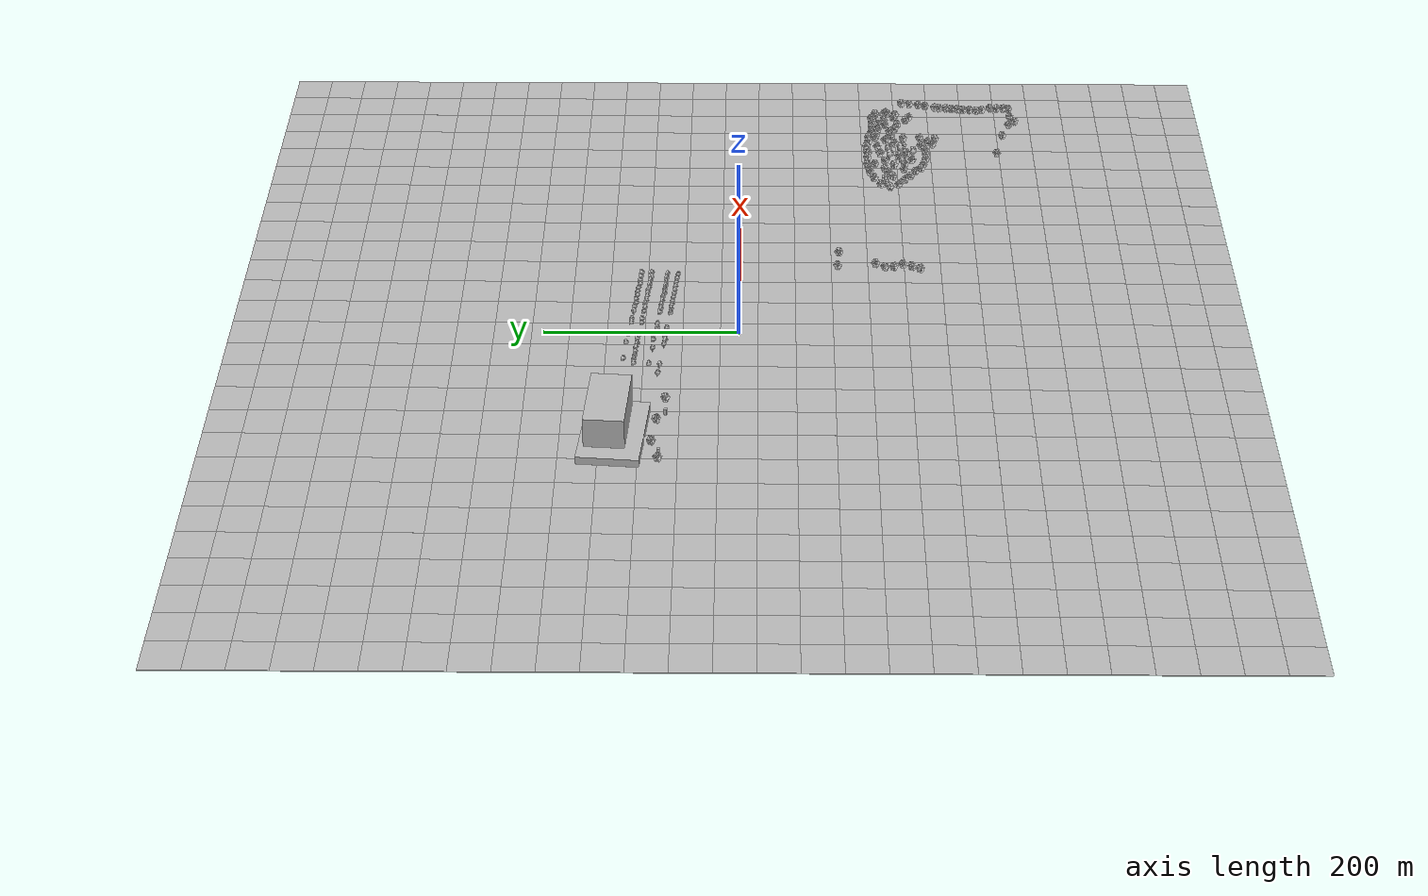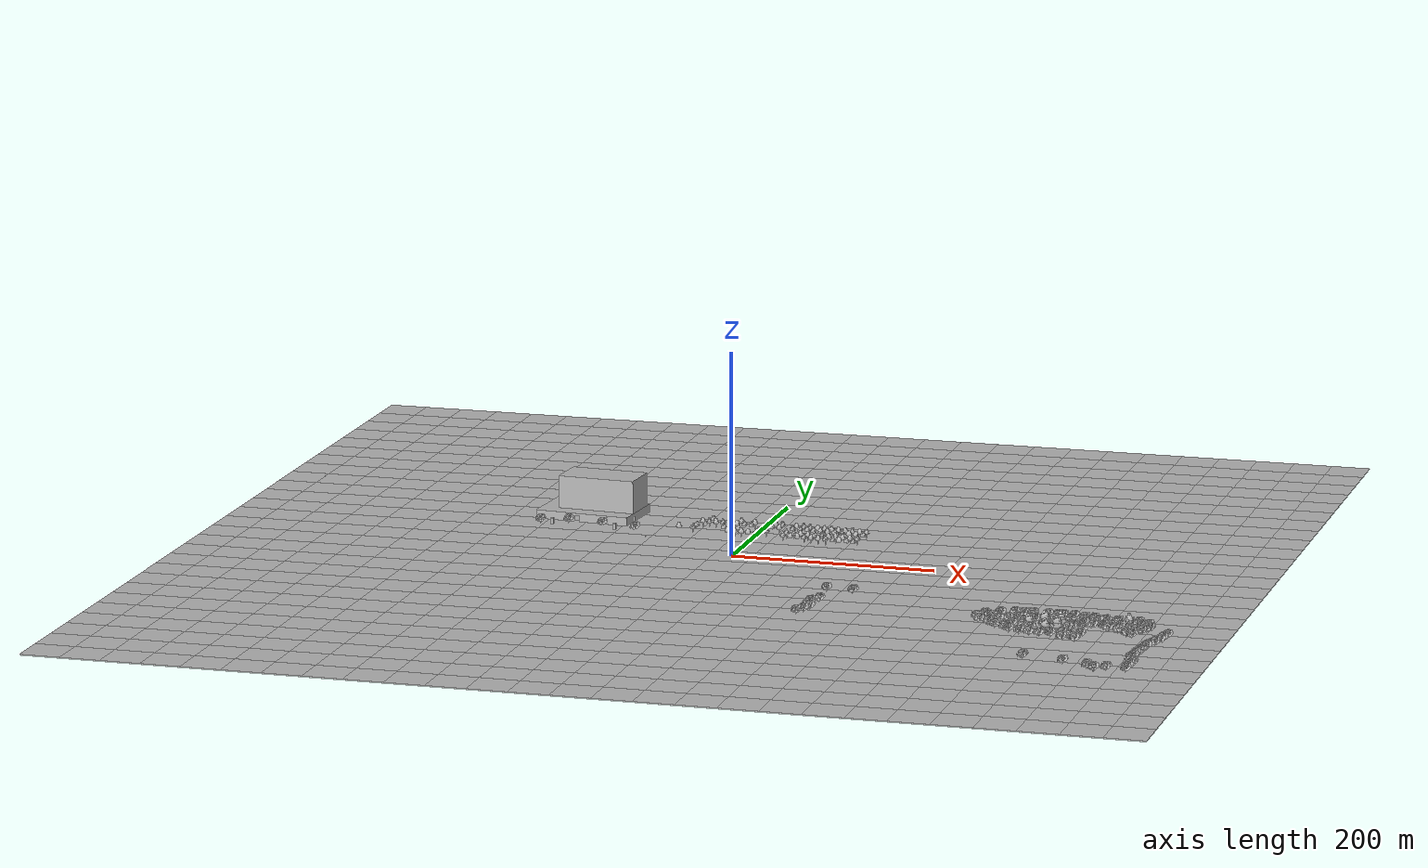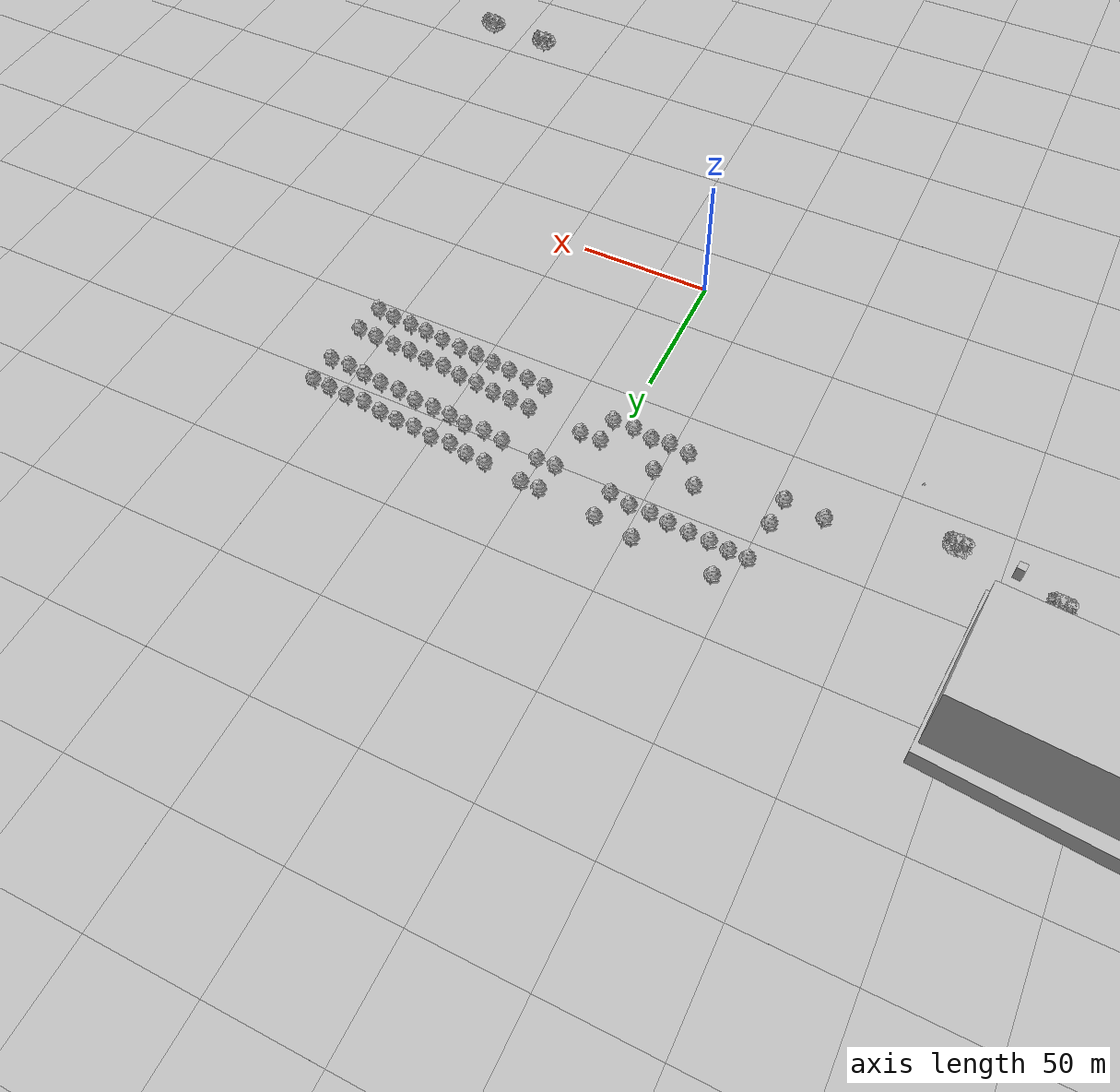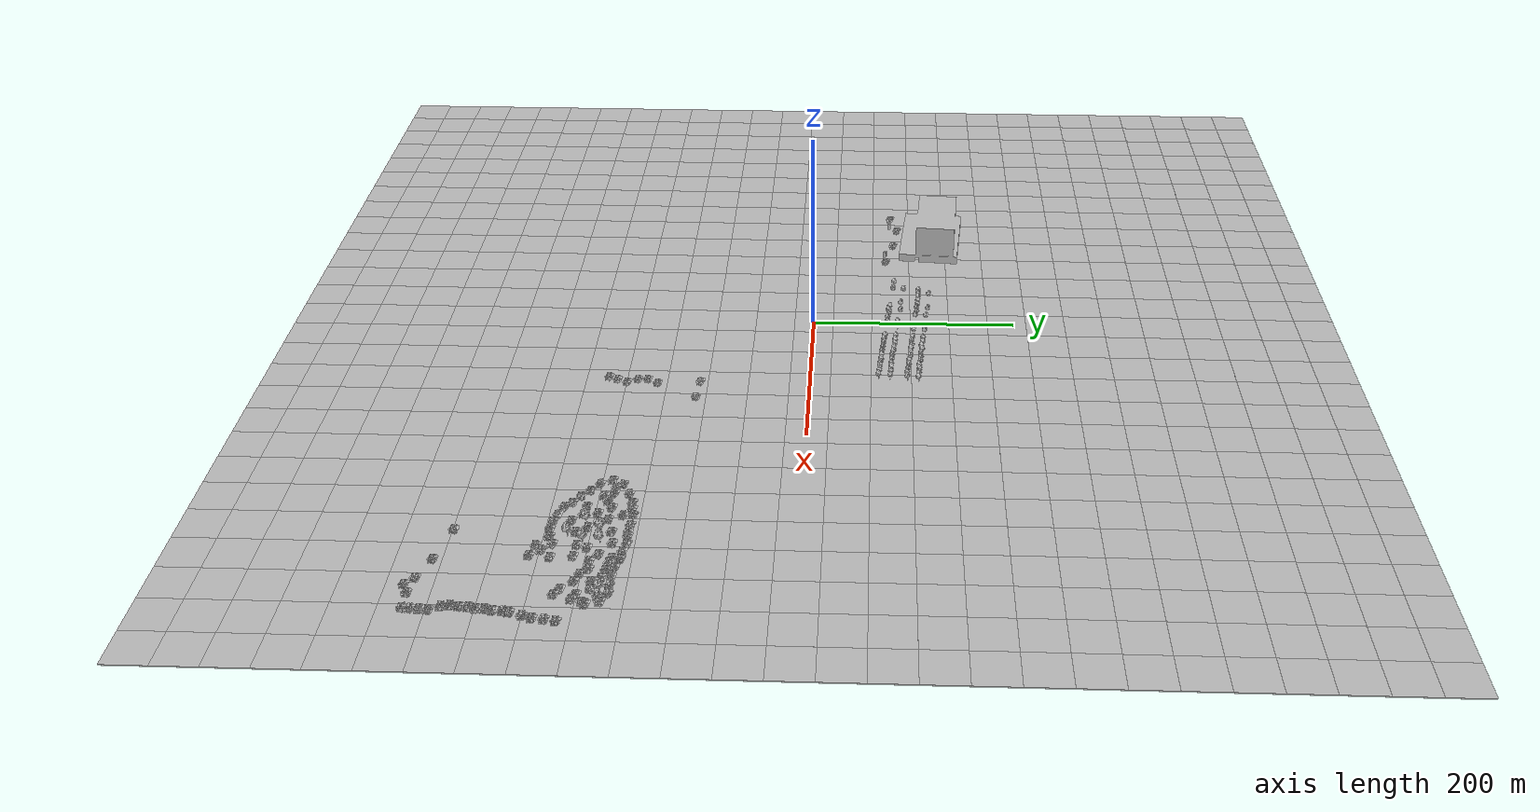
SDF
<sdf version="1.7">
 <world name="default">
  <light name="sun" type="directional">
   <pose>0 0 10 0 -0 0</pose>
   <diffuse>0.8 0.8 0.8 1</diffuse>
   <specular>0.2 0.2 0.2 1</specular>
   <attenuation>
    <range>1000</range>
    <constant>0.9</constant>
    <linear>0.01</linear>
    <quadratic>0.001</quadratic>
   </attenuation>
   <direction>-0.5 0.1 -0.9</direction>
   <spot><inner_angle>0</inner_angle><outer_angle>0</outer_angle><falloff>0</falloff></spot>
  </light>
  <gravity>0 0 -9.8</gravity>
  <magnetic_field>6e-06 2.3e-05 -4.2e-05</magnetic_field>
  <atmosphere type="adiabatic"/>
  <physics type="ode">
   <max_step_size>0.001</max_step_size>
   <real_time_factor>1</real_time_factor>
   <real_time_update_rate>1000</real_time_update_rate>
  </physics>
  <scene><ambient>0.4 0.4 0.4 1</ambient><background>0.7 0.7 0.7 1</background><shadows>1</shadows></scene>
  <spherical_coordinates>
   <surface_model>EARTH_WGS84</surface_model>
   <latitude_deg>36.0824</latitude_deg>
   <longitude_deg>140.078</longitude_deg>
   <elevation>0</elevation>
   <heading_deg>180</heading_deg>
  </spherical_coordinates>
  <include>
   <uri>model://momo</uri>
   <pose>-101.465143 50.128662 0.403297 0.000031 0.013149 -3.049204</pose>
  </include>
  <model name="map_satellite_36.082428_140.078339_1020_1020">
   <static>1</static>
   <link name="link">
    <collision name="collision">
     <pose>0 0 -0.5 0 -0 0</pose>
     <geometry><box><size>1042.44 1042.44 1</size></box></geometry>
    </collision>
    <visual name="visual0_0">
     <pose>-501.915 501.915 -0.5 0 -0 1.5708</pose>
     <geometry><box><size>38.6088 38.6088 1</size></box></geometry>
     <material>
      <script>
       <uri>model://map_satellite_36.082428_140.078339_1020_1020/materials/scripts</uri>
       <uri>model://map_satellite_36.082428_140.078339_1020_1020/materials/textures</uri>
       <name>map_satellite_36.082428_140.078339_1020_1020/0_0</name>
      </script>
     </material>
    </visual>
    <visual name="visual0_1">
     <pose>-463.306 501.915 -0.5 0 -0 1.5708</pose>
     <geometry><box><size>38.6088 38.6088 1</size></box></geometry>
     <material>
      <script>
       <uri>model://map_satellite_36.082428_140.078339_1020_1020/materials/scripts</uri>
       <uri>model://map_satellite_36.082428_140.078339_1020_1020/materials/textures</uri>
       <name>map_satellite_36.082428_140.078339_1020_1020/0_1</name>
      </script>
     </material>
    </visual>
    <visual name="visual0_2">
     <pose>-424.697 501.915 -0.5 0 -0 1.5708</pose>
     <geometry><box><size>38.6088 38.6088 1</size></box></geometry>
     <material>
      <script>
       <uri>model://map_satellite_36.082428_140.078339_1020_1020/materials/scripts</uri>
       <uri>model://map_satellite_36.082428_140.078339_1020_1020/materials/textures</uri>
       <name>map_satellite_36.082428_140.078339_1020_1020/0_2</name>
      </script>
     </material>
    </visual>
    <visual name="visual0_3">
     <pose>-386.088 501.915 -0.5 0 -0 1.5708</pose>
     <geometry><box><size>38.6088 38.6088 1</size></box></geometry>
     <material>
      <script>
       <uri>model://map_satellite_36.082428_140.078339_1020_1020/materials/scripts</uri>
       <uri>model://map_satellite_36.082428_140.078339_1020_1020/materials/textures</uri>
       <name>map_satellite_36.082428_140.078339_1020_1020/0_3</name>
      </script>
     </material>
    </visual>
    <visual name="visual0_4">
     <pose>-347.48 501.915 -0.5 0 -0 1.5708</pose>
     <geometry><box><size>38.6088 38.6088 1</size></box></geometry>
     <material>
      <script>
       <uri>model://map_satellite_36.082428_140.078339_1020_1020/materials/scripts</uri>
       <uri>model://map_satellite_36.082428_140.078339_1020_1020/materials/textures</uri>
       <name>map_satellite_36.082428_140.078339_1020_1020/0_4</name>
      </script>
     </material>
    </visual>
    <visual name="visual0_5">
     <pose>-308.871 501.915 -0.5 0 -0 1.5708</pose>
     <geometry><box><size>38.6088 38.6088 1</size></box></geometry>
     <material>
      <script>
       <uri>model://map_satellite_36.082428_140.078339_1020_1020/materials/scripts</uri>
       <uri>model://map_satellite_36.082428_140.078339_1020_1020/materials/textures</uri>
       <name>map_satellite_36.082428_140.078339_1020_1020/0_5</name>
      </script>
     </material>
    </visual>
    <visual name="visual0_6">
     <pose>-270.262 501.915 -0.5 0 -0 1.5708</pose>
     <geometry><box><size>38.6088 38.6088 1</size></box></geometry>
     <material>
      <script>
       <uri>model://map_satellite_36.082428_140.078339_1020_1020/materials/scripts</uri>
       <uri>model://map_satellite_36.082428_140.078339_1020_1020/materials/textures</uri>
       <name>map_satellite_36.082428_140.078339_1020_1020/0_6</name>
      </script>
     </material>
    </visual>
    <visual name="visual0_7">
     <pose>-231.653 501.915 -0.5 0 -0 1.5708</pose>
     <geometry><box><size>38.6088 38.6088 1</size></box></geometry>
     <material>
      <script>
       <uri>model://map_satellite_36.082428_140.078339_1020_1020/materials/scripts</uri>
       <uri>model://map_satellite_36.082428_140.078339_1020_1020/materials/textures</uri>
       <name>map_satellite_36.082428_140.078339_1020_1020/0_7</name>
      </script>
     </material>
    </visual>
    <visual name="visual0_8">
     <pose>-193.044 501.915 -0.5 0 -0 1.5708</pose>
     <geometry><box><size>38.6088 38.6088 1</size></box></geometry>
     <material>
      <script>
       <uri>model://map_satellite_36.082428_140.078339_1020_1020/materials/scripts</uri>
       <uri>model://map_satellite_36.082428_140.078339_1020_1020/materials/textures</uri>
       <name>map_satellite_36.082428_140.078339_1020_1020/0_8</name>
      </script>
     </material>
    </visual>
    <visual name="visual0_9">
     <pose>-154.435 501.915 -0.5 0 -0 1.5708</pose>
     <geometry><box><size>38.6088 38.6088 1</size></box></geometry>
     <material>
      <script>
       <uri>model://map_satellite_36.082428_140.078339_1020_1020/materials/scripts</uri>
       <uri>model://map_satellite_36.082428_140.078339_1020_1020/materials/textures</uri>
       <name>map_satellite_36.082428_140.078339_1020_1020/0_9</name>
      </script>
     </material>
    </visual>
    <visual name="visual0_10">
     <pose>-115.827 501.915 -0.5 0 -0 1.5708</pose>
     <geometry><box><size>38.6088 38.6088 1</size></box></geometry>
     <material>
      <script>
       <uri>model://map_satellite_36.082428_140.078339_1020_1020/materials/scripts</uri>
       <uri>model://map_satellite_36.082428_140.078339_1020_1020/materials/textures</uri>
       <name>map_satellite_36.082428_140.078339_1020_1020/0_10</name>
      </script>
     </material>
    </visual>
    <visual name="visual0_11">
     <pose>-77.2177 501.915 -0.5 0 -0 1.5708</pose>
     <geometry><box><size>38.6088 38.6088 1</size></box></geometry>
     <material>
      <script>
       <uri>model://map_satellite_36.082428_140.078339_1020_1020/materials/scripts</uri>
       <uri>model://map_satellite_36.082428_140.078339_1020_1020/materials/textures</uri>
       <name>map_satellite_36.082428_140.078339_1020_1020/0_11</name>
      </script>
     </material>
    </visual>
    <visual name="visual0_12">
     <pose>-38.6088 501.915 -0.5 0 -0 1.5708</pose>
     <geometry><box><size>38.6088 38.6088 1</size></box></geometry>
     <material>
      <script>
       <uri>model://map_satellite_36.082428_140.078339_1020_1020/materials/scripts</uri>
       <uri>model://map_satellite_36.082428_140.078339_1020_1020/materials/textures</uri>
       <name>map_satellite_36.082428_140.078339_1020_1020/0_12</name>
      </script>
     </material>
    </visual>
    <visual name="visual0_13">
     <pose>-0 501.915 -0.5 0 -0 1.5708</pose>
     <geometry><box><size>38.6088 38.6088 1</size></box></geometry>
     <material>
      <script>
       <uri>model://map_satellite_36.082428_140.078339_1020_1020/materials/scripts</uri>
       <uri>model://map_satellite_36.082428_140.078339_1020_1020/materials/textures</uri>
       <name>map_satellite_36.082428_140.078339_1020_1020/0_13</name>
      </script>
     </material>
    </visual>
    <visual name="visual0_14">
     <pose>38.6088 501.915 -0.5 0 -0 1.5708</pose>
     <geometry><box><size>38.6088 38.6088 1</size></box></geometry>
     <material>
      <script>
       <uri>model://map_satellite_36.082428_140.078339_1020_1020/materials/scripts</uri>
       <uri>model://map_satellite_36.082428_140.078339_1020_1020/materials/textures</uri>
       <name>map_satellite_36.082428_140.078339_1020_1020/0_14</name>
      </script>
     </material>
    </visual>
    <visual name="visual0_15">
     <pose>77.2177 501.915 -0.5 0 -0 1.5708</pose>
     <geometry><box><size>38.6088 38.6088 1</size></box></geometry>
     <material>
      <script>
       <uri>model://map_satellite_36.082428_140.078339_1020_1020/materials/scripts</uri>
       <uri>model://map_satellite_36.082428_140.078339_1020_1020/materials/textures</uri>
       <name>map_satellite_36.082428_140.078339_1020_1020/0_15</name>
      </script>
     </material>
    </visual>
    <visual name="visual0_16">
     <pose>115.827 501.915 -0.5 0 -0 1.5708</pose>
     <geometry><box><size>38.6088 38.6088 1</size></box></geometry>
     <material>
      <script>
       <uri>model://map_satellite_36.082428_140.078339_1020_1020/materials/scripts</uri>
       <uri>model://map_satellite_36.082428_140.078339_1020_1020/materials/textures</uri>
       <name>map_satellite_36.082428_140.078339_1020_1020/0_16</name>
      </script>
     </material>
    </visual>
    <visual name="visual0_17">
     <pose>154.435 501.915 -0.5 0 -0 1.5708</pose>
     <geometry><box><size>38.6088 38.6088 1</size></box></geometry>
     <material>
      <script>
       <uri>model://map_satellite_36.082428_140.078339_1020_1020/materials/scripts</uri>
       <uri>model://map_satellite_36.082428_140.078339_1020_1020/materials/textures</uri>
       <name>map_satellite_36.082428_140.078339_1020_1020/0_17</name>
      </script>
     </material>
    </visual>
    <visual name="visual0_18">
     <pose>193.044 501.915 -0.5 0 -0 1.5708</pose>
     <geometry><box><size>38.6088 38.6088 1</size></box></geometry>
     <material>
      <script>
       <uri>model://map_satellite_36.082428_140.078339_1020_1020/materials/scripts</uri>
       <uri>model://map_satellite_36.082428_140.078339_1020_1020/materials/textures</uri>
       <name>map_satellite_36.082428_140.078339_1020_1020/0_18</name>
      </script>
     </material>
    </visual>
    <visual name="visual0_19">
     <pose>231.653 501.915 -0.5 0 -0 1.5708</pose>
     <geometry><box><size>38.6088 38.6088 1</size></box></geometry>
     <material>
      <script>
       <uri>model://map_satellite_36.082428_140.078339_1020_1020/materials/scripts</uri>
       <uri>model://map_satellite_36.082428_140.078339_1020_1020/materials/textures</uri>
       <name>map_satellite_36.082428_140.078339_1020_1020/0_19</name>
      </script>
     </material>
    </visual>
    <visual name="visual0_20">
     <pose>270.262 501.915 -0.5 0 -0 1.5708</pose>
     <geometry><box><size>38.6088 38.6088 1</size></box></geometry>
     <material>
      <script>
       <uri>model://map_satellite_36.082428_140.078339_1020_1020/materials/scripts</uri>
       <uri>model://map_satellite_36.082428_140.078339_1020_1020/materials/textures</uri>
       <name>map_satellite_36.082428_140.078339_1020_1020/0_20</name>
      </script>
     </material>
    </visual>
    <visual name="visual0_21">
     <pose>308.871 501.915 -0.5 0 -0 1.5708</pose>
     <geometry><box><size>38.6088 38.6088 1</size></box></geometry>
     <material>
      <script>
       <uri>model://map_satellite_36.082428_140.078339_1020_1020/materials/scripts</uri>
       <uri>model://map_satellite_36.082428_140.078339_1020_1020/materials/textures</uri>
       <name>map_satellite_36.082428_140.078339_1020_1020/0_21</name>
      </script>
     </material>
    </visual>
    <visual name="visual0_22">
     <pose>347.48 501.915 -0.5 0 -0 1.5708</pose>
     <geometry><box><size>38.6088 38.6088 1</size></box></geometry>
     <material>
      <script>
       <uri>model://map_satellite_36.082428_140.078339_1020_1020/materials/scripts</uri>
       <uri>model://map_satellite_36.082428_140.078339_1020_1020/materials/textures</uri>
       <name>map_satellite_36.082428_140.078339_1020_1020/0_22</name>
      </script>
     </material>
    </visual>
    <visual name="visual0_23">
     <pose>386.088 501.915 -0.5 0 -0 1.5708</pose>
     <geometry><box><size>38.6088 38.6088 1</size></box></geometry>
     <material>
      <script>
       <uri>model://map_satellite_36.082428_140.078339_1020_1020/materials/scripts</uri>
       <uri>model://map_satellite_36.082428_140.078339_1020_1020/materials/textures</uri>
       <name>map_satellite_36.082428_140.078339_1020_1020/0_23</name>
      </script>
     </material>
    </visual>
    <visual name="visual0_24">
     <pose>424.697 501.915 -0.5 0 -0 1.5708</pose>
     <geometry><box><size>38.6088 38.6088 1</size></box></geometry>
     <material>
      <script>
       <uri>model://map_satellite_36.082428_140.078339_1020_1020/materials/scripts</uri>
       <uri>model://map_satellite_36.082428_140.078339_1020_1020/materials/textures</uri>
       <name>map_satellite_36.082428_140.078339_1020_1020/0_24</name>
      </script>
     </material>
    </visual>
    <visual name="visual0_25">
     <pose>463.306 501.915 -0.5 0 -0 1.5708</pose>
     <geometry><box><size>38.6088 38.6088 1</size></box></geometry>
     <material>
      <script>
       <uri>model://map_satellite_36.082428_140.078339_1020_1020/materials/scripts</uri>
       <uri>model://map_satellite_36.082428_140.078339_1020_1020/materials/textures</uri>
       <name>map_satellite_36.082428_140.078339_1020_1020/0_25</name>
      </script>
     </material>
    </visual>
    <visual name="visual0_26">
     <pose>501.915 501.915 -0.5 0 -0 1.5708</pose>
     <geometry><box><size>38.6088 38.6088 1</size></box></geometry>
     <material>
      <script>
       <uri>model://map_satellite_36.082428_140.078339_1020_1020/materials/scripts</uri>
       <uri>model://map_satellite_36.082428_140.078339_1020_1020/materials/textures</uri>
       <name>map_satellite_36.082428_140.078339_1020_1020/0_26</name>
      </script>
     </material>
    </visual>
    <visual name="visual1_0">
     <pose>-501.915 463.306 -0.5 0 -0 1.5708</pose>
     <geometry><box><size>38.6088 38.6088 1</size></box></geometry>
     <material>
      <script>
       <uri>model://map_satellite_36.082428_140.078339_1020_1020/materials/scripts</uri>
       <uri>model://map_satellite_36.082428_140.078339_1020_1020/materials/textures</uri>
       <name>map_satellite_36.082428_140.078339_1020_1020/1_0</name>
      </script>
     </material>
    </visual>
    <visual name="visual1_1">
     <pose>-463.306 463.306 -0.5 0 -0 1.5708</pose>
     <geometry><box><size>38.6088 38.6088 1</size></box></geometry>
     <material>
      <script>
       <uri>model://map_satellite_36.082428_140.078339_1020_1020/materials/scripts</uri>
       <uri>model://map_satellite_36.082428_140.078339_1020_1020/materials/textures</uri>
       <name>map_satellite_36.082428_140.078339_1020_1020/1_1</name>
      </script>
     </material>
    </visual>
    <visual name="visual1_2">
     <pose>-424.697 463.306 -0.5 0 -0 1.5708</pose>
     <geometry><box><size>38.6088 38.6088 1</size></box></geometry>
     <material>
      <script>
       <uri>model://map_satellite_36.082428_140.078339_1020_1020/materials/scripts</uri>
       <uri>model://map_satellite_36.082428_140.078339_1020_1020/materials/textures</uri>
       <name>map_satellite_36.082428_140.078339_1020_1020/1_2</name>
      </script>
     </material>
    </visual>
    <visual name="visual1_3">
     <pose>-386.088 463.306 -0.5 0 -0 1.5708</pose>
     <geometry><box><size>38.6088 38.6088 1</size></box></geometry>
     <material>
      <script>
       <uri>model://map_satellite_36.082428_140.078339_1020_1020/materials/scripts</uri>
       <uri>model://map_satellite_36.082428_140.078339_1020_1020/materials/textures</uri>
       <name>map_satellite_36.082428_140.078339_1020_1020/1_3</name>
      </script>
     </material>
    </visual>
    <visual name="visual1_4">
     <pose>-347.48 463.306 -0.5 0 -0 1.5708</pose>
     <geometry><box><size>38.6088 38.6088 1</size></box></geometry>
     <material>
      <script>
       <uri>model://map_satellite_36.082428_140.078339_1020_1020/materials/scripts</uri>
       <uri>model://map_satellite_36.082428_140.078339_1020_1020/materials/textures</uri>
       <name>map_satellite_36.082428_140.078339_1020_1020/1_4</name>
      </script>
     </material>
    </visual>
    <visual name="visual1_5">
     <pose>-308.871 463.306 -0.5 0 -0 1.5708</pose>
     <geometry><box><size>38.6088 38.6088 1</size></box></geometry>
     <material>
      <script>
       <uri>model://map_satellite_36.082428_140.078339_1020_1020/materials/scripts</uri>
       <uri>model://map_satellite_36.082428_140.078339_1020_1020/materials/textures</uri>
       <name>map_satellite_36.082428_140.078339_1020_1020/1_5</name>
      </script>
     </material>
    </visual>
    <visual name="visual1_6">
     <pose>-270.262 463.306 -0.5 0 -0 1.5708</pose>
     <geometry><box><size>38.6088 38.6088 1</size></box></geometry>
     <material>
      <script>
       <uri>model://map_satellite_36.082428_140.078339_1020_1020/materials/scripts</uri>
       <uri>model://map_satellite_36.082428_140.078339_1020_1020/materials/textures</uri>
       <name>map_satellite_36.082428_140.078339_1020_1020/1_6</name>
      </script>
     </material>
    </visual>
    <visual name="visual1_7">
     <pose>-231.653 463.306 -0.5 0 -0 1.5708</pose>
     <geometry><box><size>38.6088 38.6088 1</size></box></geometry>
     <material>
      <script>
       <uri>model://map_satellite_36.082428_140.078339_1020_1020/materials/scripts</uri>
       <uri>model://map_satellite_36.082428_140.078339_1020_1020/materials/textures</uri>
       <name>map_satellite_36.082428_140.078339_1020_1020/1_7</name>
      </script>
     </material>
    </visual>
    <visual name="visual1_8">
     <pose>-193.044 463.306 -0.5 0 -0 1.5708</pose>
     <geometry><box><size>38.6088 38.6088 1</size></box></geometry>
     <material>
      <script>
       <uri>model://map_satellite_36.082428_140.078339_1020_1020/materials/scripts</uri>
       <uri>model://map_satellite_36.082428_140.078339_1020_1020/materials/textures</uri>
       <name>map_satellite_36.082428_140.078339_1020_1020/1_8</name>
      </script>
     </material>
    </visual>
    <visual name="visual1_9">
     <pose>-154.435 463.306 -0.5 0 -0 1.5708</pose>
     <geometry><box><size>38.6088 38.6088 1</size></box></geometry>
     <material>
      <script>
       <uri>model://map_satellite_36.082428_140.078339_1020_1020/materials/scripts</uri>
       <uri>model://map_satellite_36.082428_140.078339_1020_1020/materials/textures</uri>
       <name>map_satellite_36.082428_140.078339_1020_1020/1_9</name>
      </script>
     </material>
    </visual>
    <visual name="visual1_10">
     <pose>-115.827 463.306 -0.5 0 -0 1.5708</pose>
     <geometry><box><size>38.6088 38.6088 1</size></box></geometry>
     <material>
      <script>
       <uri>model://map_satellite_36.082428_140.078339_1020_1020/materials/scripts</uri>
       <uri>model://map_satellite_36.082428_140.078339_1020_1020/materials/textures</uri>
       <name>map_satellite_36.082428_140.078339_1020_1020/1_10</name>
      </script>
     </material>
    </visual>
    <visual name="visual1_11">
     <pose>-77.2177 463.306 -0.5 0 -0 1.5708</pose>
     <geometry><box><size>38.6088 38.6088 1</size></box></geometry>
     <material>
      <script>
       <uri>model://map_satellite_36.082428_140.078339_1020_1020/materials/scripts</uri>
       <uri>model://map_satellite_36.082428_140.078339_1020_1020/materials/textures</uri>
       <name>map_satellite_36.082428_140.078339_1020_1020/1_11</name>
      </script>
     </material>
    </visual>
    <visual name="visual1_12">
     <pose>-38.6088 463.306 -0.5 0 -0 1.5708</pose>
     <geometry><box><size>38.6088 38.6088 1</size></box></geometry>
     <material>
      <script>
       <uri>model://map_satellite_36.082428_140.078339_1020_1020/materials/scripts</uri>
       <uri>model://map_satellite_36.082428_140.078339_1020_1020/materials/textures</uri>
       <name>map_satellite_36.082428_140.078339_1020_1020/1_12</name>
      </script>
     </material>
    </visual>
    <visual name="visual1_13">
     <pose>-0 463.306 -0.5 0 -0 1.5708</pose>
     <geometry><box><size>38.6088 38.6088 1</size></box></geometry>
     <material>
      <script>
       <uri>model://map_satellite_36.082428_140.078339_1020_1020/materials/scripts</uri>
       <uri>model://map_satellite_36.082428_140.078339_1020_1020/materials/textures</uri>
       <name>map_satellite_36.082428_140.078339_1020_1020/1_13</name>
      </script>
     </material>
    </visual>
    <visual name="visual1_14">
     <pose>38.6088 463.306 -0.5 0 -0 1.5708</pose>
     <geometry><box><size>38.6088 38.6088 1</size></box></geometry>
     <material>
      <script>
       <uri>model://map_satellite_36.082428_140.078339_1020_1020/materials/scripts</uri>
       <uri>model://map_satellite_36.082428_140.078339_1020_1020/materials/textures</uri>
       <name>map_satellite_36.082428_140.078339_1020_1020/1_14</name>
      </script>
     </material>
    </visual>
    <visual name="visual1_15">
     <pose>77.2177 463.306 -0.5 0 -0 1.5708</pose>
     <geometry><box><size>38.6088 38.6088 1</size></box></geometry>
     <material>
      <script>
       <uri>model://map_satellite_36.082428_140.078339_1020_1020/materials/scripts</uri>
       <uri>model://map_satellite_36.082428_140.078339_1020_1020/materials/textures</uri>
       <name>map_satellite_36.082428_140.078339_1020_1020/1_15</name>
      </script>
     </material>
    </visual>
    <visual name="visual1_16">
     <pose>115.827 463.306 -0.5 0 -0 1.5708</pose>
     <geometry><box><size>38.6088 38.6088 1</size></box></geometry>
     <material>
      <script>
       <uri>model://map_satellite_36.082428_140.078339_1020_1020/materials/scripts</uri>
       <uri>model://map_satellite_36.082428_140.078339_1020_1020/materials/textures</uri>
       <name>map_satellite_36.082428_140.078339_1020_1020/1_16</name>
      </script>
     </material>
    </visual>
    <visual name="visual1_17">
     <pose>154.435 463.306 -0.5 0 -0 1.5708</pose>
     <geometry><box><size>38.6088 38.6088 1</size></box></geometry>
     <material>
      <script>
       <uri>model://map_satellite_36.082428_140.078339_1020_1020/materials/scripts</uri>
       <uri>model://map_satellite_36.082428_140.078339_1020_1020/materials/textures</uri>
       <name>map_satellite_36.082428_140.078339_1020_1020/1_17</name>
      </script>
     </material>
    </visual>
    <visual name="visual1_18">
     <pose>193.044 463.306 -0.5 0 -0 1.5708</pose>
     <geometry><box><size>38.6088 38.6088 1</size></box></geometry>
     <material>
      <script>
       <uri>model://map_satellite_36.082428_140.078339_1020_1020/materials/scripts</uri>
       <uri>model://map_satellite_36.082428_140.078339_1020_1020/materials/textures</uri>
       <name>map_satellite_36.082428_140.078339_1020_1020/1_18</name>
      </script>
     </material>
    </visual>
    <visual name="visual1_19">
     <pose>231.653 463.306 -0.5 0 -0 1.5708</pose>
     <geometry><box><size>38.6088 38.6088 1</size></box></geometry>
     <material>
      <script>
       <uri>model://map_satellite_36.082428_140.078339_1020_1020/materials/scripts</uri>
       <uri>model://map_satellite_36.082428_140.078339_1020_1020/materials/textures</uri>
       <name>map_satellite_36.082428_140.078339_1020_1020/1_19</name>
      </script>
     </material>
    </visual>
    <visual name="visual1_20">
     <pose>270.262 463.306 -0.5 0 -0 1.5708</pose>
     <geometry><box><size>38.6088 38.6088 1</size></box></geometry>
     <material>
      <script>
       <uri>model://map_satellite_36.082428_140.078339_1020_1020/materials/scripts</uri>
       <uri>model://map_satellite_36.082428_140.078339_1020_1020/materials/textures</uri>
       <name>map_satellite_36.082428_140.078339_1020_1020/1_20</name>
      </script>
     </material>
    </visual>
    <visual name="visual1_21">
     <pose>308.871 463.306 -0.5 0 -0 1.5708</pose>
     <geometry><box><size>38.6088 38.6088 1</size></box></geometry>
     <material>
      <script>
       <uri>model://map_satellite_36.082428_140.078339_1020_1020/materials/scripts</uri>
       <uri>model://map_satellite_36.082428_140.078339_1020_1020/materials/textures</uri>
       <name>map_satellite_36.082428_140.078339_1020_1020/1_21</name>
      </script>
     </material>
    </visual>
    <visual name="visual1_22">
     <pose>347.48 463.306 -0.5 0 -0 1.5708</pose>
     <geometry><box><size>38.6088 38.6088 1</size></box></geometry>
     <material>
      <script>
       <uri>model://map_satellite_36.082428_140.078339_1020_1020/materials/scripts</uri>
       <uri>model://map_satellite_36.082428_140.078339_1020_1020/materials/textures</uri>
       <name>map_satellite_36.082428_140.078339_1020_1020/1_22</name>
      </script>
     </material>
    </visual>
    <visual name="visual1_23">
     <pose>386.088 463.306 -0.5 0 -0 1.5708</pose>
     <geometry><box><size>38.6088 38.6088 1</size></box></geometry>
     <material>
      <script>
       <uri>model://map_satellite_36.082428_140.078339_1020_1020/materials/scripts</uri>
       <uri>model://map_satellite_36.082428_140.078339_1020_1020/materials/textures</uri>
       <name>map_satellite_36.082428_140.078339_1020_1020/1_23</name>
      </script>
     </material>
    </visual>
    <visual name="visual1_24">
     <pose>424.697 463.306 -0.5 0 -0 1.5708</pose>
     <geometry><box><size>38.6088 38.6088 1</size></box></geometry>
     <material>
      <script>
       <uri>model://map_satellite_36.082428_140.078339_1020_1020/materials/scripts</uri>
       <uri>model://map_satellite_36.082428_140.078339_1020_1020/materials/textures</uri>
       <name>map_satellite_36.082428_140.078339_1020_1020/1_24</name>
      </script>
     </material>
    </visual>
    <visual name="visual1_25">
     <pose>463.306 463.306 -0.5 0 -0 1.5708</pose>
     <geometry><box><size>38.6088 38.6088 1</size></box></geometry>
     <material>
      <script>
       <uri>model://map_satellite_36.082428_140.078339_1020_1020/materials/scripts</uri>
       <uri>model://map_satellite_36.082428_140.078339_1020_1020/materials/textures</uri>
       <name>map_satellite_36.082428_140.078339_1020_1020/1_25</name>
      </script>
     </material>
    </visual>
    <visual name="visual1_26">
     <pose>501.915 463.306 -0.5 0 -0 1.5708</pose>
     <geometry><box><size>38.6088 38.6088 1</size></box></geometry>
     <material>
      <script>
       <uri>model://map_satellite_36.082428_140.078339_1020_1020/materials/scripts</uri>
       <uri>model://map_satellite_36.082428_140.078339_1020_1020/materials/textures</uri>
       <name>map_satellite_36.082428_140.078339_1020_1020/1_26</name>
      </script>
     </material>
    </visual>
    <visual name="visual2_0">
     <pose>-501.915 424.697 -0.5 0 -0 1.5708</pose>
     <geometry><box><size>38.6088 38.6088 1</size></box></geometry>
     <material>
      <script>
       <uri>model://map_satellite_36.082428_140.078339_1020_1020/materials/scripts</uri>
       <uri>model://map_satellite_36.082428_140.078339_1020_1020/materials/textures</uri>
       <name>map_satellite_36.082428_140.078339_1020_1020/2_0</name>
      </script>
     </material>
    </visual>
    <visual name="visual2_1">
     <pose>-463.306 424.697 -0.5 0 -0 1.5708</pose>
     <geometry><box><size>38.6088 38.6088 1</size></box></geometry>
     <material>
      <script>
       <uri>model://map_satellite_36.082428_140.078339_1020_1020/materials/scripts</uri>
       <uri>model://map_satellite_36.082428_140.078339_1020_1020/materials/textures</uri>
       <name>map_satellite_36.082428_140.078339_1020_1020/2_1</name>
      </script>
     </material>
    </visual>
    <visual name="visual2_2">
     <pose>-424.697 424.697 -0.5 0 -0 1.5708</pose>
     <geometry><box><size>38.6088 38.6088 1</size></box></geometry>
     <material>
      <script>
       <uri>model://map_satellite_36.082428_140.078339_1020_1020/materials/scripts</uri>
       <uri>model://map_satellite_36.082428_140.078339_1020_1020/materials/textures</uri>
       <name>map_satellite_36.082428_140.078339_1020_1020/2_2</name>
      </script>
     </material>
    </visual>
    <visual name="visual2_3">
     <pose>-386.088 424.697 -0.5 0 -0 1.5708</pose>
     <geometry><box><size>38.6088 38.6088 1</size></box></geometry>
     <material>
      <script>
       <uri>model://map_satellite_36.082428_140.078339_1020_1020/materials/scripts</uri>
       <uri>model://map_satellite_36.082428_140.078339_1020_1020/materials/textures</uri>
       <name>map_satellite_36.082428_140.078339_1020_1020/2_3</name>
      </script>
     </material>
    </visual>
    <visual name="visual2_4">
     <pose>-347.48 424.697 -0.5 0 -0 1.5708</pose>
     <geometry><box><size>38.6088 38.6088 1</size></box></geometry>
     <material>
      <script>
       <uri>model://map_satellite_36.082428_140.078339_1020_1020/materials/scripts</uri>
       <uri>model://map_satellite_36.082428_140.078339_1020_1020/materials/textures</uri>
       <name>map_satellite_36.082428_140.078339_1020_1020/2_4</name>
      </script>
     </material>
    </visual>
    <visual name="visual2_5">
     <pose>-308.871 424.697 -0.5 0 -0 1.5708</pose>
     <geometry><box><size>38.6088 38.6088 1</size></box></geometry>
     <material>
      <script>
       <uri>model://map_satellite_36.082428_140.078339_1020_1020/materials/scripts</uri>
       <uri>model://map_satellite_36.082428_140.078339_1020_1020/materials/textures</uri>
       <name>map_satellite_36.082428_140.078339_1020_1020/2_5</name>
      </script>
     </material>
    </visual>
    <visual name="visual2_6">
     <pose>-270.262 424.697 -0.5 0 -0 1.5708</pose>
     <geometry><box><size>38.6088 38.6088 1</size></box></geometry>
     <material>
      <script>
       <uri>model://map_satellite_36.082428_140.078339_1020_1020/materials/scripts</uri>
       <uri>model://map_satellite_36.082428_140.078339_1020_1020/materials/textures</uri>
       <name>map_satellite_36.082428_140.078339_1020_1020/2_6</name>
      </script>
     </material>
    </visual>
    <visual name="visual2_7">
     <pose>-231.653 424.697 -0.5 0 -0 1.5708</pose>
     <geometry><box><size>38.6088 38.6088 1</size></box></geometry>
     <material>
      <script>
       <uri>model://map_satellite_36.082428_140.078339_1020_1020/materials/scripts</uri>
       <uri>model://map_satellite_36.082428_140.078339_1020_1020/materials/textures</uri>
       <name>map_satellite_36.082428_140.078339_1020_1020/2_7</name>
      </script>
     </material>
    </visual>
    <visual name="visual2_8">
     <pose>-193.044 424.697 -0.5 0 -0 1.5708</pose>
     <geometry><box><size>38.6088 38.6088 1</size></box></geometry>
     <material>
      <script>
       <uri>model://map_satellite_36.082428_140.078339_1020_1020/materials/scripts</uri>
       <uri>model://map_satellite_36.082428_140.078339_1020_1020/materials/textures</uri>
       <name>map_satellite_36.082428_140.078339_1020_1020/2_8</name>
      </script>
     </material>
    </visual>
    <visual name="visual2_9">
     <pose>-154.435 424.697 -0.5 0 -0 1.5708</pose>
     <geometry><box><size>38.6088 38.6088 1</size></box></geometry>
     <material>
      <script>
       <uri>model://map_satellite_36.082428_140.078339_1020_1020/materials/scripts</uri>
       <uri>model://map_satellite_36.082428_140.078339_1020_1020/materials/textures</uri>
       <name>map_satellite_36.082428_140.078339_1020_1020/2_9</name>
      </script>
     </material>
    </visual>
    <visual name="visual2_10">
     <pose>-115.827 424.697 -0.5 0 -0 1.5708</pose>
     <geometry><box><size>38.6088 38.6088 1</size></box></geometry>
     <material>
      <script>
       <uri>model://map_satellite_36.082428_140.078339_1020_1020/materials/scripts</uri>
       <uri>model://map_satellite_36.082428_140.078339_1020_1020/materials/textures</uri>
       <name>map_satellite_36.082428_140.078339_1020_1020/2_10</name>
      </script>
     </material>
    </visual>
    <visual name="visual2_11">
     <pose>-77.2177 424.697 -0.5 0 -0 1.5708</pose>
     <geometry><box><size>38.6088 38.6088 1</size></box></geometry>
     <material>
      <script>
       <uri>model://map_satellite_36.082428_140.078339_1020_1020/materials/scripts</uri>
       <uri>model://map_satellite_36.082428_140.078339_1020_1020/materials/textures</uri>
       <name>map_satellite_36.082428_140.078339_1020_1020/2_11</name>
      </script>
     </material>
    </visual>
    <visual name="visual2_12">
     <pose>-38.6088 424.697 -0.5 0 -0 1.5708</pose>
     <geometry><box><size>38.6088 38.6088 1</size></box></geometry>
     <material>
      <script>
       <uri>model://map_satellite_36.082428_140.078339_1020_1020/materials/scripts</uri>
       <uri>model://map_satellite_36.082428_140.078339_1020_1020/materials/textures</uri>
       <name>map_satellite_36.082428_140.078339_1020_1020/2_12</name>
      </script>
     </material>
    </visual>
    <visual name="visual2_13">
     <pose>-0 424.697 -0.5 0 -0 1.5708</pose>
     <geometry><box><size>38.6088 38.6088 1</size></box></geometry>
     <material>
      <script>
       <uri>model://map_satellite_36.082428_140.078339_1020_1020/materials/scripts</uri>
       <uri>model://map_satellite_36.082428_140.078339_1020_1020/materials/textures</uri>
       <name>map_satellite_36.082428_140.078339_1020_1020/2_13</name>
      </script>
     </material>
    </visual>
    <visual name="visual2_14">
     <pose>38.6088 424.697 -0.5 0 -0 1.5708</pose>
     <geometry><box><size>38.6088 38.6088 1</size></box></geometry>
     <material>
      <script>
       <uri>model://map_satellite_36.082428_140.078339_1020_1020/materials/scripts</uri>
       <uri>model://map_satellite_36.082428_140.078339_1020_1020/materials/textures</uri>
       <name>map_satellite_36.082428_140.078339_1020_1020/2_14</name>
      </script>
     </material>
    </visual>
    <visual name="visual2_15">
     <pose>77.2177 424.697 -0.5 0 -0 1.5708</pose>
     <geometry><box><size>38.6088 38.6088 1</size></box></geometry>
     <material>
      <script>
       <uri>model://map_satellite_36.082428_140.078339_1020_1020/materials/scripts</uri>
       <uri>model://map_satellite_36.082428_140.078339_1020_1020/materials/textures</uri>
       <name>map_satellite_36.082428_140.078339_1020_1020/2_15</name>
      </script>
     </material>
    </visual>
    <visual name="visual2_16">
     <pose>115.827 424.697 -0.5 0 -0 1.5708</pose>
     <geometry><box><size>38.6088 38.6088 1</size></box></geometry>
     <material>
      <script>
       <uri>model://map_satellite_36.082428_140.078339_1020_1020/materials/scripts</uri>
       <uri>model://map_satellite_36.082428_140.078339_1020_1020/materials/textures</uri>
       <name>map_satellite_36.082428_140.078339_1020_1020/2_16</name>
      </script>
     </material>
    </visual>
    <visual name="visual2_17">
     <pose>154.435 424.697 -0.5 0 -0 1.5708</pose>
     <geometry><box><size>38.6088 38.6088 1</size></box></geometry>
     <material>
      <script>
       <uri>model://map_satellite_36.082428_140.078339_1020_1020/materials/scripts</uri>
       <uri>model://map_satellite_36.082428_140.078339_1020_1020/materials/textures</uri>
       <name>map_satellite_36.082428_140.078339_1020_1020/2_17</name>
      </script>
     </material>
    </visual>
    <visual name="visual2_18">
     <pose>193.044 424.697 -0.5 0 -0 1.5708</pose>
     <geometry><box><size>38.6088 38.6088 1</size></box></geometry>
     <material>
      <script>
       <uri>model://map_satellite_36.082428_140.078339_1020_1020/materials/scripts</uri>
       <uri>model://map_satellite_36.082428_140.078339_1020_1020/materials/textures</uri>
       <name>map_satellite_36.082428_140.078339_1020_1020/2_18</name>
      </script>
     </material>
    </visual>
    <visual name="visual2_19">
     <pose>231.653 424.697 -0.5 0 -0 1.5708</pose>
     <geometry><box><size>38.6088 38.6088 1</size></box></geometry>
     <material>
      <script>
       <uri>model://map_satellite_36.082428_140.078339_1020_1020/materials/scripts</uri>
       <uri>model://map_satellite_36.082428_140.078339_1020_1020/materials/textures</uri>
       <name>map_satellite_36.082428_140.078339_1020_1020/2_19</name>
      </script>
     </material>
    </visual>
    <visual name="visual2_20">
     <pose>270.262 424.697 -0.5 0 -0 1.5708</pose>
     <geometry><box><size>38.6088 38.6088 1</size></box></geometry>
     <material>
      <script>
       <uri>model://map_satellite_36.082428_140.078339_1020_1020/materials/scripts</uri>
       <uri>model://map_satellite_36.082428_140.078339_1020_1020/materials/textures</uri>
       <name>map_satellite_36.082428_140.078339_1020_1020/2_20</name>
      </script>
     </material>
    </visual>
    <visual name="visual2_21">
     <pose>308.871 424.697 -0.5 0 -0 1.5708</pose>
     <geometry><box><size>38.6088 38.6088 1</size></box></geometry>
     <material>
      <script>
       <uri>model://map_satellite_36.082428_140.078339_1020_1020/materials/scripts</uri>
       <uri>model://map_satellite_36.082428_140.078339_1020_1020/materials/textures</uri>
       <name>map_satellite_36.082428_140.078339_1020_1020/2_21</name>
      </script>
     </material>
    </visual>
    <visual name="visual2_22">
     <pose>347.48 424.697 -0.5 0 -0 1.5708</pose>
     <geometry><box><size>38.6088 38.6088 1</size></box></geometry>
     <material>
      <script>
       <uri>model://map_satellite_36.082428_140.078339_1020_1020/materials/scripts</uri>
       <uri>model://map_satellite_36.082428_140.078339_1020_1020/materials/textures</uri>
       <name>map_satellite_36.082428_140.078339_1020_1020/2_22</name>
      </script>
     </material>
    </visual>
    <visual name="visual2_23">
     <pose>386.088 424.697 -0.5 0 -0 1.5708</pose>
     <geometry><box><size>38.6088 38.6088 1</size></box></geometry>
     <material>
      <script>
       <uri>model://map_satellite_36.082428_140.078339_1020_1020/materials/scripts</uri>
       <uri>model://map_satellite_36.082428_140.078339_1020_1020/materials/textures</uri>
       <name>map_satellite_36.082428_140.078339_1020_1020/2_23</name>
      </script>
     </material>
    </visual>
    <visual name="visual2_24">
     <pose>424.697 424.697 -0.5 0 -0 1.5708</pose>
     <geometry><box><size>38.6088 38.6088 1</size></box></geometry>
     <material>
      <script>
       <uri>model://map_satellite_36.082428_140.078339_1020_1020/materials/scripts</uri>
       <uri>model://map_satellite_36.082428_140.078339_1020_1020/materials/textures</uri>
       <name>map_satellite_36.082428_140.078339_1020_1020/2_24</name>
      </script>
     </material>
    </visual>
    <visual name="visual2_25">
     <pose>463.306 424.697 -0.5 0 -0 1.5708</pose>
     <geometry><box><size>38.6088 38.6088 1</size></box></geometry>
     <material>
      <script>
       <uri>model://map_satellite_36.082428_140.078339_1020_1020/materials/scripts</uri>
       <uri>model://map_satellite_36.082428_140.078339_1020_1020/materials/textures</uri>
       <name>map_satellite_36.082428_140.078339_1020_1020/2_25</name>
      </script>
     </material>
    </visual>
    <visual name="visual2_26">
     <pose>501.915 424.697 -0.5 0 -0 1.5708</pose>
     <geometry><box><size>38.6088 38.6088 1</size></box></geometry>
     <material>
      <script>
       <uri>model://map_satellite_36.082428_140.078339_1020_1020/materials/scripts</uri>
       <uri>model://map_satellite_36.082428_140.078339_1020_1020/materials/textures</uri>
       <name>map_satellite_36.082428_140.078339_1020_1020/2_26</name>
      </script>
     </material>
    </visual>
    <visual name="visual3_0">
     <pose>-501.915 386.088 -0.5 0 -0 1.5708</pose>
     <geometry><box><size>38.6088 38.6088 1</size></box></geometry>
     <material>
      <script>
       <uri>model://map_satellite_36.082428_140.078339_1020_1020/materials/scripts</uri>
       <uri>model://map_satellite_36.082428_140.078339_1020_1020/materials/textures</uri>
       <name>map_satellite_36.082428_140.078339_1020_1020/3_0</name>
      </script>
     </material>
    </visual>
    <visual name="visual3_1">
     <pose>-463.306 386.088 -0.5 0 -0 1.5708</pose>
     <geometry><box><size>38.6088 38.6088 1</size></box></geometry>
     <material>
      <script>
       <uri>model://map_satellite_36.082428_140.078339_1020_1020/materials/scripts</uri>
       <uri>model://map_satellite_36.082428_140.078339_1020_1020/materials/textures</uri>
       <name>map_satellite_36.082428_140.078339_1020_1020/3_1</name>
      </script>
     </material>
    </visual>
    <visual name="visual3_2">
     <pose>-424.697 386.088 -0.5 0 -0 1.5708</pose>
     <geometry><box><size>38.6088 38.6088 1</size></box></geometry>
     <material>
      <script>
       <uri>model://map_satellite_36.082428_140.078339_1020_1020/materials/scripts</uri>
       <uri>model://map_satellite_36.082428_140.078339_1020_1020/materials/textures</uri>
       <name>map_satellite_36.082428_140.078339_1020_1020/3_2</name>
      </script>
     </material>
    </visual>
    <visual name="visual3_3">
     <pose>-386.088 386.088 -0.5 0 -0 1.5708</pose>
     <geometry><box><size>38.6088 38.6088 1</size></box></geometry>
     <material>
      <script>
       <uri>model://map_satellite_36.082428_140.078339_1020_1020/materials/scripts</uri>
       <uri>model://map_satellite_36.082428_140.078339_1020_1020/materials/textures</uri>
       <name>map_satellite_36.082428_140.078339_1020_1020/3_3</name>
      </script>
     </material>
    </visual>
    <visual name="visual3_4">
     <pose>-347.48 386.088 -0.5 0 -0 1.5708</pose>
     <geometry><box><size>38.6088 38.6088 1</size></box></geometry>
     <material>
      <script>
       <uri>model://map_satellite_36.082428_140.078339_1020_1020/materials/scripts</uri>
       <uri>model://map_satellite_36.082428_140.078339_1020_1020/materials/textures</uri>
       <name>map_satellite_36.082428_140.078339_1020_1020/3_4</name>
      </script>
     </material>
    </visual>
    <visual name="visual3_5">
     <pose>-308.871 386.088 -0.5 0 -0 1.5708</pose>
     <geometry><box><size>38.6088 38.6088 1</size></box></geometry>
     <material>
      <script>
       <uri>model://map_satellite_36.082428_140.078339_1020_1020/materials/scripts</uri>
       <uri>model://map_satellite_36.082428_140.078339_1020_1020/materials/textures</uri>
       <name>map_satellite_36.082428_140.078339_1020_1020/3_5</name>
      </script>
     </material>
    </visual>
    <visual name="visual3_6">
     <pose>-270.262 386.088 -0.5 0 -0 1.5708</pose>
     <geometry><box><size>38.6088 38.6088 1</size></box></geometry>
     <material>
      <script>
       <uri>model://map_satellite_36.082428_140.078339_1020_1020/materials/scripts</uri>
       <uri>model://map_satellite_36.082428_140.078339_1020_1020/materials/textures</uri>
       <name>map_satellite_36.082428_140.078339_1020_1020/3_6</name>
      </script>
     </material>
    </visual>
    <visual name="visual3_7">
     <pose>-231.653 386.088 -0.5 0 -0 1.5708</pose>
     <geometry><box><size>38.6088 38.6088 1</size></box></geometry>
     <material>
      <script>
       <uri>model://map_satellite_36.082428_140.078339_1020_1020/materials/scripts</uri>
       <uri>model://map_satellite_36.082428_140.078339_1020_1020/materials/textures</uri>
       <name>map_satellite_36.082428_140.078339_1020_1020/3_7</name>
      </script>
     </material>
    </visual>
    <visual name="visual3_8">
     <pose>-193.044 386.088 -0.5 0 -0 1.5708</pose>
     <geometry><box><size>38.6088 38.6088 1</size></box></geometry>
     <material>
      <script>
       <uri>model://map_satellite_36.082428_140.078339_1020_1020/materials/scripts</uri>
       <uri>model://map_satellite_36.082428_140.078339_1020_1020/materials/textures</uri>
       <name>map_satellite_36.082428_140.078339_1020_1020/3_8</name>
      </script>
     </material>
    </visual>
    <visual name="visual3_9">
     <pose>-154.435 386.088 -0.5 0 -0 1.5708</pose>
     <geometry><box><size>38.6088 38.6088 1</size></box></geometry>
     <material>
      <script>
       <uri>model://map_satellite_36.082428_140.078339_1020_1020/materials/scripts</uri>
       <uri>model://map_satellite_36.082428_140.078339_1020_1020/materials/textures</uri>
       <name>map_satellite_36.082428_140.078339_1020_1020/3_9</name>
      </script>
     </material>
    </visual>
    <visual name="visual3_10">
     <pose>-115.827 386.088 -0.5 0 -0 1.5708</pose>
     <geometry><box><size>38.6088 38.6088 1</size></box></geometry>
     <material>
      <script>
       <uri>model://map_satellite_36.082428_140.078339_1020_1020/materials/scripts</uri>
       <uri>model://map_satellite_36.082428_140.078339_1020_1020/materials/textures</uri>
       <name>map_satellite_36.082428_140.078339_1020_1020/3_10</name>
      </script>
     </material>
    </visual>
    <visual name="visual3_11">
     <pose>-77.2177 386.088 -0.5 0 -0 1.5708</pose>
     <geometry><box><size>38.6088 38.6088 1</size></box></geometry>
     <material>
      <script>
       <uri>model://map_satellite_36.082428_140.078339_1020_1020/materials/scripts</uri>
       <uri>model://map_satellite_36.082428_140.078339_1020_1020/materials/textures</uri>
       <name>map_satellite_36.082428_140.078339_1020_1020/3_11</name>
      </script>
     </material>
    </visual>
    <visual name="visual3_12">
     <pose>-38.6088 386.088 -0.5 0 -0 1.5708</pose>
     <geometry><box><size>38.6088 38.6088 1</size></box></geometry>
     <material>
      <script>
       <uri>model://map_satellite_36.082428_140.078339_1020_1020/materials/scripts</uri>
       <uri>model://map_satellite_36.082428_140.078339_1020_1020/materials/textures</uri>
       <name>map_satellite_36.082428_140.078339_1020_1020/3_12</name>
      </script>
     </material>
    </visual>
    <visual name="visual3_13">
     <pose>-0 386.088 -0.5 0 -0 1.5708</pose>
     <geometry><box><size>38.6088 38.6088 1</size></box></geometry>
     <material>
      <script>
       <uri>model://map_satellite_36.082428_140.078339_1020_1020/materials/scripts</uri>
       <uri>model://map_satellite_36.082428_140.078339_1020_1020/materials/textures</uri>
       <name>map_satellite_36.082428_140.078339_1020_1020/3_13</name>
      </script>
     </material>
    </visual>
    <visual name="visual3_14">
     <pose>38.6088 386.088 -0.5 0 -0 1.5708</pose>
     <geometry><box><size>38.6088 38.6088 1</size></box></geometry>
     <material>
      <script>
       <uri>model://map_satellite_36.082428_140.078339_1020_1020/materials/scripts</uri>
       <uri>model://map_satellite_36.082428_140.078339_1020_1020/materials/textures</uri>
       <name>map_satellite_36.082428_140.078339_1020_1020/3_14</name>
      </script>
     </material>
    </visual>
    <visual name="visual3_15">
     <pose>77.2177 386.088 -0.5 0 -0 1.5708</pose>
     <geometry><box><size>38.6088 38.6088 1</size></box></geometry>
     <material>
      <script>
       <uri>model://map_satellite_36.082428_140.078339_1020_1020/materials/scripts</uri>
       <uri>model://map_satellite_36.082428_140.078339_1020_1020/materials/textures</uri>
       <name>map_satellite_36.082428_140.078339_1020_1020/3_15</name>
      </script>
     </material>
    </visual>
    <visual name="visual3_16">
     <pose>115.827 386.088 -0.5 0 -0 1.5708</pose>
     <geometry><box><size>38.6088 38.6088 1</size></box></geometry>
     <material>
      <script>
       <uri>model://map_satellite_36.082428_140.078339_1020_1020/materials/scripts</uri>
       <uri>model://map_satellite_36.082428_140.078339_1020_1020/materials/textures</uri>
       <name>map_satellite_36.082428_140.078339_1020_1020/3_16</name>
      </script>
     </material>
    </visual>
    <visual name="visual3_17">
     <pose>154.435 386.088 -0.5 0 -0 1.5708</pose>
     <geometry><box><size>38.6088 38.6088 1</size></box></geometry>
     <material>
      <script>
       <uri>model://map_satellite_36.082428_140.078339_1020_1020/materials/scripts</uri>
       <uri>model://map_satellite_36.082428_140.078339_1020_1020/materials/textures</uri>
       <name>map_satellite_36.082428_140.078339_1020_1020/3_17</name>
      </script>
     </material>
    </visual>
    <visual name="visual3_18">
     <pose>193.044 386.088 -0.5 0 -0 1.5708</pose>
     <geometry><box><size>38.6088 38.6088 1</size></box></geometry>
     <material>
      <script>
       <uri>model://map_satellite_36.082428_140.078339_1020_1020/materials/scripts</uri>
       <uri>model://map_satellite_36.082428_140.078339_1020_1020/materials/textures</uri>
       <name>map_satellite_36.082428_140.078339_1020_1020/3_18</name>
      </script>
     </material>
    </visual>
    <visual name="visual3_19">
     <pose>231.653 386.088 -0.5 0 -0 1.5708</pose>
     <geometry><box><size>38.6088 38.6088 1</size></box></geometry>
     <material>
      <script>
       <uri>model://map_satellite_36.082428_140.078339_1020_1020/materials/scripts</uri>
       <uri>model://map_satellite_36.082428_140.078339_1020_1020/materials/textures</uri>
       <name>map_satellite_36.082428_140.078339_1020_1020/3_19</name>
      </script>
     </material>
    </visual>
    <visual name="visual3_20">
     <pose>270.262 386.088 -0.5 0 -0 1.5708</pose>
     <geometry><box><size>38.6088 38.6088 1</size></box></geometry>
     <material>
      <script>
       <uri>model://map_satellite_36.082428_140.078339_1020_1020/materials/scripts</uri>
       <uri>model://map_satellite_36.082428_140.078339_1020_1020/materials/textures</uri>
       <name>map_satellite_36.082428_140.078339_1020_1020/3_20</name>
      </script>
     </material>
    </visual>
    <visual name="visual3_21">
     <pose>308.871 386.088 -0.5 0 -0 1.5708</pose>
     <geometry><box><size>38.6088 38.6088 1</size></box></geometry>
     <material>
      <script>
       <uri>model://map_satellite_36.082428_140.078339_1020_1020/materials/scripts</uri>
       <uri>model://map_satellite_36.082428_140.078339_1020_1020/materials/textures</uri>
       <name>map_satellite_36.082428_140.078339_1020_1020/3_21</name>
      </script>
     </material>
    </visual>
    <visual name="visual3_22">
     <pose>347.48 386.088 -0.5 0 -0 1.5708</pose>
     <geometry><box><size>38.6088 38.6088 1</size></box></geometry>
     <material>
      <script>
       <uri>model://map_satellite_36.082428_140.078339_1020_1020/materials/scripts</uri>
       <uri>model://map_satellite_36.082428_140.078339_1020_1020/materials/textures</uri>
       <name>map_satellite_36.082428_140.078339_1020_1020/3_22</name>
      </script>
     </material>
    </visual>
    <visual name="visual3_23">
     <pose>386.088 386.088 -0.5 0 -0 1.5708</pose>
     <geometry><box><size>38.6088 38.6088 1</size></box></geometry>
     <material>
      <script>
       <uri>model://map_satellite_36.082428_140.078339_1020_1020/materials/scripts</uri>
       <uri>model://map_satellite_36.082428_140.078339_1020_1020/materials/textures</uri>
       <name>map_satellite_36.082428_140.078339_1020_1020/3_23</name>
      </script>
     </material>
    </visual>
    <visual name="visual3_24">
     <pose>424.697 386.088 -0.5 0 -0 1.5708</pose>
     <geometry><box><size>38.6088 38.6088 1</size></box></geometry>
     <material>
      <script>
       <uri>model://map_satellite_36.082428_140.078339_1020_1020/materials/scripts</uri>
       <uri>model://map_satellite_36.082428_140.078339_1020_1020/materials/textures</uri>
       <name>map_satellite_36.082428_140.078339_1020_1020/3_24</name>
      </script>
     </material>
    </visual>
    <visual name="visual3_25">
     <pose>463.306 386.088 -0.5 0 -0 1.5708</pose>
     <geometry><box><size>38.6088 38.6088 1</size></box></geometry>
     <material>
      <script>
       <uri>model://map_satellite_36.082428_140.078339_1020_1020/materials/scripts</uri>
       <uri>model://map_satellite_36.082428_140.078339_1020_1020/materials/textures</uri>
       <name>map_satellite_36.082428_140.078339_1020_1020/3_25</name>
      </script>
     </material>
    </visual>
    <visual name="visual3_26">
     <pose>501.915 386.088 -0.5 0 -0 1.5708</pose>
     <geometry><box><size>38.6088 38.6088 1</size></box></geometry>
     <material>
      <script>
       <uri>model://map_satellite_36.082428_140.078339_1020_1020/materials/scripts</uri>
       <uri>model://map_satellite_36.082428_140.078339_1020_1020/materials/textures</uri>
       <name>map_satellite_36.082428_140.078339_1020_1020/3_26</name>
      </script>
     </material>
    </visual>
    <visual name="visual4_0">
     <pose>-501.915 347.48 -0.5 0 -0 1.5708</pose>
     <geometry><box><size>38.6088 38.6088 1</size></box></geometry>
     <material>
      <script>
       <uri>model://map_satellite_36.082428_140.078339_1020_1020/materials/scripts</uri>
       <uri>model://map_satellite_36.082428_140.078339_1020_1020/materials/textures</uri>
       <name>map_satellite_36.082428_140.078339_1020_1020/4_0</name>
      </script>
     </material>
    </visual>
    <visual name="visual4_1">
     <pose>-463.306 347.48 -0.5 0 -0 1.5708</pose>
     <geometry><box><size>38.6088 38.6088 1</size></box></geometry>
     <material>
      <script>
       <uri>model://map_satellite_36.082428_140.078339_1020_1020/materials/scripts</uri>
       <uri>model://map_satellite_36.082428_140.078339_1020_1020/materials/textures</uri>
       <name>map_satellite_36.082428_140.078339_1020_1020/4_1</name>
      </script>
     </material>
    </visual>
    <visual name="visual4_2">
     <pose>-424.697 347.48 -0.5 0 -0 1.5708</pose>
     <geometry><box><size>38.6088 38.6088 1</size></box></geometry>
     <material>
      <script>
       <uri>model://map_satellite_36.082428_140.078339_1020_1020/materials/scripts</uri>
       <uri>model://map_satellite_36.082428_140.078339_1020_1020/materials/textures</uri>
       <name>map_satellite_36.082428_140.078339_1020_1020/4_2</name>
      </script>
     </material>
    </visual>
    <visual name="visual4_3">
     <pose>-386.088 347.48 -0.5 0 -0 1.5708</pose>
     <geometry><box><size>38.6088 38.6088 1</size></box></geometry>
     <material>
      <script>
       <uri>model://map_satellite_36.082428_140.078339_1020_1020/materials/scripts</uri>
       <uri>model://map_satellite_36.082428_140.078339_1020_1020/materials/textures</uri>
       <name>map_satellite_36.082428_140.078339_1020_1020/4_3</name>
      </script>
     </material>
    </visual>
    <visual name="visual4_4">
     <pose>-347.48 347.48 -0.5 0 -0 1.5708</pose>
     <geometry><box><size>38.6088 38.6088 1</size></box></geometry>
     <material>
      <script>
       <uri>model://map_satellite_36.082428_140.078339_1020_1020/materials/scripts</uri>
       <uri>model://map_satellite_36.082428_140.078339_1020_1020/materials/textures</uri>
       <name>map_satellite_36.082428_140.078339_1020_1020/4_4</name>
      </script>
     </material>
    </visual>
    <visual name="visual4_5">
     <pose>-308.871 347.48 -0.5 0 -0 1.5708</pose>
     <geometry><box><size>38.6088 38.6088 1</size></box></geometry>
     <material>
      <script>
       <uri>model://map_satellite_36.082428_140.078339_1020_1020/materials/scripts</uri>
       <uri>model://map_satellite_36.082428_140.078339_1020_1020/materials/textures</uri>
       <name>map_satellite_36.082428_140.078339_1020_1020/4_5</name>
      </script>
     </material>
    </visual>
    <visual name="visual4_6">
     <pose>-270.262 347.48 -0.5 0 -0 1.5708</pose>
     <geometry><box><size>38.6088 38.6088 1</size></box></geometry>
     <material>
      <script>
       <uri>model://map_satellite_36.082428_140.078339_1020_1020/materials/scripts</uri>
       <uri>model://map_satellite_36.082428_140.078339_1020_1020/materials/textures</uri>
       <name>map_satellite_36.082428_140.078339_1020_1020/4_6</name>
      </script>
     </material>
    </visual>
    <visual name="visual4_7">
     <pose>-231.653 347.48 -0.5 0 -0 1.5708</pose>
     <geometry><box><size>38.6088 38.6088 1</size></box></geometry>
     <material>
      <script>
       <uri>model://map_satellite_36.082428_140.078339_1020_1020/materials/scripts</uri>
       <uri>model://map_satellite_36.082428_140.078339_1020_1020/materials/textures</uri>
       <name>map_satellite_36.082428_140.078339_1020_1020/4_7</name>
      </script>
     </material>
    </visual>
    <visual name="visual4_8">
     <pose>-193.044 347.48 -0.5 0 -0 1.5708</pose>
     <geometry><box><size>38.6088 38.6088 1</size></box></geometry>
     <material>
      <script>
       <uri>model://map_satellite_36.082428_140.078339_1020_1020/materials/scripts</uri>
       <uri>model://map_satellite_36.082428_140.078339_1020_1020/materials/textures</uri>
       <name>map_satellite_36.082428_140.078339_1020_1020/4_8</name>
      </script>
     </material>
    </visual>
    <visual name="visual4_9">
     <pose>-154.435 347.48 -0.5 0 -0 1.5708</pose>
     <geometry><box><size>38.6088 38.6088 1</size></box></geometry>
     <material>
      <script>
       <uri>model://map_satellite_36.082428_140.078339_1020_1020/materials/scripts</uri>
       <uri>model://map_satellite_36.082428_140.078339_1020_1020/materials/textures</uri>
       <name>map_satellite_36.082428_140.078339_1020_1020/4_9</name>
      </script>
     </material>
    </visual>
    <visual name="visual4_10">
     <pose>-115.827 347.48 -0.5 0 -0 1.5708</pose>
     <geometry><box><size>38.6088 38.6088 1</size></box></geometry>
     <material>
      <script>
       <uri>model://map_satellite_36.082428_140.078339_1020_1020/materials/scripts</uri>
       <uri>model://map_satellite_36.082428_140.078339_1020_1020/materials/textures</uri>
       <name>map_satellite_36.082428_140.078339_1020_1020/4_10</name>
      </script>
     </material>
    </visual>
    <visual name="visual4_11">
     <pose>-77.2177 347.48 -0.5 0 -0 1.5708</pose>
     <geometry><box><size>38.6088 38.6088 1</size></box></geometry>
     <material>
      <script>
       <uri>model://map_satellite_36.082428_140.078339_1020_1020/materials/scripts</uri>
       <uri>model://map_satellite_36.082428_140.078339_1020_1020/materials/textures</uri>
       <name>map_satellite_36.082428_140.078339_1020_1020/4_11</name>
      </script>
     </material>
    </visual>
    <visual name="visual4_12">
     <pose>-38.6088 347.48 -0.5 0 -0 1.5708</pose>
     <geometry><box><size>38.6088 38.6088 1</size></box></geometry>
     <material>
      <script>
       <uri>model://map_satellite_36.082428_140.078339_1020_1020/materials/scripts</uri>
       <uri>model://map_satellite_36.082428_140.078339_1020_1020/materials/textures</uri>
       <name>map_satellite_36.082428_140.078339_1020_1020/4_12</name>
      </script>
     </material>
    </visual>
    <visual name="visual4_13">
     <pose>-0 347.48 -0.5 0 -0 1.5708</pose>
     <geometry><box><size>38.6088 38.6088 1</size></box></geometry>
     <material>
      <script>
       <uri>model://map_satellite_36.082428_140.078339_1020_1020/materials/scripts</uri>
       <uri>model://map_satellite_36.082428_140.078339_1020_1020/materials/textures</uri>
       <name>map_satellite_36.082428_140.078339_1020_1020/4_13</name>
      </script>
     </material>
    </visual>
    <visual name="visual4_14">
     <pose>38.6088 347.48 -0.5 0 -0 1.5708</pose>
     <geometry><box><size>38.6088 38.6088 1</size></box></geometry>
     <material>
      <script>
       <uri>model://map_satellite_36.082428_140.078339_1020_1020/materials/scripts</uri>
       <uri>model://map_satellite_36.082428_140.078339_1020_1020/materials/textures</uri>
       <name>map_satellite_36.082428_140.078339_1020_1020/4_14</name>
      </script>
     </material>
    </visual>
    <visual name="visual4_15">
     <pose>77.2177 347.48 -0.5 0 -0 1.5708</pose>
     <geometry><box><size>38.6088 38.6088 1</size></box></geometry>
     <material>
      <script>
       <uri>model://map_satellite_36.082428_140.078339_1020_1020/materials/scripts</uri>
       <uri>model://map_satellite_36.082428_140.078339_1020_1020/materials/textures</uri>
       <name>map_satellite_36.082428_140.078339_1020_1020/4_15</name>
      </script>
     </material>
    </visual>
    <visual name="visual4_16">
     <pose>115.827 347.48 -0.5 0 -0 1.5708</pose>
     <geometry><box><size>38.6088 38.6088 1</size></box></geometry>
     <material>
      <script>
       <uri>model://map_satellite_36.082428_140.078339_1020_1020/materials/scripts</uri>
       <uri>model://map_satellite_36.082428_140.078339_1020_1020/materials/textures</uri>
       <name>map_satellite_36.082428_140.078339_1020_1020/4_16</name>
      </script>
     </material>
    </visual>
    <visual name="visual4_17">
     <pose>154.435 347.48 -0.5 0 -0 1.5708</pose>
     <geometry><box><size>38.6088 38.6088 1</size></box></geometry>
     <material>
      <script>
       <uri>model://map_satellite_36.082428_140.078339_1020_1020/materials/scripts</uri>
       <uri>model://map_satellite_36.082428_140.078339_1020_1020/materials/textures</uri>
       <name>map_satellite_36.082428_140.078339_1020_1020/4_17</name>
      </script>
     </material>
    </visual>
    <visual name="visual4_18">
     <pose>193.044 347.48 -0.5 0 -0 1.5708</pose>
     <geometry><box><size>38.6088 38.6088 1</size></box></geometry>
     <material>
      <script>
       <uri>model://map_satellite_36.082428_140.078339_1020_1020/materials/scripts</uri>
       <uri>model://map_satellite_36.082428_140.078339_1020_1020/materials/textures</uri>
       <name>map_satellite_36.082428_140.078339_1020_1020/4_18</name>
      </script>
     </material>
    </visual>
    <visual name="visual4_19">
     <pose>231.653 347.48 -0.5 0 -0 1.5708</pose>
     <geometry><box><size>38.6088 38.6088 1</size></box></geometry>
     <material>
      <script>
       <uri>model://map_satellite_36.082428_140.078339_1020_1020/materials/scripts</uri>
       <uri>model://map_satellite_36.082428_140.078339_1020_1020/materials/textures</uri>
       <name>map_satellite_36.082428_140.078339_1020_1020/4_19</name>
      </script>
     </material>
    </visual>
    <visual name="visual4_20">
     <pose>270.262 347.48 -0.5 0 -0 1.5708</pose>
     <geometry><box><size>38.6088 38.6088 1</size></box></geometry>
     <material>
      <script>
       <uri>model://map_satellite_36.082428_140.078339_1020_1020/materials/scripts</uri>
       <uri>model://map_satellite_36.082428_140.078339_1020_1020/materials/textures</uri>
       <name>map_satellite_36.082428_140.078339_1020_1020/4_20</name>
      </script>
     </material>
    </visual>
    <visual name="visual4_21">
     <pose>308.871 347.48 -0.5 0 -0 1.5708</pose>
     <geometry><box><size>38.6088 38.6088 1</size></box></geometry>
     <material>
      <script>
       <uri>model://map_satellite_36.082428_140.078339_1020_1020/materials/scripts</uri>
       <uri>model://map_satellite_36.082428_140.078339_1020_1020/materials/textures</uri>
       <name>map_satellite_36.082428_140.078339_1020_1020/4_21</name>
      </script>
     </material>
    </visual>
    <visual name="visual4_22">
     <pose>347.48 347.48 -0.5 0 -0 1.5708</pose>
     <geometry><box><size>38.6088 38.6088 1</size></box></geometry>
     <material>
      <script>
       <uri>model://map_satellite_36.082428_140.078339_1020_1020/materials/scripts</uri>
       <uri>model://map_satellite_36.082428_140.078339_1020_1020/materials/textures</uri>
       <name>map_satellite_36.082428_140.078339_1020_1020/4_22</name>
      </script>
     </material>
    </visual>
    <visual name="visual4_23">
     <pose>386.088 347.48 -0.5 0 -0 1.5708</pose>
     <geometry><box><size>38.6088 38.6088 1</size></box></geometry>
     <material>
      <script>
       <uri>model://map_satellite_36.082428_140.078339_1020_1020/materials/scripts</uri>
       <uri>model://map_satellite_36.082428_140.078339_1020_1020/materials/textures</uri>
       <name>map_satellite_36.082428_140.078339_1020_1020/4_23</name>
      </script>
     </material>
    </visual>
    <visual name="visual4_24">
     <pose>424.697 347.48 -0.5 0 -0 1.5708</pose>
     <geometry><box><size>38.6088 38.6088 1</size></box></geometry>
     <material>
      <script>
       <uri>model://map_satellite_36.082428_140.078339_1020_1020/materials/scripts</uri>
       <uri>model://map_satellite_36.082428_140.078339_1020_1020/materials/textures</uri>
       <name>map_satellite_36.082428_140.078339_1020_1020/4_24</name>
      </script>
     </material>
    </visual>
    <visual name="visual4_25">
     <pose>463.306 347.48 -0.5 0 -0 1.5708</pose>
     <geometry><box><size>38.6088 38.6088 1</size></box></geometry>
     <material>
      <script>
       <uri>model://map_satellite_36.082428_140.078339_1020_1020/materials/scripts</uri>
       <uri>model://map_satellite_36.082428_140.078339_1020_1020/materials/textures</uri>
       <name>map_satellite_36.082428_140.078339_1020_1020/4_25</name>
      </script>
     </material>
    </visual>
    <visual name="visual4_26">
     <pose>501.915 347.48 -0.5 0 -0 1.5708</pose>
     <geometry><box><size>38.6088 38.6088 1</size></box></geometry>
     <material>
      <script>
       <uri>model://map_satellite_36.082428_140.078339_1020_1020/materials/scripts</uri>
       <uri>model://map_satellite_36.082428_140.078339_1020_1020/materials/textures</uri>
       <name>map_satellite_36.082428_140.078339_1020_1020/4_26</name>
      </script>
     </material>
    </visual>
    <visual name="visual5_0">
     <pose>-501.915 308.871 -0.5 0 -0 1.5708</pose>
     <geometry><box><size>38.6088 38.6088 1</size></box></geometry>
     <material>
      <script>
       <uri>model://map_satellite_36.082428_140.078339_1020_1020/materials/scripts</uri>
       <uri>model://map_satellite_36.082428_140.078339_1020_1020/materials/textures</uri>
       <name>map_satellite_36.082428_140.078339_1020_1020/5_0</name>
      </script>
     </material>
    </visual>
    <visual name="visual5_1">
     <pose>-463.306 308.871 -0.5 0 -0 1.5708</pose>
     <geometry><box><size>38.6088 38.6088 1</size></box></geometry>
     <material>
      <script>
       <uri>model://map_satellite_36.082428_140.078339_1020_1020/materials/scripts</uri>
       <uri>model://map_satellite_36.082428_140.078339_1020_1020/materials/textures</uri>
       <name>map_satellite_36.082428_140.078339_1020_1020/5_1</name>
      </script>
     </material>
    </visual>
    <visual name="visual5_2">
     <pose>-424.697 308.871 -0.5 0 -0 1.5708</pose>
     <geometry><box><size>38.6088 38.6088 1</size></box></geometry>
     <material>
      <script>
       <uri>model://map_satellite_36.082428_140.078339_1020_1020/materials/scripts</uri>
       <uri>model://map_satellite_36.082428_140.078339_1020_1020/materials/textures</uri>
       <name>map_satellite_36.082428_140.078339_1020_1020/5_2</name>
      </script>
     </material>
    </visual>
    <visual name="visual5_3">
     <pose>-386.088 308.871 -0.5 0 -0 1.5708</pose>
     <geometry><box><size>38.6088 38.6088 1</size></box></geometry>
     <material>
      <script>
       <uri>model://map_satellite_36.082428_140.078339_1020_1020/materials/scripts</uri>
       <uri>model://map_satellite_36.082428_140.078339_1020_1020/materials/textures</uri>
       <name>map_satellite_36.082428_140.078339_1020_1020/5_3</name>
      </script>
     </material>
    </visual>
    <visual name="visual5_4">
     <pose>-347.48 308.871 -0.5 0 -0 1.5708</pose>
     <geometry><box><size>38.6088 38.6088 1</size></box></geometry>
     <material>
      <script>
       <uri>model://map_satellite_36.082428_140.078339_1020_1020/materials/scripts</uri>
       <uri>model://map_satellite_36.082428_140.078339_1020_1020/materials/textures</uri>
       <name>map_satellite_36.082428_140.078339_1020_1020/5_4</name>
      </script>
     </material>
    </visual>
    <visual name="visual5_5">
     <pose>-308.871 308.871 -0.5 0 -0 1.5708</pose>
     <geometry><box><size>38.6088 38.6088 1</size></box></geometry>
     <material>
      <script>
       <uri>model://map_satellite_36.082428_140.078339_1020_1020/materials/scripts</uri>
       <uri>model://map_satellite_36.082428_140.078339_1020_1020/materials/textures</uri>
       <name>map_satellite_36.082428_140.078339_1020_1020/5_5</name>
      </script>
     </material>
    </visual>
    <visual name="visual5_6">
     <pose>-270.262 308.871 -0.5 0 -0 1.5708</pose>
     <geometry><box><size>38.6088 38.6088 1</size></box></geometry>
     <material>
      <script>
       <uri>model://map_satellite_36.082428_140.078339_1020_1020/materials/scripts</uri>
       <uri>model://map_satellite_36.082428_140.078339_1020_1020/materials/textures</uri>
       <name>map_satellite_36.082428_140.078339_1020_1020/5_6</name>
      </script>
     </material>
    </visual>
    <visual name="visual5_7">
     <pose>-231.653 308.871 -0.5 0 -0 1.5708</pose>
     <geometry><box><size>38.6088 38.6088 1</size></box></geometry>
     <material>
      <script>
       <uri>model://map_satellite_36.082428_140.078339_1020_1020/materials/scripts</uri>
       <uri>model://map_satellite_36.082428_140.078339_1020_1020/materials/textures</uri>
       <name>map_satellite_36.082428_140.078339_1020_1020/5_7</name>
      </script>
     </material>
    </visual>
    <visual name="visual5_8">
     <pose>-193.044 308.871 -0.5 0 -0 1.5708</pose>
     <geometry><box><size>38.6088 38.6088 1</size></box></geometry>
     <material>
      <script>
       <uri>model://map_satellite_36.082428_140.078339_1020_1020/materials/scripts</uri>
       <uri>model://map_satellite_36.082428_140.078339_1020_1020/materials/textures</uri>
       <name>map_satellite_36.082428_140.078339_1020_1020/5_8</name>
      </script>
     </material>
    </visual>
    <visual name="visual5_9">
     <pose>-154.435 308.871 -0.5 0 -0 1.5708</pose>
     <geometry><box><size>38.6088 38.6088 1</size></box></geometry>
     <material>
      <script>
       <uri>model://map_satellite_36.082428_140.078339_1020_1020/materials/scripts</uri>
       <uri>model://map_satellite_36.082428_140.078339_1020_1020/materials/textures</uri>
       <name>map_satellite_36.082428_140.078339_1020_1020/5_9</name>
      </script>
     </material>
    </visual>
    <visual name="visual5_10">
     <pose>-115.827 308.871 -0.5 0 -0 1.5708</pose>
     <geometry><box><size>38.6088 38.6088 1</size></box></geometry>
     <material>
      <script>
       <uri>model://map_satellite_36.082428_140.078339_1020_1020/materials/scripts</uri>
       <uri>model://map_satellite_36.082428_140.078339_1020_1020/materials/textures</uri>
       <name>map_satellite_36.082428_140.078339_1020_1020/5_10</name>
      </script>
     </material>
    </visual>
    <visual name="visual5_11">
     <pose>-77.2177 308.871 -0.5 0 -0 1.5708</pose>
     <geometry><box><size>38.6088 38.6088 1</size></box></geometry>
     <material>
      <script>
       <uri>model://map_satellite_36.082428_140.078339_1020_1020/materials/scripts</uri>
       <uri>model://map_satellite_36.082428_140.078339_1020_1020/materials/textures</uri>
       <name>map_satellite_36.082428_140.078339_1020_1020/5_11</name>
      </script>
     </material>
    </visual>
    <visual name="visual5_12">
     <pose>-38.6088 308.871 -0.5 0 -0 1.5708</pose>
     <geometry><box><size>38.6088 38.6088 1</size></box></geometry>
     <material>
      <script>
       <uri>model://map_satellite_36.082428_140.078339_1020_1020/materials/scripts</uri>
       <uri>model://map_satellite_36.082428_140.078339_1020_1020/materials/textures</uri>
       <name>map_satellite_36.082428_140.078339_1020_1020/5_12</name>
      </script>
     </material>
    </visual>
    <visual name="visual5_13">
     <pose>-0 308.871 -0.5 0 -0 1.5708</pose>
     <geometry><box><size>38.6088 38.6088 1</size></box></geometry>
     <material>
      <script>
       <uri>model://map_satellite_36.082428_140.078339_1020_1020/materials/scripts</uri>
       <uri>model://map_satellite_36.082428_140.078339_1020_1020/materials/textures</uri>
       <name>map_satellite_36.082428_140.078339_1020_1020/5_13</name>
      </script>
     </material>
    </visual>
    <visual name="visual5_14">
     <pose>38.6088 308.871 -0.5 0 -0 1.5708</pose>
     <geometry><box><size>38.6088 38.6088 1</size></box></geometry>
     <material>
      <script>
       <uri>model://map_satellite_36.082428_140.078339_1020_1020/materials/scripts</uri>
       <uri>model://map_satellite_36.082428_140.078339_1020_1020/materials/textures</uri>
       <name>map_satellite_36.082428_140.078339_1020_1020/5_14</name>
      </script>
     </material>
    </visual>
    <visual name="visual5_15">
     <pose>77.2177 308.871 -0.5 0 -0 1.5708</pose>
     <geometry><box><size>38.6088 38.6088 1</size></box></geometry>
     <material>
      <script>
       <uri>model://map_satellite_36.082428_140.078339_1020_1020/materials/scripts</uri>
       <uri>model://map_satellite_36.082428_140.078339_1020_1020/materials/textures</uri>
       <name>map_satellite_36.082428_140.078339_1020_1020/5_15</name>
      </script>
     </material>
    </visual>
    <visual name="visual5_16">
     <pose>115.827 308.871 -0.5 0 -0 1.5708</pose>
     <geometry><box><size>38.6088 38.6088 1</size></box></geometry>
     <material>
      <script>
       <uri>model://map_satellite_36.082428_140.078339_1020_1020/materials/scripts</uri>
       <uri>model://map_satellite_36.082428_140.078339_1020_1020/materials/textures</uri>
       <name>map_satellite_36.082428_140.078339_1020_1020/5_16</name>
      </script>
     </material>
    </visual>
    <visual name="visual5_17">
     <pose>154.435 308.871 -0.5 0 -0 1.5708</pose>
     <geometry><box><size>38.6088 38.6088 1</size></box></geometry>
     <material>
      <script>
       <uri>model://map_satellite_36.082428_140.078339_1020_1020/materials/scripts</uri>
       <uri>model://map_satellite_36.082428_140.078339_1020_1020/materials/textures</uri>
       <name>map_satellite_36.082428_140.078339_1020_1020/5_17</name>
      </script>
     </material>
    </visual>
    <visual name="visual5_18">
     <pose>193.044 308.871 -0.5 0 -0 1.5708</pose>
     <geometry><box><size>38.6088 38.6088 1</size></box></geometry>
     <material>
      <script>
       <uri>model://map_satellite_36.082428_140.078339_1020_1020/materials/scripts</uri>
       <uri>model://map_satellite_36.082428_140.078339_1020_1020/materials/textures</uri>
       <name>map_satellite_36.082428_140.078339_1020_1020/5_18</name>
      </script>
     </material>
    </visual>
    <visual name="visual5_19">
     <pose>231.653 308.871 -0.5 0 -0 1.5708</pose>
     <geometry><box><size>38.6088 38.6088 1</size></box></geometry>
     <material>
      <script>
       <uri>model://map_satellite_36.082428_140.078339_1020_1020/materials/scripts</uri>
       <uri>model://map_satellite_36.082428_140.078339_1020_1020/materials/textures</uri>
       <name>map_satellite_36.082428_140.078339_1020_1020/5_19</name>
      </script>
     </material>
    </visual>
    <visual name="visual5_20">
     <pose>270.262 308.871 -0.5 0 -0 1.5708</pose>
     <geometry><box><size>38.6088 38.6088 1</size></box></geometry>
     <material>
      <script>
       <uri>model://map_satellite_36.082428_140.078339_1020_1020/materials/scripts</uri>
       <uri>model://map_satellite_36.082428_140.078339_1020_1020/materials/textures</uri>
       <name>map_satellite_36.082428_140.078339_1020_1020/5_20</name>
      </script>
     </material>
    </visual>
    <visual name="visual5_21">
     <pose>308.871 308.871 -0.5 0 -0 1.5708</pose>
     <geometry><box><size>38.6088 38.6088 1</size></box></geometry>
     <material>
      <script>
       <uri>model://map_satellite_36.082428_140.078339_1020_1020/materials/scripts</uri>
       <uri>model://map_satellite_36.082428_140.078339_1020_1020/materials/textures</uri>
       <name>map_satellite_36.082428_140.078339_1020_1020/5_21</name>
      </script>
     </material>
    </visual>
    <visual name="visual5_22">
     <pose>347.48 308.871 -0.5 0 -0 1.5708</pose>
     <geometry><box><size>38.6088 38.6088 1</size></box></geometry>
     <material>
      <script>
       <uri>model://map_satellite_36.082428_140.078339_1020_1020/materials/scripts</uri>
       <uri>model://map_satellite_36.082428_140.078339_1020_1020/materials/textures</uri>
       <name>map_satellite_36.082428_140.078339_1020_1020/5_22</name>
      </script>
     </material>
    </visual>
    <visual name="visual5_23">
     <pose>386.088 308.871 -0.5 0 -0 1.5708</pose>
     <geometry><box><size>38.6088 38.6088 1</size></box></geometry>
     <material>
      <script>
       <uri>model://map_satellite_36.082428_140.078339_1020_1020/materials/scripts</uri>
       <uri>model://map_satellite_36.082428_140.078339_1020_1020/materials/textures</uri>
       <name>map_satellite_36.082428_140.078339_1020_1020/5_23</name>
      </script>
     </material>
    </visual>
    <visual name="visual5_24">
     <pose>424.697 308.871 -0.5 0 -0 1.5708</pose>
     <geometry><box><size>38.6088 38.6088 1</size></box></geometry>
     <material>
      <script>
       <uri>model://map_satellite_36.082428_140.078339_1020_1020/materials/scripts</uri>
       <uri>model://map_satellite_36.082428_140.078339_1020_1020/materials/textures</uri>
       <name>map_satellite_36.082428_140.078339_1020_1020/5_24</name>
      </script>
     </material>
    </visual>
    <visual name="visual5_25">
     <pose>463.306 308.871 -0.5 0 -0 1.5708</pose>
     <geometry><box><size>38.6088 38.6088 1</size></box></geometry>
     <material>
      <script>
       <uri>model://map_satellite_36.082428_140.078339_1020_1020/materials/scripts</uri>
       <uri>model://map_satellite_36.082428_140.078339_1020_1020/materials/textures</uri>
       <name>map_satellite_36.082428_140.078339_1020_1020/5_25</name>
      </script>
     </material>
    </visual>
    <visual name="visual5_26">
     <pose>501.915 308.871 -0.5 0 -0 1.5708</pose>
     <geometry><box><size>38.6088 38.6088 1</size></box></geometry>
     <material>
      <script>
       <uri>model://map_satellite_36.082428_140.078339_1020_1020/materials/scripts</uri>
       <uri>model://map_satellite_36.082428_140.078339_1020_1020/materials/textures</uri>
       <name>map_satellite_36.082428_140.078339_1020_1020/5_26</name>
      </script>
     </material>
    </visual>
    <visual name="visual6_0">
     <pose>-501.915 270.262 -0.5 0 -0 1.5708</pose>
     <geometry><box><size>38.6088 38.6088 1</size></box></geometry>
     <material>
      <script>
       <uri>model://map_satellite_36.082428_140.078339_1020_1020/materials/scripts</uri>
       <uri>model://map_satellite_36.082428_140.078339_1020_1020/materials/textures</uri>
       <name>map_satellite_36.082428_140.078339_1020_1020/6_0</name>
      </script>
     </material>
    </visual>
    <visual name="visual6_1">
     <pose>-463.306 270.262 -0.5 0 -0 1.5708</pose>
     <geometry><box><size>38.6088 38.6088 1</size></box></geometry>
     <material>
      <script>
       <uri>model://map_satellite_36.082428_140.078339_1020_1020/materials/scripts</uri>
       <uri>model://map_satellite_36.082428_140.078339_1020_1020/materials/textures</uri>
       <name>map_satellite_36.082428_140.078339_1020_1020/6_1</name>
      </script>
     </material>
    </visual>
    <visual name="visual6_2">
     <pose>-424.697 270.262 -0.5 0 -0 1.5708</pose>
     <geometry><box><size>38.6088 38.6088 1</size></box></geometry>
     <material>
      <script>
       <uri>model://map_satellite_36.082428_140.078339_1020_1020/materials/scripts</uri>
       <uri>model://map_satellite_36.082428_140.078339_1020_1020/materials/textures</uri>
       <name>map_satellite_36.082428_140.078339_1020_1020/6_2</name>
      </script>
     </material>
    </visual>
    <visual name="visual6_3">
     <pose>-386.088 270.262 -0.5 0 -0 1.5708</pose>
     <geometry><box><size>38.6088 38.6088 1</size></box></geometry>
     <material>
      <script>
       <uri>model://map_satellite_36.082428_140.078339_1020_1020/materials/scripts</uri>
       <uri>model://map_satellite_36.082428_140.078339_1020_1020/materials/textures</uri>
       <name>map_satellite_36.082428_140.078339_1020_1020/6_3</name>
      </script>
     </material>
    </visual>
    <visual name="visual6_4">
     <pose>-347.48 270.262 -0.5 0 -0 1.5708</pose>
     <geometry><box><size>38.6088 38.6088 1</size></box></geometry>
     <material>
      <script>
       <uri>model://map_satellite_36.082428_140.078339_1020_1020/materials/scripts</uri>
       <uri>model://map_satellite_36.082428_140.078339_1020_1020/materials/textures</uri>
       <name>map_satellite_36.082428_140.078339_1020_1020/6_4</name>
      </script>
     </material>
    </visual>
    <visual name="visual6_5">
     <pose>-308.871 270.262 -0.5 0 -0 1.5708</pose>
     <geometry><box><size>38.6088 38.6088 1</size></box></geometry>
     <material>
      <script>
       <uri>model://map_satellite_36.082428_140.078339_1020_1020/materials/scripts</uri>
       <uri>model://map_satellite_36.082428_140.078339_1020_1020/materials/textures</uri>
       <name>map_satellite_36.082428_140.078339_1020_1020/6_5</name>
      </script>
     </material>
    </visual>
    <visual name="visual6_6">
     <pose>-270.262 270.262 -0.5 0 -0 1.5708</pose>
     <geometry><box><size>38.6088 38.6088 1</size></box></geometry>
     <material>
      <script>
       <uri>model://map_satellite_36.082428_140.078339_1020_1020/materials/scripts</uri>
       <uri>model://map_satellite_36.082428_140.078339_1020_1020/materials/textures</uri>
       <name>map_satellite_36.082428_140.078339_1020_1020/6_6</name>
      </script>
     </material>
    </visual>
    <visual name="visual6_7">
     <pose>-231.653 270.262 -0.5 0 -0 1.5708</pose>
     <geometry><box><size>38.6088 38.6088 1</size></box></geometry>
     <material>
      <script>
       <uri>model://map_satellite_36.082428_140.078339_1020_1020/materials/scripts</uri>
       <uri>model://map_satellite_36.082428_140.078339_1020_1020/materials/textures</uri>
       <name>map_satellite_36.082428_140.078339_1020_1020/6_7</name>
      </script>
     </material>
    </visual>
    <visual name="visual6_8">
     <pose>-193.044 270.262 -0.5 0 -0 1.5708</pose>
     <geometry><box><size>38.6088 38.6088 1</size></box></geometry>
     <material>
      <script>
       <uri>model://map_satellite_36.082428_140.078339_1020_1020/materials/scripts</uri>
       <uri>model://map_satellite_36.082428_140.078339_1020_1020/materials/textures</uri>
       <name>map_satellite_36.082428_140.078339_1020_1020/6_8</name>
      </script>
     </material>
    </visual>
    <visual name="visual6_9">
     <pose>-154.435 270.262 -0.5 0 -0 1.5708</pose>
     <geometry><box><size>38.6088 38.6088 1</size></box></geometry>
     <material>
      <script>
       <uri>model://map_satellite_36.082428_140.078339_1020_1020/materials/scripts</uri>
       <uri>model://map_satellite_36.082428_140.078339_1020_1020/materials/textures</uri>
       <name>map_satellite_36.082428_140.078339_1020_1020/6_9</name>
      </script>
     </material>
    </visual>
    <visual name="visual6_10">
     <pose>-115.827 270.262 -0.5 0 -0 1.5708</pose>
     <geometry><box><size>38.6088 38.6088 1</size></box></geometry>
     <material>
      <script>
       <uri>model://map_satellite_36.082428_140.078339_1020_1020/materials/scripts</uri>
       <uri>model://map_satellite_36.082428_140.078339_1020_1020/materials/textures</uri>
       <name>map_satellite_36.082428_140.078339_1020_1020/6_10</name>
      </script>
     </material>
    </visual>
    <visual name="visual6_11">
     <pose>-77.2177 270.262 -0.5 0 -0 1.5708</pose>
     <geometry><box><size>38.6088 38.6088 1</size></box></geometry>
     <material>
      <script>
       <uri>model://map_satellite_36.082428_140.078339_1020_1020/materials/scripts</uri>
       <uri>model://map_satellite_36.082428_140.078339_1020_1020/materials/textures</uri>
       <name>map_satellite_36.082428_140.078339_1020_1020/6_11</name>
      </script>
     </material>
    </visual>
    <visual name="visual6_12">
     <pose>-38.6088 270.262 -0.5 0 -0 1.5708</pose>
     <geometry><box><size>38.6088 38.6088 1</size></box></geometry>
     <material>
      <script>
       <uri>model://map_satellite_36.082428_140.078339_1020_1020/materials/scripts</uri>
       <uri>model://map_satellite_36.082428_140.078339_1020_1020/materials/textures</uri>
       <name>map_satellite_36.082428_140.078339_1020_1020/6_12</name>
      </script>
     </material>
    </visual>
    <visual name="visual6_13">
     <pose>-0 270.262 -0.5 0 -0 1.5708</pose>
     <geometry><box><size>38.6088 38.6088 1</size></box></geometry>
     <material>
      <script>
       <uri>model://map_satellite_36.082428_140.078339_1020_1020/materials/scripts</uri>
       <uri>model://map_satellite_36.082428_140.078339_1020_1020/materials/textures</uri>
       <name>map_satellite_36.082428_140.078339_1020_1020/6_13</name>
      </script>
     </material>
    </visual>
    <visual name="visual6_14">
     <pose>38.6088 270.262 -0.5 0 -0 1.5708</pose>
     <geometry><box><size>38.6088 38.6088 1</size></box></geometry>
     <material>
      <script>
       <uri>model://map_satellite_36.082428_140.078339_1020_1020/materials/scripts</uri>
       <uri>model://map_satellite_36.082428_140.078339_1020_1020/materials/textures</uri>
       <name>map_satellite_36.082428_140.078339_1020_1020/6_14</name>
      </script>
     </material>
    </visual>
    <visual name="visual6_15">
     <pose>77.2177 270.262 -0.5 0 -0 1.5708</pose>
     <geometry><box><size>38.6088 38.6088 1</size></box></geometry>
     <material>
      <script>
       <uri>model://map_satellite_36.082428_140.078339_1020_1020/materials/scripts</uri>
       <uri>model://map_satellite_36.082428_140.078339_1020_1020/materials/textures</uri>
       <name>map_satellite_36.082428_140.078339_1020_1020/6_15</name>
      </script>
     </material>
    </visual>
    <visual name="visual6_16">
     <pose>115.827 270.262 -0.5 0 -0 1.5708</pose>
     <geometry><box><size>38.6088 38.6088 1</size></box></geometry>
     <material>
      <script>
       <uri>model://map_satellite_36.082428_140.078339_1020_1020/materials/scripts</uri>
       <uri>model://map_satellite_36.082428_140.078339_1020_1020/materials/textures</uri>
       <name>map_satellite_36.082428_140.078339_1020_1020/6_16</name>
      </script>
     </material>
    </visual>
    <visual name="visual6_17">
     <pose>154.435 270.262 -0.5 0 -0 1.5708</pose>
     <geometry><box><size>38.6088 38.6088 1</size></box></geometry>
     <material>
      <script>
       <uri>model://map_satellite_36.082428_140.078339_1020_1020/materials/scripts</uri>
       <uri>model://map_satellite_36.082428_140.078339_1020_1020/materials/textures</uri>
       <name>map_satellite_36.082428_140.078339_1020_1020/6_17</name>
      </script>
     </material>
    </visual>
    <visual name="visual6_18">
     <pose>193.044 270.262 -0.5 0 -0 1.5708</pose>
     <geometry><box><size>38.6088 38.6088 1</size></box></geometry>
     <material>
      <script>
       <uri>model://map_satellite_36.082428_140.078339_1020_1020/materials/scripts</uri>
       <uri>model://map_satellite_36.082428_140.078339_1020_1020/materials/textures</uri>
       <name>map_satellite_36.082428_140.078339_1020_1020/6_18</name>
      </script>
     </material>
    </visual>
    <visual name="visual6_19">
     <pose>231.653 270.262 -0.5 0 -0 1.5708</pose>
     <geometry><box><size>38.6088 38.6088 1</size></box></geometry>
     <material>
      <script>
       <uri>model://map_satellite_36.082428_140.078339_1020_1020/materials/scripts</uri>
       <uri>model://map_satellite_36.082428_140.078339_1020_1020/materials/textures</uri>
       <name>map_satellite_36.082428_140.078339_1020_1020/6_19</name>
      </script>
     </material>
    </visual>
    <visual name="visual6_20">
     <pose>270.262 270.262 -0.5 0 -0 1.5708</pose>
     <geometry><box><size>38.6088 38.6088 1</size></box></geometry>
     <material>
      <script>
       <uri>model://map_satellite_36.082428_140.078339_1020_1020/materials/scripts</uri>
       <uri>model://map_satellite_36.082428_140.078339_1020_1020/materials/textures</uri>
       <name>map_satellite_36.082428_140.078339_1020_1020/6_20</name>
      </script>
     </material>
    </visual>
    <visual name="visual6_21">
     <pose>308.871 270.262 -0.5 0 -0 1.5708</pose>
     <geometry><box><size>38.6088 38.6088 1</size></box></geometry>
     <material>
      <script>
       <uri>model://map_satellite_36.082428_140.078339_1020_1020/materials/scripts</uri>
       <uri>model://map_satellite_36.082428_140.078339_1020_1020/materials/textures</uri>
       <name>map_satellite_36.082428_140.078339_1020_1020/6_21</name>
      </script>
     </material>
    </visual>
    <visual name="visual6_22">
     <pose>347.48 270.262 -0.5 0 -0 1.5708</pose>
     <geometry><box><size>38.6088 38.6088 1</size></box></geometry>
     <material>
      <script>
       <uri>model://map_satellite_36.082428_140.078339_1020_1020/materials/scripts</uri>
       <uri>model://map_satellite_36.082428_140.078339_1020_1020/materials/textures</uri>
       <name>map_satellite_36.082428_140.078339_1020_1020/6_22</name>
      </script>
     </material>
    </visual>
    <visual name="visual6_23">
     <pose>386.088 270.262 -0.5 0 -0 1.5708</pose>
     <geometry><box><size>38.6088 38.6088 1</size></box></geometry>
     <material>
      <script>
       <uri>model://map_satellite_36.082428_140.078339_1020_1020/materials/scripts</uri>
       <uri>model://map_satellite_36.082428_140.078339_1020_1020/materials/textures</uri>
       <name>map_satellite_36.082428_140.078339_1020_1020/6_23</name>
      </script>
     </material>
    </visual>
    <visual name="visual6_24">
     <pose>424.697 270.262 -0.5 0 -0 1.5708</pose>
     <geometry><box><size>38.6088 38.6088 1</size></box></geometry>
     <material>
      <script>
       <uri>model://map_satellite_36.082428_140.078339_1020_1020/materials/scripts</uri>
       <uri>model://map_satellite_36.082428_140.078339_1020_1020/materials/textures</uri>
       <name>map_satellite_36.082428_140.078339_1020_1020/6_24</name>
      </script>
     </material>
    </visual>
    <visual name="visual6_25">
     <pose>463.306 270.262 -0.5 0 -0 1.5708</pose>
     <geometry><box><size>38.6088 38.6088 1</size></box></geometry>
     <material>
      <script>
       <uri>model://map_satellite_36.082428_140.078339_1020_1020/materials/scripts</uri>
       <uri>model://map_satellite_36.082428_140.078339_1020_1020/materials/textures</uri>
       <name>map_satellite_36.082428_140.078339_1020_1020/6_25</name>
      </script>
     </material>
    </visual>
    <visual name="visual6_26">
     <pose>501.915 270.262 -0.5 0 -0 1.5708</pose>
     <geometry><box><size>38.6088 38.6088 1</size></box></geometry>
     <material>
      <script>
       <uri>model://map_satellite_36.082428_140.078339_1020_1020/materials/scripts</uri>
       <uri>model://map_satellite_36.082428_140.078339_1020_1020/materials/textures</uri>
       <name>map_satellite_36.082428_140.078339_1020_1020/6_26</name>
      </script>
     </material>
    </visual>
    <visual name="visual7_0">
     <pose>-501.915 231.653 -0.5 0 -0 1.5708</pose>
     <geometry><box><size>38.6088 38.6088 1</size></box></geometry>
     <material>
      <script>
       <uri>model://map_satellite_36.082428_140.078339_1020_1020/materials/scripts</uri>
       <uri>model://map_satellite_36.082428_140.078339_1020_1020/materials/textures</uri>
       <name>map_satellite_36.082428_140.078339_1020_1020/7_0</name>
      </script>
     </material>
    </visual>
    <visual name="visual7_1">
     <pose>-463.306 231.653 -0.5 0 -0 1.5708</pose>
     <geometry><box><size>38.6088 38.6088 1</size></box></geometry>
     <material>
      <script>
       <uri>model://map_satellite_36.082428_140.078339_1020_1020/materials/scripts</uri>
       <uri>model://map_satellite_36.082428_140.078339_1020_1020/materials/textures</uri>
       <name>map_satellite_36.082428_140.078339_1020_1020/7_1</name>
      </script>
     </material>
    </visual>
    <visual name="visual7_2">
     <pose>-424.697 231.653 -0.5 0 -0 1.5708</pose>
     <geometry><box><size>38.6088 38.6088 1</size></box></geometry>
     <material>
      <script>
       <uri>model://map_satellite_36.082428_140.078339_1020_1020/materials/scripts</uri>
       <uri>model://map_satellite_36.082428_140.078339_1020_1020/materials/textures</uri>
       <name>map_satellite_36.082428_140.078339_1020_1020/7_2</name>
      </script>
     </material>
    </visual>
    <visual name="visual7_3">
     <pose>-386.088 231.653 -0.5 0 -0 1.5708</pose>
     <geometry><box><size>38.6088 38.6088 1</size></box></geometry>
     <material>
      <script>
       <uri>model://map_satellite_36.082428_140.078339_1020_1020/materials/scripts</uri>
       <uri>model://map_satellite_36.082428_140.078339_1020_1020/materials/textures</uri>
       <name>map_satellite_36.082428_140.078339_1020_1020/7_3</name>
      </script>
     </material>
    </visual>
    <visual name="visual7_4">
     <pose>-347.48 231.653 -0.5 0 -0 1.5708</pose>
     <geometry><box><size>38.6088 38.6088 1</size></box></geometry>
     <material>
      <script>
       <uri>model://map_satellite_36.082428_140.078339_1020_1020/materials/scripts</uri>
       <uri>model://map_satellite_36.082428_140.078339_1020_1020/materials/textures</uri>
       <name>map_satellite_36.082428_140.078339_1020_1020/7_4</name>
      </script>
     </material>
    </visual>
    <visual name="visual7_5">
     <pose>-308.871 231.653 -0.5 0 -0 1.5708</pose>
     <geometry><box><size>38.6088 38.6088 1</size></box></geometry>
     <material>
      <script>
       <uri>model://map_satellite_36.082428_140.078339_1020_1020/materials/scripts</uri>
       <uri>model://map_satellite_36.082428_140.078339_1020_1020/materials/textures</uri>
       <name>map_satellite_36.082428_140.078339_1020_1020/7_5</name>
      </script>
     </material>
    </visual>
    <visual name="visual7_6">
     <pose>-270.262 231.653 -0.5 0 -0 1.5708</pose>
     <geometry><box><size>38.6088 38.6088 1</size></box></geometry>
     <material>
      <script>
       <uri>model://map_satellite_36.082428_140.078339_1020_1020/materials/scripts</uri>
       <uri>model://map_satellite_36.082428_140.078339_1020_1020/materials/textures</uri>
       <name>map_satellite_36.082428_140.078339_1020_1020/7_6</name>
      </script>
     </material>
    </visual>
    <visual name="visual7_7">
     <pose>-231.653 231.653 -0.5 0 -0 1.5708</pose>
     <geometry><box><size>38.6088 38.6088 1</size></box></geometry>
     <material>
      <script>
       <uri>model://map_satellite_36.082428_140.078339_1020_1020/materials/scripts</uri>
       <uri>model://map_satellite_36.082428_140.078339_1020_1020/materials/textures</uri>
       <name>map_satellite_36.082428_140.078339_1020_1020/7_7</name>
      </script>
     </material>
    </visual>
    <visual name="visual7_8">
     <pose>-193.044 231.653 -0.5 0 -0 1.5708</pose>
     <geometry><box><size>38.6088 38.6088 1</size></box></geometry>
     <material>
      <script>
       <uri>model://map_satellite_36.082428_140.078339_1020_1020/materials/scripts</uri>
       <uri>model://map_satellite_36.082428_140.078339_1020_1020/materials/textures</uri>
       <name>map_satellite_36.082428_140.078339_1020_1020/7_8</name>
      </script>
     </material>
    </visual>
    <visual name="visual7_9">
     <pose>-154.435 231.653 -0.5 0 -0 1.5708</pose>
     <geometry><box><size>38.6088 38.6088 1</size></box></geometry>
     <material>
      <script>
       <uri>model://map_satellite_36.082428_140.078339_1020_1020/materials/scripts</uri>
       <uri>model://map_satellite_36.082428_140.078339_1020_1020/materials/textures</uri>
       <name>map_satellite_36.082428_140.078339_1020_1020/7_9</name>
      </script>
     </material>
    </visual>
    <visual name="visual7_10">
     <pose>-115.827 231.653 -0.5 0 -0 1.5708</pose>
     <geometry><box><size>38.6088 38.6088 1</size></box></geometry>
     <material>
      <script>
       <uri>model://map_satellite_36.082428_140.078339_1020_1020/materials/scripts</uri>
       <uri>model://map_satellite_36.082428_140.078339_1020_1020/materials/textures</uri>
       <name>map_satellite_36.082428_140.078339_1020_1020/7_10</name>
      </script>
     </material>
    </visual>
    <visual name="visual7_11">
     <pose>-77.2177 231.653 -0.5 0 -0 1.5708</pose>
     <geometry><box><size>38.6088 38.6088 1</size></box></geometry>
     <material>
      <script>
       <uri>model://map_satellite_36.082428_140.078339_1020_1020/materials/scripts</uri>
       <uri>model://map_satellite_36.082428_140.078339_1020_1020/materials/textures</uri>
       <name>map_satellite_36.082428_140.078339_1020_1020/7_11</name>
      </script>
     </material>
    </visual>
    <visual name="visual7_12">
     <pose>-38.6088 231.653 -0.5 0 -0 1.5708</pose>
     <geometry><box><size>38.6088 38.6088 1</size></box></geometry>
     <material>
      <script>
       <uri>model://map_satellite_36.082428_140.078339_1020_1020/materials/scripts</uri>
       <uri>model://map_satellite_36.082428_140.078339_1020_1020/materials/textures</uri>
       <name>map_satellite_36.082428_140.078339_1020_1020/7_12</name>
      </script>
     </material>
    </visual>
    <visual name="visual7_13">
     <pose>-0 231.653 -0.5 0 -0 1.5708</pose>
     <geometry><box><size>38.6088 38.6088 1</size></box></geometry>
     <material>
      <script>
       <uri>model://map_satellite_36.082428_140.078339_1020_1020/materials/scripts</uri>
       <uri>model://map_satellite_36.082428_140.078339_1020_1020/materials/textures</uri>
       <name>map_satellite_36.082428_140.078339_1020_1020/7_13</name>
      </script>
     </material>
    </visual>
    <visual name="visual7_14">
     <pose>38.6088 231.653 -0.5 0 -0 1.5708</pose>
     <geometry><box><size>38.6088 38.6088 1</size></box></geometry>
     <material>
      <script>
       <uri>model://map_satellite_36.082428_140.078339_1020_1020/materials/scripts</uri>
       <uri>model://map_satellite_36.082428_140.078339_1020_1020/materials/textures</uri>
       <name>map_satellite_36.082428_140.078339_1020_1020/7_14</name>
      </script>
     </material>
    </visual>
    <visual name="visual7_15">
     <pose>77.2177 231.653 -0.5 0 -0 1.5708</pose>
     <geometry><box><size>38.6088 38.6088 1</size></box></geometry>
     <material>
      <script>
       <uri>model://map_satellite_36.082428_140.078339_1020_1020/materials/scripts</uri>
       <uri>model://map_satellite_36.082428_140.078339_1020_1020/materials/textures</uri>
       <name>map_satellite_36.082428_140.078339_1020_1020/7_15</name>
      </script>
     </material>
    </visual>
    <visual name="visual7_16">
     <pose>115.827 231.653 -0.5 0 -0 1.5708</pose>
     <geometry><box><size>38.6088 38.6088 1</size></box></geometry>
     <material>
      <script>
       <uri>model://map_satellite_36.082428_140.078339_1020_1020/materials/scripts</uri>
       <uri>model://map_satellite_36.082428_140.078339_1020_1020/materials/textures</uri>
       <name>map_satellite_36.082428_140.078339_1020_1020/7_16</name>
      </script>
     </material>
    </visual>
    <visual name="visual7_17">
     <pose>154.435 231.653 -0.5 0 -0 1.5708</pose>
     <geometry><box><size>38.6088 38.6088 1</size></box></geometry>
     <material>
      <script>
       <uri>model://map_satellite_36.082428_140.078339_1020_1020/materials/scripts</uri>
       <uri>model://map_satellite_36.082428_140.078339_1020_1020/materials/textures</uri>
       <name>map_satellite_36.082428_140.078339_1020_1020/7_17</name>
      </script>
     </material>
    </visual>
    <visual name="visual7_18">
     <pose>193.044 231.653 -0.5 0 -0 1.5708</pose>
     <geometry><box><size>38.6088 38.6088 1</size></box></geometry>
     <material>
      <script>
       <uri>model://map_satellite_36.082428_140.078339_1020_1020/materials/scripts</uri>
       <uri>model://map_satellite_36.082428_140.078339_1020_1020/materials/textures</uri>
       <name>map_satellite_36.082428_140.078339_1020_1020/7_18</name>
      </script>
     </material>
    </visual>
    <visual name="visual7_19">
     <pose>231.653 231.653 -0.5 0 -0 1.5708</pose>
     <geometry><box><size>38.6088 38.6088 1</size></box></geometry>
     <material>
      <script>
       <uri>model://map_satellite_36.082428_140.078339_1020_1020/materials/scripts</uri>
       <uri>model://map_satellite_36.082428_140.078339_1020_1020/materials/textures</uri>
       <name>map_satellite_36.082428_140.078339_1020_1020/7_19</name>
      </script>
     </material>
    </visual>
    <visual name="visual7_20">
     <pose>270.262 231.653 -0.5 0 -0 1.5708</pose>
     <geometry><box><size>38.6088 38.6088 1</size></box></geometry>
     <material>
      <script>
       <uri>model://map_satellite_36.082428_140.078339_1020_1020/materials/scripts</uri>
       <uri>model://map_satellite_36.082428_140.078339_1020_1020/materials/textures</uri>
       <name>map_satellite_36.082428_140.078339_1020_1020/7_20</name>
      </script>
     </material>
    </visual>
    <visual name="visual7_21">
     <pose>308.871 231.653 -0.5 0 -0 1.5708</pose>
     <geometry><box><size>38.6088 38.6088 1</size></box></geometry>
     <material>
      <script>
       <uri>model://map_satellite_36.082428_140.078339_1020_1020/materials/scripts</uri>
       <uri>model://map_satellite_36.082428_140.078339_1020_1020/materials/textures</uri>
       <name>map_satellite_36.082428_140.078339_1020_1020/7_21</name>
      </script>
     </material>
    </visual>
    <visual name="visual7_22">
     <pose>347.48 231.653 -0.5 0 -0 1.5708</pose>
     <geometry><box><size>38.6088 38.6088 1</size></box></geometry>
     <material>
      <script>
       <uri>model://map_satellite_36.082428_140.078339_1020_1020/materials/scripts</uri>
       <uri>model://map_satellite_36.082428_140.078339_1020_1020/materials/textures</uri>
       <name>map_satellite_36.082428_140.078339_1020_1020/7_22</name>
      </script>
     </material>
    </visual>
    <visual name="visual7_23">
     <pose>386.088 231.653 -0.5 0 -0 1.5708</pose>
     <geometry><box><size>38.6088 38.6088 1</size></box></geometry>
     <material>
      <script>
       <uri>model://map_satellite_36.082428_140.078339_1020_1020/materials/scripts</uri>
       <uri>model://map_satellite_36.082428_140.078339_1020_1020/materials/textures</uri>
       <name>map_satellite_36.082428_140.078339_1020_1020/7_23</name>
      </script>
     </material>
    </visual>
    <visual name="visual7_24">
     <pose>424.697 231.653 -0.5 0 -0 1.5708</pose>
     <geometry><box><size>38.6088 38.6088 1</size></box></geometry>
     <material>
      <script>
       <uri>model://map_satellite_36.082428_140.078339_1020_1020/materials/scripts</uri>
       <uri>model://map_satellite_36.082428_140.078339_1020_1020/materials/textures</uri>
       <name>map_satellite_36.082428_140.078339_1020_1020/7_24</name>
      </script>
     </material>
    </visual>
    <visual name="visual7_25">
     <pose>463.306 231.653 -0.5 0 -0 1.5708</pose>
     <geometry><box><size>38.6088 38.6088 1</size></box></geometry>
     <material>
      <script>
       <uri>model://map_satellite_36.082428_140.078339_1020_1020/materials/scripts</uri>
       <uri>model://map_satellite_36.082428_140.078339_1020_1020/materials/textures</uri>
       <name>map_satellite_36.082428_140.078339_1020_1020/7_25</name>
      </script>
     </material>
    </visual>
    <visual name="visual7_26">
     <pose>501.915 231.653 -0.5 0 -0 1.5708</pose>
     <geometry><box><size>38.6088 38.6088 1</size></box></geometry>
     <material>
      <script>
       <uri>model://map_satellite_36.082428_140.078339_1020_1020/materials/scripts</uri>
       <uri>model://map_satellite_36.082428_140.078339_1020_1020/materials/textures</uri>
       <name>map_satellite_36.082428_140.078339_1020_1020/7_26</name>
      </script>
     </material>
    </visual>
    <visual name="visual8_0">
     <pose>-501.915 193.044 -0.5 0 -0 1.5708</pose>
     <geometry><box><size>38.6088 38.6088 1</size></box></geometry>
     <material>
      <script>
       <uri>model://map_satellite_36.082428_140.078339_1020_1020/materials/scripts</uri>
       <uri>model://map_satellite_36.082428_140.078339_1020_1020/materials/textures</uri>
       <name>map_satellite_36.082428_140.078339_1020_1020/8_0</name>
      </script>
     </material>
    </visual>
    <visual name="visual8_1">
     <pose>-463.306 193.044 -0.5 0 -0 1.5708</pose>
     <geometry><box><size>38.6088 38.6088 1</size></box></geometry>
     <material>
      <script>
       <uri>model://map_satellite_36.082428_140.078339_1020_1020/materials/scripts</uri>
       <uri>model://map_satellite_36.082428_140.078339_1020_1020/materials/textures</uri>
       <name>map_satellite_36.082428_140.078339_1020_1020/8_1</name>
      </script>
     </material>
    </visual>
    <visual name="visual8_2">
     <pose>-424.697 193.044 -0.5 0 -0 1.5708</pose>
     <geometry><box><size>38.6088 38.6088 1</size></box></geometry>
     <material>
      <script>
       <uri>model://map_satellite_36.082428_140.078339_1020_1020/materials/scripts</uri>
       <uri>model://map_satellite_36.082428_140.078339_1020_1020/materials/textures</uri>
       <name>map_satellite_36.082428_140.078339_1020_1020/8_2</name>
      </script>
     </material>
    </visual>
    <visual name="visual8_3">
     <pose>-386.088 193.044 -0.5 0 -0 1.5708</pose>
     <geometry><box><size>38.6088 38.6088 1</size></box></geometry>
     <material>
      <script>
       <uri>model://map_satellite_36.082428_140.078339_1020_1020/materials/scripts</uri>
       <uri>model://map_satellite_36.082428_140.078339_1020_1020/materials/textures</uri>
       <name>map_satellite_36.082428_140.078339_1020_1020/8_3</name>
      </script>
     </material>
    </visual>
    <visual name="visual8_4">
     <pose>-347.48 193.044 -0.5 0 -0 1.5708</pose>
     <geometry><box><size>38.6088 38.6088 1</size></box></geometry>
     <material>
      <script>
       <uri>model://map_satellite_36.082428_140.078339_1020_1020/materials/scripts</uri>
       <uri>model://map_satellite_36.082428_140.078339_1020_1020/materials/textures</uri>
       <name>map_satellite_36.082428_140.078339_1020_1020/8_4</name>
      </script>
     </material>
    </visual>
    <visual name="visual8_5">
     <pose>-308.871 193.044 -0.5 0 -0 1.5708</pose>
     <geometry><box><size>38.6088 38.6088 1</size></box></geometry>
     <material>
      <script>
       <uri>model://map_satellite_36.082428_140.078339_1020_1020/materials/scripts</uri>
       <uri>model://map_satellite_36.082428_140.078339_1020_1020/materials/textures</uri>
       <name>map_satellite_36.082428_140.078339_1020_1020/8_5</name>
      </script>
     </material>
    </visual>
    <visual name="visual8_6">
     <pose>-270.262 193.044 -0.5 0 -0 1.5708</pose>
     <geometry><box><size>38.6088 38.6088 1</size></box></geometry>
     <material>
      <script>
       <uri>model://map_satellite_36.082428_140.078339_1020_1020/materials/scripts</uri>
       <uri>model://map_satellite_36.082428_140.078339_1020_1020/materials/textures</uri>
       <name>map_satellite_36.082428_140.078339_1020_1020/8_6</name>
      </script>
     </material>
    </visual>
    <visual name="visual8_7">
     <pose>-231.653 193.044 -0.5 0 -0 1.5708</pose>
     <geometry><box><size>38.6088 38.6088 1</size></box></geometry>
     <material>
      <script>
       <uri>model://map_satellite_36.082428_140.078339_1020_1020/materials/scripts</uri>
       <uri>model://map_satellite_36.082428_140.078339_1020_1020/materials/textures</uri>
       <name>map_satellite_36.082428_140.078339_1020_1020/8_7</name>
      </script>
     </material>
    </visual>
    <visual name="visual8_8">
     <pose>-193.044 193.044 -0.5 0 -0 1.5708</pose>
     <geometry><box><size>38.6088 38.6088 1</size></box></geometry>
     <material>
      <script>
       <uri>model://map_satellite_36.082428_140.078339_1020_1020/materials/scripts</uri>
       <uri>model://map_satellite_36.082428_140.078339_1020_1020/materials/textures</uri>
       <name>map_satellite_36.082428_140.078339_1020_1020/8_8</name>
      </script>
     </material>
    </visual>
    <visual name="visual8_9">
     <pose>-154.435 193.044 -0.5 0 -0 1.5708</pose>
     <geometry><box><size>38.6088 38.6088 1</size></box></geometry>
     <material>
      <script>
       <uri>model://map_satellite_36.082428_140.078339_1020_1020/materials/scripts</uri>
       <uri>model://map_satellite_36.082428_140.078339_1020_1020/materials/textures</uri>
       <name>map_satellite_36.082428_140.078339_1020_1020/8_9</name>
      </script>
     </material>
    </visual>
    <visual name="visual8_10">
     <pose>-115.827 193.044 -0.5 0 -0 1.5708</pose>
     <geometry><box><size>38.6088 38.6088 1</size></box></geometry>
     <material>
      <script>
       <uri>model://map_satellite_36.082428_140.078339_1020_1020/materials/scripts</uri>
       <uri>model://map_satellite_36.082428_140.078339_1020_1020/materials/textures</uri>
       <name>map_satellite_36.082428_140.078339_1020_1020/8_10</name>
      </script>
     </material>
    </visual>
    <visual name="visual8_11">
     <pose>-77.2177 193.044 -0.5 0 -0 1.5708</pose>
     <geometry><box><size>38.6088 38.6088 1</size></box></geometry>
     <material>
      <script>
       <uri>model://map_satellite_36.082428_140.078339_1020_1020/materials/scripts</uri>
       <uri>model://map_satellite_36.082428_140.078339_1020_1020/materials/textures</uri>
       <name>map_satellite_36.082428_140.078339_1020_1020/8_11</name>
      </script>
     </material>
    </visual>
    <visual name="visual8_12">
     <pose>-38.6088 193.044 -0.5 0 -0 1.5708</pose>
     <geometry><box><size>38.6088 38.6088 1</size></box></geometry>
     <material>
      <script>
       <uri>model://map_satellite_36.082428_140.078339_1020_1020/materials/scripts</uri>
       <uri>model://map_satellite_36.082428_140.078339_1020_1020/materials/textures</uri>
       <name>map_satellite_36.082428_140.078339_1020_1020/8_12</name>
      </script>
     </material>
    </visual>
    <visual name="visual8_13">
     <pose>-0 193.044 -0.5 0 -0 1.5708</pose>
     <geometry><box><size>38.6088 38.6088 1</size></box></geometry>
     <material>
      <script>
       <uri>model://map_satellite_36.082428_140.078339_1020_1020/materials/scripts</uri>
       <uri>model://map_satellite_36.082428_140.078339_1020_1020/materials/textures</uri>
       <name>map_satellite_36.082428_140.078339_1020_1020/8_13</name>
      </script>
     </material>
    </visual>
    <visual name="visual8_14">
     <pose>38.6088 193.044 -0.5 0 -0 1.5708</pose>
     <geometry><box><size>38.6088 38.6088 1</size></box></geometry>
     <material>
      <script>
       <uri>model://map_satellite_36.082428_140.078339_1020_1020/materials/scripts</uri>
       <uri>model://map_satellite_36.082428_140.078339_1020_1020/materials/textures</uri>
       <name>map_satellite_36.082428_140.078339_1020_1020/8_14</name>
      </script>
     </material>
    </visual>
    <visual name="visual8_15">
     <pose>77.2177 193.044 -0.5 0 -0 1.5708</pose>
     <geometry><box><size>38.6088 38.6088 1</size></box></geometry>
     <material>
      <script>
       <uri>model://map_satellite_36.082428_140.078339_1020_1020/materials/scripts</uri>
       <uri>model://map_satellite_36.082428_140.078339_1020_1020/materials/textures</uri>
       <name>map_satellite_36.082428_140.078339_1020_1020/8_15</name>
      </script>
     </material>
    </visual>
    <visual name="visual8_16">
     <pose>115.827 193.044 -0.5 0 -0 1.5708</pose>
     <geometry><box><size>38.6088 38.6088 1</size></box></geometry>
     <material>
      <script>
       <uri>model://map_satellite_36.082428_140.078339_1020_1020/materials/scripts</uri>
       <uri>model://map_satellite_36.082428_140.078339_1020_1020/materials/textures</uri>
       <name>map_satellite_36.082428_140.078339_1020_1020/8_16</name>
      </script>
     </material>
    </visual>
    <visual name="visual8_17">
     <pose>154.435 193.044 -0.5 0 -0 1.5708</pose>
     <geometry><box><size>38.6088 38.6088 1</size></box></geometry>
     <material>
      <script>
       <uri>model://map_satellite_36.082428_140.078339_1020_1020/materials/scripts</uri>
       <uri>model://map_satellite_36.082428_140.078339_1020_1020/materials/textures</uri>
       <name>map_satellite_36.082428_140.078339_1020_1020/8_17</name>
      </script>
     </material>
    </visual>
    <visual name="visual8_18">
     <pose>193.044 193.044 -0.5 0 -0 1.5708</pose>
     <geometry><box><size>38.6088 38.6088 1</size></box></geometry>
     <material>
      <script>
       <uri>model://map_satellite_36.082428_140.078339_1020_1020/materials/scripts</uri>
       <uri>model://map_satellite_36.082428_140.078339_1020_1020/materials/textures</uri>
       <name>map_satellite_36.082428_140.078339_1020_1020/8_18</name>
      </script>
     </material>
    </visual>
    <visual name="visual8_19">
     <pose>231.653 193.044 -0.5 0 -0 1.5708</pose>
     <geometry><box><size>38.6088 38.6088 1</size></box></geometry>
     <material>
      <script>
       <uri>model://map_satellite_36.082428_140.078339_1020_1020/materials/scripts</uri>
       <uri>model://map_satellite_36.082428_140.078339_1020_1020/materials/textures</uri>
       <name>map_satellite_36.082428_140.078339_1020_1020/8_19</name>
      </script>
     </material>
    </visual>
    <visual name="visual8_20">
     <pose>270.262 193.044 -0.5 0 -0 1.5708</pose>
     <geometry><box><size>38.6088 38.6088 1</size></box></geometry>
     <material>
      <script>
       <uri>model://map_satellite_36.082428_140.078339_1020_1020/materials/scripts</uri>
       <uri>model://map_satellite_36.082428_140.078339_1020_1020/materials/textures</uri>
       <name>map_satellite_36.082428_140.078339_1020_1020/8_20</name>
      </script>
     </material>
    </visual>
    <visual name="visual8_21">
     <pose>308.871 193.044 -0.5 0 -0 1.5708</pose>
     <geometry><box><size>38.6088 38.6088 1</size></box></geometry>
     <material>
      <script>
       <uri>model://map_satellite_36.082428_140.078339_1020_1020/materials/scripts</uri>
       <uri>model://map_satellite_36.082428_140.078339_1020_1020/materials/textures</uri>
       <name>map_satellite_36.082428_140.078339_1020_1020/8_21</name>
      </script>
     </material>
    </visual>
    <visual name="visual8_22">
     <pose>347.48 193.044 -0.5 0 -0 1.5708</pose>
     <geometry><box><size>38.6088 38.6088 1</size></box></geometry>
     <material>
      <script>
       <uri>model://map_satellite_36.082428_140.078339_1020_1020/materials/scripts</uri>
       <uri>model://map_satellite_36.082428_140.078339_1020_1020/materials/textures</uri>
       <name>map_satellite_36.082428_140.078339_1020_1020/8_22</name>
      </script>
     </material>
    </visual>
    <visual name="visual8_23">
     <pose>386.088 193.044 -0.5 0 -0 1.5708</pose>
     <geometry><box><size>38.6088 38.6088 1</size></box></geometry>
     <material>
      <script>
       <uri>model://map_satellite_36.082428_140.078339_1020_1020/materials/scripts</uri>
       <uri>model://map_satellite_36.082428_140.078339_1020_1020/materials/textures</uri>
       <name>map_satellite_36.082428_140.078339_1020_1020/8_23</name>
      </script>
     </material>
    </visual>
    <visual name="visual8_24">
     <pose>424.697 193.044 -0.5 0 -0 1.5708</pose>
     <geometry><box><size>38.6088 38.6088 1</size></box></geometry>
     <material>
      <script>
       <uri>model://map_satellite_36.082428_140.078339_1020_1020/materials/scripts</uri>
       <uri>model://map_satellite_36.082428_140.078339_1020_1020/materials/textures</uri>
       <name>map_satellite_36.082428_140.078339_1020_1020/8_24</name>
      </script>
     </material>
    </visual>
    <visual name="visual8_25">
     <pose>463.306 193.044 -0.5 0 -0 1.5708</pose>
     <geometry><box><size>38.6088 38.6088 1</size></box></geometry>
     <material>
      <script>
       <uri>model://map_satellite_36.082428_140.078339_1020_1020/materials/scripts</uri>
       <uri>model://map_satellite_36.082428_140.078339_1020_1020/materials/textures</uri>
       <name>map_satellite_36.082428_140.078339_1020_1020/8_25</name>
      </script>
     </material>
    </visual>
    <visual name="visual8_26">
     <pose>501.915 193.044 -0.5 0 -0 1.5708</pose>
     <geometry><box><size>38.6088 38.6088 1</size></box></geometry>
     <material>
      <script>
       <uri>model://map_satellite_36.082428_140.078339_1020_1020/materials/scripts</uri>
       <uri>model://map_satellite_36.082428_140.078339_1020_1020/materials/textures</uri>
       <name>map_satellite_36.082428_140.078339_1020_1020/8_26</name>
      </script>
     </material>
    </visual>
    <visual name="visual9_0">
     <pose>-501.915 154.435 -0.5 0 -0 1.5708</pose>
     <geometry><box><size>38.6088 38.6088 1</size></box></geometry>
     <material>
      <script>
       <uri>model://map_satellite_36.082428_140.078339_1020_1020/materials/scripts</uri>
       <uri>model://map_satellite_36.082428_140.078339_1020_1020/materials/textures</uri>
       <name>map_satellite_36.082428_140.078339_1020_1020/9_0</name>
      </script>
     </material>
    </visual>
    <visual name="visual9_1">
     <pose>-463.306 154.435 -0.5 0 -0 1.5708</pose>
     <geometry><box><size>38.6088 38.6088 1</size></box></geometry>
     <material>
      <script>
       <uri>model://map_satellite_36.082428_140.078339_1020_1020/materials/scripts</uri>
       <uri>model://map_satellite_36.082428_140.078339_1020_1020/materials/textures</uri>
       <name>map_satellite_36.082428_140.078339_1020_1020/9_1</name>
      </script>
     </material>
    </visual>
    <visual name="visual9_2">
     <pose>-424.697 154.435 -0.5 0 -0 1.5708</pose>
     <geometry><box><size>38.6088 38.6088 1</size></box></geometry>
     <material>
      <script>
       <uri>model://map_satellite_36.082428_140.078339_1020_1020/materials/scripts</uri>
       <uri>model://map_satellite_36.082428_140.078339_1020_1020/materials/textures</uri>
       <name>map_satellite_36.082428_140.078339_1020_1020/9_2</name>
      </script>
     </material>
    </visual>
    <visual name="visual9_3">
     <pose>-386.088 154.435 -0.5 0 -0 1.5708</pose>
     <geometry><box><size>38.6088 38.6088 1</size></box></geometry>
     <material>
      <script>
       <uri>model://map_satellite_36.082428_140.078339_1020_1020/materials/scripts</uri>
       <uri>model://map_satellite_36.082428_140.078339_1020_1020/materials/textures</uri>
       <name>map_satellite_36.082428_140.078339_1020_1020/9_3</name>
      </script>
     </material>
    </visual>
    <visual name="visual9_4">
     <pose>-347.48 154.435 -0.5 0 -0 1.5708</pose>
     <geometry><box><size>38.6088 38.6088 1</size></box></geometry>
     <material>
      <script>
       <uri>model://map_satellite_36.082428_140.078339_1020_1020/materials/scripts</uri>
       <uri>model://map_satellite_36.082428_140.078339_1020_1020/materials/textures</uri>
       <name>map_satellite_36.082428_140.078339_1020_1020/9_4</name>
      </script>
     </material>
    </visual>
    <visual name="visual9_5">
     <pose>-308.871 154.435 -0.5 0 -0 1.5708</pose>
     <geometry><box><size>38.6088 38.6088 1</size></box></geometry>
     <material>
      <script>
       <uri>model://map_satellite_36.082428_140.078339_1020_1020/materials/scripts</uri>
       <uri>model://map_satellite_36.082428_140.078339_1020_1020/materials/textures</uri>
       <name>map_satellite_36.082428_140.078339_1020_1020/9_5</name>
      </script>
     </material>
    </visual>
    <visual name="visual9_6">
     <pose>-270.262 154.435 -0.5 0 -0 1.5708</pose>
     <geometry><box><size>38.6088 38.6088 1</size></box></geometry>
     <material>
      <script>
       <uri>model://map_satellite_36.082428_140.078339_1020_1020/materials/scripts</uri>
       <uri>model://map_satellite_36.082428_140.078339_1020_1020/materials/textures</uri>
       <name>map_satellite_36.082428_140.078339_1020_1020/9_6</name>
      </script>
     </material>
    </visual>
    <visual name="visual9_7">
     <pose>-231.653 154.435 -0.5 0 -0 1.5708</pose>
     <geometry><box><size>38.6088 38.6088 1</size></box></geometry>
     <material>
      <script>
       <uri>model://map_satellite_36.082428_140.078339_1020_1020/materials/scripts</uri>
       <uri>model://map_satellite_36.082428_140.078339_1020_1020/materials/textures</uri>
       <name>map_satellite_36.082428_140.078339_1020_1020/9_7</name>
      </script>
     </material>
    </visual>
    <visual name="visual9_8">
     <pose>-193.044 154.435 -0.5 0 -0 1.5708</pose>
     <geometry><box><size>38.6088 38.6088 1</size></box></geometry>
     <material>
      <script>
       <uri>model://map_satellite_36.082428_140.078339_1020_1020/materials/scripts</uri>
       <uri>model://map_satellite_36.082428_140.078339_1020_1020/materials/textures</uri>
       <name>map_satellite_36.082428_140.078339_1020_1020/9_8</name>
      </script>
     </material>
    </visual>
    <visual name="visual9_9">
     <pose>-154.435 154.435 -0.5 0 -0 1.5708</pose>
     <geometry><box><size>38.6088 38.6088 1</size></box></geometry>
     <material>
      <script>
       <uri>model://map_satellite_36.082428_140.078339_1020_1020/materials/scripts</uri>
       <uri>model://map_satellite_36.082428_140.078339_1020_1020/materials/textures</uri>
       <name>map_satellite_36.082428_140.078339_1020_1020/9_9</name>
      </script>
     </material>
    </visual>
    <visual name="visual9_10">
     <pose>-115.827 154.435 -0.5 0 -0 1.5708</pose>
     <geometry><box><size>38.6088 38.6088 1</size></box></geometry>
     <material>
      <script>
       <uri>model://map_satellite_36.082428_140.078339_1020_1020/materials/scripts</uri>
       <uri>model://map_satellite_36.082428_140.078339_1020_1020/materials/textures</uri>
       <name>map_satellite_36.082428_140.078339_1020_1020/9_10</name>
      </script>
     </material>
    </visual>
    <visual name="visual9_11">
     <pose>-77.2177 154.435 -0.5 0 -0 1.5708</pose>
     <geometry><box><size>38.6088 38.6088 1</size></box></geometry>
     <material>
      <script>
       <uri>model://map_satellite_36.082428_140.078339_1020_1020/materials/scripts</uri>
       <uri>model://map_satellite_36.082428_140.078339_1020_1020/materials/textures</uri>
       <name>map_satellite_36.082428_140.078339_1020_1020/9_11</name>
      </script>
     </material>
    </visual>
    <visual name="visual9_12">
     <pose>-38.6088 154.435 -0.5 0 -0 1.5708</pose>
     <geometry><box><size>38.6088 38.6088 1</size></box></geometry>
     <material>
      <script>
       <uri>model://map_satellite_36.082428_140.078339_1020_1020/materials/scripts</uri>
       <uri>model://map_satellite_36.082428_140.078339_1020_1020/materials/textures</uri>
       <name>map_satellite_36.082428_140.078339_1020_1020/9_12</name>
      </script>
     </material>
    </visual>
    <visual name="visual9_13">
     <pose>-0 154.435 -0.5 0 -0 1.5708</pose>
     <geometry><box><size>38.6088 38.6088 1</size></box></geometry>
     <material>
      <script>
       <uri>model://map_satellite_36.082428_140.078339_1020_1020/materials/scripts</uri>
       <uri>model://map_satellite_36.082428_140.078339_1020_1020/materials/textures</uri>
       <name>map_satellite_36.082428_140.078339_1020_1020/9_13</name>
      </script>
     </material>
    </visual>
    <visual name="visual9_14">
     <pose>38.6088 154.435 -0.5 0 -0 1.5708</pose>
     <geometry><box><size>38.6088 38.6088 1</size></box></geometry>
     <material>
      <script>
       <uri>model://map_satellite_36.082428_140.078339_1020_1020/materials/scripts</uri>
       <uri>model://map_satellite_36.082428_140.078339_1020_1020/materials/textures</uri>
       <name>map_satellite_36.082428_140.078339_1020_1020/9_14</name>
      </script>
     </material>
    </visual>
    <visual name="visual9_15">
     <pose>77.2177 154.435 -0.5 0 -0 1.5708</pose>
     <geometry><box><size>38.6088 38.6088 1</size></box></geometry>
     <material>
      <script>
       <uri>model://map_satellite_36.082428_140.078339_1020_1020/materials/scripts</uri>
       <uri>model://map_satellite_36.082428_140.078339_1020_1020/materials/textures</uri>
       <name>map_satellite_36.082428_140.078339_1020_1020/9_15</name>
      </script>
     </material>
    </visual>
    <visual name="visual9_16">
     <pose>115.827 154.435 -0.5 0 -0 1.5708</pose>
     <geometry><box><size>38.6088 38.6088 1</size></box></geometry>
     <material>
      <script>
       <uri>model://map_satellite_36.082428_140.078339_1020_1020/materials/scripts</uri>
       <uri>model://map_satellite_36.082428_140.078339_1020_1020/materials/textures</uri>
       <name>map_satellite_36.082428_140.078339_1020_1020/9_16</name>
      </script>
     </material>
    </visual>
    <visual name="visual9_17">
     <pose>154.435 154.435 -0.5 0 -0 1.5708</pose>
     <geometry><box><size>38.6088 38.6088 1</size></box></geometry>
     <material>
      <script>
       <uri>model://map_satellite_36.082428_140.078339_1020_1020/materials/scripts</uri>
       <uri>model://map_satellite_36.082428_140.078339_1020_1020/materials/textures</uri>
       <name>map_satellite_36.082428_140.078339_1020_1020/9_17</name>
      </script>
     </material>
    </visual>
    <visual name="visual9_18">
     <pose>193.044 154.435 -0.5 0 -0 1.5708</pose>
     <geometry><box><size>38.6088 38.6088 1</size></box></geometry>
     <material>
      <script>
       <uri>model://map_satellite_36.082428_140.078339_1020_1020/materials/scripts</uri>
       <uri>model://map_satellite_36.082428_140.078339_1020_1020/materials/textures</uri>
       <name>map_satellite_36.082428_140.078339_1020_1020/9_18</name>
      </script>
     </material>
    </visual>
    <visual name="visual9_19">
     <pose>231.653 154.435 -0.5 0 -0 1.5708</pose>
     <geometry><box><size>38.6088 38.6088 1</size></box></geometry>
     <material>
      <script>
       <uri>model://map_satellite_36.082428_140.078339_1020_1020/materials/scripts</uri>
       <uri>model://map_satellite_36.082428_140.078339_1020_1020/materials/textures</uri>
       <name>map_satellite_36.082428_140.078339_1020_1020/9_19</name>
      </script>
     </material>
    </visual>
    <visual name="visual9_20">
     <pose>270.262 154.435 -0.5 0 -0 1.5708</pose>
     <geometry><box><size>38.6088 38.6088 1</size></box></geometry>
     <material>
      <script>
       <uri>model://map_satellite_36.082428_140.078339_1020_1020/materials/scripts</uri>
       <uri>model://map_satellite_36.082428_140.078339_1020_1020/materials/textures</uri>
       <name>map_satellite_36.082428_140.078339_1020_1020/9_20</name>
      </script>
     </material>
    </visual>
    <visual name="visual9_21">
     <pose>308.871 154.435 -0.5 0 -0 1.5708</pose>
     <geometry><box><size>38.6088 38.6088 1</size></box></geometry>
     <material>
      <script>
       <uri>model://map_satellite_36.082428_140.078339_1020_1020/materials/scripts</uri>
       <uri>model://map_satellite_36.082428_140.078339_1020_1020/materials/textures</uri>
       <name>map_satellite_36.082428_140.078339_1020_1020/9_21</name>
      </script>
     </material>
    </visual>
    <visual name="visual9_22">
     <pose>347.48 154.435 -0.5 0 -0 1.5708</pose>
     <geometry><box><size>38.6088 38.6088 1</size></box></geometry>
     <material>
      <script>
       <uri>model://map_satellite_36.082428_140.078339_1020_1020/materials/scripts</uri>
       <uri>model://map_satellite_36.082428_140.078339_1020_1020/materials/textures</uri>
       <name>map_satellite_36.082428_140.078339_1020_1020/9_22</name>
      </script>
     </material>
    </visual>
    <visual name="visual9_23">
     <pose>386.088 154.435 -0.5 0 -0 1.5708</pose>
     <geometry><box><size>38.6088 38.6088 1</size></box></geometry>
     <material>
      <script>
       <uri>model://map_satellite_36.082428_140.078339_1020_1020/materials/scripts</uri>
       <uri>model://map_satellite_36.082428_140.078339_1020_1020/materials/textures</uri>
       <name>map_satellite_36.082428_140.078339_1020_1020/9_23</name>
      </script>
     </material>
    </visual>
    <visual name="visual9_24">
     <pose>424.697 154.435 -0.5 0 -0 1.5708</pose>
     <geometry><box><size>38.6088 38.6088 1</size></box></geometry>
     <material>
      <script>
       <uri>model://map_satellite_36.082428_140.078339_1020_1020/materials/scripts</uri>
       <uri>model://map_satellite_36.082428_140.078339_1020_1020/materials/textures</uri>
       <name>map_satellite_36.082428_140.078339_1020_1020/9_24</name>
      </script>
     </material>
    </visual>
    <visual name="visual9_25">
     <pose>463.306 154.435 -0.5 0 -0 1.5708</pose>
     <geometry><box><size>38.6088 38.6088 1</size></box></geometry>
     <material>
      <script>
       <uri>model://map_satellite_36.082428_140.078339_1020_1020/materials/scripts</uri>
       <uri>model://map_satellite_36.082428_140.078339_1020_1020/materials/textures</uri>
       <name>map_satellite_36.082428_140.078339_1020_1020/9_25</name>
      </script>
     </material>
    </visual>
    <visual name="visual9_26">
     <pose>501.915 154.435 -0.5 0 -0 1.5708</pose>
     <geometry><box><size>38.6088 38.6088 1</size></box></geometry>
     <material>
      <script>
       <uri>model://map_satellite_36.082428_140.078339_1020_1020/materials/scripts</uri>
       <uri>model://map_satellite_36.082428_140.078339_1020_1020/materials/textures</uri>
       <name>map_satellite_36.082428_140.078339_1020_1020/9_26</name>
      </script>
     </material>
    </visual>
    <visual name="visual10_0">
     <pose>-501.915 115.827 -0.5 0 -0 1.5708</pose>
     <geometry><box><size>38.6088 38.6088 1</size></box></geometry>
     <material>
      <script>
       <uri>model://map_satellite_36.082428_140.078339_1020_1020/materials/scripts</uri>
       <uri>model://map_satellite_36.082428_140.078339_1020_1020/materials/textures</uri>
       <name>map_satellite_36.082428_140.078339_1020_1020/10_0</name>
      </script>
     </material>
    </visual>
    <visual name="visual10_1">
     <pose>-463.306 115.827 -0.5 0 -0 1.5708</pose>
     <geometry><box><size>38.6088 38.6088 1</size></box></geometry>
     <material>
      <script>
       <uri>model://map_satellite_36.082428_140.078339_1020_1020/materials/scripts</uri>
       <uri>model://map_satellite_36.082428_140.078339_1020_1020/materials/textures</uri>
       <name>map_satellite_36.082428_140.078339_1020_1020/10_1</name>
      </script>
     </material>
    </visual>
    <visual name="visual10_2">
     <pose>-424.697 115.827 -0.5 0 -0 1.5708</pose>
     <geometry><box><size>38.6088 38.6088 1</size></box></geometry>
     <material>
      <script>
       <uri>model://map_satellite_36.082428_140.078339_1020_1020/materials/scripts</uri>
       <uri>model://map_satellite_36.082428_140.078339_1020_1020/materials/textures</uri>
       <name>map_satellite_36.082428_140.078339_1020_1020/10_2</name>
      </script>
     </material>
    </visual>
    <visual name="visual10_3">
     <pose>-386.088 115.827 -0.5 0 -0 1.5708</pose>
     <geometry><box><size>38.6088 38.6088 1</size></box></geometry>
     <material>
      <script>
       <uri>model://map_satellite_36.082428_140.078339_1020_1020/materials/scripts</uri>
       <uri>model://map_satellite_36.082428_140.078339_1020_1020/materials/textures</uri>
       <name>map_satellite_36.082428_140.078339_1020_1020/10_3</name>
      </script>
     </material>
    </visual>
    <visual name="visual10_4">
     <pose>-347.48 115.827 -0.5 0 -0 1.5708</pose>
     <geometry><box><size>38.6088 38.6088 1</size></box></geometry>
     <material>
      <script>
       <uri>model://map_satellite_36.082428_140.078339_1020_1020/materials/scripts</uri>
       <uri>model://map_satellite_36.082428_140.078339_1020_1020/materials/textures</uri>
       <name>map_satellite_36.082428_140.078339_1020_1020/10_4</name>
      </script>
     </material>
    </visual>
    <visual name="visual10_5">
     <pose>-308.871 115.827 -0.5 0 -0 1.5708</pose>
     <geometry><box><size>38.6088 38.6088 1</size></box></geometry>
     <material>
      <script>
       <uri>model://map_satellite_36.082428_140.078339_1020_1020/materials/scripts</uri>
       <uri>model://map_satellite_36.082428_140.078339_1020_1020/materials/textures</uri>
       <name>map_satellite_36.082428_140.078339_1020_1020/10_5</name>
      </script>
     </material>
    </visual>
    <visual name="visual10_6">
     <pose>-270.262 115.827 -0.5 0 -0 1.5708</pose>
     <geometry><box><size>38.6088 38.6088 1</size></box></geometry>
     <material>
      <script>
       <uri>model://map_satellite_36.082428_140.078339_1020_1020/materials/scripts</uri>
       <uri>model://map_satellite_36.082428_140.078339_1020_1020/materials/textures</uri>
       <name>map_satellite_36.082428_140.078339_1020_1020/10_6</name>
      </script>
     </material>
    </visual>
    <visual name="visual10_7">
     <pose>-231.653 115.827 -0.5 0 -0 1.5708</pose>
     <geometry><box><size>38.6088 38.6088 1</size></box></geometry>
     <material>
      <script>
       <uri>model://map_satellite_36.082428_140.078339_1020_1020/materials/scripts</uri>
       <uri>model://map_satellite_36.082428_140.078339_1020_1020/materials/textures</uri>
       <name>map_satellite_36.082428_140.078339_1020_1020/10_7</name>
      </script>
     </material>
    </visual>
    <visual name="visual10_8">
     <pose>-193.044 115.827 -0.5 0 -0 1.5708</pose>
     <geometry><box><size>38.6088 38.6088 1</size></box></geometry>
     <material>
      <script>
       <uri>model://map_satellite_36.082428_140.078339_1020_1020/materials/scripts</uri>
       <uri>model://map_satellite_36.082428_140.078339_1020_1020/materials/textures</uri>
       <name>map_satellite_36.082428_140.078339_1020_1020/10_8</name>
      </script>
     </material>
    </visual>
    <visual name="visual10_9">
     <pose>-154.435 115.827 -0.5 0 -0 1.5708</pose>
     <geometry><box><size>38.6088 38.6088 1</size></box></geometry>
     <material>
      <script>
       <uri>model://map_satellite_36.082428_140.078339_1020_1020/materials/scripts</uri>
       <uri>model://map_satellite_36.082428_140.078339_1020_1020/materials/textures</uri>
       <name>map_satellite_36.082428_140.078339_1020_1020/10_9</name>
      </script>
     </material>
    </visual>
    <visual name="visual10_10">
     <pose>-115.827 115.827 -0.5 0 -0 1.5708</pose>
     <geometry><box><size>38.6088 38.6088 1</size></box></geometry>
     <material>
      <script>
       <uri>model://map_satellite_36.082428_140.078339_1020_1020/materials/scripts</uri>
       <uri>model://map_satellite_36.082428_140.078339_1020_1020/materials/textures</uri>
       <name>map_satellite_36.082428_140.078339_1020_1020/10_10</name>
      </script>
     </material>
    </visual>
    <visual name="visual10_11">
     <pose>-77.2177 115.827 -0.5 0 -0 1.5708</pose>
     <geometry><box><size>38.6088 38.6088 1</size></box></geometry>
     <material>
      <script>
       <uri>model://map_satellite_36.082428_140.078339_1020_1020/materials/scripts</uri>
       <uri>model://map_satellite_36.082428_140.078339_1020_1020/materials/textures</uri>
       <name>map_satellite_36.082428_140.078339_1020_1020/10_11</name>
      </script>
     </material>
    </visual>
    <visual name="visual10_12">
     <pose>-38.6088 115.827 -0.5 0 -0 1.5708</pose>
     <geometry><box><size>38.6088 38.6088 1</size></box></geometry>
     <material>
      <script>
       <uri>model://map_satellite_36.082428_140.078339_1020_1020/materials/scripts</uri>
       <uri>model://map_satellite_36.082428_140.078339_1020_1020/materials/textures</uri>
       <name>map_satellite_36.082428_140.078339_1020_1020/10_12</name>
      </script>
     </material>
    </visual>
    <visual name="visual10_13">
     <pose>-0 115.827 -0.5 0 -0 1.5708</pose>
     <geometry><box><size>38.6088 38.6088 1</size></box></geometry>
     <material>
      <script>
       <uri>model://map_satellite_36.082428_140.078339_1020_1020/materials/scripts</uri>
       <uri>model://map_satellite_36.082428_140.078339_1020_1020/materials/textures</uri>
       <name>map_satellite_36.082428_140.078339_1020_1020/10_13</name>
      </script>
     </material>
    </visual>
    <visual name="visual10_14">
     <pose>38.6088 115.827 -0.5 0 -0 1.5708</pose>
     <geometry><box><size>38.6088 38.6088 1</size></box></geometry>
     <material>
      <script>
       <uri>model://map_satellite_36.082428_140.078339_1020_1020/materials/scripts</uri>
       <uri>model://map_satellite_36.082428_140.078339_1020_1020/materials/textures</uri>
       <name>map_satellite_36.082428_140.078339_1020_1020/10_14</name>
      </script>
     </material>
    </visual>
    <visual name="visual10_15">
     <pose>77.2177 115.827 -0.5 0 -0 1.5708</pose>
     <geometry><box><size>38.6088 38.6088 1</size></box></geometry>
     <material>
      <script>
       <uri>model://map_satellite_36.082428_140.078339_1020_1020/materials/scripts</uri>
       <uri>model://map_satellite_36.082428_140.078339_1020_1020/materials/textures</uri>
       <name>map_satellite_36.082428_140.078339_1020_1020/10_15</name>
      </script>
     </material>
    </visual>
    <visual name="visual10_16">
     <pose>115.827 115.827 -0.5 0 -0 1.5708</pose>
     <geometry><box><size>38.6088 38.6088 1</size></box></geometry>
     <material>
      <script>
       <uri>model://map_satellite_36.082428_140.078339_1020_1020/materials/scripts</uri>
       <uri>model://map_satellite_36.082428_140.078339_1020_1020/materials/textures</uri>
       <name>map_satellite_36.082428_140.078339_1020_1020/10_16</name>
      </script>
     </material>
    </visual>
    <visual name="visual10_17">
     <pose>154.435 115.827 -0.5 0 -0 1.5708</pose>
     <geometry><box><size>38.6088 38.6088 1</size></box></geometry>
     <material>
      <script>
       <uri>model://map_satellite_36.082428_140.078339_1020_1020/materials/scripts</uri>
       <uri>model://map_satellite_36.082428_140.078339_1020_1020/materials/textures</uri>
       <name>map_satellite_36.082428_140.078339_1020_1020/10_17</name>
      </script>
     </material>
    </visual>
    <visual name="visual10_18">
     <pose>193.044 115.827 -0.5 0 -0 1.5708</pose>
     <geometry><box><size>38.6088 38.6088 1</size></box></geometry>
     <material>
      <script>
       <uri>model://map_satellite_36.082428_140.078339_1020_1020/materials/scripts</uri>
       <uri>model://map_satellite_36.082428_140.078339_1020_1020/materials/textures</uri>
       <name>map_satellite_36.082428_140.078339_1020_1020/10_18</name>
      </script>
     </material>
    </visual>
    <visual name="visual10_19">
     <pose>231.653 115.827 -0.5 0 -0 1.5708</pose>
     <geometry><box><size>38.6088 38.6088 1</size></box></geometry>
     <material>
      <script>
       <uri>model://map_satellite_36.082428_140.078339_1020_1020/materials/scripts</uri>
       <uri>model://map_satellite_36.082428_140.078339_1020_1020/materials/textures</uri>
       <name>map_satellite_36.082428_140.078339_1020_1020/10_19</name>
      </script>
     </material>
    </visual>
    <visual name="visual10_20">
     <pose>270.262 115.827 -0.5 0 -0 1.5708</pose>
     <geometry><box><size>38.6088 38.6088 1</size></box></geometry>
     <material>
      <script>
       <uri>model://map_satellite_36.082428_140.078339_1020_1020/materials/scripts</uri>
       <uri>model://map_satellite_36.082428_140.078339_1020_1020/materials/textures</uri>
       <name>map_satellite_36.082428_140.078339_1020_1020/10_20</name>
      </script>
     </material>
    </visual>
    <visual name="visual10_21">
     <pose>308.871 115.827 -0.5 0 -0 1.5708</pose>
     <geometry><box><size>38.6088 38.6088 1</size></box></geometry>
     <material>
      <script>
       <uri>model://map_satellite_36.082428_140.078339_1020_1020/materials/scripts</uri>
       <uri>model://map_satellite_36.082428_140.078339_1020_1020/materials/textures</uri>
       <name>map_satellite_36.082428_140.078339_1020_1020/10_21</name>
      </script>
     </material>
    </visual>
    <visual name="visual10_22">
     <pose>347.48 115.827 -0.5 0 -0 1.5708</pose>
     <geometry><box><size>38.6088 38.6088 1</size></box></geometry>
     <material>
      <script>
       <uri>model://map_satellite_36.082428_140.078339_1020_1020/materials/scripts</uri>
       <uri>model://map_satellite_36.082428_140.078339_1020_1020/materials/textures</uri>
       <name>map_satellite_36.082428_140.078339_1020_1020/10_22</name>
      </script>
     </material>
    </visual>
    <visual name="visual10_23">
     <pose>386.088 115.827 -0.5 0 -0 1.5708</pose>
     <geometry><box><size>38.6088 38.6088 1</size></box></geometry>
     <material>
      <script>
       <uri>model://map_satellite_36.082428_140.078339_1020_1020/materials/scripts</uri>
       <uri>model://map_satellite_36.082428_140.078339_1020_1020/materials/textures</uri>
       <name>map_satellite_36.082428_140.078339_1020_1020/10_23</name>
      </script>
     </material>
    </visual>
    <visual name="visual10_24">
     <pose>424.697 115.827 -0.5 0 -0 1.5708</pose>
     <geometry><box><size>38.6088 38.6088 1</size></box></geometry>
     <material>
      <script>
       <uri>model://map_satellite_36.082428_140.078339_1020_1020/materials/scripts</uri>
       <uri>model://map_satellite_36.082428_140.078339_1020_1020/materials/textures</uri>
       <name>map_satellite_36.082428_140.078339_1020_1020/10_24</name>
      </script>
     </material>
    </visual>
    <visual name="visual10_25">
     <pose>463.306 115.827 -0.5 0 -0 1.5708</pose>
     <geometry><box><size>38.6088 38.6088 1</size></box></geometry>
     <material>
      <script>
       <uri>model://map_satellite_36.082428_140.078339_1020_1020/materials/scripts</uri>
       <uri>model://map_satellite_36.082428_140.078339_1020_1020/materials/textures</uri>
       <name>map_satellite_36.082428_140.078339_1020_1020/10_25</name>
      </script>
     </material>
    </visual>
    <visual name="visual10_26">
     <pose>501.915 115.827 -0.5 0 -0 1.5708</pose>
     <geometry><box><size>38.6088 38.6088 1</size></box></geometry>
     <material>
      <script>
       <uri>model://map_satellite_36.082428_140.078339_1020_1020/materials/scripts</uri>
       <uri>model://map_satellite_36.082428_140.078339_1020_1020/materials/textures</uri>
       <name>map_satellite_36.082428_140.078339_1020_1020/10_26</name>
      </script>
     </material>
    </visual>
    <visual name="visual11_0">
     <pose>-501.915 77.2177 -0.5 0 -0 1.5708</pose>
     <geometry><box><size>38.6088 38.6088 1</size></box></geometry>
     <material>
      <script>
       <uri>model://map_satellite_36.082428_140.078339_1020_1020/materials/scripts</uri>
       <uri>model://map_satellite_36.082428_140.078339_1020_1020/materials/textures</uri>
       <name>map_satellite_36.082428_140.078339_1020_1020/11_0</name>
      </script>
     </material>
    </visual>
    <visual name="visual11_1">
     <pose>-463.306 77.2177 -0.5 0 -0 1.5708</pose>
     <geometry><box><size>38.6088 38.6088 1</size></box></geometry>
     <material>
      <script>
       <uri>model://map_satellite_36.082428_140.078339_1020_1020/materials/scripts</uri>
       <uri>model://map_satellite_36.082428_140.078339_1020_1020/materials/textures</uri>
       <name>map_satellite_36.082428_140.078339_1020_1020/11_1</name>
      </script>
     </material>
    </visual>
    <visual name="visual11_2">
     <pose>-424.697 77.2177 -0.5 0 -0 1.5708</pose>
     <geometry><box><size>38.6088 38.6088 1</size></box></geometry>
     <material>
      <script>
       <uri>model://map_satellite_36.082428_140.078339_1020_1020/materials/scripts</uri>
       <uri>model://map_satellite_36.082428_140.078339_1020_1020/materials/textures</uri>
       <name>map_satellite_36.082428_140.078339_1020_1020/11_2</name>
      </script>
     </material>
    </visual>
    <visual name="visual11_3">
     <pose>-386.088 77.2177 -0.5 0 -0 1.5708</pose>
     <geometry><box><size>38.6088 38.6088 1</size></box></geometry>
     <material>
      <script>
       <uri>model://map_satellite_36.082428_140.078339_1020_1020/materials/scripts</uri>
       <uri>model://map_satellite_36.082428_140.078339_1020_1020/materials/textures</uri>
       <name>map_satellite_36.082428_140.078339_1020_1020/11_3</name>
      </script>
     </material>
    </visual>
    <visual name="visual11_4">
     <pose>-347.48 77.2177 -0.5 0 -0 1.5708</pose>
     <geometry><box><size>38.6088 38.6088 1</size></box></geometry>
     <material>
      <script>
       <uri>model://map_satellite_36.082428_140.078339_1020_1020/materials/scripts</uri>
       <uri>model://map_satellite_36.082428_140.078339_1020_1020/materials/textures</uri>
       <name>map_satellite_36.082428_140.078339_1020_1020/11_4</name>
      </script>
     </material>
    </visual>
    <visual name="visual11_5">
     <pose>-308.871 77.2177 -0.5 0 -0 1.5708</pose>
     <geometry><box><size>38.6088 38.6088 1</size></box></geometry>
     <material>
      <script>
       <uri>model://map_satellite_36.082428_140.078339_1020_1020/materials/scripts</uri>
       <uri>model://map_satellite_36.082428_140.078339_1020_1020/materials/textures</uri>
       <name>map_satellite_36.082428_140.078339_1020_1020/11_5</name>
      </script>
     </material>
    </visual>
    <visual name="visual11_6">
     <pose>-270.262 77.2177 -0.5 0 -0 1.5708</pose>
     <geometry><box><size>38.6088 38.6088 1</size></box></geometry>
     <material>
      <script>
       <uri>model://map_satellite_36.082428_140.078339_1020_1020/materials/scripts</uri>
       <uri>model://map_satellite_36.082428_140.078339_1020_1020/materials/textures</uri>
       <name>map_satellite_36.082428_140.078339_1020_1020/11_6</name>
      </script>
     </material>
    </visual>
    <visual name="visual11_7">
     <pose>-231.653 77.2177 -0.5 0 -0 1.5708</pose>
     <geometry><box><size>38.6088 38.6088 1</size></box></geometry>
     <material>
      <script>
       <uri>model://map_satellite_36.082428_140.078339_1020_1020/materials/scripts</uri>
       <uri>model://map_satellite_36.082428_140.078339_1020_1020/materials/textures</uri>
       <name>map_satellite_36.082428_140.078339_1020_1020/11_7</name>
      </script>
     </material>
    </visual>
    <visual name="visual11_8">
     <pose>-193.044 77.2177 -0.5 0 -0 1.5708</pose>
     <geometry><box><size>38.6088 38.6088 1</size></box></geometry>
     <material>
      <script>
       <uri>model://map_satellite_36.082428_140.078339_1020_1020/materials/scripts</uri>
       <uri>model://map_satellite_36.082428_140.078339_1020_1020/materials/textures</uri>
       <name>map_satellite_36.082428_140.078339_1020_1020/11_8</name>
      </script>
     </material>
    </visual>
    <visual name="visual11_9">
     <pose>-154.435 77.2177 -0.5 0 -0 1.5708</pose>
     <geometry><box><size>38.6088 38.6088 1</size></box></geometry>
     <material>
      <script>
       <uri>model://map_satellite_36.082428_140.078339_1020_1020/materials/scripts</uri>
       <uri>model://map_satellite_36.082428_140.078339_1020_1020/materials/textures</uri>
       <name>map_satellite_36.082428_140.078339_1020_1020/11_9</name>
      </script>
     </material>
    </visual>
    <visual name="visual11_10">
     <pose>-115.827 77.2177 -0.5 0 -0 1.5708</pose>
     <geometry><box><size>38.6088 38.6088 1</size></box></geometry>
     <material>
      <script>
       <uri>model://map_satellite_36.082428_140.078339_1020_1020/materials/scripts</uri>
       <uri>model://map_satellite_36.082428_140.078339_1020_1020/materials/textures</uri>
       <name>map_satellite_36.082428_140.078339_1020_1020/11_10</name>
      </script>
     </material>
    </visual>
    <visual name="visual11_11">
     <pose>-77.2177 77.2177 -0.5 0 -0 1.5708</pose>
     <geometry><box><size>38.6088 38.6088 1</size></box></geometry>
     <material>
      <script>
       <uri>model://map_satellite_36.082428_140.078339_1020_1020/materials/scripts</uri>
       <uri>model://map_satellite_36.082428_140.078339_1020_1020/materials/textures</uri>
       <name>map_satellite_36.082428_140.078339_1020_1020/11_11</name>
      </script>
     </material>
    </visual>
    <visual name="visual11_12">
     <pose>-38.6088 77.2177 -0.5 0 -0 1.5708</pose>
     <geometry><box><size>38.6088 38.6088 1</size></box></geometry>
     <material>
      <script>
       <uri>model://map_satellite_36.082428_140.078339_1020_1020/materials/scripts</uri>
       <uri>model://map_satellite_36.082428_140.078339_1020_1020/materials/textures</uri>
       <name>map_satellite_36.082428_140.078339_1020_1020/11_12</name>
      </script>
     </material>
    </visual>
    <visual name="visual11_13">
     <pose>-0 77.2177 -0.5 0 -0 1.5708</pose>
     <geometry><box><size>38.6088 38.6088 1</size></box></geometry>
     <material>
      <script>
       <uri>model://map_satellite_36.082428_140.078339_1020_1020/materials/scripts</uri>
       <uri>model://map_satellite_36.082428_140.078339_1020_1020/materials/textures</uri>
       <name>map_satellite_36.082428_140.078339_1020_1020/11_13</name>
      </script>
     </material>
    </visual>
    <visual name="visual11_14">
     <pose>38.6088 77.2177 -0.5 0 -0 1.5708</pose>
     <geometry><box><size>38.6088 38.6088 1</size></box></geometry>
     <material>
      <script>
       <uri>model://map_satellite_36.082428_140.078339_1020_1020/materials/scripts</uri>
       <uri>model://map_satellite_36.082428_140.078339_1020_1020/materials/textures</uri>
       <name>map_satellite_36.082428_140.078339_1020_1020/11_14</name>
      </script>
     </material>
    </visual>
    <visual name="visual11_15">
     <pose>77.2177 77.2177 -0.5 0 -0 1.5708</pose>
     <geometry><box><size>38.6088 38.6088 1</size></box></geometry>
     <material>
      <script>
       <uri>model://map_satellite_36.082428_140.078339_1020_1020/materials/scripts</uri>
       <uri>model://map_satellite_36.082428_140.078339_1020_1020/materials/textures</uri>
       <name>map_satellite_36.082428_140.078339_1020_1020/11_15</name>
      </script>
     </material>
    </visual>
    <visual name="visual11_16">
     <pose>115.827 77.2177 -0.5 0 -0 1.5708</pose>
     <geometry><box><size>38.6088 38.6088 1</size></box></geometry>
     <material>
      <script>
       <uri>model://map_satellite_36.082428_140.078339_1020_1020/materials/scripts</uri>
       <uri>model://map_satellite_36.082428_140.078339_1020_1020/materials/textures</uri>
       <name>map_satellite_36.082428_140.078339_1020_1020/11_16</name>
      </script>
     </material>
    </visual>
    <visual name="visual11_17">
     <pose>154.435 77.2177 -0.5 0 -0 1.5708</pose>
     <geometry><box><size>38.6088 38.6088 1</size></box></geometry>
     <material>
      <script>
       <uri>model://map_satellite_36.082428_140.078339_1020_1020/materials/scripts</uri>
       <uri>model://map_satellite_36.082428_140.078339_1020_1020/materials/textures</uri>
       <name>map_satellite_36.082428_140.078339_1020_1020/11_17</name>
      </script>
     </material>
    </visual>
    <visual name="visual11_18">
     <pose>193.044 77.2177 -0.5 0 -0 1.5708</pose>
     <geometry><box><size>38.6088 38.6088 1</size></box></geometry>
     <material>
      <script>
       <uri>model://map_satellite_36.082428_140.078339_1020_1020/materials/scripts</uri>
       <uri>model://map_satellite_36.082428_140.078339_1020_1020/materials/textures</uri>
       <name>map_satellite_36.082428_140.078339_1020_1020/11_18</name>
      </script>
     </material>
    </visual>
    <visual name="visual11_19">
     <pose>231.653 77.2177 -0.5 0 -0 1.5708</pose>
     <geometry><box><size>38.6088 38.6088 1</size></box></geometry>
     <material>
      <script>
       <uri>model://map_satellite_36.082428_140.078339_1020_1020/materials/scripts</uri>
       <uri>model://map_satellite_36.082428_140.078339_1020_1020/materials/textures</uri>
       <name>map_satellite_36.082428_140.078339_1020_1020/11_19</name>
      </script>
     </material>
    </visual>
    <visual name="visual11_20">
     <pose>270.262 77.2177 -0.5 0 -0 1.5708</pose>
     <geometry><box><size>38.6088 38.6088 1</size></box></geometry>
     <material>
      <script>
       <uri>model://map_satellite_36.082428_140.078339_1020_1020/materials/scripts</uri>
       <uri>model://map_satellite_36.082428_140.078339_1020_1020/materials/textures</uri>
       <name>map_satellite_36.082428_140.078339_1020_1020/11_20</name>
      </script>
     </material>
    </visual>
    <visual name="visual11_21">
     <pose>308.871 77.2177 -0.5 0 -0 1.5708</pose>
     <geometry><box><size>38.6088 38.6088 1</size></box></geometry>
     <material>
      <script>
       <uri>model://map_satellite_36.082428_140.078339_1020_1020/materials/scripts</uri>
       <uri>model://map_satellite_36.082428_140.078339_1020_1020/materials/textures</uri>
       <name>map_satellite_36.082428_140.078339_1020_1020/11_21</name>
      </script>
     </material>
    </visual>
    <visual name="visual11_22">
     <pose>347.48 77.2177 -0.5 0 -0 1.5708</pose>
     <geometry><box><size>38.6088 38.6088 1</size></box></geometry>
     <material>
      <script>
       <uri>model://map_satellite_36.082428_140.078339_1020_1020/materials/scripts</uri>
       <uri>model://map_satellite_36.082428_140.078339_1020_1020/materials/textures</uri>
       <name>map_satellite_36.082428_140.078339_1020_1020/11_22</name>
      </script>
     </material>
    </visual>
    <visual name="visual11_23">
     <pose>386.088 77.2177 -0.5 0 -0 1.5708</pose>
     <geometry><box><size>38.6088 38.6088 1</size></box></geometry>
     <material>
      <script>
       <uri>model://map_satellite_36.082428_140.078339_1020_1020/materials/scripts</uri>
       <uri>model://map_satellite_36.082428_140.078339_1020_1020/materials/textures</uri>
       <name>map_satellite_36.082428_140.078339_1020_1020/11_23</name>
      </script>
     </material>
    </visual>
    <visual name="visual11_24">
     <pose>424.697 77.2177 -0.5 0 -0 1.5708</pose>
     <geometry><box><size>38.6088 38.6088 1</size></box></geometry>
     <material>
      <script>
       <uri>model://map_satellite_36.082428_140.078339_1020_1020/materials/scripts</uri>
       <uri>model://map_satellite_36.082428_140.078339_1020_1020/materials/textures</uri>
       <name>map_satellite_36.082428_140.078339_1020_1020/11_24</name>
      </script>
     </material>
    </visual>
    <visual name="visual11_25">
     <pose>463.306 77.2177 -0.5 0 -0 1.5708</pose>
     <geometry><box><size>38.6088 38.6088 1</size></box></geometry>
     <material>
      <script>
       <uri>model://map_satellite_36.082428_140.078339_1020_1020/materials/scripts</uri>
       <uri>model://map_satellite_36.082428_140.078339_1020_1020/materials/textures</uri>
       <name>map_satellite_36.082428_140.078339_1020_1020/11_25</name>
      </script>
     </material>
    </visual>
    <visual name="visual11_26">
     <pose>501.915 77.2177 -0.5 0 -0 1.5708</pose>
     <geometry><box><size>38.6088 38.6088 1</size></box></geometry>
     <material>
      <script>
       <uri>model://map_satellite_36.082428_140.078339_1020_1020/materials/scripts</uri>
       <uri>model://map_satellite_36.082428_140.078339_1020_1020/materials/textures</uri>
       <name>map_satellite_36.082428_140.078339_1020_1020/11_26</name>
      </script>
     </material>
    </visual>
    <visual name="visual12_0">
     <pose>-501.915 38.6088 -0.5 0 -0 1.5708</pose>
     <geometry><box><size>38.6088 38.6088 1</size></box></geometry>
     <material>
      <script>
       <uri>model://map_satellite_36.082428_140.078339_1020_1020/materials/scripts</uri>
       <uri>model://map_satellite_36.082428_140.078339_1020_1020/materials/textures</uri>
       <name>map_satellite_36.082428_140.078339_1020_1020/12_0</name>
      </script>
     </material>
    </visual>
    <visual name="visual12_1">
     <pose>-463.306 38.6088 -0.5 0 -0 1.5708</pose>
     <geometry><box><size>38.6088 38.6088 1</size></box></geometry>
     <material>
      <script>
       <uri>model://map_satellite_36.082428_140.078339_1020_1020/materials/scripts</uri>
       <uri>model://map_satellite_36.082428_140.078339_1020_1020/materials/textures</uri>
       <name>map_satellite_36.082428_140.078339_1020_1020/12_1</name>
      </script>
     </material>
    </visual>
    <visual name="visual12_2">
     <pose>-424.697 38.6088 -0.5 0 -0 1.5708</pose>
     <geometry><box><size>38.6088 38.6088 1</size></box></geometry>
     <material>
      <script>
       <uri>model://map_satellite_36.082428_140.078339_1020_1020/materials/scripts</uri>
       <uri>model://map_satellite_36.082428_140.078339_1020_1020/materials/textures</uri>
       <name>map_satellite_36.082428_140.078339_1020_1020/12_2</name>
      </script>
     </material>
    </visual>
    <visual name="visual12_3">
     <pose>-386.088 38.6088 -0.5 0 -0 1.5708</pose>
     <geometry><box><size>38.6088 38.6088 1</size></box></geometry>
     <material>
      <script>
       <uri>model://map_satellite_36.082428_140.078339_1020_1020/materials/scripts</uri>
       <uri>model://map_satellite_36.082428_140.078339_1020_1020/materials/textures</uri>
       <name>map_satellite_36.082428_140.078339_1020_1020/12_3</name>
      </script>
     </material>
    </visual>
    <visual name="visual12_4">
     <pose>-347.48 38.6088 -0.5 0 -0 1.5708</pose>
     <geometry><box><size>38.6088 38.6088 1</size></box></geometry>
     <material>
      <script>
       <uri>model://map_satellite_36.082428_140.078339_1020_1020/materials/scripts</uri>
       <uri>model://map_satellite_36.082428_140.078339_1020_1020/materials/textures</uri>
       <name>map_satellite_36.082428_140.078339_1020_1020/12_4</name>
      </script>
     </material>
    </visual>
    <visual name="visual12_5">
     <pose>-308.871 38.6088 -0.5 0 -0 1.5708</pose>
     <geometry><box><size>38.6088 38.6088 1</size></box></geometry>
     <material>
      <script>
       <uri>model://map_satellite_36.082428_140.078339_1020_1020/materials/scripts</uri>
       <uri>model://map_satellite_36.082428_140.078339_1020_1020/materials/textures</uri>
       <name>map_satellite_36.082428_140.078339_1020_1020/12_5</name>
      </script>
     </material>
    </visual>
    <visual name="visual12_6">
     <pose>-270.262 38.6088 -0.5 0 -0 1.5708</pose>
     <geometry><box><size>38.6088 38.6088 1</size></box></geometry>
     <material>
      <script>
       <uri>model://map_satellite_36.082428_140.078339_1020_1020/materials/scripts</uri>
       <uri>model://map_satellite_36.082428_140.078339_1020_1020/materials/textures</uri>
       <name>map_satellite_36.082428_140.078339_1020_1020/12_6</name>
      </script>
     </material>
    </visual>
    <visual name="visual12_7">
     <pose>-231.653 38.6088 -0.5 0 -0 1.5708</pose>
     <geometry><box><size>38.6088 38.6088 1</size></box></geometry>
     <material>
      <script>
       <uri>model://map_satellite_36.082428_140.078339_1020_1020/materials/scripts</uri>
       <uri>model://map_satellite_36.082428_140.078339_1020_1020/materials/textures</uri>
       <name>map_satellite_36.082428_140.078339_1020_1020/12_7</name>
      </script>
     </material>
    </visual>
    <visual name="visual12_8">
     <pose>-193.044 38.6088 -0.5 0 -0 1.5708</pose>
     <geometry><box><size>38.6088 38.6088 1</size></box></geometry>
     <material>
      <script>
       <uri>model://map_satellite_36.082428_140.078339_1020_1020/materials/scripts</uri>
       <uri>model://map_satellite_36.082428_140.078339_1020_1020/materials/textures</uri>
       <name>map_satellite_36.082428_140.078339_1020_1020/12_8</name>
      </script>
     </material>
    </visual>
    <visual name="visual12_9">
     <pose>-154.435 38.6088 -0.5 0 -0 1.5708</pose>
     <geometry><box><size>38.6088 38.6088 1</size></box></geometry>
     <material>
      <script>
       <uri>model://map_satellite_36.082428_140.078339_1020_1020/materials/scripts</uri>
       <uri>model://map_satellite_36.082428_140.078339_1020_1020/materials/textures</uri>
       <name>map_satellite_36.082428_140.078339_1020_1020/12_9</name>
      </script>
     </material>
    </visual>
    <visual name="visual12_10">
     <pose>-115.827 38.6088 -0.5 0 -0 1.5708</pose>
     <geometry><box><size>38.6088 38.6088 1</size></box></geometry>
     <material>
      <script>
       <uri>model://map_satellite_36.082428_140.078339_1020_1020/materials/scripts</uri>
       <uri>model://map_satellite_36.082428_140.078339_1020_1020/materials/textures</uri>
       <name>map_satellite_36.082428_140.078339_1020_1020/12_10</name>
      </script>
     </material>
    </visual>
    <visual name="visual12_11">
     <pose>-77.2177 38.6088 -0.5 0 -0 1.5708</pose>
     <geometry><box><size>38.6088 38.6088 1</size></box></geometry>
     <material>
      <script>
       <uri>model://map_satellite_36.082428_140.078339_1020_1020/materials/scripts</uri>
       <uri>model://map_satellite_36.082428_140.078339_1020_1020/materials/textures</uri>
       <name>map_satellite_36.082428_140.078339_1020_1020/12_11</name>
      </script>
     </material>
    </visual>
    <visual name="visual12_12">
     <pose>-38.6088 38.6088 -0.5 0 -0 1.5708</pose>
     <geometry><box><size>38.6088 38.6088 1</size></box></geometry>
     <material>
      <script>
       <uri>model://map_satellite_36.082428_140.078339_1020_1020/materials/scripts</uri>
       <uri>model://map_satellite_36.082428_140.078339_1020_1020/materials/textures</uri>
       <name>map_satellite_36.082428_140.078339_1020_1020/12_12</name>
      </script>
     </material>
    </visual>
    <visual name="visual12_13">
     <pose>-0 38.6088 -0.5 0 -0 1.5708</pose>
     <geometry><box><size>38.6088 38.6088 1</size></box></geometry>
     <material>
      <script>
       <uri>model://map_satellite_36.082428_140.078339_1020_1020/materials/scripts</uri>
       <uri>model://map_satellite_36.082428_140.078339_1020_1020/materials/textures</uri>
       <name>map_satellite_36.082428_140.078339_1020_1020/12_13</name>
      </script>
     </material>
    </visual>
    <visual name="visual12_14">
     <pose>38.6088 38.6088 -0.5 0 -0 1.5708</pose>
     <geometry><box><size>38.6088 38.6088 1</size></box></geometry>
     <material>
      <script>
       <uri>model://map_satellite_36.082428_140.078339_1020_1020/materials/scripts</uri>
       <uri>model://map_satellite_36.082428_140.078339_1020_1020/materials/textures</uri>
       <name>map_satellite_36.082428_140.078339_1020_1020/12_14</name>
      </script>
     </material>
    </visual>
    <visual name="visual12_15">
     <pose>77.2177 38.6088 -0.5 0 -0 1.5708</pose>
     <geometry><box><size>38.6088 38.6088 1</size></box></geometry>
     <material>
      <script>
       <uri>model://map_satellite_36.082428_140.078339_1020_1020/materials/scripts</uri>
       <uri>model://map_satellite_36.082428_140.078339_1020_1020/materials/textures</uri>
       <name>map_satellite_36.082428_140.078339_1020_1020/12_15</name>
      </script>
     </material>
    </visual>
    <visual name="visual12_16">
     <pose>115.827 38.6088 -0.5 0 -0 1.5708</pose>
     <geometry><box><size>38.6088 38.6088 1</size></box></geometry>
     <material>
      <script>
       <uri>model://map_satellite_36.082428_140.078339_1020_1020/materials/scripts</uri>
       <uri>model://map_satellite_36.082428_140.078339_1020_1020/materials/textures</uri>
       <name>map_satellite_36.082428_140.078339_1020_1020/12_16</name>
      </script>
     </material>
    </visual>
    <visual name="visual12_17">
     <pose>154.435 38.6088 -0.5 0 -0 1.5708</pose>
     <geometry><box><size>38.6088 38.6088 1</size></box></geometry>
     <material>
      <script>
       <uri>model://map_satellite_36.082428_140.078339_1020_1020/materials/scripts</uri>
       <uri>model://map_satellite_36.082428_140.078339_1020_1020/materials/textures</uri>
       <name>map_satellite_36.082428_140.078339_1020_1020/12_17</name>
      </script>
     </material>
    </visual>
    <visual name="visual12_18">
     <pose>193.044 38.6088 -0.5 0 -0 1.5708</pose>
     <geometry><box><size>38.6088 38.6088 1</size></box></geometry>
     <material>
      <script>
       <uri>model://map_satellite_36.082428_140.078339_1020_1020/materials/scripts</uri>
       <uri>model://map_satellite_36.082428_140.078339_1020_1020/materials/textures</uri>
       <name>map_satellite_36.082428_140.078339_1020_1020/12_18</name>
      </script>
     </material>
    </visual>
    <visual name="visual12_19">
     <pose>231.653 38.6088 -0.5 0 -0 1.5708</pose>
     <geometry><box><size>38.6088 38.6088 1</size></box></geometry>
     <material>
      <script>
       <uri>model://map_satellite_36.082428_140.078339_1020_1020/materials/scripts</uri>
       <uri>model://map_satellite_36.082428_140.078339_1020_1020/materials/textures</uri>
       <name>map_satellite_36.082428_140.078339_1020_1020/12_19</name>
      </script>
     </material>
    </visual>
    <visual name="visual12_20">
     <pose>270.262 38.6088 -0.5 0 -0 1.5708</pose>
     <geometry><box><size>38.6088 38.6088 1</size></box></geometry>
     <material>
      <script>
       <uri>model://map_satellite_36.082428_140.078339_1020_1020/materials/scripts</uri>
       <uri>model://map_satellite_36.082428_140.078339_1020_1020/materials/textures</uri>
       <name>map_satellite_36.082428_140.078339_1020_1020/12_20</name>
      </script>
     </material>
    </visual>
    <visual name="visual12_21">
     <pose>308.871 38.6088 -0.5 0 -0 1.5708</pose>
     <geometry><box><size>38.6088 38.6088 1</size></box></geometry>
     <material>
      <script>
       <uri>model://map_satellite_36.082428_140.078339_1020_1020/materials/scripts</uri>
       <uri>model://map_satellite_36.082428_140.078339_1020_1020/materials/textures</uri>
       <name>map_satellite_36.082428_140.078339_1020_1020/12_21</name>
      </script>
     </material>
    </visual>
    <visual name="visual12_22">
     <pose>347.48 38.6088 -0.5 0 -0 1.5708</pose>
     <geometry><box><size>38.6088 38.6088 1</size></box></geometry>
     <material>
      <script>
       <uri>model://map_satellite_36.082428_140.078339_1020_1020/materials/scripts</uri>
       <uri>model://map_satellite_36.082428_140.078339_1020_1020/materials/textures</uri>
       <name>map_satellite_36.082428_140.078339_1020_1020/12_22</name>
      </script>
     </material>
    </visual>
    <visual name="visual12_23">
     <pose>386.088 38.6088 -0.5 0 -0 1.5708</pose>
     <geometry><box><size>38.6088 38.6088 1</size></box></geometry>
     <material>
      <script>
       <uri>model://map_satellite_36.082428_140.078339_1020_1020/materials/scripts</uri>
       <uri>model://map_satellite_36.082428_140.078339_1020_1020/materials/textures</uri>
       <name>map_satellite_36.082428_140.078339_1020_1020/12_23</name>
      </script>
     </material>
    </visual>
    <visual name="visual12_24">
     <pose>424.697 38.6088 -0.5 0 -0 1.5708</pose>
     <geometry><box><size>38.6088 38.6088 1</size></box></geometry>
     <material>
      <script>
       <uri>model://map_satellite_36.082428_140.078339_1020_1020/materials/scripts</uri>
       <uri>model://map_satellite_36.082428_140.078339_1020_1020/materials/textures</uri>
       <name>map_satellite_36.082428_140.078339_1020_1020/12_24</name>
      </script>
     </material>
    </visual>
    <visual name="visual12_25">
     <pose>463.306 38.6088 -0.5 0 -0 1.5708</pose>
     <geometry><box><size>38.6088 38.6088 1</size></box></geometry>
     <material>
      <script>
       <uri>model://map_satellite_36.082428_140.078339_1020_1020/materials/scripts</uri>
       <uri>model://map_satellite_36.082428_140.078339_1020_1020/materials/textures</uri>
       <name>map_satellite_36.082428_140.078339_1020_1020/12_25</name>
      </script>
     </material>
    </visual>
    <visual name="visual12_26">
     <pose>501.915 38.6088 -0.5 0 -0 1.5708</pose>
     <geometry><box><size>38.6088 38.6088 1</size></box></geometry>
     <material>
      <script>
       <uri>model://map_satellite_36.082428_140.078339_1020_1020/materials/scripts</uri>
       <uri>model://map_satellite_36.082428_140.078339_1020_1020/materials/textures</uri>
       <name>map_satellite_36.082428_140.078339_1020_1020/12_26</name>
      </script>
     </material>
    </visual>
    <visual name="visual13_0">
     <pose>-501.915 0 -0.5 0 -0 1.5708</pose>
     <geometry><box><size>38.6088 38.6088 1</size></box></geometry>
     <material>
      <script>
       <uri>model://map_satellite_36.082428_140.078339_1020_1020/materials/scripts</uri>
       <uri>model://map_satellite_36.082428_140.078339_1020_1020/materials/textures</uri>
       <name>map_satellite_36.082428_140.078339_1020_1020/13_0</name>
      </script>
     </material>
    </visual>
    <visual name="visual13_1">
     <pose>-463.306 0 -0.5 0 -0 1.5708</pose>
     <geometry><box><size>38.6088 38.6088 1</size></box></geometry>
     <material>
      <script>
       <uri>model://map_satellite_36.082428_140.078339_1020_1020/materials/scripts</uri>
       <uri>model://map_satellite_36.082428_140.078339_1020_1020/materials/textures</uri>
       <name>map_satellite_36.082428_140.078339_1020_1020/13_1</name>
      </script>
     </material>
    </visual>
    <visual name="visual13_2">
     <pose>-424.697 0 -0.5 0 -0 1.5708</pose>
     <geometry><box><size>38.6088 38.6088 1</size></box></geometry>
     <material>
      <script>
       <uri>model://map_satellite_36.082428_140.078339_1020_1020/materials/scripts</uri>
       <uri>model://map_satellite_36.082428_140.078339_1020_1020/materials/textures</uri>
       <name>map_satellite_36.082428_140.078339_1020_1020/13_2</name>
      </script>
     </material>
    </visual>
    <visual name="visual13_3">
     <pose>-386.088 0 -0.5 0 -0 1.5708</pose>
     <geometry><box><size>38.6088 38.6088 1</size></box></geometry>
     <material>
      <script>
       <uri>model://map_satellite_36.082428_140.078339_1020_1020/materials/scripts</uri>
       <uri>model://map_satellite_36.082428_140.078339_1020_1020/materials/textures</uri>
       <name>map_satellite_36.082428_140.078339_1020_1020/13_3</name>
      </script>
     </material>
    </visual>
    <visual name="visual13_4">
     <pose>-347.48 0 -0.5 0 -0 1.5708</pose>
     <geometry><box><size>38.6088 38.6088 1</size></box></geometry>
     <material>
      <script>
       <uri>model://map_satellite_36.082428_140.078339_1020_1020/materials/scripts</uri>
       <uri>model://map_satellite_36.082428_140.078339_1020_1020/materials/textures</uri>
       <name>map_satellite_36.082428_140.078339_1020_1020/13_4</name>
      </script>
     </material>
    </visual>
    <visual name="visual13_5">
     <pose>-308.871 0 -0.5 0 -0 1.5708</pose>
     <geometry><box><size>38.6088 38.6088 1</size></box></geometry>
     <material>
      <script>
       <uri>model://map_satellite_36.082428_140.078339_1020_1020/materials/scripts</uri>
       <uri>model://map_satellite_36.082428_140.078339_1020_1020/materials/textures</uri>
       <name>map_satellite_36.082428_140.078339_1020_1020/13_5</name>
      </script>
     </material>
    </visual>
    <visual name="visual13_6">
     <pose>-270.262 0 -0.5 0 -0 1.5708</pose>
     <geometry><box><size>38.6088 38.6088 1</size></box></geometry>
     <material>
      <script>
       <uri>model://map_satellite_36.082428_140.078339_1020_1020/materials/scripts</uri>
       <uri>model://map_satellite_36.082428_140.078339_1020_1020/materials/textures</uri>
       <name>map_satellite_36.082428_140.078339_1020_1020/13_6</name>
      </script>
     </material>
    </visual>
    <visual name="visual13_7">
     <pose>-231.653 0 -0.5 0 -0 1.5708</pose>
     <geometry><box><size>38.6088 38.6088 1</size></box></geometry>
     <material>
      <script>
       <uri>model://map_satellite_36.082428_140.078339_1020_1020/materials/scripts</uri>
       <uri>model://map_satellite_36.082428_140.078339_1020_1020/materials/textures</uri>
       <name>map_satellite_36.082428_140.078339_1020_1020/13_7</name>
      </script>
     </material>
    </visual>
    <visual name="visual13_8">
     <pose>-193.044 0 -0.5 0 -0 1.5708</pose>
     <geometry><box><size>38.6088 38.6088 1</size></box></geometry>
     <material>
      <script>
       <uri>model://map_satellite_36.082428_140.078339_1020_1020/materials/scripts</uri>
       <uri>model://map_satellite_36.082428_140.078339_1020_1020/materials/textures</uri>
       <name>map_satellite_36.082428_140.078339_1020_1020/13_8</name>
      </script>
     </material>
    </visual>
    <visual name="visual13_9">
     <pose>-154.435 0 -0.5 0 -0 1.5708</pose>
     <geometry><box><size>38.6088 38.6088 1</size></box></geometry>
     <material>
      <script>
       <uri>model://map_satellite_36.082428_140.078339_1020_1020/materials/scripts</uri>
       <uri>model://map_satellite_36.082428_140.078339_1020_1020/materials/textures</uri>
       <name>map_satellite_36.082428_140.078339_1020_1020/13_9</name>
      </script>
     </material>
    </visual>
    <visual name="visual13_10">
     <pose>-115.827 0 -0.5 0 -0 1.5708</pose>
     <geometry><box><size>38.6088 38.6088 1</size></box></geometry>
     <material>
      <script>
       <uri>model://map_satellite_36.082428_140.078339_1020_1020/materials/scripts</uri>
       <uri>model://map_satellite_36.082428_140.078339_1020_1020/materials/textures</uri>
       <name>map_satellite_36.082428_140.078339_1020_1020/13_10</name>
      </script>
     </material>
    </visual>
    <visual name="visual13_11">
     <pose>-77.2177 0 -0.5 0 -0 1.5708</pose>
     <geometry><box><size>38.6088 38.6088 1</size></box></geometry>
     <material>
      <script>
       <uri>model://map_satellite_36.082428_140.078339_1020_1020/materials/scripts</uri>
       <uri>model://map_satellite_36.082428_140.078339_1020_1020/materials/textures</uri>
       <name>map_satellite_36.082428_140.078339_1020_1020/13_11</name>
      </script>
     </material>
    </visual>
    <visual name="visual13_12">
     <pose>-38.6088 0 -0.5 0 -0 1.5708</pose>
     <geometry><box><size>38.6088 38.6088 1</size></box></geometry>
     <material>
      <script>
       <uri>model://map_satellite_36.082428_140.078339_1020_1020/materials/scripts</uri>
       <uri>model://map_satellite_36.082428_140.078339_1020_1020/materials/textures</uri>
       <name>map_satellite_36.082428_140.078339_1020_1020/13_12</name>
      </script>
     </material>
    </visual>
    <visual name="visual13_13">
     <pose>-0 0 -0.5 0 -0 1.5708</pose>
     <geometry><box><size>38.6088 38.6088 1</size></box></geometry>
     <material>
      <script>
       <uri>model://map_satellite_36.082428_140.078339_1020_1020/materials/scripts</uri>
       <uri>model://map_satellite_36.082428_140.078339_1020_1020/materials/textures</uri>
       <name>map_satellite_36.082428_140.078339_1020_1020/13_13</name>
      </script>
     </material>
    </visual>
    <visual name="visual13_14">
     <pose>38.6088 0 -0.5 0 -0 1.5708</pose>
     <geometry><box><size>38.6088 38.6088 1</size></box></geometry>
     <material>
      <script>
       <uri>model://map_satellite_36.082428_140.078339_1020_1020/materials/scripts</uri>
       <uri>model://map_satellite_36.082428_140.078339_1020_1020/materials/textures</uri>
       <name>map_satellite_36.082428_140.078339_1020_1020/13_14</name>
      </script>
     </material>
    </visual>
    <visual name="visual13_15">
     <pose>77.2177 0 -0.5 0 -0 1.5708</pose>
     <geometry><box><size>38.6088 38.6088 1</size></box></geometry>
     <material>
      <script>
       <uri>model://map_satellite_36.082428_140.078339_1020_1020/materials/scripts</uri>
       <uri>model://map_satellite_36.082428_140.078339_1020_1020/materials/textures</uri>
       <name>map_satellite_36.082428_140.078339_1020_1020/13_15</name>
      </script>
     </material>
    </visual>
    <visual name="visual13_16">
     <pose>115.827 0 -0.5 0 -0 1.5708</pose>
     <geometry><box><size>38.6088 38.6088 1</size></box></geometry>
     <material>
      <script>
       <uri>model://map_satellite_36.082428_140.078339_1020_1020/materials/scripts</uri>
       <uri>model://map_satellite_36.082428_140.078339_1020_1020/materials/textures</uri>
       <name>map_satellite_36.082428_140.078339_1020_1020/13_16</name>
      </script>
     </material>
    </visual>
    <visual name="visual13_17">
     <pose>154.435 0 -0.5 0 -0 1.5708</pose>
     <geometry><box><size>38.6088 38.6088 1</size></box></geometry>
     <material>
      <script>
       <uri>model://map_satellite_36.082428_140.078339_1020_1020/materials/scripts</uri>
       <uri>model://map_satellite_36.082428_140.078339_1020_1020/materials/textures</uri>
       <name>map_satellite_36.082428_140.078339_1020_1020/13_17</name>
      </script>
     </material>
    </visual>
    <visual name="visual13_18">
     <pose>193.044 0 -0.5 0 -0 1.5708</pose>
     <geometry><box><size>38.6088 38.6088 1</size></box></geometry>
     <material>
      <script>
       <uri>model://map_satellite_36.082428_140.078339_1020_1020/materials/scripts</uri>
       <uri>model://map_satellite_36.082428_140.078339_1020_1020/materials/textures</uri>
       <name>map_satellite_36.082428_140.078339_1020_1020/13_18</name>
      </script>
     </material>
    </visual>
    <visual name="visual13_19">
     <pose>231.653 0 -0.5 0 -0 1.5708</pose>
     <geometry><box><size>38.6088 38.6088 1</size></box></geometry>
     <material>
      <script>
       <uri>model://map_satellite_36.082428_140.078339_1020_1020/materials/scripts</uri>
       <uri>model://map_satellite_36.082428_140.078339_1020_1020/materials/textures</uri>
       <name>map_satellite_36.082428_140.078339_1020_1020/13_19</name>
      </script>
     </material>
    </visual>
    <visual name="visual13_20">
     <pose>270.262 0 -0.5 0 -0 1.5708</pose>
     <geometry><box><size>38.6088 38.6088 1</size></box></geometry>
     <material>
      <script>
       <uri>model://map_satellite_36.082428_140.078339_1020_1020/materials/scripts</uri>
       <uri>model://map_satellite_36.082428_140.078339_1020_1020/materials/textures</uri>
       <name>map_satellite_36.082428_140.078339_1020_1020/13_20</name>
      </script>
     </material>
    </visual>
    <visual name="visual13_21">
     <pose>308.871 0 -0.5 0 -0 1.5708</pose>
     <geometry><box><size>38.6088 38.6088 1</size></box></geometry>
     <material>
      <script>
       <uri>model://map_satellite_36.082428_140.078339_1020_1020/materials/scripts</uri>
       <uri>model://map_satellite_36.082428_140.078339_1020_1020/materials/textures</uri>
       <name>map_satellite_36.082428_140.078339_1020_1020/13_21</name>
      </script>
     </material>
    </visual>
    <visual name="visual13_22">
     <pose>347.48 0 -0.5 0 -0 1.5708</pose>
     <geometry><box><size>38.6088 38.6088 1</size></box></geometry>
     <material>
      <script>
       <uri>model://map_satellite_36.082428_140.078339_1020_1020/materials/scripts</uri>
       <uri>model://map_satellite_36.082428_140.078339_1020_1020/materials/textures</uri>
       <name>map_satellite_36.082428_140.078339_1020_1020/13_22</name>
      </script>
     </material>
    </visual>
    <visual name="visual13_23">
     <pose>386.088 0 -0.5 0 -0 1.5708</pose>
     <geometry><box><size>38.6088 38.6088 1</size></box></geometry>
     <material>
      <script>
       <uri>model://map_satellite_36.082428_140.078339_1020_1020/materials/scripts</uri>
       <uri>model://map_satellite_36.082428_140.078339_1020_1020/materials/textures</uri>
       <name>map_satellite_36.082428_140.078339_1020_1020/13_23</name>
      </script>
     </material>
    </visual>
    <visual name="visual13_24">
     <pose>424.697 0 -0.5 0 -0 1.5708</pose>
     <geometry><box><size>38.6088 38.6088 1</size></box></geometry>
     <material>
      <script>
       <uri>model://map_satellite_36.082428_140.078339_1020_1020/materials/scripts</uri>
       <uri>model://map_satellite_36.082428_140.078339_1020_1020/materials/textures</uri>
       <name>map_satellite_36.082428_140.078339_1020_1020/13_24</name>
      </script>
     </material>
    </visual>
    <visual name="visual13_25">
     <pose>463.306 0 -0.5 0 -0 1.5708</pose>
     <geometry><box><size>38.6088 38.6088 1</size></box></geometry>
     <material>
      <script>
       <uri>model://map_satellite_36.082428_140.078339_1020_1020/materials/scripts</uri>
       <uri>model://map_satellite_36.082428_140.078339_1020_1020/materials/textures</uri>
       <name>map_satellite_36.082428_140.078339_1020_1020/13_25</name>
      </script>
     </material>
    </visual>
    <visual name="visual13_26">
     <pose>501.915 0 -0.5 0 -0 1.5708</pose>
     <geometry><box><size>38.6088 38.6088 1</size></box></geometry>
     <material>
      <script>
       <uri>model://map_satellite_36.082428_140.078339_1020_1020/materials/scripts</uri>
       <uri>model://map_satellite_36.082428_140.078339_1020_1020/materials/textures</uri>
       <name>map_satellite_36.082428_140.078339_1020_1020/13_26</name>
      </script>
     </material>
    </visual>
    <visual name="visual14_0">
     <pose>-501.915 -38.6088 -0.5 0 -0 1.5708</pose>
     <geometry><box><size>38.6088 38.6088 1</size></box></geometry>
     <material>
      <script>
       <uri>model://map_satellite_36.082428_140.078339_1020_1020/materials/scripts</uri>
       <uri>model://map_satellite_36.082428_140.078339_1020_1020/materials/textures</uri>
       <name>map_satellite_36.082428_140.078339_1020_1020/14_0</name>
      </script>
     </material>
    </visual>
    <visual name="visual14_1">
     <pose>-463.306 -38.6088 -0.5 0 -0 1.5708</pose>
     <geometry><box><size>38.6088 38.6088 1</size></box></geometry>
     <material>
      <script>
       <uri>model://map_satellite_36.082428_140.078339_1020_1020/materials/scripts</uri>
       <uri>model://map_satellite_36.082428_140.078339_1020_1020/materials/textures</uri>
       <name>map_satellite_36.082428_140.078339_1020_1020/14_1</name>
      </script>
     </material>
    </visual>
    <visual name="visual14_2">
     <pose>-424.697 -38.6088 -0.5 0 -0 1.5708</pose>
     <geometry><box><size>38.6088 38.6088 1</size></box></geometry>
     <material>
      <script>
       <uri>model://map_satellite_36.082428_140.078339_1020_1020/materials/scripts</uri>
       <uri>model://map_satellite_36.082428_140.078339_1020_1020/materials/textures</uri>
       <name>map_satellite_36.082428_140.078339_1020_1020/14_2</name>
      </script>
     </material>
    </visual>
    <visual name="visual14_3">
     <pose>-386.088 -38.6088 -0.5 0 -0 1.5708</pose>
     <geometry><box><size>38.6088 38.6088 1</size></box></geometry>
     <material>
      <script>
       <uri>model://map_satellite_36.082428_140.078339_1020_1020/materials/scripts</uri>
       <uri>model://map_satellite_36.082428_140.078339_1020_1020/materials/textures</uri>
       <name>map_satellite_36.082428_140.078339_1020_1020/14_3</name>
      </script>
     </material>
    </visual>
    <visual name="visual14_4">
     <pose>-347.48 -38.6088 -0.5 0 -0 1.5708</pose>
     <geometry><box><size>38.6088 38.6088 1</size></box></geometry>
     <material>
      <script>
       <uri>model://map_satellite_36.082428_140.078339_1020_1020/materials/scripts</uri>
       <uri>model://map_satellite_36.082428_140.078339_1020_1020/materials/textures</uri>
       <name>map_satellite_36.082428_140.078339_1020_1020/14_4</name>
      </script>
     </material>
    </visual>
    <visual name="visual14_5">
     <pose>-308.871 -38.6088 -0.5 0 -0 1.5708</pose>
     <geometry><box><size>38.6088 38.6088 1</size></box></geometry>
     <material>
      <script>
       <uri>model://map_satellite_36.082428_140.078339_1020_1020/materials/scripts</uri>
       <uri>model://map_satellite_36.082428_140.078339_1020_1020/materials/textures</uri>
       <name>map_satellite_36.082428_140.078339_1020_1020/14_5</name>
      </script>
     </material>
    </visual>
    <visual name="visual14_6">
     <pose>-270.262 -38.6088 -0.5 0 -0 1.5708</pose>
     <geometry><box><size>38.6088 38.6088 1</size></box></geometry>
     <material>
      <script>
       <uri>model://map_satellite_36.082428_140.078339_1020_1020/materials/scripts</uri>
       <uri>model://map_satellite_36.082428_140.078339_1020_1020/materials/textures</uri>
       <name>map_satellite_36.082428_140.078339_1020_1020/14_6</name>
      </script>
     </material>
    </visual>
    <visual name="visual14_7">
     <pose>-231.653 -38.6088 -0.5 0 -0 1.5708</pose>
     <geometry><box><size>38.6088 38.6088 1</size></box></geometry>
     <material>
      <script>
       <uri>model://map_satellite_36.082428_140.078339_1020_1020/materials/scripts</uri>
       <uri>model://map_satellite_36.082428_140.078339_1020_1020/materials/textures</uri>
       <name>map_satellite_36.082428_140.078339_1020_1020/14_7</name>
      </script>
     </material>
    </visual>
    <visual name="visual14_8">
     <pose>-193.044 -38.6088 -0.5 0 -0 1.5708</pose>
     <geometry><box><size>38.6088 38.6088 1</size></box></geometry>
     <material>
      <script>
       <uri>model://map_satellite_36.082428_140.078339_1020_1020/materials/scripts</uri>
       <uri>model://map_satellite_36.082428_140.078339_1020_1020/materials/textures</uri>
       <name>map_satellite_36.082428_140.078339_1020_1020/14_8</name>
      </script>
     </material>
    </visual>
    <visual name="visual14_9">
     <pose>-154.435 -38.6088 -0.5 0 -0 1.5708</pose>
     <geometry><box><size>38.6088 38.6088 1</size></box></geometry>
     <material>
      <script>
       <uri>model://map_satellite_36.082428_140.078339_1020_1020/materials/scripts</uri>
       <uri>model://map_satellite_36.082428_140.078339_1020_1020/materials/textures</uri>
       <name>map_satellite_36.082428_140.078339_1020_1020/14_9</name>
      </script>
     </material>
    </visual>
    <visual name="visual14_10">
     <pose>-115.827 -38.6088 -0.5 0 -0 1.5708</pose>
     <geometry><box><size>38.6088 38.6088 1</size></box></geometry>
     <material>
      <script>
       <uri>model://map_satellite_36.082428_140.078339_1020_1020/materials/scripts</uri>
       <uri>model://map_satellite_36.082428_140.078339_1020_1020/materials/textures</uri>
       <name>map_satellite_36.082428_140.078339_1020_1020/14_10</name>
      </script>
     </material>
    </visual>
    <visual name="visual14_11">
     <pose>-77.2177 -38.6088 -0.5 0 -0 1.5708</pose>
     <geometry><box><size>38.6088 38.6088 1</size></box></geometry>
     <material>
      <script>
       <uri>model://map_satellite_36.082428_140.078339_1020_1020/materials/scripts</uri>
       <uri>model://map_satellite_36.082428_140.078339_1020_1020/materials/textures</uri>
       <name>map_satellite_36.082428_140.078339_1020_1020/14_11</name>
      </script>
     </material>
    </visual>
    <visual name="visual14_12">
     <pose>-38.6088 -38.6088 -0.5 0 -0 1.5708</pose>
     <geometry><box><size>38.6088 38.6088 1</size></box></geometry>
     <material>
      <script>
       <uri>model://map_satellite_36.082428_140.078339_1020_1020/materials/scripts</uri>
       <uri>model://map_satellite_36.082428_140.078339_1020_1020/materials/textures</uri>
       <name>map_satellite_36.082428_140.078339_1020_1020/14_12</name>
      </script>
     </material>
    </visual>
    <visual name="visual14_13">
     <pose>-0 -38.6088 -0.5 0 -0 1.5708</pose>
     <geometry><box><size>38.6088 38.6088 1</size></box></geometry>
     <material>
      <script>
       <uri>model://map_satellite_36.082428_140.078339_1020_1020/materials/scripts</uri>
       <uri>model://map_satellite_36.082428_140.078339_1020_1020/materials/textures</uri>
       <name>map_satellite_36.082428_140.078339_1020_1020/14_13</name>
      </script>
     </material>
    </visual>
    <visual name="visual14_14">
     <pose>38.6088 -38.6088 -0.5 0 -0 1.5708</pose>
     <geometry><box><size>38.6088 38.6088 1</size></box></geometry>
     <material>
      <script>
       <uri>model://map_satellite_36.082428_140.078339_1020_1020/materials/scripts</uri>
       <uri>model://map_satellite_36.082428_140.078339_1020_1020/materials/textures</uri>
       <name>map_satellite_36.082428_140.078339_1020_1020/14_14</name>
      </script>
     </material>
    </visual>
    <visual name="visual14_15">
     <pose>77.2177 -38.6088 -0.5 0 -0 1.5708</pose>
     <geometry><box><size>38.6088 38.6088 1</size></box></geometry>
     <material>
      <script>
       <uri>model://map_satellite_36.082428_140.078339_1020_1020/materials/scripts</uri>
       <uri>model://map_satellite_36.082428_140.078339_1020_1020/materials/textures</uri>
       <name>map_satellite_36.082428_140.078339_1020_1020/14_15</name>
      </script>
     </material>
    </visual>
    <visual name="visual14_16">
     <pose>115.827 -38.6088 -0.5 0 -0 1.5708</pose>
     <geometry><box><size>38.6088 38.6088 1</size></box></geometry>
     <material>
      <script>
       <uri>model://map_satellite_36.082428_140.078339_1020_1020/materials/scripts</uri>
       <uri>model://map_satellite_36.082428_140.078339_1020_1020/materials/textures</uri>
       <name>map_satellite_36.082428_140.078339_1020_1020/14_16</name>
      </script>
     </material>
    </visual>
    <visual name="visual14_17">
     <pose>154.435 -38.6088 -0.5 0 -0 1.5708</pose>
     <geometry><box><size>38.6088 38.6088 1</size></box></geometry>
     <material>
      <script>
       <uri>model://map_satellite_36.082428_140.078339_1020_1020/materials/scripts</uri>
       <uri>model://map_satellite_36.082428_140.078339_1020_1020/materials/textures</uri>
       <name>map_satellite_36.082428_140.078339_1020_1020/14_17</name>
      </script>
     </material>
    </visual>
    <visual name="visual14_18">
     <pose>193.044 -38.6088 -0.5 0 -0 1.5708</pose>
     <geometry><box><size>38.6088 38.6088 1</size></box></geometry>
     <material>
      <script>
       <uri>model://map_satellite_36.082428_140.078339_1020_1020/materials/scripts</uri>
       <uri>model://map_satellite_36.082428_140.078339_1020_1020/materials/textures</uri>
       <name>map_satellite_36.082428_140.078339_1020_1020/14_18</name>
      </script>
     </material>
    </visual>
    <visual name="visual14_19">
     <pose>231.653 -38.6088 -0.5 0 -0 1.5708</pose>
     <geometry><box><size>38.6088 38.6088 1</size></box></geometry>
     <material>
      <script>
       <uri>model://map_satellite_36.082428_140.078339_1020_1020/materials/scripts</uri>
       <uri>model://map_satellite_36.082428_140.078339_1020_1020/materials/textures</uri>
       <name>map_satellite_36.082428_140.078339_1020_1020/14_19</name>
      </script>
     </material>
    </visual>
    <visual name="visual14_20">
     <pose>270.262 -38.6088 -0.5 0 -0 1.5708</pose>
     <geometry><box><size>38.6088 38.6088 1</size></box></geometry>
     <material>
      <script>
       <uri>model://map_satellite_36.082428_140.078339_1020_1020/materials/scripts</uri>
       <uri>model://map_satellite_36.082428_140.078339_1020_1020/materials/textures</uri>
       <name>map_satellite_36.082428_140.078339_1020_1020/14_20</name>
      </script>
     </material>
    </visual>
    <visual name="visual14_21">
     <pose>308.871 -38.6088 -0.5 0 -0 1.5708</pose>
     <geometry><box><size>38.6088 38.6088 1</size></box></geometry>
     <material>
      <script>
       <uri>model://map_satellite_36.082428_140.078339_1020_1020/materials/scripts</uri>
       <uri>model://map_satellite_36.082428_140.078339_1020_1020/materials/textures</uri>
       <name>map_satellite_36.082428_140.078339_1020_1020/14_21</name>
      </script>
     </material>
    </visual>
    <visual name="visual14_22">
     <pose>347.48 -38.6088 -0.5 0 -0 1.5708</pose>
     <geometry><box><size>38.6088 38.6088 1</size></box></geometry>
     <material>
      <script>
       <uri>model://map_satellite_36.082428_140.078339_1020_1020/materials/scripts</uri>
       <uri>model://map_satellite_36.082428_140.078339_1020_1020/materials/textures</uri>
       <name>map_satellite_36.082428_140.078339_1020_1020/14_22</name>
      </script>
     </material>
    </visual>
    <visual name="visual14_23">
     <pose>386.088 -38.6088 -0.5 0 -0 1.5708</pose>
     <geometry><box><size>38.6088 38.6088 1</size></box></geometry>
     <material>
      <script>
       <uri>model://map_satellite_36.082428_140.078339_1020_1020/materials/scripts</uri>
       <uri>model://map_satellite_36.082428_140.078339_1020_1020/materials/textures</uri>
       <name>map_satellite_36.082428_140.078339_1020_1020/14_23</name>
      </script>
     </material>
    </visual>
    <visual name="visual14_24">
     <pose>424.697 -38.6088 -0.5 0 -0 1.5708</pose>
     <geometry><box><size>38.6088 38.6088 1</size></box></geometry>
     <material>
      <script>
       <uri>model://map_satellite_36.082428_140.078339_1020_1020/materials/scripts</uri>
       <uri>model://map_satellite_36.082428_140.078339_1020_1020/materials/textures</uri>
       <name>map_satellite_36.082428_140.078339_1020_1020/14_24</name>
      </script>
     </material>
    </visual>
    <visual name="visual14_25">
     <pose>463.306 -38.6088 -0.5 0 -0 1.5708</pose>
     <geometry><box><size>38.6088 38.6088 1</size></box></geometry>
     <material>
      <script>
       <uri>model://map_satellite_36.082428_140.078339_1020_1020/materials/scripts</uri>
       <uri>model://map_satellite_36.082428_140.078339_1020_1020/materials/textures</uri>
       <name>map_satellite_36.082428_140.078339_1020_1020/14_25</name>
      </script>
     </material>
    </visual>
    <visual name="visual14_26">
     <pose>501.915 -38.6088 -0.5 0 -0 1.5708</pose>
     <geometry><box><size>38.6088 38.6088 1</size></box></geometry>
     <material>
      <script>
       <uri>model://map_satellite_36.082428_140.078339_1020_1020/materials/scripts</uri>
       <uri>model://map_satellite_36.082428_140.078339_1020_1020/materials/textures</uri>
       <name>map_satellite_36.082428_140.078339_1020_1020/14_26</name>
      </script>
     </material>
    </visual>
    <visual name="visual15_0">
     <pose>-501.915 -77.2177 -0.5 0 -0 1.5708</pose>
     <geometry><box><size>38.6088 38.6088 1</size></box></geometry>
     <material>
      <script>
       <uri>model://map_satellite_36.082428_140.078339_1020_1020/materials/scripts</uri>
       <uri>model://map_satellite_36.082428_140.078339_1020_1020/materials/textures</uri>
       <name>map_satellite_36.082428_140.078339_1020_1020/15_0</name>
      </script>
     </material>
    </visual>
    <visual name="visual15_1">
     <pose>-463.306 -77.2177 -0.5 0 -0 1.5708</pose>
     <geometry><box><size>38.6088 38.6088 1</size></box></geometry>
     <material>
      <script>
       <uri>model://map_satellite_36.082428_140.078339_1020_1020/materials/scripts</uri>
       <uri>model://map_satellite_36.082428_140.078339_1020_1020/materials/textures</uri>
       <name>map_satellite_36.082428_140.078339_1020_1020/15_1</name>
      </script>
     </material>
    </visual>
    <visual name="visual15_2">
     <pose>-424.697 -77.2177 -0.5 0 -0 1.5708</pose>
     <geometry><box><size>38.6088 38.6088 1</size></box></geometry>
     <material>
      <script>
       <uri>model://map_satellite_36.082428_140.078339_1020_1020/materials/scripts</uri>
       <uri>model://map_satellite_36.082428_140.078339_1020_1020/materials/textures</uri>
       <name>map_satellite_36.082428_140.078339_1020_1020/15_2</name>
      </script>
     </material>
    </visual>
    <visual name="visual15_3">
     <pose>-386.088 -77.2177 -0.5 0 -0 1.5708</pose>
     <geometry><box><size>38.6088 38.6088 1</size></box></geometry>
     <material>
      <script>
       <uri>model://map_satellite_36.082428_140.078339_1020_1020/materials/scripts</uri>
       <uri>model://map_satellite_36.082428_140.078339_1020_1020/materials/textures</uri>
       <name>map_satellite_36.082428_140.078339_1020_1020/15_3</name>
      </script>
     </material>
    </visual>
    <visual name="visual15_4">
     <pose>-347.48 -77.2177 -0.5 0 -0 1.5708</pose>
     <geometry><box><size>38.6088 38.6088 1</size></box></geometry>
     <material>
      <script>
       <uri>model://map_satellite_36.082428_140.078339_1020_1020/materials/scripts</uri>
       <uri>model://map_satellite_36.082428_140.078339_1020_1020/materials/textures</uri>
       <name>map_satellite_36.082428_140.078339_1020_1020/15_4</name>
      </script>
     </material>
    </visual>
    <visual name="visual15_5">
     <pose>-308.871 -77.2177 -0.5 0 -0 1.5708</pose>
     <geometry><box><size>38.6088 38.6088 1</size></box></geometry>
     <material>
      <script>
       <uri>model://map_satellite_36.082428_140.078339_1020_1020/materials/scripts</uri>
       <uri>model://map_satellite_36.082428_140.078339_1020_1020/materials/textures</uri>
       <name>map_satellite_36.082428_140.078339_1020_1020/15_5</name>
      </script>
     </material>
    </visual>
    <visual name="visual15_6">
     <pose>-270.262 -77.2177 -0.5 0 -0 1.5708</pose>
     <geometry><box><size>38.6088 38.6088 1</size></box></geometry>
     <material>
      <script>
       <uri>model://map_satellite_36.082428_140.078339_1020_1020/materials/scripts</uri>
       <uri>model://map_satellite_36.082428_140.078339_1020_1020/materials/textures</uri>
       <name>map_satellite_36.082428_140.078339_1020_1020/15_6</name>
      </script>
     </material>
    </visual>
    <visual name="visual15_7">
     <pose>-231.653 -77.2177 -0.5 0 -0 1.5708</pose>
     <geometry><box><size>38.6088 38.6088 1</size></box></geometry>
     <material>
      <script>
       <uri>model://map_satellite_36.082428_140.078339_1020_1020/materials/scripts</uri>
       <uri>model://map_satellite_36.082428_140.078339_1020_1020/materials/textures</uri>
       <name>map_satellite_36.082428_140.078339_1020_1020/15_7</name>
      </script>
     </material>
    </visual>
    <visual name="visual15_8">
     <pose>-193.044 -77.2177 -0.5 0 -0 1.5708</pose>
     <geometry><box><size>38.6088 38.6088 1</size></box></geometry>
     <material>
      <script>
       <uri>model://map_satellite_36.082428_140.078339_1020_1020/materials/scripts</uri>
       <uri>model://map_satellite_36.082428_140.078339_1020_1020/materials/textures</uri>
       <name>map_satellite_36.082428_140.078339_1020_1020/15_8</name>
      </script>
     </material>
    </visual>
    <visual name="visual15_9">
     <pose>-154.435 -77.2177 -0.5 0 -0 1.5708</pose>
     <geometry><box><size>38.6088 38.6088 1</size></box></geometry>
     <material>
      <script>
       <uri>model://map_satellite_36.082428_140.078339_1020_1020/materials/scripts</uri>
       <uri>model://map_satellite_36.082428_140.078339_1020_1020/materials/textures</uri>
       <name>map_satellite_36.082428_140.078339_1020_1020/15_9</name>
      </script>
     </material>
    </visual>
    <visual name="visual15_10">
     <pose>-115.827 -77.2177 -0.5 0 -0 1.5708</pose>
     <geometry><box><size>38.6088 38.6088 1</size></box></geometry>
     <material>
      <script>
       <uri>model://map_satellite_36.082428_140.078339_1020_1020/materials/scripts</uri>
       <uri>model://map_satellite_36.082428_140.078339_1020_1020/materials/textures</uri>
       <name>map_satellite_36.082428_140.078339_1020_1020/15_10</name>
      </script>
     </material>
    </visual>
    <visual name="visual15_11">
     <pose>-77.2177 -77.2177 -0.5 0 -0 1.5708</pose>
     <geometry><box><size>38.6088 38.6088 1</size></box></geometry>
     <material>
      <script>
       <uri>model://map_satellite_36.082428_140.078339_1020_1020/materials/scripts</uri>
       <uri>model://map_satellite_36.082428_140.078339_1020_1020/materials/textures</uri>
       <name>map_satellite_36.082428_140.078339_1020_1020/15_11</name>
      </script>
     </material>
    </visual>
    <visual name="visual15_12">
     <pose>-38.6088 -77.2177 -0.5 0 -0 1.5708</pose>
     <geometry><box><size>38.6088 38.6088 1</size></box></geometry>
     <material>
      <script>
       <uri>model://map_satellite_36.082428_140.078339_1020_1020/materials/scripts</uri>
       <uri>model://map_satellite_36.082428_140.078339_1020_1020/materials/textures</uri>
       <name>map_satellite_36.082428_140.078339_1020_1020/15_12</name>
      </script>
     </material>
    </visual>
    <visual name="visual15_13">
     <pose>-0 -77.2177 -0.5 0 -0 1.5708</pose>
     <geometry><box><size>38.6088 38.6088 1</size></box></geometry>
     <material>
      <script>
       <uri>model://map_satellite_36.082428_140.078339_1020_1020/materials/scripts</uri>
       <uri>model://map_satellite_36.082428_140.078339_1020_1020/materials/textures</uri>
       <name>map_satellite_36.082428_140.078339_1020_1020/15_13</name>
      </script>
     </material>
    </visual>
    <visual name="visual15_14">
     <pose>38.6088 -77.2177 -0.5 0 -0 1.5708</pose>
     <geometry><box><size>38.6088 38.6088 1</size></box></geometry>
     <material>
      <script>
       <uri>model://map_satellite_36.082428_140.078339_1020_1020/materials/scripts</uri>
       <uri>model://map_satellite_36.082428_140.078339_1020_1020/materials/textures</uri>
       <name>map_satellite_36.082428_140.078339_1020_1020/15_14</name>
      </script>
     </material>
    </visual>
    <visual name="visual15_15">
     <pose>77.2177 -77.2177 -0.5 0 -0 1.5708</pose>
     <geometry><box><size>38.6088 38.6088 1</size></box></geometry>
     <material>
      <script>
       <uri>model://map_satellite_36.082428_140.078339_1020_1020/materials/scripts</uri>
       <uri>model://map_satellite_36.082428_140.078339_1020_1020/materials/textures</uri>
       <name>map_satellite_36.082428_140.078339_1020_1020/15_15</name>
      </script>
     </material>
    </visual>
    <visual name="visual15_16">
     <pose>115.827 -77.2177 -0.5 0 -0 1.5708</pose>
     <geometry><box><size>38.6088 38.6088 1</size></box></geometry>
     <material>
      <script>
       <uri>model://map_satellite_36.082428_140.078339_1020_1020/materials/scripts</uri>
       <uri>model://map_satellite_36.082428_140.078339_1020_1020/materials/textures</uri>
       <name>map_satellite_36.082428_140.078339_1020_1020/15_16</name>
      </script>
     </material>
    </visual>
    <visual name="visual15_17">
     <pose>154.435 -77.2177 -0.5 0 -0 1.5708</pose>
     <geometry><box><size>38.6088 38.6088 1</size></box></geometry>
     <material>
      <script>
       <uri>model://map_satellite_36.082428_140.078339_1020_1020/materials/scripts</uri>
       <uri>model://map_satellite_36.082428_140.078339_1020_1020/materials/textures</uri>
       <name>map_satellite_36.082428_140.078339_1020_1020/15_17</name>
      </script>
     </material>
    </visual>
    <visual name="visual15_18">
     <pose>193.044 -77.2177 -0.5 0 -0 1.5708</pose>
     <geometry><box><size>38.6088 38.6088 1</size></box></geometry>
     <material>
      <script>
       <uri>model://map_satellite_36.082428_140.078339_1020_1020/materials/scripts</uri>
       <uri>model://map_satellite_36.082428_140.078339_1020_1020/materials/textures</uri>
       <name>map_satellite_36.082428_140.078339_1020_1020/15_18</name>
      </script>
     </material>
    </visual>
    <visual name="visual15_19">
     <pose>231.653 -77.2177 -0.5 0 -0 1.5708</pose>
     <geometry><box><size>38.6088 38.6088 1</size></box></geometry>
     <material>
      <script>
       <uri>model://map_satellite_36.082428_140.078339_1020_1020/materials/scripts</uri>
       <uri>model://map_satellite_36.082428_140.078339_1020_1020/materials/textures</uri>
       <name>map_satellite_36.082428_140.078339_1020_1020/15_19</name>
      </script>
     </material>
    </visual>
    <visual name="visual15_20">
     <pose>270.262 -77.2177 -0.5 0 -0 1.5708</pose>
     <geometry><box><size>38.6088 38.6088 1</size></box></geometry>
     <material>
      <script>
       <uri>model://map_satellite_36.082428_140.078339_1020_1020/materials/scripts</uri>
       <uri>model://map_satellite_36.082428_140.078339_1020_1020/materials/textures</uri>
       <name>map_satellite_36.082428_140.078339_1020_1020/15_20</name>
      </script>
     </material>
    </visual>
    <visual name="visual15_21">
     <pose>308.871 -77.2177 -0.5 0 -0 1.5708</pose>
     <geometry><box><size>38.6088 38.6088 1</size></box></geometry>
     <material>
      <script>
       <uri>model://map_satellite_36.082428_140.078339_1020_1020/materials/scripts</uri>
       <uri>model://map_satellite_36.082428_140.078339_1020_1020/materials/textures</uri>
       <name>map_satellite_36.082428_140.078339_1020_1020/15_21</name>
      </script>
     </material>
    </visual>
    <visual name="visual15_22">
     <pose>347.48 -77.2177 -0.5 0 -0 1.5708</pose>
     <geometry><box><size>38.6088 38.6088 1</size></box></geometry>
     <material>
      <script>
       <uri>model://map_satellite_36.082428_140.078339_1020_1020/materials/scripts</uri>
       <uri>model://map_satellite_36.082428_140.078339_1020_1020/materials/textures</uri>
       <name>map_satellite_36.082428_140.078339_1020_1020/15_22</name>
      </script>
     </material>
    </visual>
    <visual name="visual15_23">
     <pose>386.088 -77.2177 -0.5 0 -0 1.5708</pose>
     <geometry><box><size>38.6088 38.6088 1</size></box></geometry>
     <material>
      <script>
       <uri>model://map_satellite_36.082428_140.078339_1020_1020/materials/scripts</uri>
       <uri>model://map_satellite_36.082428_140.078339_1020_1020/materials/textures</uri>
       <name>map_satellite_36.082428_140.078339_1020_1020/15_23</name>
      </script>
     </material>
    </visual>
    <visual name="visual15_24">
     <pose>424.697 -77.2177 -0.5 0 -0 1.5708</pose>
     <geometry><box><size>38.6088 38.6088 1</size></box></geometry>
     <material>
      <script>
       <uri>model://map_satellite_36.082428_140.078339_1020_1020/materials/scripts</uri>
       <uri>model://map_satellite_36.082428_140.078339_1020_1020/materials/textures</uri>
       <name>map_satellite_36.082428_140.078339_1020_1020/15_24</name>
      </script>
     </material>
    </visual>
    <visual name="visual15_25">
     <pose>463.306 -77.2177 -0.5 0 -0 1.5708</pose>
     <geometry><box><size>38.6088 38.6088 1</size></box></geometry>
     <material>
      <script>
       <uri>model://map_satellite_36.082428_140.078339_1020_1020/materials/scripts</uri>
       <uri>model://map_satellite_36.082428_140.078339_1020_1020/materials/textures</uri>
       <name>map_satellite_36.082428_140.078339_1020_1020/15_25</name>
      </script>
     </material>
    </visual>
    <visual name="visual15_26">
     <pose>501.915 -77.2177 -0.5 0 -0 1.5708</pose>
     <geometry><box><size>38.6088 38.6088 1</size></box></geometry>
     <material>
      <script>
       <uri>model://map_satellite_36.082428_140.078339_1020_1020/materials/scripts</uri>
       <uri>model://map_satellite_36.082428_140.078339_1020_1020/materials/textures</uri>
       <name>map_satellite_36.082428_140.078339_1020_1020/15_26</name>
      </script>
     </material>
    </visual>
    <visual name="visual16_0">
     <pose>-501.915 -115.827 -0.5 0 -0 1.5708</pose>
     <geometry><box><size>38.6088 38.6088 1</size></box></geometry>
     <material>
      <script>
       <uri>model://map_satellite_36.082428_140.078339_1020_1020/materials/scripts</uri>
       <uri>model://map_satellite_36.082428_140.078339_1020_1020/materials/textures</uri>
       <name>map_satellite_36.082428_140.078339_1020_1020/16_0</name>
      </script>
     </material>
    </visual>
    <visual name="visual16_1">
     <pose>-463.306 -115.827 -0.5 0 -0 1.5708</pose>
     <geometry><box><size>38.6088 38.6088 1</size></box></geometry>
     <material>
      <script>
       <uri>model://map_satellite_36.082428_140.078339_1020_1020/materials/scripts</uri>
       <uri>model://map_satellite_36.082428_140.078339_1020_1020/materials/textures</uri>
       <name>map_satellite_36.082428_140.078339_1020_1020/16_1</name>
      </script>
     </material>
    </visual>
    <visual name="visual16_2">
     <pose>-424.697 -115.827 -0.5 0 -0 1.5708</pose>
     <geometry><box><size>38.6088 38.6088 1</size></box></geometry>
     <material>
      <script>
       <uri>model://map_satellite_36.082428_140.078339_1020_1020/materials/scripts</uri>
       <uri>model://map_satellite_36.082428_140.078339_1020_1020/materials/textures</uri>
       <name>map_satellite_36.082428_140.078339_1020_1020/16_2</name>
      </script>
     </material>
    </visual>
    <visual name="visual16_3">
     <pose>-386.088 -115.827 -0.5 0 -0 1.5708</pose>
     <geometry><box><size>38.6088 38.6088 1</size></box></geometry>
     <material>
      <script>
       <uri>model://map_satellite_36.082428_140.078339_1020_1020/materials/scripts</uri>
       <uri>model://map_satellite_36.082428_140.078339_1020_1020/materials/textures</uri>
       <name>map_satellite_36.082428_140.078339_1020_1020/16_3</name>
      </script>
     </material>
    </visual>
    <visual name="visual16_4">
     <pose>-347.48 -115.827 -0.5 0 -0 1.5708</pose>
     <geometry><box><size>38.6088 38.6088 1</size></box></geometry>
     <material>
      <script>
       <uri>model://map_satellite_36.082428_140.078339_1020_1020/materials/scripts</uri>
       <uri>model://map_satellite_36.082428_140.078339_1020_1020/materials/textures</uri>
       <name>map_satellite_36.082428_140.078339_1020_1020/16_4</name>
      </script>
     </material>
    </visual>
    <visual name="visual16_5">
     <pose>-308.871 -115.827 -0.5 0 -0 1.5708</pose>
     <geometry><box><size>38.6088 38.6088 1</size></box></geometry>
     <material>
      <script>
       <uri>model://map_satellite_36.082428_140.078339_1020_1020/materials/scripts</uri>
       <uri>model://map_satellite_36.082428_140.078339_1020_1020/materials/textures</uri>
       <name>map_satellite_36.082428_140.078339_1020_1020/16_5</name>
      </script>
     </material>
    </visual>
    <visual name="visual16_6">
     <pose>-270.262 -115.827 -0.5 0 -0 1.5708</pose>
     <geometry><box><size>38.6088 38.6088 1</size></box></geometry>
     <material>
      <script>
       <uri>model://map_satellite_36.082428_140.078339_1020_1020/materials/scripts</uri>
       <uri>model://map_satellite_36.082428_140.078339_1020_1020/materials/textures</uri>
       <name>map_satellite_36.082428_140.078339_1020_1020/16_6</name>
      </script>
     </material>
    </visual>
    <visual name="visual16_7">
     <pose>-231.653 -115.827 -0.5 0 -0 1.5708</pose>
     <geometry><box><size>38.6088 38.6088 1</size></box></geometry>
     <material>
      <script>
       <uri>model://map_satellite_36.082428_140.078339_1020_1020/materials/scripts</uri>
       <uri>model://map_satellite_36.082428_140.078339_1020_1020/materials/textures</uri>
       <name>map_satellite_36.082428_140.078339_1020_1020/16_7</name>
      </script>
     </material>
    </visual>
    <visual name="visual16_8">
     <pose>-193.044 -115.827 -0.5 0 -0 1.5708</pose>
     <geometry><box><size>38.6088 38.6088 1</size></box></geometry>
     <material>
      <script>
       <uri>model://map_satellite_36.082428_140.078339_1020_1020/materials/scripts</uri>
       <uri>model://map_satellite_36.082428_140.078339_1020_1020/materials/textures</uri>
       <name>map_satellite_36.082428_140.078339_1020_1020/16_8</name>
      </script>
     </material>
    </visual>
    <visual name="visual16_9">
     <pose>-154.435 -115.827 -0.5 0 -0 1.5708</pose>
     <geometry><box><size>38.6088 38.6088 1</size></box></geometry>
     <material>
      <script>
       <uri>model://map_satellite_36.082428_140.078339_1020_1020/materials/scripts</uri>
       <uri>model://map_satellite_36.082428_140.078339_1020_1020/materials/textures</uri>
       <name>map_satellite_36.082428_140.078339_1020_1020/16_9</name>
      </script>
     </material>
    </visual>
    <visual name="visual16_10">
     <pose>-115.827 -115.827 -0.5 0 -0 1.5708</pose>
     <geometry><box><size>38.6088 38.6088 1</size></box></geometry>
     <material>
      <script>
       <uri>model://map_satellite_36.082428_140.078339_1020_1020/materials/scripts</uri>
       <uri>model://map_satellite_36.082428_140.078339_1020_1020/materials/textures</uri>
       <name>map_satellite_36.082428_140.078339_1020_1020/16_10</name>
      </script>
     </material>
    </visual>
    <visual name="visual16_11">
     <pose>-77.2177 -115.827 -0.5 0 -0 1.5708</pose>
     <geometry><box><size>38.6088 38.6088 1</size></box></geometry>
     <material>
      <script>
       <uri>model://map_satellite_36.082428_140.078339_1020_1020/materials/scripts</uri>
       <uri>model://map_satellite_36.082428_140.078339_1020_1020/materials/textures</uri>
       <name>map_satellite_36.082428_140.078339_1020_1020/16_11</name>
      </script>
     </material>
    </visual>
    <visual name="visual16_12">
     <pose>-38.6088 -115.827 -0.5 0 -0 1.5708</pose>
     <geometry><box><size>38.6088 38.6088 1</size></box></geometry>
     <material>
      <script>
       <uri>model://map_satellite_36.082428_140.078339_1020_1020/materials/scripts</uri>
       <uri>model://map_satellite_36.082428_140.078339_1020_1020/materials/textures</uri>
       <name>map_satellite_36.082428_140.078339_1020_1020/16_12</name>
      </script>
     </material>
    </visual>
    <visual name="visual16_13">
     <pose>-0 -115.827 -0.5 0 -0 1.5708</pose>
     <geometry><box><size>38.6088 38.6088 1</size></box></geometry>
     <material>
      <script>
       <uri>model://map_satellite_36.082428_140.078339_1020_1020/materials/scripts</uri>
       <uri>model://map_satellite_36.082428_140.078339_1020_1020/materials/textures</uri>
       <name>map_satellite_36.082428_140.078339_1020_1020/16_13</name>
      </script>
     </material>
    </visual>
    <visual name="visual16_14">
     <pose>38.6088 -115.827 -0.5 0 -0 1.5708</pose>
     <geometry><box><size>38.6088 38.6088 1</size></box></geometry>
     <material>
      <script>
       <uri>model://map_satellite_36.082428_140.078339_1020_1020/materials/scripts</uri>
       <uri>model://map_satellite_36.082428_140.078339_1020_1020/materials/textures</uri>
       <name>map_satellite_36.082428_140.078339_1020_1020/16_14</name>
      </script>
     </material>
    </visual>
    <visual name="visual16_15">
     <pose>77.2177 -115.827 -0.5 0 -0 1.5708</pose>
     <geometry><box><size>38.6088 38.6088 1</size></box></geometry>
     <material>
      <script>
       <uri>model://map_satellite_36.082428_140.078339_1020_1020/materials/scripts</uri>
       <uri>model://map_satellite_36.082428_140.078339_1020_1020/materials/textures</uri>
       <name>map_satellite_36.082428_140.078339_1020_1020/16_15</name>
      </script>
     </material>
    </visual>
    <visual name="visual16_16">
     <pose>115.827 -115.827 -0.5 0 -0 1.5708</pose>
     <geometry><box><size>38.6088 38.6088 1</size></box></geometry>
     <material>
      <script>
       <uri>model://map_satellite_36.082428_140.078339_1020_1020/materials/scripts</uri>
       <uri>model://map_satellite_36.082428_140.078339_1020_1020/materials/textures</uri>
       <name>map_satellite_36.082428_140.078339_1020_1020/16_16</name>
      </script>
     </material>
    </visual>
    <visual name="visual16_17">
     <pose>154.435 -115.827 -0.5 0 -0 1.5708</pose>
     <geometry><box><size>38.6088 38.6088 1</size></box></geometry>
     <material>
      <script>
       <uri>model://map_satellite_36.082428_140.078339_1020_1020/materials/scripts</uri>
       <uri>model://map_satellite_36.082428_140.078339_1020_1020/materials/textures</uri>
       <name>map_satellite_36.082428_140.078339_1020_1020/16_17</name>
      </script>
     </material>
    </visual>
    <visual name="visual16_18">
     <pose>193.044 -115.827 -0.5 0 -0 1.5708</pose>
     <geometry><box><size>38.6088 38.6088 1</size></box></geometry>
     <material>
      <script>
       <uri>model://map_satellite_36.082428_140.078339_1020_1020/materials/scripts</uri>
       <uri>model://map_satellite_36.082428_140.078339_1020_1020/materials/textures</uri>
       <name>map_satellite_36.082428_140.078339_1020_1020/16_18</name>
      </script>
     </material>
    </visual>
    <visual name="visual16_19">
     <pose>231.653 -115.827 -0.5 0 -0 1.5708</pose>
     <geometry><box><size>38.6088 38.6088 1</size></box></geometry>
     <material>
      <script>
       <uri>model://map_satellite_36.082428_140.078339_1020_1020/materials/scripts</uri>
       <uri>model://map_satellite_36.082428_140.078339_1020_1020/materials/textures</uri>
       <name>map_satellite_36.082428_140.078339_1020_1020/16_19</name>
      </script>
     </material>
    </visual>
    <visual name="visual16_20">
     <pose>270.262 -115.827 -0.5 0 -0 1.5708</pose>
     <geometry><box><size>38.6088 38.6088 1</size></box></geometry>
     <material>
      <script>
       <uri>model://map_satellite_36.082428_140.078339_1020_1020/materials/scripts</uri>
       <uri>model://map_satellite_36.082428_140.078339_1020_1020/materials/textures</uri>
       <name>map_satellite_36.082428_140.078339_1020_1020/16_20</name>
      </script>
     </material>
    </visual>
    <visual name="visual16_21">
     <pose>308.871 -115.827 -0.5 0 -0 1.5708</pose>
     <geometry><box><size>38.6088 38.6088 1</size></box></geometry>
     <material>
      <script>
       <uri>model://map_satellite_36.082428_140.078339_1020_1020/materials/scripts</uri>
       <uri>model://map_satellite_36.082428_140.078339_1020_1020/materials/textures</uri>
       <name>map_satellite_36.082428_140.078339_1020_1020/16_21</name>
      </script>
     </material>
    </visual>
    <visual name="visual16_22">
     <pose>347.48 -115.827 -0.5 0 -0 1.5708</pose>
     <geometry><box><size>38.6088 38.6088 1</size></box></geometry>
     <material>
      <script>
       <uri>model://map_satellite_36.082428_140.078339_1020_1020/materials/scripts</uri>
       <uri>model://map_satellite_36.082428_140.078339_1020_1020/materials/textures</uri>
       <name>map_satellite_36.082428_140.078339_1020_1020/16_22</name>
      </script>
     </material>
    </visual>
    <visual name="visual16_23">
     <pose>386.088 -115.827 -0.5 0 -0 1.5708</pose>
     <geometry><box><size>38.6088 38.6088 1</size></box></geometry>
     <material>
      <script>
       <uri>model://map_satellite_36.082428_140.078339_1020_1020/materials/scripts</uri>
       <uri>model://map_satellite_36.082428_140.078339_1020_1020/materials/textures</uri>
       <name>map_satellite_36.082428_140.078339_1020_1020/16_23</name>
      </script>
     </material>
    </visual>
    <visual name="visual16_24">
     <pose>424.697 -115.827 -0.5 0 -0 1.5708</pose>
     <geometry><box><size>38.6088 38.6088 1</size></box></geometry>
     <material>
      <script>
       <uri>model://map_satellite_36.082428_140.078339_1020_1020/materials/scripts</uri>
       <uri>model://map_satellite_36.082428_140.078339_1020_1020/materials/textures</uri>
       <name>map_satellite_36.082428_140.078339_1020_1020/16_24</name>
      </script>
     </material>
    </visual>
    <visual name="visual16_25">
     <pose>463.306 -115.827 -0.5 0 -0 1.5708</pose>
     <geometry><box><size>38.6088 38.6088 1</size></box></geometry>
     <material>
      <script>
       <uri>model://map_satellite_36.082428_140.078339_1020_1020/materials/scripts</uri>
       <uri>model://map_satellite_36.082428_140.078339_1020_1020/materials/textures</uri>
       <name>map_satellite_36.082428_140.078339_1020_1020/16_25</name>
      </script>
     </material>
    </visual>
    <visual name="visual16_26">
     <pose>501.915 -115.827 -0.5 0 -0 1.5708</pose>
     <geometry><box><size>38.6088 38.6088 1</size></box></geometry>
     <material>
      <script>
       <uri>model://map_satellite_36.082428_140.078339_1020_1020/materials/scripts</uri>
       <uri>model://map_satellite_36.082428_140.078339_1020_1020/materials/textures</uri>
       <name>map_satellite_36.082428_140.078339_1020_1020/16_26</name>
      </script>
     </material>
    </visual>
    <visual name="visual17_0">
     <pose>-501.915 -154.435 -0.5 0 -0 1.5708</pose>
     <geometry><box><size>38.6088 38.6088 1</size></box></geometry>
     <material>
      <script>
       <uri>model://map_satellite_36.082428_140.078339_1020_1020/materials/scripts</uri>
       <uri>model://map_satellite_36.082428_140.078339_1020_1020/materials/textures</uri>
       <name>map_satellite_36.082428_140.078339_1020_1020/17_0</name>
      </script>
     </material>
    </visual>
    <visual name="visual17_1">
     <pose>-463.306 -154.435 -0.5 0 -0 1.5708</pose>
     <geometry><box><size>38.6088 38.6088 1</size></box></geometry>
     <material>
      <script>
       <uri>model://map_satellite_36.082428_140.078339_1020_1020/materials/scripts</uri>
       <uri>model://map_satellite_36.082428_140.078339_1020_1020/materials/textures</uri>
       <name>map_satellite_36.082428_140.078339_1020_1020/17_1</name>
      </script>
     </material>
    </visual>
    <visual name="visual17_2">
     <pose>-424.697 -154.435 -0.5 0 -0 1.5708</pose>
     <geometry><box><size>38.6088 38.6088 1</size></box></geometry>
     <material>
      <script>
       <uri>model://map_satellite_36.082428_140.078339_1020_1020/materials/scripts</uri>
       <uri>model://map_satellite_36.082428_140.078339_1020_1020/materials/textures</uri>
       <name>map_satellite_36.082428_140.078339_1020_1020/17_2</name>
      </script>
     </material>
    </visual>
    <visual name="visual17_3">
     <pose>-386.088 -154.435 -0.5 0 -0 1.5708</pose>
     <geometry><box><size>38.6088 38.6088 1</size></box></geometry>
     <material>
      <script>
       <uri>model://map_satellite_36.082428_140.078339_1020_1020/materials/scripts</uri>
       <uri>model://map_satellite_36.082428_140.078339_1020_1020/materials/textures</uri>
       <name>map_satellite_36.082428_140.078339_1020_1020/17_3</name>
      </script>
     </material>
    </visual>
    <visual name="visual17_4">
     <pose>-347.48 -154.435 -0.5 0 -0 1.5708</pose>
     <geometry><box><size>38.6088 38.6088 1</size></box></geometry>
     <material>
      <script>
       <uri>model://map_satellite_36.082428_140.078339_1020_1020/materials/scripts</uri>
       <uri>model://map_satellite_36.082428_140.078339_1020_1020/materials/textures</uri>
       <name>map_satellite_36.082428_140.078339_1020_1020/17_4</name>
      </script>
     </material>
    </visual>
    <visual name="visual17_5">
     <pose>-308.871 -154.435 -0.5 0 -0 1.5708</pose>
     <geometry><box><size>38.6088 38.6088 1</size></box></geometry>
     <material>
      <script>
       <uri>model://map_satellite_36.082428_140.078339_1020_1020/materials/scripts</uri>
       <uri>model://map_satellite_36.082428_140.078339_1020_1020/materials/textures</uri>
       <name>map_satellite_36.082428_140.078339_1020_1020/17_5</name>
      </script>
     </material>
    </visual>
    <visual name="visual17_6">
     <pose>-270.262 -154.435 -0.5 0 -0 1.5708</pose>
     <geometry><box><size>38.6088 38.6088 1</size></box></geometry>
     <material>
      <script>
       <uri>model://map_satellite_36.082428_140.078339_1020_1020/materials/scripts</uri>
       <uri>model://map_satellite_36.082428_140.078339_1020_1020/materials/textures</uri>
       <name>map_satellite_36.082428_140.078339_1020_1020/17_6</name>
      </script>
     </material>
    </visual>
    <visual name="visual17_7">
     <pose>-231.653 -154.435 -0.5 0 -0 1.5708</pose>
     <geometry><box><size>38.6088 38.6088 1</size></box></geometry>
     <material>
      <script>
       <uri>model://map_satellite_36.082428_140.078339_1020_1020/materials/scripts</uri>
       <uri>model://map_satellite_36.082428_140.078339_1020_1020/materials/textures</uri>
       <name>map_satellite_36.082428_140.078339_1020_1020/17_7</name>
      </script>
     </material>
    </visual>
    <visual name="visual17_8">
     <pose>-193.044 -154.435 -0.5 0 -0 1.5708</pose>
     <geometry><box><size>38.6088 38.6088 1</size></box></geometry>
     <material>
      <script>
       <uri>model://map_satellite_36.082428_140.078339_1020_1020/materials/scripts</uri>
       <uri>model://map_satellite_36.082428_140.078339_1020_1020/materials/textures</uri>
       <name>map_satellite_36.082428_140.078339_1020_1020/17_8</name>
      </script>
     </material>
    </visual>
    <visual name="visual17_9">
     <pose>-154.435 -154.435 -0.5 0 -0 1.5708</pose>
     <geometry><box><size>38.6088 38.6088 1</size></box></geometry>
     <material>
      <script>
       <uri>model://map_satellite_36.082428_140.078339_1020_1020/materials/scripts</uri>
       <uri>model://map_satellite_36.082428_140.078339_1020_1020/materials/textures</uri>
       <name>map_satellite_36.082428_140.078339_1020_1020/17_9</name>
      </script>
     </material>
    </visual>
    <visual name="visual17_10">
     <pose>-115.827 -154.435 -0.5 0 -0 1.5708</pose>
     <geometry><box><size>38.6088 38.6088 1</size></box></geometry>
     <material>
      <script>
       <uri>model://map_satellite_36.082428_140.078339_1020_1020/materials/scripts</uri>
       <uri>model://map_satellite_36.082428_140.078339_1020_1020/materials/textures</uri>
       <name>map_satellite_36.082428_140.078339_1020_1020/17_10</name>
      </script>
     </material>
    </visual>
    <visual name="visual17_11">
     <pose>-77.2177 -154.435 -0.5 0 -0 1.5708</pose>
     <geometry><box><size>38.6088 38.6088 1</size></box></geometry>
     <material>
      <script>
       <uri>model://map_satellite_36.082428_140.078339_1020_1020/materials/scripts</uri>
       <uri>model://map_satellite_36.082428_140.078339_1020_1020/materials/textures</uri>
       <name>map_satellite_36.082428_140.078339_1020_1020/17_11</name>
      </script>
     </material>
    </visual>
    <visual name="visual17_12">
     <pose>-38.6088 -154.435 -0.5 0 -0 1.5708</pose>
     <geometry><box><size>38.6088 38.6088 1</size></box></geometry>
     <material>
      <script>
       <uri>model://map_satellite_36.082428_140.078339_1020_1020/materials/scripts</uri>
       <uri>model://map_satellite_36.082428_140.078339_1020_1020/materials/textures</uri>
       <name>map_satellite_36.082428_140.078339_1020_1020/17_12</name>
      </script>
     </material>
    </visual>
    <visual name="visual17_13">
     <pose>-0 -154.435 -0.5 0 -0 1.5708</pose>
     <geometry><box><size>38.6088 38.6088 1</size></box></geometry>
     <material>
      <script>
       <uri>model://map_satellite_36.082428_140.078339_1020_1020/materials/scripts</uri>
       <uri>model://map_satellite_36.082428_140.078339_1020_1020/materials/textures</uri>
       <name>map_satellite_36.082428_140.078339_1020_1020/17_13</name>
      </script>
     </material>
    </visual>
    <visual name="visual17_14">
     <pose>38.6088 -154.435 -0.5 0 -0 1.5708</pose>
     <geometry><box><size>38.6088 38.6088 1</size></box></geometry>
     <material>
      <script>
       <uri>model://map_satellite_36.082428_140.078339_1020_1020/materials/scripts</uri>
       <uri>model://map_satellite_36.082428_140.078339_1020_1020/materials/textures</uri>
       <name>map_satellite_36.082428_140.078339_1020_1020/17_14</name>
      </script>
     </material>
    </visual>
    <visual name="visual17_15">
     <pose>77.2177 -154.435 -0.5 0 -0 1.5708</pose>
     <geometry><box><size>38.6088 38.6088 1</size></box></geometry>
     <material>
      <script>
       <uri>model://map_satellite_36.082428_140.078339_1020_1020/materials/scripts</uri>
       <uri>model://map_satellite_36.082428_140.078339_1020_1020/materials/textures</uri>
       <name>map_satellite_36.082428_140.078339_1020_1020/17_15</name>
      </script>
     </material>
    </visual>
    <visual name="visual17_16">
     <pose>115.827 -154.435 -0.5 0 -0 1.5708</pose>
     <geometry><box><size>38.6088 38.6088 1</size></box></geometry>
     <material>
      <script>
       <uri>model://map_satellite_36.082428_140.078339_1020_1020/materials/scripts</uri>
       <uri>model://map_satellite_36.082428_140.078339_1020_1020/materials/textures</uri>
       <name>map_satellite_36.082428_140.078339_1020_1020/17_16</name>
      </script>
     </material>
    </visual>
    <visual name="visual17_17">
     <pose>154.435 -154.435 -0.5 0 -0 1.5708</pose>
     <geometry><box><size>38.6088 38.6088 1</size></box></geometry>
     <material>
      <script>
       <uri>model://map_satellite_36.082428_140.078339_1020_1020/materials/scripts</uri>
       <uri>model://map_satellite_36.082428_140.078339_1020_1020/materials/textures</uri>
       <name>map_satellite_36.082428_140.078339_1020_1020/17_17</name>
      </script>
     </material>
    </visual>
    <visual name="visual17_18">
     <pose>193.044 -154.435 -0.5 0 -0 1.5708</pose>
     <geometry><box><size>38.6088 38.6088 1</size></box></geometry>
     <material>
      <script>
       <uri>model://map_satellite_36.082428_140.078339_1020_1020/materials/scripts</uri>
       <uri>model://map_satellite_36.082428_140.078339_1020_1020/materials/textures</uri>
       <name>map_satellite_36.082428_140.078339_1020_1020/17_18</name>
      </script>
     </material>
    </visual>
    <visual name="visual17_19">
     <pose>231.653 -154.435 -0.5 0 -0 1.5708</pose>
     <geometry><box><size>38.6088 38.6088 1</size></box></geometry>
     <material>
      <script>
       <uri>model://map_satellite_36.082428_140.078339_1020_1020/materials/scripts</uri>
       <uri>model://map_satellite_36.082428_140.078339_1020_1020/materials/textures</uri>
       <name>map_satellite_36.082428_140.078339_1020_1020/17_19</name>
      </script>
     </material>
    </visual>
    <visual name="visual17_20">
     <pose>270.262 -154.435 -0.5 0 -0 1.5708</pose>
     <geometry><box><size>38.6088 38.6088 1</size></box></geometry>
     <material>
      <script>
       <uri>model://map_satellite_36.082428_140.078339_1020_1020/materials/scripts</uri>
       <uri>model://map_satellite_36.082428_140.078339_1020_1020/materials/textures</uri>
       <name>map_satellite_36.082428_140.078339_1020_1020/17_20</name>
      </script>
     </material>
    </visual>
    <visual name="visual17_21">
     <pose>308.871 -154.435 -0.5 0 -0 1.5708</pose>
     <geometry><box><size>38.6088 38.6088 1</size></box></geometry>
     <material>
      <script>
       <uri>model://map_satellite_36.082428_140.078339_1020_1020/materials/scripts</uri>
       <uri>model://map_satellite_36.082428_140.078339_1020_1020/materials/textures</uri>
       <name>map_satellite_36.082428_140.078339_1020_1020/17_21</name>
      </script>
     </material>
    </visual>
    <visual name="visual17_22">
     <pose>347.48 -154.435 -0.5 0 -0 1.5708</pose>
     <geometry><box><size>38.6088 38.6088 1</size></box></geometry>
     <material>
      <script>
       <uri>model://map_satellite_36.082428_140.078339_1020_1020/materials/scripts</uri>
       <uri>model://map_satellite_36.082428_140.078339_1020_1020/materials/textures</uri>
       <name>map_satellite_36.082428_140.078339_1020_1020/17_22</name>
      </script>
     </material>
    </visual>
    <visual name="visual17_23">
     <pose>386.088 -154.435 -0.5 0 -0 1.5708</pose>
     <geometry><box><size>38.6088 38.6088 1</size></box></geometry>
     <material>
      <script>
       <uri>model://map_satellite_36.082428_140.078339_1020_1020/materials/scripts</uri>
       <uri>model://map_satellite_36.082428_140.078339_1020_1020/materials/textures</uri>
       <name>map_satellite_36.082428_140.078339_1020_1020/17_23</name>
      </script>
     </material>
    </visual>
    <visual name="visual17_24">
     <pose>424.697 -154.435 -0.5 0 -0 1.5708</pose>
     <geometry><box><size>38.6088 38.6088 1</size></box></geometry>
     <material>
      <script>
       <uri>model://map_satellite_36.082428_140.078339_1020_1020/materials/scripts</uri>
       <uri>model://map_satellite_36.082428_140.078339_1020_1020/materials/textures</uri>
       <name>map_satellite_36.082428_140.078339_1020_1020/17_24</name>
      </script>
     </material>
    </visual>
    <visual name="visual17_25">
     <pose>463.306 -154.435 -0.5 0 -0 1.5708</pose>
     <geometry><box><size>38.6088 38.6088 1</size></box></geometry>
     <material>
      <script>
       <uri>model://map_satellite_36.082428_140.078339_1020_1020/materials/scripts</uri>
       <uri>model://map_satellite_36.082428_140.078339_1020_1020/materials/textures</uri>
       <name>map_satellite_36.082428_140.078339_1020_1020/17_25</name>
      </script>
     </material>
    </visual>
    <visual name="visual17_26">
     <pose>501.915 -154.435 -0.5 0 -0 1.5708</pose>
     <geometry><box><size>38.6088 38.6088 1</size></box></geometry>
     <material>
      <script>
       <uri>model://map_satellite_36.082428_140.078339_1020_1020/materials/scripts</uri>
       <uri>model://map_satellite_36.082428_140.078339_1020_1020/materials/textures</uri>
       <name>map_satellite_36.082428_140.078339_1020_1020/17_26</name>
      </script>
     </material>
    </visual>
    <visual name="visual18_0">
     <pose>-501.915 -193.044 -0.5 0 -0 1.5708</pose>
     <geometry><box><size>38.6088 38.6088 1</size></box></geometry>
     <material>
      <script>
       <uri>model://map_satellite_36.082428_140.078339_1020_1020/materials/scripts</uri>
       <uri>model://map_satellite_36.082428_140.078339_1020_1020/materials/textures</uri>
       <name>map_satellite_36.082428_140.078339_1020_1020/18_0</name>
      </script>
     </material>
    </visual>
    <visual name="visual18_1">
     <pose>-463.306 -193.044 -0.5 0 -0 1.5708</pose>
     <geometry><box><size>38.6088 38.6088 1</size></box></geometry>
     <material>
      <script>
       <uri>model://map_satellite_36.082428_140.078339_1020_1020/materials/scripts</uri>
       <uri>model://map_satellite_36.082428_140.078339_1020_1020/materials/textures</uri>
       <name>map_satellite_36.082428_140.078339_1020_1020/18_1</name>
      </script>
     </material>
    </visual>
    <visual name="visual18_2">
     <pose>-424.697 -193.044 -0.5 0 -0 1.5708</pose>
     <geometry><box><size>38.6088 38.6088 1</size></box></geometry>
     <material>
      <script>
       <uri>model://map_satellite_36.082428_140.078339_1020_1020/materials/scripts</uri>
       <uri>model://map_satellite_36.082428_140.078339_1020_1020/materials/textures</uri>
       <name>map_satellite_36.082428_140.078339_1020_1020/18_2</name>
      </script>
     </material>
    </visual>
    <visual name="visual18_3">
     <pose>-386.088 -193.044 -0.5 0 -0 1.5708</pose>
     <geometry><box><size>38.6088 38.6088 1</size></box></geometry>
     <material>
      <script>
       <uri>model://map_satellite_36.082428_140.078339_1020_1020/materials/scripts</uri>
       <uri>model://map_satellite_36.082428_140.078339_1020_1020/materials/textures</uri>
       <name>map_satellite_36.082428_140.078339_1020_1020/18_3</name>
      </script>
     </material>
    </visual>
    <visual name="visual18_4">
     <pose>-347.48 -193.044 -0.5 0 -0 1.5708</pose>
     <geometry><box><size>38.6088 38.6088 1</size></box></geometry>
     <material>
      <script>
       <uri>model://map_satellite_36.082428_140.078339_1020_1020/materials/scripts</uri>
       <uri>model://map_satellite_36.082428_140.078339_1020_1020/materials/textures</uri>
       <name>map_satellite_36.082428_140.078339_1020_1020/18_4</name>
      </script>
     </material>
    </visual>
    <visual name="visual18_5">
     <pose>-308.871 -193.044 -0.5 0 -0 1.5708</pose>
     <geometry><box><size>38.6088 38.6088 1</size></box></geometry>
     <material>
      <script>
       <uri>model://map_satellite_36.082428_140.078339_1020_1020/materials/scripts</uri>
       <uri>model://map_satellite_36.082428_140.078339_1020_1020/materials/textures</uri>
       <name>map_satellite_36.082428_140.078339_1020_1020/18_5</name>
      </script>
     </material>
    </visual>
    <visual name="visual18_6">
     <pose>-270.262 -193.044 -0.5 0 -0 1.5708</pose>
     <geometry><box><size>38.6088 38.6088 1</size></box></geometry>
     <material>
      <script>
       <uri>model://map_satellite_36.082428_140.078339_1020_1020/materials/scripts</uri>
       <uri>model://map_satellite_36.082428_140.078339_1020_1020/materials/textures</uri>
       <name>map_satellite_36.082428_140.078339_1020_1020/18_6</name>
      </script>
     </material>
    </visual>
    <visual name="visual18_7">
     <pose>-231.653 -193.044 -0.5 0 -0 1.5708</pose>
     <geometry><box><size>38.6088 38.6088 1</size></box></geometry>
     <material>
      <script>
       <uri>model://map_satellite_36.082428_140.078339_1020_1020/materials/scripts</uri>
       <uri>model://map_satellite_36.082428_140.078339_1020_1020/materials/textures</uri>
       <name>map_satellite_36.082428_140.078339_1020_1020/18_7</name>
      </script>
     </material>
    </visual>
    <visual name="visual18_8">
     <pose>-193.044 -193.044 -0.5 0 -0 1.5708</pose>
     <geometry><box><size>38.6088 38.6088 1</size></box></geometry>
     <material>
      <script>
       <uri>model://map_satellite_36.082428_140.078339_1020_1020/materials/scripts</uri>
       <uri>model://map_satellite_36.082428_140.078339_1020_1020/materials/textures</uri>
       <name>map_satellite_36.082428_140.078339_1020_1020/18_8</name>
      </script>
     </material>
    </visual>
    <visual name="visual18_9">
     <pose>-154.435 -193.044 -0.5 0 -0 1.5708</pose>
     <geometry><box><size>38.6088 38.6088 1</size></box></geometry>
     <material>
      <script>
       <uri>model://map_satellite_36.082428_140.078339_1020_1020/materials/scripts</uri>
       <uri>model://map_satellite_36.082428_140.078339_1020_1020/materials/textures</uri>
       <name>map_satellite_36.082428_140.078339_1020_1020/18_9</name>
      </script>
     </material>
    </visual>
    <visual name="visual18_10">
     <pose>-115.827 -193.044 -0.5 0 -0 1.5708</pose>
     <geometry><box><size>38.6088 38.6088 1</size></box></geometry>
     <material>
      <script>
       <uri>model://map_satellite_36.082428_140.078339_1020_1020/materials/scripts</uri>
       <uri>model://map_satellite_36.082428_140.078339_1020_1020/materials/textures</uri>
       <name>map_satellite_36.082428_140.078339_1020_1020/18_10</name>
      </script>
     </material>
    </visual>
    <visual name="visual18_11">
     <pose>-77.2177 -193.044 -0.5 0 -0 1.5708</pose>
     <geometry><box><size>38.6088 38.6088 1</size></box></geometry>
     <material>
      <script>
       <uri>model://map_satellite_36.082428_140.078339_1020_1020/materials/scripts</uri>
       <uri>model://map_satellite_36.082428_140.078339_1020_1020/materials/textures</uri>
       <name>map_satellite_36.082428_140.078339_1020_1020/18_11</name>
      </script>
     </material>
    </visual>
    <visual name="visual18_12">
     <pose>-38.6088 -193.044 -0.5 0 -0 1.5708</pose>
     <geometry><box><size>38.6088 38.6088 1</size></box></geometry>
     <material>
      <script>
       <uri>model://map_satellite_36.082428_140.078339_1020_1020/materials/scripts</uri>
       <uri>model://map_satellite_36.082428_140.078339_1020_1020/materials/textures</uri>
       <name>map_satellite_36.082428_140.078339_1020_1020/18_12</name>
      </script>
     </material>
    </visual>
    <visual name="visual18_13">
     <pose>-0 -193.044 -0.5 0 -0 1.5708</pose>
     <geometry><box><size>38.6088 38.6088 1</size></box></geometry>
     <material>
      <script>
       <uri>model://map_satellite_36.082428_140.078339_1020_1020/materials/scripts</uri>
       <uri>model://map_satellite_36.082428_140.078339_1020_1020/materials/textures</uri>
       <name>map_satellite_36.082428_140.078339_1020_1020/18_13</name>
      </script>
     </material>
    </visual>
    <visual name="visual18_14">
     <pose>38.6088 -193.044 -0.5 0 -0 1.5708</pose>
     <geometry><box><size>38.6088 38.6088 1</size></box></geometry>
     <material>
      <script>
       <uri>model://map_satellite_36.082428_140.078339_1020_1020/materials/scripts</uri>
       <uri>model://map_satellite_36.082428_140.078339_1020_1020/materials/textures</uri>
       <name>map_satellite_36.082428_140.078339_1020_1020/18_14</name>
      </script>
     </material>
    </visual>
    <visual name="visual18_15">
     <pose>77.2177 -193.044 -0.5 0 -0 1.5708</pose>
     <geometry><box><size>38.6088 38.6088 1</size></box></geometry>
     <material>
      <script>
       <uri>model://map_satellite_36.082428_140.078339_1020_1020/materials/scripts</uri>
       <uri>model://map_satellite_36.082428_140.078339_1020_1020/materials/textures</uri>
       <name>map_satellite_36.082428_140.078339_1020_1020/18_15</name>
      </script>
     </material>
    </visual>
    <visual name="visual18_16">
     <pose>115.827 -193.044 -0.5 0 -0 1.5708</pose>
     <geometry><box><size>38.6088 38.6088 1</size></box></geometry>
     <material>
      <script>
       <uri>model://map_satellite_36.082428_140.078339_1020_1020/materials/scripts</uri>
       <uri>model://map_satellite_36.082428_140.078339_1020_1020/materials/textures</uri>
       <name>map_satellite_36.082428_140.078339_1020_1020/18_16</name>
      </script>
     </material>
    </visual>
    <visual name="visual18_17">
     <pose>154.435 -193.044 -0.5 0 -0 1.5708</pose>
     <geometry><box><size>38.6088 38.6088 1</size></box></geometry>
     <material>
      <script>
       <uri>model://map_satellite_36.082428_140.078339_1020_1020/materials/scripts</uri>
       <uri>model://map_satellite_36.082428_140.078339_1020_1020/materials/textures</uri>
       <name>map_satellite_36.082428_140.078339_1020_1020/18_17</name>
      </script>
     </material>
    </visual>
    <visual name="visual18_18">
     <pose>193.044 -193.044 -0.5 0 -0 1.5708</pose>
     <geometry><box><size>38.6088 38.6088 1</size></box></geometry>
     <material>
      <script>
       <uri>model://map_satellite_36.082428_140.078339_1020_1020/materials/scripts</uri>
       <uri>model://map_satellite_36.082428_140.078339_1020_1020/materials/textures</uri>
       <name>map_satellite_36.082428_140.078339_1020_1020/18_18</name>
      </script>
     </material>
    </visual>
    <visual name="visual18_19">
     <pose>231.653 -193.044 -0.5 0 -0 1.5708</pose>
     <geometry><box><size>38.6088 38.6088 1</size></box></geometry>
     <material>
      <script>
       <uri>model://map_satellite_36.082428_140.078339_1020_1020/materials/scripts</uri>
       <uri>model://map_satellite_36.082428_140.078339_1020_1020/materials/textures</uri>
       <name>map_satellite_36.082428_140.078339_1020_1020/18_19</name>
      </script>
     </material>
    </visual>
    <visual name="visual18_20">
     <pose>270.262 -193.044 -0.5 0 -0 1.5708</pose>
     <geometry><box><size>38.6088 38.6088 1</size></box></geometry>
     <material>
      <script>
       <uri>model://map_satellite_36.082428_140.078339_1020_1020/materials/scripts</uri>
       <uri>model://map_satellite_36.082428_140.078339_1020_1020/materials/textures</uri>
       <name>map_satellite_36.082428_140.078339_1020_1020/18_20</name>
      </script>
     </material>
    </visual>
    <visual name="visual18_21">
     <pose>308.871 -193.044 -0.5 0 -0 1.5708</pose>
     <geometry><box><size>38.6088 38.6088 1</size></box></geometry>
     <material>
      <script>
       <uri>model://map_satellite_36.082428_140.078339_1020_1020/materials/scripts</uri>
       <uri>model://map_satellite_36.082428_140.078339_1020_1020/materials/textures</uri>
       <name>map_satellite_36.082428_140.078339_1020_1020/18_21</name>
      </script>
     </material>
    </visual>
    <visual name="visual18_22">
     <pose>347.48 -193.044 -0.5 0 -0 1.5708</pose>
     <geometry><box><size>38.6088 38.6088 1</size></box></geometry>
     <material>
      <script>
       <uri>model://map_satellite_36.082428_140.078339_1020_1020/materials/scripts</uri>
       <uri>model://map_satellite_36.082428_140.078339_1020_1020/materials/textures</uri>
       <name>map_satellite_36.082428_140.078339_1020_1020/18_22</name>
      </script>
     </material>
    </visual>
    <visual name="visual18_23">
     <pose>386.088 -193.044 -0.5 0 -0 1.5708</pose>
     <geometry><box><size>38.6088 38.6088 1</size></box></geometry>
     <material>
      <script>
       <uri>model://map_satellite_36.082428_140.078339_1020_1020/materials/scripts</uri>
       <uri>model://map_satellite_36.082428_140.078339_1020_1020/materials/textures</uri>
       <name>map_satellite_36.082428_140.078339_1020_1020/18_23</name>
      </script>
     </material>
    </visual>
    <visual name="visual18_24">
     <pose>424.697 -193.044 -0.5 0 -0 1.5708</pose>
     <geometry><box><size>38.6088 38.6088 1</size></box></geometry>
     <material>
      <script>
       <uri>model://map_satellite_36.082428_140.078339_1020_1020/materials/scripts</uri>
       <uri>model://map_satellite_36.082428_140.078339_1020_1020/materials/textures</uri>
       <name>map_satellite_36.082428_140.078339_1020_1020/18_24</name>
      </script>
     </material>
    </visual>
    <visual name="visual18_25">
     <pose>463.306 -193.044 -0.5 0 -0 1.5708</pose>
     <geometry><box><size>38.6088 38.6088 1</size></box></geometry>
     <material>
      <script>
       <uri>model://map_satellite_36.082428_140.078339_1020_1020/materials/scripts</uri>
       <uri>model://map_satellite_36.082428_140.078339_1020_1020/materials/textures</uri>
       <name>map_satellite_36.082428_140.078339_1020_1020/18_25</name>
      </script>
     </material>
    </visual>
    <visual name="visual18_26">
     <pose>501.915 -193.044 -0.5 0 -0 1.5708</pose>
     <geometry><box><size>38.6088 38.6088 1</size></box></geometry>
     <material>
      <script>
       <uri>model://map_satellite_36.082428_140.078339_1020_1020/materials/scripts</uri>
       <uri>model://map_satellite_36.082428_140.078339_1020_1020/materials/textures</uri>
       <name>map_satellite_36.082428_140.078339_1020_1020/18_26</name>
      </script>
     </material>
    </visual>
    <visual name="visual19_0">
     <pose>-501.915 -231.653 -0.5 0 -0 1.5708</pose>
     <geometry><box><size>38.6088 38.6088 1</size></box></geometry>
     <material>
      <script>
       <uri>model://map_satellite_36.082428_140.078339_1020_1020/materials/scripts</uri>
       <uri>model://map_satellite_36.082428_140.078339_1020_1020/materials/textures</uri>
       <name>map_satellite_36.082428_140.078339_1020_1020/19_0</name>
      </script>
     </material>
    </visual>
    <visual name="visual19_1">
     <pose>-463.306 -231.653 -0.5 0 -0 1.5708</pose>
     <geometry><box><size>38.6088 38.6088 1</size></box></geometry>
     <material>
      <script>
       <uri>model://map_satellite_36.082428_140.078339_1020_1020/materials/scripts</uri>
       <uri>model://map_satellite_36.082428_140.078339_1020_1020/materials/textures</uri>
       <name>map_satellite_36.082428_140.078339_1020_1020/19_1</name>
      </script>
     </material>
    </visual>
    <visual name="visual19_2">
     <pose>-424.697 -231.653 -0.5 0 -0 1.5708</pose>
     <geometry><box><size>38.6088 38.6088 1</size></box></geometry>
     <material>
      <script>
       <uri>model://map_satellite_36.082428_140.078339_1020_1020/materials/scripts</uri>
       <uri>model://map_satellite_36.082428_140.078339_1020_1020/materials/textures</uri>
       <name>map_satellite_36.082428_140.078339_1020_1020/19_2</name>
      </script>
     </material>
    </visual>
    <visual name="visual19_3">
     <pose>-386.088 -231.653 -0.5 0 -0 1.5708</pose>
     <geometry><box><size>38.6088 38.6088 1</size></box></geometry>
     <material>
      <script>
       <uri>model://map_satellite_36.082428_140.078339_1020_1020/materials/scripts</uri>
       <uri>model://map_satellite_36.082428_140.078339_1020_1020/materials/textures</uri>
       <name>map_satellite_36.082428_140.078339_1020_1020/19_3</name>
      </script>
     </material>
    </visual>
    <visual name="visual19_4">
     <pose>-347.48 -231.653 -0.5 0 -0 1.5708</pose>
     <geometry><box><size>38.6088 38.6088 1</size></box></geometry>
     <material>
      <script>
       <uri>model://map_satellite_36.082428_140.078339_1020_1020/materials/scripts</uri>
       <uri>model://map_satellite_36.082428_140.078339_1020_1020/materials/textures</uri>
       <name>map_satellite_36.082428_140.078339_1020_1020/19_4</name>
      </script>
     </material>
    </visual>
    <visual name="visual19_5">
     <pose>-308.871 -231.653 -0.5 0 -0 1.5708</pose>
     <geometry><box><size>38.6088 38.6088 1</size></box></geometry>
     <material>
      <script>
       <uri>model://map_satellite_36.082428_140.078339_1020_1020/materials/scripts</uri>
       <uri>model://map_satellite_36.082428_140.078339_1020_1020/materials/textures</uri>
       <name>map_satellite_36.082428_140.078339_1020_1020/19_5</name>
      </script>
     </material>
    </visual>
    <visual name="visual19_6">
     <pose>-270.262 -231.653 -0.5 0 -0 1.5708</pose>
     <geometry><box><size>38.6088 38.6088 1</size></box></geometry>
     <material>
      <script>
       <uri>model://map_satellite_36.082428_140.078339_1020_1020/materials/scripts</uri>
       <uri>model://map_satellite_36.082428_140.078339_1020_1020/materials/textures</uri>
       <name>map_satellite_36.082428_140.078339_1020_1020/19_6</name>
      </script>
     </material>
    </visual>
    <visual name="visual19_7">
     <pose>-231.653 -231.653 -0.5 0 -0 1.5708</pose>
     <geometry><box><size>38.6088 38.6088 1</size></box></geometry>
     <material>
      <script>
       <uri>model://map_satellite_36.082428_140.078339_1020_1020/materials/scripts</uri>
       <uri>model://map_satellite_36.082428_140.078339_1020_1020/materials/textures</uri>
       <name>map_satellite_36.082428_140.078339_1020_1020/19_7</name>
      </script>
     </material>
    </visual>
    <visual name="visual19_8">
     <pose>-193.044 -231.653 -0.5 0 -0 1.5708</pose>
     <geometry><box><size>38.6088 38.6088 1</size></box></geometry>
     <material>
      <script>
       <uri>model://map_satellite_36.082428_140.078339_1020_1020/materials/scripts</uri>
       <uri>model://map_satellite_36.082428_140.078339_1020_1020/materials/textures</uri>
       <name>map_satellite_36.082428_140.078339_1020_1020/19_8</name>
      </script>
     </material>
    </visual>
    <visual name="visual19_9">
     <pose>-154.435 -231.653 -0.5 0 -0 1.5708</pose>
     <geometry><box><size>38.6088 38.6088 1</size></box></geometry>
     <material>
      <script>
       <uri>model://map_satellite_36.082428_140.078339_1020_1020/materials/scripts</uri>
       <uri>model://map_satellite_36.082428_140.078339_1020_1020/materials/textures</uri>
       <name>map_satellite_36.082428_140.078339_1020_1020/19_9</name>
      </script>
     </material>
    </visual>
    <visual name="visual19_10">
     <pose>-115.827 -231.653 -0.5 0 -0 1.5708</pose>
     <geometry><box><size>38.6088 38.6088 1</size></box></geometry>
     <material>
      <script>
       <uri>model://map_satellite_36.082428_140.078339_1020_1020/materials/scripts</uri>
       <uri>model://map_satellite_36.082428_140.078339_1020_1020/materials/textures</uri>
       <name>map_satellite_36.082428_140.078339_1020_1020/19_10</name>
      </script>
     </material>
    </visual>
    <visual name="visual19_11">
     <pose>-77.2177 -231.653 -0.5 0 -0 1.5708</pose>
     <geometry><box><size>38.6088 38.6088 1</size></box></geometry>
     <material>
      <script>
       <uri>model://map_satellite_36.082428_140.078339_1020_1020/materials/scripts</uri>
       <uri>model://map_satellite_36.082428_140.078339_1020_1020/materials/textures</uri>
       <name>map_satellite_36.082428_140.078339_1020_1020/19_11</name>
      </script>
     </material>
    </visual>
    <visual name="visual19_12">
     <pose>-38.6088 -231.653 -0.5 0 -0 1.5708</pose>
     <geometry><box><size>38.6088 38.6088 1</size></box></geometry>
     <material>
      <script>
       <uri>model://map_satellite_36.082428_140.078339_1020_1020/materials/scripts</uri>
       <uri>model://map_satellite_36.082428_140.078339_1020_1020/materials/textures</uri>
       <name>map_satellite_36.082428_140.078339_1020_1020/19_12</name>
      </script>
     </material>
    </visual>
    <visual name="visual19_13">
     <pose>-0 -231.653 -0.5 0 -0 1.5708</pose>
     <geometry><box><size>38.6088 38.6088 1</size></box></geometry>
     <material>
      <script>
       <uri>model://map_satellite_36.082428_140.078339_1020_1020/materials/scripts</uri>
       <uri>model://map_satellite_36.082428_140.078339_1020_1020/materials/textures</uri>
       <name>map_satellite_36.082428_140.078339_1020_1020/19_13</name>
      </script>
     </material>
    </visual>
    <visual name="visual19_14">
     <pose>38.6088 -231.653 -0.5 0 -0 1.5708</pose>
     <geometry><box><size>38.6088 38.6088 1</size></box></geometry>
     <material>
      <script>
       <uri>model://map_satellite_36.082428_140.078339_1020_1020/materials/scripts</uri>
       <uri>model://map_satellite_36.082428_140.078339_1020_1020/materials/textures</uri>
       <name>map_satellite_36.082428_140.078339_1020_1020/19_14</name>
      </script>
     </material>
    </visual>
    <visual name="visual19_15">
     <pose>77.2177 -231.653 -0.5 0 -0 1.5708</pose>
     <geometry><box><size>38.6088 38.6088 1</size></box></geometry>
     <material>
      <script>
       <uri>model://map_satellite_36.082428_140.078339_1020_1020/materials/scripts</uri>
       <uri>model://map_satellite_36.082428_140.078339_1020_1020/materials/textures</uri>
       <name>map_satellite_36.082428_140.078339_1020_1020/19_15</name>
      </script>
     </material>
    </visual>
    <visual name="visual19_16">
     <pose>115.827 -231.653 -0.5 0 -0 1.5708</pose>
     <geometry><box><size>38.6088 38.6088 1</size></box></geometry>
     <material>
      <script>
       <uri>model://map_satellite_36.082428_140.078339_1020_1020/materials/scripts</uri>
       <uri>model://map_satellite_36.082428_140.078339_1020_1020/materials/textures</uri>
       <name>map_satellite_36.082428_140.078339_1020_1020/19_16</name>
      </script>
     </material>
    </visual>
    <visual name="visual19_17">
     <pose>154.435 -231.653 -0.5 0 -0 1.5708</pose>
     <geometry><box><size>38.6088 38.6088 1</size></box></geometry>
     <material>
      <script>
       <uri>model://map_satellite_36.082428_140.078339_1020_1020/materials/scripts</uri>
       <uri>model://map_satellite_36.082428_140.078339_1020_1020/materials/textures</uri>
       <name>map_satellite_36.082428_140.078339_1020_1020/19_17</name>
      </script>
     </material>
    </visual>
    <visual name="visual19_18">
     <pose>193.044 -231.653 -0.5 0 -0 1.5708</pose>
     <geometry><box><size>38.6088 38.6088 1</size></box></geometry>
     <material>
      <script>
       <uri>model://map_satellite_36.082428_140.078339_1020_1020/materials/scripts</uri>
       <uri>model://map_satellite_36.082428_140.078339_1020_1020/materials/textures</uri>
       <name>map_satellite_36.082428_140.078339_1020_1020/19_18</name>
      </script>
     </material>
    </visual>
    <visual name="visual19_19">
     <pose>231.653 -231.653 -0.5 0 -0 1.5708</pose>
     <geometry><box><size>38.6088 38.6088 1</size></box></geometry>
     <material>
      <script>
       <uri>model://map_satellite_36.082428_140.078339_1020_1020/materials/scripts</uri>
       <uri>model://map_satellite_36.082428_140.078339_1020_1020/materials/textures</uri>
       <name>map_satellite_36.082428_140.078339_1020_1020/19_19</name>
      </script>
     </material>
    </visual>
    <visual name="visual19_20">
     <pose>270.262 -231.653 -0.5 0 -0 1.5708</pose>
     <geometry><box><size>38.6088 38.6088 1</size></box></geometry>
     <material>
      <script>
       <uri>model://map_satellite_36.082428_140.078339_1020_1020/materials/scripts</uri>
       <uri>model://map_satellite_36.082428_140.078339_1020_1020/materials/textures</uri>
       <name>map_satellite_36.082428_140.078339_1020_1020/19_20</name>
      </script>
     </material>
    </visual>
    <visual name="visual19_21">
     <pose>308.871 -231.653 -0.5 0 -0 1.5708</pose>
     <geometry><box><size>38.6088 38.6088 1</size></box></geometry>
     <material>
      <script>
       <uri>model://map_satellite_36.082428_140.078339_1020_1020/materials/scripts</uri>
       <uri>model://map_satellite_36.082428_140.078339_1020_1020/materials/textures</uri>
       <name>map_satellite_36.082428_140.078339_1020_1020/19_21</name>
      </script>
     </material>
    </visual>
    <visual name="visual19_22">
     <pose>347.48 -231.653 -0.5 0 -0 1.5708</pose>
     <geometry><box><size>38.6088 38.6088 1</size></box></geometry>
     <material>
      <script>
       <uri>model://map_satellite_36.082428_140.078339_1020_1020/materials/scripts</uri>
       <uri>model://map_satellite_36.082428_140.078339_1020_1020/materials/textures</uri>
       <name>map_satellite_36.082428_140.078339_1020_1020/19_22</name>
      </script>
     </material>
    </visual>
    <visual name="visual19_23">
     <pose>386.088 -231.653 -0.5 0 -0 1.5708</pose>
     <geometry><box><size>38.6088 38.6088 1</size></box></geometry>
     <material>
      <script>
       <uri>model://map_satellite_36.082428_140.078339_1020_1020/materials/scripts</uri>
       <uri>model://map_satellite_36.082428_140.078339_1020_1020/materials/textures</uri>
       <name>map_satellite_36.082428_140.078339_1020_1020/19_23</name>
      </script>
     </material>
    </visual>
    <visual name="visual19_24">
     <pose>424.697 -231.653 -0.5 0 -0 1.5708</pose>
     <geometry><box><size>38.6088 38.6088 1</size></box></geometry>
     <material>
      <script>
       <uri>model://map_satellite_36.082428_140.078339_1020_1020/materials/scripts</uri>
       <uri>model://map_satellite_36.082428_140.078339_1020_1020/materials/textures</uri>
       <name>map_satellite_36.082428_140.078339_1020_1020/19_24</name>
      </script>
     </material>
    </visual>
    <visual name="visual19_25">
     <pose>463.306 -231.653 -0.5 0 -0 1.5708</pose>
     <geometry><box><size>38.6088 38.6088 1</size></box></geometry>
     <material>
      <script>
       <uri>model://map_satellite_36.082428_140.078339_1020_1020/materials/scripts</uri>
       <uri>model://map_satellite_36.082428_140.078339_1020_1020/materials/textures</uri>
       <name>map_satellite_36.082428_140.078339_1020_1020/19_25</name>
      </script>
     </material>
    </visual>
    <visual name="visual19_26">
     <pose>501.915 -231.653 -0.5 0 -0 1.5708</pose>
     <geometry><box><size>38.6088 38.6088 1</size></box></geometry>
     <material>
      <script>
       <uri>model://map_satellite_36.082428_140.078339_1020_1020/materials/scripts</uri>
       <uri>model://map_satellite_36.082428_140.078339_1020_1020/materials/textures</uri>
       <name>map_satellite_36.082428_140.078339_1020_1020/19_26</name>
      </script>
     </material>
    </visual>
    <visual name="visual20_0">
     <pose>-501.915 -270.262 -0.5 0 -0 1.5708</pose>
     <geometry><box><size>38.6088 38.6088 1</size></box></geometry>
     <material>
      <script>
       <uri>model://map_satellite_36.082428_140.078339_1020_1020/materials/scripts</uri>
       <uri>model://map_satellite_36.082428_140.078339_1020_1020/materials/textures</uri>
       <name>map_satellite_36.082428_140.078339_1020_1020/20_0</name>
      </script>
     </material>
    </visual>
    <visual name="visual20_1">
     <pose>-463.306 -270.262 -0.5 0 -0 1.5708</pose>
     <geometry><box><size>38.6088 38.6088 1</size></box></geometry>
     <material>
      <script>
       <uri>model://map_satellite_36.082428_140.078339_1020_1020/materials/scripts</uri>
       <uri>model://map_satellite_36.082428_140.078339_1020_1020/materials/textures</uri>
       <name>map_satellite_36.082428_140.078339_1020_1020/20_1</name>
      </script>
     </material>
    </visual>
    <visual name="visual20_2">
     <pose>-424.697 -270.262 -0.5 0 -0 1.5708</pose>
     <geometry><box><size>38.6088 38.6088 1</size></box></geometry>
     <material>
      <script>
       <uri>model://map_satellite_36.082428_140.078339_1020_1020/materials/scripts</uri>
       <uri>model://map_satellite_36.082428_140.078339_1020_1020/materials/textures</uri>
       <name>map_satellite_36.082428_140.078339_1020_1020/20_2</name>
      </script>
     </material>
    </visual>
    <visual name="visual20_3">
     <pose>-386.088 -270.262 -0.5 0 -0 1.5708</pose>
     <geometry><box><size>38.6088 38.6088 1</size></box></geometry>
     <material>
      <script>
       <uri>model://map_satellite_36.082428_140.078339_1020_1020/materials/scripts</uri>
       <uri>model://map_satellite_36.082428_140.078339_1020_1020/materials/textures</uri>
       <name>map_satellite_36.082428_140.078339_1020_1020/20_3</name>
      </script>
     </material>
    </visual>
    <visual name="visual20_4">
     <pose>-347.48 -270.262 -0.5 0 -0 1.5708</pose>
     <geometry><box><size>38.6088 38.6088 1</size></box></geometry>
     <material>
      <script>
       <uri>model://map_satellite_36.082428_140.078339_1020_1020/materials/scripts</uri>
       <uri>model://map_satellite_36.082428_140.078339_1020_1020/materials/textures</uri>
       <name>map_satellite_36.082428_140.078339_1020_1020/20_4</name>
      </script>
     </material>
    </visual>
    <visual name="visual20_5">
     <pose>-308.871 -270.262 -0.5 0 -0 1.5708</pose>
     <geometry><box><size>38.6088 38.6088 1</size></box></geometry>
     <material>
      <script>
       <uri>model://map_satellite_36.082428_140.078339_1020_1020/materials/scripts</uri>
       <uri>model://map_satellite_36.082428_140.078339_1020_1020/materials/textures</uri>
       <name>map_satellite_36.082428_140.078339_1020_1020/20_5</name>
      </script>
     </material>
    </visual>
    <visual name="visual20_6">
     <pose>-270.262 -270.262 -0.5 0 -0 1.5708</pose>
     <geometry><box><size>38.6088 38.6088 1</size></box></geometry>
     <material>
      <script>
       <uri>model://map_satellite_36.082428_140.078339_1020_1020/materials/scripts</uri>
       <uri>model://map_satellite_36.082428_140.078339_1020_1020/materials/textures</uri>
       <name>map_satellite_36.082428_140.078339_1020_1020/20_6</name>
      </script>
     </material>
    </visual>
    <visual name="visual20_7">
     <pose>-231.653 -270.262 -0.5 0 -0 1.5708</pose>
     <geometry><box><size>38.6088 38.6088 1</size></box></geometry>
     <material>
      <script>
       <uri>model://map_satellite_36.082428_140.078339_1020_1020/materials/scripts</uri>
       <uri>model://map_satellite_36.082428_140.078339_1020_1020/materials/textures</uri>
       <name>map_satellite_36.082428_140.078339_1020_1020/20_7</name>
      </script>
     </material>
    </visual>
    <visual name="visual20_8">
     <pose>-193.044 -270.262 -0.5 0 -0 1.5708</pose>
     <geometry><box><size>38.6088 38.6088 1</size></box></geometry>
     <material>
      <script>
       <uri>model://map_satellite_36.082428_140.078339_1020_1020/materials/scripts</uri>
       <uri>model://map_satellite_36.082428_140.078339_1020_1020/materials/textures</uri>
       <name>map_satellite_36.082428_140.078339_1020_1020/20_8</name>
      </script>
     </material>
    </visual>
    <visual name="visual20_9">
     <pose>-154.435 -270.262 -0.5 0 -0 1.5708</pose>
     <geometry><box><size>38.6088 38.6088 1</size></box></geometry>
     <material>
      <script>
       <uri>model://map_satellite_36.082428_140.078339_1020_1020/materials/scripts</uri>
       <uri>model://map_satellite_36.082428_140.078339_1020_1020/materials/textures</uri>
       <name>map_satellite_36.082428_140.078339_1020_1020/20_9</name>
      </script>
     </material>
    </visual>
    <visual name="visual20_10">
     <pose>-115.827 -270.262 -0.5 0 -0 1.5708</pose>
     <geometry><box><size>38.6088 38.6088 1</size></box></geometry>
     <material>
      <script>
       <uri>model://map_satellite_36.082428_140.078339_1020_1020/materials/scripts</uri>
       <uri>model://map_satellite_36.082428_140.078339_1020_1020/materials/textures</uri>
       <name>map_satellite_36.082428_140.078339_1020_1020/20_10</name>
      </script>
     </material>
    </visual>
    <visual name="visual20_11">
     <pose>-77.2177 -270.262 -0.5 0 -0 1.5708</pose>
     <geometry><box><size>38.6088 38.6088 1</size></box></geometry>
     <material>
      <script>
       <uri>model://map_satellite_36.082428_140.078339_1020_1020/materials/scripts</uri>
       <uri>model://map_satellite_36.082428_140.078339_1020_1020/materials/textures</uri>
       <name>map_satellite_36.082428_140.078339_1020_1020/20_11</name>
      </script>
     </material>
    </visual>
    <visual name="visual20_12">
     <pose>-38.6088 -270.262 -0.5 0 -0 1.5708</pose>
     <geometry><box><size>38.6088 38.6088 1</size></box></geometry>
     <material>
      <script>
       <uri>model://map_satellite_36.082428_140.078339_1020_1020/materials/scripts</uri>
       <uri>model://map_satellite_36.082428_140.078339_1020_1020/materials/textures</uri>
       <name>map_satellite_36.082428_140.078339_1020_1020/20_12</name>
      </script>
     </material>
    </visual>
    <visual name="visual20_13">
     <pose>-0 -270.262 -0.5 0 -0 1.5708</pose>
     <geometry><box><size>38.6088 38.6088 1</size></box></geometry>
     <material>
      <script>
       <uri>model://map_satellite_36.082428_140.078339_1020_1020/materials/scripts</uri>
       <uri>model://map_satellite_36.082428_140.078339_1020_1020/materials/textures</uri>
       <name>map_satellite_36.082428_140.078339_1020_1020/20_13</name>
      </script>
     </material>
    </visual>
    <visual name="visual20_14">
     <pose>38.6088 -270.262 -0.5 0 -0 1.5708</pose>
     <geometry><box><size>38.6088 38.6088 1</size></box></geometry>
     <material>
      <script>
       <uri>model://map_satellite_36.082428_140.078339_1020_1020/materials/scripts</uri>
       <uri>model://map_satellite_36.082428_140.078339_1020_1020/materials/textures</uri>
       <name>map_satellite_36.082428_140.078339_1020_1020/20_14</name>
      </script>
     </material>
    </visual>
    <visual name="visual20_15">
     <pose>77.2177 -270.262 -0.5 0 -0 1.5708</pose>
     <geometry><box><size>38.6088 38.6088 1</size></box></geometry>
     <material>
      <script>
       <uri>model://map_satellite_36.082428_140.078339_1020_1020/materials/scripts</uri>
       <uri>model://map_satellite_36.082428_140.078339_1020_1020/materials/textures</uri>
       <name>map_satellite_36.082428_140.078339_1020_1020/20_15</name>
      </script>
     </material>
    </visual>
    <visual name="visual20_16">
     <pose>115.827 -270.262 -0.5 0 -0 1.5708</pose>
     <geometry><box><size>38.6088 38.6088 1</size></box></geometry>
     <material>
      <script>
       <uri>model://map_satellite_36.082428_140.078339_1020_1020/materials/scripts</uri>
       <uri>model://map_satellite_36.082428_140.078339_1020_1020/materials/textures</uri>
       <name>map_satellite_36.082428_140.078339_1020_1020/20_16</name>
      </script>
     </material>
    </visual>
    <visual name="visual20_17">
     <pose>154.435 -270.262 -0.5 0 -0 1.5708</pose>
     <geometry><box><size>38.6088 38.6088 1</size></box></geometry>
     <material>
      <script>
       <uri>model://map_satellite_36.082428_140.078339_1020_1020/materials/scripts</uri>
       <uri>model://map_satellite_36.082428_140.078339_1020_1020/materials/textures</uri>
       <name>map_satellite_36.082428_140.078339_1020_1020/20_17</name>
      </script>
     </material>
    </visual>
    <visual name="visual20_18">
     <pose>193.044 -270.262 -0.5 0 -0 1.5708</pose>
     <geometry><box><size>38.6088 38.6088 1</size></box></geometry>
     <material>
      <script>
       <uri>model://map_satellite_36.082428_140.078339_1020_1020/materials/scripts</uri>
       <uri>model://map_satellite_36.082428_140.078339_1020_1020/materials/textures</uri>
       <name>map_satellite_36.082428_140.078339_1020_1020/20_18</name>
      </script>
     </material>
    </visual>
    <visual name="visual20_19">
     <pose>231.653 -270.262 -0.5 0 -0 1.5708</pose>
     <geometry><box><size>38.6088 38.6088 1</size></box></geometry>
     <material>
      <script>
       <uri>model://map_satellite_36.082428_140.078339_1020_1020/materials/scripts</uri>
       <uri>model://map_satellite_36.082428_140.078339_1020_1020/materials/textures</uri>
       <name>map_satellite_36.082428_140.078339_1020_1020/20_19</name>
      </script>
     </material>
    </visual>
    <visual name="visual20_20">
     <pose>270.262 -270.262 -0.5 0 -0 1.5708</pose>
     <geometry><box><size>38.6088 38.6088 1</size></box></geometry>
     <material>
      <script>
       <uri>model://map_satellite_36.082428_140.078339_1020_1020/materials/scripts</uri>
       <uri>model://map_satellite_36.082428_140.078339_1020_1020/materials/textures</uri>
       <name>map_satellite_36.082428_140.078339_1020_1020/20_20</name>
      </script>
     </material>
    </visual>
    <visual name="visual20_21">
     <pose>308.871 -270.262 -0.5 0 -0 1.5708</pose>
     <geometry><box><size>38.6088 38.6088 1</size></box></geometry>
     <material>
      <script>
       <uri>model://map_satellite_36.082428_140.078339_1020_1020/materials/scripts</uri>
       <uri>model://map_satellite_36.082428_140.078339_1020_1020/materials/textures</uri>
       <name>map_satellite_36.082428_140.078339_1020_1020/20_21</name>
      </script>
     </material>
    </visual>
    <visual name="visual20_22">
     <pose>347.48 -270.262 -0.5 0 -0 1.5708</pose>
     <geometry><box><size>38.6088 38.6088 1</size></box></geometry>
     <material>
      <script>
       <uri>model://map_satellite_36.082428_140.078339_1020_1020/materials/scripts</uri>
       <uri>model://map_satellite_36.082428_140.078339_1020_1020/materials/textures</uri>
       <name>map_satellite_36.082428_140.078339_1020_1020/20_22</name>
      </script>
     </material>
    </visual>
    <visual name="visual20_23">
     <pose>386.088 -270.262 -0.5 0 -0 1.5708</pose>
     <geometry><box><size>38.6088 38.6088 1</size></box></geometry>
     <material>
      <script>
       <uri>model://map_satellite_36.082428_140.078339_1020_1020/materials/scripts</uri>
       <uri>model://map_satellite_36.082428_140.078339_1020_1020/materials/textures</uri>
       <name>map_satellite_36.082428_140.078339_1020_1020/20_23</name>
      </script>
     </material>
    </visual>
    <visual name="visual20_24">
     <pose>424.697 -270.262 -0.5 0 -0 1.5708</pose>
     <geometry><box><size>38.6088 38.6088 1</size></box></geometry>
     <material>
      <script>
       <uri>model://map_satellite_36.082428_140.078339_1020_1020/materials/scripts</uri>
       <uri>model://map_satellite_36.082428_140.078339_1020_1020/materials/textures</uri>
       <name>map_satellite_36.082428_140.078339_1020_1020/20_24</name>
      </script>
     </material>
    </visual>
    <visual name="visual20_25">
     <pose>463.306 -270.262 -0.5 0 -0 1.5708</pose>
     <geometry><box><size>38.6088 38.6088 1</size></box></geometry>
     <material>
      <script>
       <uri>model://map_satellite_36.082428_140.078339_1020_1020/materials/scripts</uri>
       <uri>model://map_satellite_36.082428_140.078339_1020_1020/materials/textures</uri>
       <name>map_satellite_36.082428_140.078339_1020_1020/20_25</name>
      </script>
     </material>
    </visual>
    <visual name="visual20_26">
     <pose>501.915 -270.262 -0.5 0 -0 1.5708</pose>
     <geometry><box><size>38.6088 38.6088 1</size></box></geometry>
     <material>
      <script>
       <uri>model://map_satellite_36.082428_140.078339_1020_1020/materials/scripts</uri>
       <uri>model://map_satellite_36.082428_140.078339_1020_1020/materials/textures</uri>
       <name>map_satellite_36.082428_140.078339_1020_1020/20_26</name>
      </script>
     </material>
    </visual>
    <visual name="visual21_0">
     <pose>-501.915 -308.871 -0.5 0 -0 1.5708</pose>
     <geometry><box><size>38.6088 38.6088 1</size></box></geometry>
     <material>
      <script>
       <uri>model://map_satellite_36.082428_140.078339_1020_1020/materials/scripts</uri>
       <uri>model://map_satellite_36.082428_140.078339_1020_1020/materials/textures</uri>
       <name>map_satellite_36.082428_140.078339_1020_1020/21_0</name>
      </script>
     </material>
    </visual>
    <visual name="visual21_1">
     <pose>-463.306 -308.871 -0.5 0 -0 1.5708</pose>
     <geometry><box><size>38.6088 38.6088 1</size></box></geometry>
     <material>
      <script>
       <uri>model://map_satellite_36.082428_140.078339_1020_1020/materials/scripts</uri>
       <uri>model://map_satellite_36.082428_140.078339_1020_1020/materials/textures</uri>
       <name>map_satellite_36.082428_140.078339_1020_1020/21_1</name>
      </script>
     </material>
    </visual>
    <visual name="visual21_2">
     <pose>-424.697 -308.871 -0.5 0 -0 1.5708</pose>
     <geometry><box><size>38.6088 38.6088 1</size></box></geometry>
     <material>
      <script>
       <uri>model://map_satellite_36.082428_140.078339_1020_1020/materials/scripts</uri>
       <uri>model://map_satellite_36.082428_140.078339_1020_1020/materials/textures</uri>
       <name>map_satellite_36.082428_140.078339_1020_1020/21_2</name>
      </script>
     </material>
    </visual>
    <visual name="visual21_3">
     <pose>-386.088 -308.871 -0.5 0 -0 1.5708</pose>
     <geometry><box><size>38.6088 38.6088 1</size></box></geometry>
     <material>
      <script>
       <uri>model://map_satellite_36.082428_140.078339_1020_1020/materials/scripts</uri>
       <uri>model://map_satellite_36.082428_140.078339_1020_1020/materials/textures</uri>
       <name>map_satellite_36.082428_140.078339_1020_1020/21_3</name>
      </script>
     </material>
    </visual>
    <visual name="visual21_4">
     <pose>-347.48 -308.871 -0.5 0 -0 1.5708</pose>
     <geometry><box><size>38.6088 38.6088 1</size></box></geometry>
     <material>
      <script>
       <uri>model://map_satellite_36.082428_140.078339_1020_1020/materials/scripts</uri>
       <uri>model://map_satellite_36.082428_140.078339_1020_1020/materials/textures</uri>
       <name>map_satellite_36.082428_140.078339_1020_1020/21_4</name>
      </script>
     </material>
    </visual>
    <visual name="visual21_5">
     <pose>-308.871 -308.871 -0.5 0 -0 1.5708</pose>
     <geometry><box><size>38.6088 38.6088 1</size></box></geometry>
     <material>
      <script>
       <uri>model://map_satellite_36.082428_140.078339_1020_1020/materials/scripts</uri>
       <uri>model://map_satellite_36.082428_140.078339_1020_1020/materials/textures</uri>
       <name>map_satellite_36.082428_140.078339_1020_1020/21_5</name>
      </script>
     </material>
    </visual>
    <visual name="visual21_6">
     <pose>-270.262 -308.871 -0.5 0 -0 1.5708</pose>
     <geometry><box><size>38.6088 38.6088 1</size></box></geometry>
     <material>
      <script>
       <uri>model://map_satellite_36.082428_140.078339_1020_1020/materials/scripts</uri>
       <uri>model://map_satellite_36.082428_140.078339_1020_1020/materials/textures</uri>
       <name>map_satellite_36.082428_140.078339_1020_1020/21_6</name>
      </script>
     </material>
    </visual>
    <visual name="visual21_7">
     <pose>-231.653 -308.871 -0.5 0 -0 1.5708</pose>
     <geometry><box><size>38.6088 38.6088 1</size></box></geometry>
     <material>
      <script>
       <uri>model://map_satellite_36.082428_140.078339_1020_1020/materials/scripts</uri>
       <uri>model://map_satellite_36.082428_140.078339_1020_1020/materials/textures</uri>
       <name>map_satellite_36.082428_140.078339_1020_1020/21_7</name>
      </script>
     </material>
    </visual>
    <visual name="visual21_8">
     <pose>-193.044 -308.871 -0.5 0 -0 1.5708</pose>
     <geometry><box><size>38.6088 38.6088 1</size></box></geometry>
     <material>
      <script>
       <uri>model://map_satellite_36.082428_140.078339_1020_1020/materials/scripts</uri>
       <uri>model://map_satellite_36.082428_140.078339_1020_1020/materials/textures</uri>
       <name>map_satellite_36.082428_140.078339_1020_1020/21_8</name>
      </script>
     </material>
    </visual>
    <visual name="visual21_9">
     <pose>-154.435 -308.871 -0.5 0 -0 1.5708</pose>
     <geometry><box><size>38.6088 38.6088 1</size></box></geometry>
     <material>
      <script>
       <uri>model://map_satellite_36.082428_140.078339_1020_1020/materials/scripts</uri>
       <uri>model://map_satellite_36.082428_140.078339_1020_1020/materials/textures</uri>
       <name>map_satellite_36.082428_140.078339_1020_1020/21_9</name>
      </script>
     </material>
    </visual>
    <visual name="visual21_10">
     <pose>-115.827 -308.871 -0.5 0 -0 1.5708</pose>
     <geometry><box><size>38.6088 38.6088 1</size></box></geometry>
     <material>
      <script>
       <uri>model://map_satellite_36.082428_140.078339_1020_1020/materials/scripts</uri>
       <uri>model://map_satellite_36.082428_140.078339_1020_1020/materials/textures</uri>
       <name>map_satellite_36.082428_140.078339_1020_1020/21_10</name>
      </script>
     </material>
    </visual>
    <visual name="visual21_11">
     <pose>-77.2177 -308.871 -0.5 0 -0 1.5708</pose>
     <geometry><box><size>38.6088 38.6088 1</size></box></geometry>
     <material>
      <script>
       <uri>model://map_satellite_36.082428_140.078339_1020_1020/materials/scripts</uri>
       <uri>model://map_satellite_36.082428_140.078339_1020_1020/materials/textures</uri>
       <name>map_satellite_36.082428_140.078339_1020_1020/21_11</name>
      </script>
     </material>
    </visual>
    <visual name="visual21_12">
     <pose>-38.6088 -308.871 -0.5 0 -0 1.5708</pose>
     <geometry><box><size>38.6088 38.6088 1</size></box></geometry>
     <material>
      <script>
       <uri>model://map_satellite_36.082428_140.078339_1020_1020/materials/scripts</uri>
       <uri>model://map_satellite_36.082428_140.078339_1020_1020/materials/textures</uri>
       <name>map_satellite_36.082428_140.078339_1020_1020/21_12</name>
      </script>
     </material>
    </visual>
    <visual name="visual21_13">
     <pose>-0 -308.871 -0.5 0 -0 1.5708</pose>
     <geometry><box><size>38.6088 38.6088 1</size></box></geometry>
     <material>
      <script>
       <uri>model://map_satellite_36.082428_140.078339_1020_1020/materials/scripts</uri>
       <uri>model://map_satellite_36.082428_140.078339_1020_1020/materials/textures</uri>
       <name>map_satellite_36.082428_140.078339_1020_1020/21_13</name>
      </script>
     </material>
    </visual>
    <visual name="visual21_14">
     <pose>38.6088 -308.871 -0.5 0 -0 1.5708</pose>
     <geometry><box><size>38.6088 38.6088 1</size></box></geometry>
     <material>
      <script>
       <uri>model://map_satellite_36.082428_140.078339_1020_1020/materials/scripts</uri>
       <uri>model://map_satellite_36.082428_140.078339_1020_1020/materials/textures</uri>
       <name>map_satellite_36.082428_140.078339_1020_1020/21_14</name>
      </script>
     </material>
    </visual>
    <visual name="visual21_15">
     <pose>77.2177 -308.871 -0.5 0 -0 1.5708</pose>
     <geometry><box><size>38.6088 38.6088 1</size></box></geometry>
     <material>
      <script>
       <uri>model://map_satellite_36.082428_140.078339_1020_1020/materials/scripts</uri>
       <uri>model://map_satellite_36.082428_140.078339_1020_1020/materials/textures</uri>
       <name>map_satellite_36.082428_140.078339_1020_1020/21_15</name>
      </script>
     </material>
    </visual>
    <visual name="visual21_16">
     <pose>115.827 -308.871 -0.5 0 -0 1.5708</pose>
     <geometry><box><size>38.6088 38.6088 1</size></box></geometry>
     <material>
      <script>
       <uri>model://map_satellite_36.082428_140.078339_1020_1020/materials/scripts</uri>
       <uri>model://map_satellite_36.082428_140.078339_1020_1020/materials/textures</uri>
       <name>map_satellite_36.082428_140.078339_1020_1020/21_16</name>
      </script>
     </material>
    </visual>
    <visual name="visual21_17">
     <pose>154.435 -308.871 -0.5 0 -0 1.5708</pose>
     <geometry><box><size>38.6088 38.6088 1</size></box></geometry>
     <material>
      <script>
       <uri>model://map_satellite_36.082428_140.078339_1020_1020/materials/scripts</uri>
       <uri>model://map_satellite_36.082428_140.078339_1020_1020/materials/textures</uri>
       <name>map_satellite_36.082428_140.078339_1020_1020/21_17</name>
      </script>
     </material>
    </visual>
    <visual name="visual21_18">
     <pose>193.044 -308.871 -0.5 0 -0 1.5708</pose>
     <geometry><box><size>38.6088 38.6088 1</size></box></geometry>
     <material>
      <script>
       <uri>model://map_satellite_36.082428_140.078339_1020_1020/materials/scripts</uri>
       <uri>model://map_satellite_36.082428_140.078339_1020_1020/materials/textures</uri>
       <name>map_satellite_36.082428_140.078339_1020_1020/21_18</name>
      </script>
     </material>
    </visual>
    <visual name="visual21_19">
     <pose>231.653 -308.871 -0.5 0 -0 1.5708</pose>
     <geometry><box><size>38.6088 38.6088 1</size></box></geometry>
     <material>
      <script>
       <uri>model://map_satellite_36.082428_140.078339_1020_1020/materials/scripts</uri>
       <uri>model://map_satellite_36.082428_140.078339_1020_1020/materials/textures</uri>
       <name>map_satellite_36.082428_140.078339_1020_1020/21_19</name>
      </script>
     </material>
    </visual>
    <visual name="visual21_20">
     <pose>270.262 -308.871 -0.5 0 -0 1.5708</pose>
     <geometry><box><size>38.6088 38.6088 1</size></box></geometry>
     <material>
      <script>
       <uri>model://map_satellite_36.082428_140.078339_1020_1020/materials/scripts</uri>
       <uri>model://map_satellite_36.082428_140.078339_1020_1020/materials/textures</uri>
       <name>map_satellite_36.082428_140.078339_1020_1020/21_20</name>
      </script>
     </material>
    </visual>
    <visual name="visual21_21">
     <pose>308.871 -308.871 -0.5 0 -0 1.5708</pose>
     <geometry><box><size>38.6088 38.6088 1</size></box></geometry>
     <material>
      <script>
       <uri>model://map_satellite_36.082428_140.078339_1020_1020/materials/scripts</uri>
       <uri>model://map_satellite_36.082428_140.078339_1020_1020/materials/textures</uri>
       <name>map_satellite_36.082428_140.078339_1020_1020/21_21</name>
      </script>
     </material>
    </visual>
    <visual name="visual21_22">
     <pose>347.48 -308.871 -0.5 0 -0 1.5708</pose>
     <geometry><box><size>38.6088 38.6088 1</size></box></geometry>
     <material>
      <script>
       <uri>model://map_satellite_36.082428_140.078339_1020_1020/materials/scripts</uri>
       <uri>model://map_satellite_36.082428_140.078339_1020_1020/materials/textures</uri>
       <name>map_satellite_36.082428_140.078339_1020_1020/21_22</name>
      </script>
     </material>
    </visual>
    <visual name="visual21_23">
     <pose>386.088 -308.871 -0.5 0 -0 1.5708</pose>
     <geometry><box><size>38.6088 38.6088 1</size></box></geometry>
     <material>
      <script>
       <uri>model://map_satellite_36.082428_140.078339_1020_1020/materials/scripts</uri>
       <uri>model://map_satellite_36.082428_140.078339_1020_1020/materials/textures</uri>
       <name>map_satellite_36.082428_140.078339_1020_1020/21_23</name>
      </script>
     </material>
    </visual>
    <visual name="visual21_24">
     <pose>424.697 -308.871 -0.5 0 -0 1.5708</pose>
     <geometry><box><size>38.6088 38.6088 1</size></box></geometry>
     <material>
      <script>
       <uri>model://map_satellite_36.082428_140.078339_1020_1020/materials/scripts</uri>
       <uri>model://map_satellite_36.082428_140.078339_1020_1020/materials/textures</uri>
       <name>map_satellite_36.082428_140.078339_1020_1020/21_24</name>
      </script>
     </material>
    </visual>
    <visual name="visual21_25">
     <pose>463.306 -308.871 -0.5 0 -0 1.5708</pose>
     <geometry><box><size>38.6088 38.6088 1</size></box></geometry>
     <material>
      <script>
       <uri>model://map_satellite_36.082428_140.078339_1020_1020/materials/scripts</uri>
       <uri>model://map_satellite_36.082428_140.078339_1020_1020/materials/textures</uri>
       <name>map_satellite_36.082428_140.078339_1020_1020/21_25</name>
      </script>
     </material>
    </visual>
    <visual name="visual21_26">
     <pose>501.915 -308.871 -0.5 0 -0 1.5708</pose>
     <geometry><box><size>38.6088 38.6088 1</size></box></geometry>
     <material>
      <script>
       <uri>model://map_satellite_36.082428_140.078339_1020_1020/materials/scripts</uri>
       <uri>model://map_satellite_36.082428_140.078339_1020_1020/materials/textures</uri>
       <name>map_satellite_36.082428_140.078339_1020_1020/21_26</name>
      </script>
     </material>
    </visual>
    <visual name="visual22_0">
     <pose>-501.915 -347.48 -0.5 0 -0 1.5708</pose>
     <geometry><box><size>38.6088 38.6088 1</size></box></geometry>
     <material>
      <script>
       <uri>model://map_satellite_36.082428_140.078339_1020_1020/materials/scripts</uri>
       <uri>model://map_satellite_36.082428_140.078339_1020_1020/materials/textures</uri>
       <name>map_satellite_36.082428_140.078339_1020_1020/22_0</name>
      </script>
     </material>
    </visual>
    <visual name="visual22_1">
     <pose>-463.306 -347.48 -0.5 0 -0 1.5708</pose>
     <geometry><box><size>38.6088 38.6088 1</size></box></geometry>
     <material>
      <script>
       <uri>model://map_satellite_36.082428_140.078339_1020_1020/materials/scripts</uri>
       <uri>model://map_satellite_36.082428_140.078339_1020_1020/materials/textures</uri>
       <name>map_satellite_36.082428_140.078339_1020_1020/22_1</name>
      </script>
     </material>
    </visual>
    <visual name="visual22_2">
     <pose>-424.697 -347.48 -0.5 0 -0 1.5708</pose>
     <geometry><box><size>38.6088 38.6088 1</size></box></geometry>
     <material>
      <script>
       <uri>model://map_satellite_36.082428_140.078339_1020_1020/materials/scripts</uri>
       <uri>model://map_satellite_36.082428_140.078339_1020_1020/materials/textures</uri>
       <name>map_satellite_36.082428_140.078339_1020_1020/22_2</name>
      </script>
     </material>
    </visual>
    <visual name="visual22_3">
     <pose>-386.088 -347.48 -0.5 0 -0 1.5708</pose>
     <geometry><box><size>38.6088 38.6088 1</size></box></geometry>
     <material>
      <script>
       <uri>model://map_satellite_36.082428_140.078339_1020_1020/materials/scripts</uri>
       <uri>model://map_satellite_36.082428_140.078339_1020_1020/materials/textures</uri>
       <name>map_satellite_36.082428_140.078339_1020_1020/22_3</name>
      </script>
     </material>
    </visual>
    <visual name="visual22_4">
     <pose>-347.48 -347.48 -0.5 0 -0 1.5708</pose>
     <geometry><box><size>38.6088 38.6088 1</size></box></geometry>
     <material>
      <script>
       <uri>model://map_satellite_36.082428_140.078339_1020_1020/materials/scripts</uri>
       <uri>model://map_satellite_36.082428_140.078339_1020_1020/materials/textures</uri>
       <name>map_satellite_36.082428_140.078339_1020_1020/22_4</name>
      </script>
     </material>
    </visual>
    <visual name="visual22_5">
     <pose>-308.871 -347.48 -0.5 0 -0 1.5708</pose>
     <geometry><box><size>38.6088 38.6088 1</size></box></geometry>
     <material>
      <script>
       <uri>model://map_satellite_36.082428_140.078339_1020_1020/materials/scripts</uri>
       <uri>model://map_satellite_36.082428_140.078339_1020_1020/materials/textures</uri>
       <name>map_satellite_36.082428_140.078339_1020_1020/22_5</name>
      </script>
     </material>
    </visual>
    <visual name="visual22_6">
     <pose>-270.262 -347.48 -0.5 0 -0 1.5708</pose>
     <geometry><box><size>38.6088 38.6088 1</size></box></geometry>
     <material>
      <script>
       <uri>model://map_satellite_36.082428_140.078339_1020_1020/materials/scripts</uri>
       <uri>model://map_satellite_36.082428_140.078339_1020_1020/materials/textures</uri>
       <name>map_satellite_36.082428_140.078339_1020_1020/22_6</name>
      </script>
     </material>
    </visual>
    <visual name="visual22_7">
     <pose>-231.653 -347.48 -0.5 0 -0 1.5708</pose>
     <geometry><box><size>38.6088 38.6088 1</size></box></geometry>
     <material>
      <script>
       <uri>model://map_satellite_36.082428_140.078339_1020_1020/materials/scripts</uri>
       <uri>model://map_satellite_36.082428_140.078339_1020_1020/materials/textures</uri>
       <name>map_satellite_36.082428_140.078339_1020_1020/22_7</name>
      </script>
     </material>
    </visual>
    <visual name="visual22_8">
     <pose>-193.044 -347.48 -0.5 0 -0 1.5708</pose>
     <geometry><box><size>38.6088 38.6088 1</size></box></geometry>
     <material>
      <script>
       <uri>model://map_satellite_36.082428_140.078339_1020_1020/materials/scripts</uri>
       <uri>model://map_satellite_36.082428_140.078339_1020_1020/materials/textures</uri>
       <name>map_satellite_36.082428_140.078339_1020_1020/22_8</name>
      </script>
     </material>
    </visual>
    <visual name="visual22_9">
     <pose>-154.435 -347.48 -0.5 0 -0 1.5708</pose>
     <geometry><box><size>38.6088 38.6088 1</size></box></geometry>
     <material>
      <script>
       <uri>model://map_satellite_36.082428_140.078339_1020_1020/materials/scripts</uri>
       <uri>model://map_satellite_36.082428_140.078339_1020_1020/materials/textures</uri>
       <name>map_satellite_36.082428_140.078339_1020_1020/22_9</name>
      </script>
     </material>
    </visual>
    <visual name="visual22_10">
     <pose>-115.827 -347.48 -0.5 0 -0 1.5708</pose>
     <geometry><box><size>38.6088 38.6088 1</size></box></geometry>
     <material>
      <script>
       <uri>model://map_satellite_36.082428_140.078339_1020_1020/materials/scripts</uri>
       <uri>model://map_satellite_36.082428_140.078339_1020_1020/materials/textures</uri>
       <name>map_satellite_36.082428_140.078339_1020_1020/22_10</name>
      </script>
     </material>
    </visual>
    <visual name="visual22_11">
     <pose>-77.2177 -347.48 -0.5 0 -0 1.5708</pose>
     <geometry><box><size>38.6088 38.6088 1</size></box></geometry>
     <material>
      <script>
       <uri>model://map_satellite_36.082428_140.078339_1020_1020/materials/scripts</uri>
       <uri>model://map_satellite_36.082428_140.078339_1020_1020/materials/textures</uri>
       <name>map_satellite_36.082428_140.078339_1020_1020/22_11</name>
      </script>
     </material>
    </visual>
    <visual name="visual22_12">
     <pose>-38.6088 -347.48 -0.5 0 -0 1.5708</pose>
     <geometry><box><size>38.6088 38.6088 1</size></box></geometry>
     <material>
      <script>
       <uri>model://map_satellite_36.082428_140.078339_1020_1020/materials/scripts</uri>
       <uri>model://map_satellite_36.082428_140.078339_1020_1020/materials/textures</uri>
       <name>map_satellite_36.082428_140.078339_1020_1020/22_12</name>
      </script>
     </material>
    </visual>
    <visual name="visual22_13">
     <pose>-0 -347.48 -0.5 0 -0 1.5708</pose>
     <geometry><box><size>38.6088 38.6088 1</size></box></geometry>
     <material>
      <script>
       <uri>model://map_satellite_36.082428_140.078339_1020_1020/materials/scripts</uri>
       <uri>model://map_satellite_36.082428_140.078339_1020_1020/materials/textures</uri>
       <name>map_satellite_36.082428_140.078339_1020_1020/22_13</name>
      </script>
     </material>
    </visual>
    <visual name="visual22_14">
     <pose>38.6088 -347.48 -0.5 0 -0 1.5708</pose>
     <geometry><box><size>38.6088 38.6088 1</size></box></geometry>
     <material>
      <script>
       <uri>model://map_satellite_36.082428_140.078339_1020_1020/materials/scripts</uri>
       <uri>model://map_satellite_36.082428_140.078339_1020_1020/materials/textures</uri>
       <name>map_satellite_36.082428_140.078339_1020_1020/22_14</name>
      </script>
     </material>
    </visual>
    <visual name="visual22_15">
     <pose>77.2177 -347.48 -0.5 0 -0 1.5708</pose>
     <geometry><box><size>38.6088 38.6088 1</size></box></geometry>
     <material>
      <script>
       <uri>model://map_satellite_36.082428_140.078339_1020_1020/materials/scripts</uri>
       <uri>model://map_satellite_36.082428_140.078339_1020_1020/materials/textures</uri>
       <name>map_satellite_36.082428_140.078339_1020_1020/22_15</name>
      </script>
     </material>
    </visual>
    <visual name="visual22_16">
     <pose>115.827 -347.48 -0.5 0 -0 1.5708</pose>
     <geometry><box><size>38.6088 38.6088 1</size></box></geometry>
     <material>
      <script>
       <uri>model://map_satellite_36.082428_140.078339_1020_1020/materials/scripts</uri>
       <uri>model://map_satellite_36.082428_140.078339_1020_1020/materials/textures</uri>
       <name>map_satellite_36.082428_140.078339_1020_1020/22_16</name>
      </script>
     </material>
    </visual>
    <visual name="visual22_17">
     <pose>154.435 -347.48 -0.5 0 -0 1.5708</pose>
     <geometry><box><size>38.6088 38.6088 1</size></box></geometry>
     <material>
      <script>
       <uri>model://map_satellite_36.082428_140.078339_1020_1020/materials/scripts</uri>
       <uri>model://map_satellite_36.082428_140.078339_1020_1020/materials/textures</uri>
       <name>map_satellite_36.082428_140.078339_1020_1020/22_17</name>
      </script>
     </material>
    </visual>
    <visual name="visual22_18">
     <pose>193.044 -347.48 -0.5 0 -0 1.5708</pose>
     <geometry><box><size>38.6088 38.6088 1</size></box></geometry>
     <material>
      <script>
       <uri>model://map_satellite_36.082428_140.078339_1020_1020/materials/scripts</uri>
       <uri>model://map_satellite_36.082428_140.078339_1020_1020/materials/textures</uri>
       <name>map_satellite_36.082428_140.078339_1020_1020/22_18</name>
      </script>
     </material>
    </visual>
    <visual name="visual22_19">
     <pose>231.653 -347.48 -0.5 0 -0 1.5708</pose>
     <geometry><box><size>38.6088 38.6088 1</size></box></geometry>
     <material>
      <script>
       <uri>model://map_satellite_36.082428_140.078339_1020_1020/materials/scripts</uri>
       <uri>model://map_satellite_36.082428_140.078339_1020_1020/materials/textures</uri>
       <name>map_satellite_36.082428_140.078339_1020_1020/22_19</name>
      </script>
     </material>
    </visual>
    <visual name="visual22_20">
     <pose>270.262 -347.48 -0.5 0 -0 1.5708</pose>
     <geometry><box><size>38.6088 38.6088 1</size></box></geometry>
     <material>
      <script>
       <uri>model://map_satellite_36.082428_140.078339_1020_1020/materials/scripts</uri>
       <uri>model://map_satellite_36.082428_140.078339_1020_1020/materials/textures</uri>
       <name>map_satellite_36.082428_140.078339_1020_1020/22_20</name>
      </script>
     </material>
    </visual>
    <visual name="visual22_21">
     <pose>308.871 -347.48 -0.5 0 -0 1.5708</pose>
     <geometry><box><size>38.6088 38.6088 1</size></box></geometry>
     <material>
      <script>
       <uri>model://map_satellite_36.082428_140.078339_1020_1020/materials/scripts</uri>
       <uri>model://map_satellite_36.082428_140.078339_1020_1020/materials/textures</uri>
       <name>map_satellite_36.082428_140.078339_1020_1020/22_21</name>
      </script>
     </material>
    </visual>
    <visual name="visual22_22">
     <pose>347.48 -347.48 -0.5 0 -0 1.5708</pose>
     <geometry><box><size>38.6088 38.6088 1</size></box></geometry>
     <material>
      <script>
       <uri>model://map_satellite_36.082428_140.078339_1020_1020/materials/scripts</uri>
       <uri>model://map_satellite_36.082428_140.078339_1020_1020/materials/textures</uri>
       <name>map_satellite_36.082428_140.078339_1020_1020/22_22</name>
      </script>
     </material>
    </visual>
    <visual name="visual22_23">
     <pose>386.088 -347.48 -0.5 0 -0 1.5708</pose>
     <geometry><box><size>38.6088 38.6088 1</size></box></geometry>
     <material>
      <script>
       <uri>model://map_satellite_36.082428_140.078339_1020_1020/materials/scripts</uri>
       <uri>model://map_satellite_36.082428_140.078339_1020_1020/materials/textures</uri>
       <name>map_satellite_36.082428_140.078339_1020_1020/22_23</name>
      </script>
     </material>
    </visual>
    <visual name="visual22_24">
     <pose>424.697 -347.48 -0.5 0 -0 1.5708</pose>
     <geometry><box><size>38.6088 38.6088 1</size></box></geometry>
     <material>
      <script>
       <uri>model://map_satellite_36.082428_140.078339_1020_1020/materials/scripts</uri>
       <uri>model://map_satellite_36.082428_140.078339_1020_1020/materials/textures</uri>
       <name>map_satellite_36.082428_140.078339_1020_1020/22_24</name>
      </script>
     </material>
    </visual>
    <visual name="visual22_25">
     <pose>463.306 -347.48 -0.5 0 -0 1.5708</pose>
     <geometry><box><size>38.6088 38.6088 1</size></box></geometry>
     <material>
      <script>
       <uri>model://map_satellite_36.082428_140.078339_1020_1020/materials/scripts</uri>
       <uri>model://map_satellite_36.082428_140.078339_1020_1020/materials/textures</uri>
       <name>map_satellite_36.082428_140.078339_1020_1020/22_25</name>
      </script>
     </material>
    </visual>
    <visual name="visual22_26">
     <pose>501.915 -347.48 -0.5 0 -0 1.5708</pose>
     <geometry><box><size>38.6088 38.6088 1</size></box></geometry>
     <material>
      <script>
       <uri>model://map_satellite_36.082428_140.078339_1020_1020/materials/scripts</uri>
       <uri>model://map_satellite_36.082428_140.078339_1020_1020/materials/textures</uri>
       <name>map_satellite_36.082428_140.078339_1020_1020/22_26</name>
      </script>
     </material>
    </visual>
    <visual name="visual23_0">
     <pose>-501.915 -386.088 -0.5 0 -0 1.5708</pose>
     <geometry><box><size>38.6088 38.6088 1</size></box></geometry>
     <material>
      <script>
       <uri>model://map_satellite_36.082428_140.078339_1020_1020/materials/scripts</uri>
       <uri>model://map_satellite_36.082428_140.078339_1020_1020/materials/textures</uri>
       <name>map_satellite_36.082428_140.078339_1020_1020/23_0</name>
      </script>
     </material>
    </visual>
    <visual name="visual23_1">
     <pose>-463.306 -386.088 -0.5 0 -0 1.5708</pose>
     <geometry><box><size>38.6088 38.6088 1</size></box></geometry>
     <material>
      <script>
       <uri>model://map_satellite_36.082428_140.078339_1020_1020/materials/scripts</uri>
       <uri>model://map_satellite_36.082428_140.078339_1020_1020/materials/textures</uri>
       <name>map_satellite_36.082428_140.078339_1020_1020/23_1</name>
      </script>
     </material>
    </visual>
    <visual name="visual23_2">
     <pose>-424.697 -386.088 -0.5 0 -0 1.5708</pose>
     <geometry><box><size>38.6088 38.6088 1</size></box></geometry>
     <material>
      <script>
       <uri>model://map_satellite_36.082428_140.078339_1020_1020/materials/scripts</uri>
       <uri>model://map_satellite_36.082428_140.078339_1020_1020/materials/textures</uri>
       <name>map_satellite_36.082428_140.078339_1020_1020/23_2</name>
      </script>
     </material>
    </visual>
    <visual name="visual23_3">
     <pose>-386.088 -386.088 -0.5 0 -0 1.5708</pose>
     <geometry><box><size>38.6088 38.6088 1</size></box></geometry>
     <material>
      <script>
       <uri>model://map_satellite_36.082428_140.078339_1020_1020/materials/scripts</uri>
       <uri>model://map_satellite_36.082428_140.078339_1020_1020/materials/textures</uri>
       <name>map_satellite_36.082428_140.078339_1020_1020/23_3</name>
      </script>
     </material>
    </visual>
    <visual name="visual23_4">
     <pose>-347.48 -386.088 -0.5 0 -0 1.5708</pose>
     <geometry><box><size>38.6088 38.6088 1</size></box></geometry>
     <material>
      <script>
       <uri>model://map_satellite_36.082428_140.078339_1020_1020/materials/scripts</uri>
       <uri>model://map_satellite_36.082428_140.078339_1020_1020/materials/textures</uri>
       <name>map_satellite_36.082428_140.078339_1020_1020/23_4</name>
      </script>
     </material>
    </visual>
    <visual name="visual23_5">
     <pose>-308.871 -386.088 -0.5 0 -0 1.5708</pose>
     <geometry><box><size>38.6088 38.6088 1</size></box></geometry>
     <material>
      <script>
       <uri>model://map_satellite_36.082428_140.078339_1020_1020/materials/scripts</uri>
       <uri>model://map_satellite_36.082428_140.078339_1020_1020/materials/textures</uri>
       <name>map_satellite_36.082428_140.078339_1020_1020/23_5</name>
      </script>
     </material>
    </visual>
    <visual name="visual23_6">
     <pose>-270.262 -386.088 -0.5 0 -0 1.5708</pose>
     <geometry><box><size>38.6088 38.6088 1</size></box></geometry>
     <material>
      <script>
       <uri>model://map_satellite_36.082428_140.078339_1020_1020/materials/scripts</uri>
       <uri>model://map_satellite_36.082428_140.078339_1020_1020/materials/textures</uri>
       <name>map_satellite_36.082428_140.078339_1020_1020/23_6</name>
      </script>
     </material>
    </visual>
    <visual name="visual23_7">
     <pose>-231.653 -386.088 -0.5 0 -0 1.5708</pose>
     <geometry><box><size>38.6088 38.6088 1</size></box></geometry>
     <material>
      <script>
       <uri>model://map_satellite_36.082428_140.078339_1020_1020/materials/scripts</uri>
       <uri>model://map_satellite_36.082428_140.078339_1020_1020/materials/textures</uri>
       <name>map_satellite_36.082428_140.078339_1020_1020/23_7</name>
      </script>
     </material>
    </visual>
    <visual name="visual23_8">
     <pose>-193.044 -386.088 -0.5 0 -0 1.5708</pose>
     <geometry><box><size>38.6088 38.6088 1</size></box></geometry>
     <material>
      <script>
       <uri>model://map_satellite_36.082428_140.078339_1020_1020/materials/scripts</uri>
       <uri>model://map_satellite_36.082428_140.078339_1020_1020/materials/textures</uri>
       <name>map_satellite_36.082428_140.078339_1020_1020/23_8</name>
      </script>
     </material>
    </visual>
    <visual name="visual23_9">
     <pose>-154.435 -386.088 -0.5 0 -0 1.5708</pose>
     <geometry><box><size>38.6088 38.6088 1</size></box></geometry>
     <material>
      <script>
       <uri>model://map_satellite_36.082428_140.078339_1020_1020/materials/scripts</uri>
       <uri>model://map_satellite_36.082428_140.078339_1020_1020/materials/textures</uri>
       <name>map_satellite_36.082428_140.078339_1020_1020/23_9</name>
      </script>
     </material>
    </visual>
    <visual name="visual23_10">
     <pose>-115.827 -386.088 -0.5 0 -0 1.5708</pose>
     <geometry><box><size>38.6088 38.6088 1</size></box></geometry>
     <material>
      <script>
       <uri>model://map_satellite_36.082428_140.078339_1020_1020/materials/scripts</uri>
       <uri>model://map_satellite_36.082428_140.078339_1020_1020/materials/textures</uri>
       <name>map_satellite_36.082428_140.078339_1020_1020/23_10</name>
      </script>
     </material>
    </visual>
    <visual name="visual23_11">
     <pose>-77.2177 -386.088 -0.5 0 -0 1.5708</pose>
     <geometry><box><size>38.6088 38.6088 1</size></box></geometry>
     <material>
      <script>
       <uri>model://map_satellite_36.082428_140.078339_1020_1020/materials/scripts</uri>
       <uri>model://map_satellite_36.082428_140.078339_1020_1020/materials/textures</uri>
       <name>map_satellite_36.082428_140.078339_1020_1020/23_11</name>
      </script>
     </material>
    </visual>
    <visual name="visual23_12">
     <pose>-38.6088 -386.088 -0.5 0 -0 1.5708</pose>
     <geometry><box><size>38.6088 38.6088 1</size></box></geometry>
     <material>
      <script>
       <uri>model://map_satellite_36.082428_140.078339_1020_1020/materials/scripts</uri>
       <uri>model://map_satellite_36.082428_140.078339_1020_1020/materials/textures</uri>
       <name>map_satellite_36.082428_140.078339_1020_1020/23_12</name>
      </script>
     </material>
    </visual>
    <visual name="visual23_13">
     <pose>-0 -386.088 -0.5 0 -0 1.5708</pose>
     <geometry><box><size>38.6088 38.6088 1</size></box></geometry>
     <material>
      <script>
       <uri>model://map_satellite_36.082428_140.078339_1020_1020/materials/scripts</uri>
       <uri>model://map_satellite_36.082428_140.078339_1020_1020/materials/textures</uri>
       <name>map_satellite_36.082428_140.078339_1020_1020/23_13</name>
      </script>
     </material>
    </visual>
    <visual name="visual23_14">
     <pose>38.6088 -386.088 -0.5 0 -0 1.5708</pose>
     <geometry><box><size>38.6088 38.6088 1</size></box></geometry>
     <material>
      <script>
       <uri>model://map_satellite_36.082428_140.078339_1020_1020/materials/scripts</uri>
       <uri>model://map_satellite_36.082428_140.078339_1020_1020/materials/textures</uri>
       <name>map_satellite_36.082428_140.078339_1020_1020/23_14</name>
      </script>
     </material>
    </visual>
    <visual name="visual23_15">
     <pose>77.2177 -386.088 -0.5 0 -0 1.5708</pose>
     <geometry><box><size>38.6088 38.6088 1</size></box></geometry>
     <material>
      <script>
       <uri>model://map_satellite_36.082428_140.078339_1020_1020/materials/scripts</uri>
       <uri>model://map_satellite_36.082428_140.078339_1020_1020/materials/textures</uri>
       <name>map_satellite_36.082428_140.078339_1020_1020/23_15</name>
      </script>
     </material>
    </visual>
    <visual name="visual23_16">
     <pose>115.827 -386.088 -0.5 0 -0 1.5708</pose>
     <geometry><box><size>38.6088 38.6088 1</size></box></geometry>
     <material>
      <script>
       <uri>model://map_satellite_36.082428_140.078339_1020_1020/materials/scripts</uri>
       <uri>model://map_satellite_36.082428_140.078339_1020_1020/materials/textures</uri>
       <name>map_satellite_36.082428_140.078339_1020_1020/23_16</name>
      </script>
     </material>
    </visual>
    <visual name="visual23_17">
     <pose>154.435 -386.088 -0.5 0 -0 1.5708</pose>
     <geometry><box><size>38.6088 38.6088 1</size></box></geometry>
     <material>
      <script>
       <uri>model://map_satellite_36.082428_140.078339_1020_1020/materials/scripts</uri>
       <uri>model://map_satellite_36.082428_140.078339_1020_1020/materials/textures</uri>
       <name>map_satellite_36.082428_140.078339_1020_1020/23_17</name>
      </script>
     </material>
    </visual>
    <visual name="visual23_18">
     <pose>193.044 -386.088 -0.5 0 -0 1.5708</pose>
     <geometry><box><size>38.6088 38.6088 1</size></box></geometry>
     <material>
      <script>
       <uri>model://map_satellite_36.082428_140.078339_1020_1020/materials/scripts</uri>
       <uri>model://map_satellite_36.082428_140.078339_1020_1020/materials/textures</uri>
       <name>map_satellite_36.082428_140.078339_1020_1020/23_18</name>
      </script>
     </material>
    </visual>
    <visual name="visual23_19">
     <pose>231.653 -386.088 -0.5 0 -0 1.5708</pose>
     <geometry><box><size>38.6088 38.6088 1</size></box></geometry>
     <material>
      <script>
       <uri>model://map_satellite_36.082428_140.078339_1020_1020/materials/scripts</uri>
       <uri>model://map_satellite_36.082428_140.078339_1020_1020/materials/textures</uri>
       <name>map_satellite_36.082428_140.078339_1020_1020/23_19</name>
      </script>
     </material>
    </visual>
    <visual name="visual23_20">
     <pose>270.262 -386.088 -0.5 0 -0 1.5708</pose>
     <geometry><box><size>38.6088 38.6088 1</size></box></geometry>
     <material>
      <script>
       <uri>model://map_satellite_36.082428_140.078339_1020_1020/materials/scripts</uri>
       <uri>model://map_satellite_36.082428_140.078339_1020_1020/materials/textures</uri>
       <name>map_satellite_36.082428_140.078339_1020_1020/23_20</name>
      </script>
     </material>
    </visual>
    <visual name="visual23_21">
     <pose>308.871 -386.088 -0.5 0 -0 1.5708</pose>
     <geometry><box><size>38.6088 38.6088 1</size></box></geometry>
     <material>
      <script>
       <uri>model://map_satellite_36.082428_140.078339_1020_1020/materials/scripts</uri>
       <uri>model://map_satellite_36.082428_140.078339_1020_1020/materials/textures</uri>
       <name>map_satellite_36.082428_140.078339_1020_1020/23_21</name>
      </script>
     </material>
    </visual>
    <visual name="visual23_22">
     <pose>347.48 -386.088 -0.5 0 -0 1.5708</pose>
     <geometry><box><size>38.6088 38.6088 1</size></box></geometry>
     <material>
      <script>
       <uri>model://map_satellite_36.082428_140.078339_1020_1020/materials/scripts</uri>
       <uri>model://map_satellite_36.082428_140.078339_1020_1020/materials/textures</uri>
       <name>map_satellite_36.082428_140.078339_1020_1020/23_22</name>
      </script>
     </material>
    </visual>
    <visual name="visual23_23">
     <pose>386.088 -386.088 -0.5 0 -0 1.5708</pose>
     <geometry><box><size>38.6088 38.6088 1</size></box></geometry>
     <material>
      <script>
       <uri>model://map_satellite_36.082428_140.078339_1020_1020/materials/scripts</uri>
       <uri>model://map_satellite_36.082428_140.078339_1020_1020/materials/textures</uri>
       <name>map_satellite_36.082428_140.078339_1020_1020/23_23</name>
      </script>
     </material>
    </visual>
    <visual name="visual23_24">
     <pose>424.697 -386.088 -0.5 0 -0 1.5708</pose>
     <geometry><box><size>38.6088 38.6088 1</size></box></geometry>
     <material>
      <script>
       <uri>model://map_satellite_36.082428_140.078339_1020_1020/materials/scripts</uri>
       <uri>model://map_satellite_36.082428_140.078339_1020_1020/materials/textures</uri>
       <name>map_satellite_36.082428_140.078339_1020_1020/23_24</name>
      </script>
     </material>
    </visual>
    <visual name="visual23_25">
     <pose>463.306 -386.088 -0.5 0 -0 1.5708</pose>
     <geometry><box><size>38.6088 38.6088 1</size></box></geometry>
     <material>
      <script>
       <uri>model://map_satellite_36.082428_140.078339_1020_1020/materials/scripts</uri>
       <uri>model://map_satellite_36.082428_140.078339_1020_1020/materials/textures</uri>
       <name>map_satellite_36.082428_140.078339_1020_1020/23_25</name>
      </script>
     </material>
    </visual>
    <visual name="visual23_26">
     <pose>501.915 -386.088 -0.5 0 -0 1.5708</pose>
     <geometry><box><size>38.6088 38.6088 1</size></box></geometry>
     <material>
      <script>
       <uri>model://map_satellite_36.082428_140.078339_1020_1020/materials/scripts</uri>
       <uri>model://map_satellite_36.082428_140.078339_1020_1020/materials/textures</uri>
       <name>map_satellite_36.082428_140.078339_1020_1020/23_26</name>
      </script>
     </material>
    </visual>
    <visual name="visual24_0">
     <pose>-501.915 -424.697 -0.5 0 -0 1.5708</pose>
     <geometry><box><size>38.6088 38.6088 1</size></box></geometry>
     <material>
      <script>
       <uri>model://map_satellite_36.082428_140.078339_1020_1020/materials/scripts</uri>
       <uri>model://map_satellite_36.082428_140.078339_1020_1020/materials/textures</uri>
       <name>map_satellite_36.082428_140.078339_1020_1020/24_0</name>
      </script>
     </material>
    </visual>
    <visual name="visual24_1">
     <pose>-463.306 -424.697 -0.5 0 -0 1.5708</pose>
     <geometry><box><size>38.6088 38.6088 1</size></box></geometry>
     <material>
      <script>
       <uri>model://map_satellite_36.082428_140.078339_1020_1020/materials/scripts</uri>
       <uri>model://map_satellite_36.082428_140.078339_1020_1020/materials/textures</uri>
       <name>map_satellite_36.082428_140.078339_1020_1020/24_1</name>
      </script>
     </material>
    </visual>
    <visual name="visual24_2">
     <pose>-424.697 -424.697 -0.5 0 -0 1.5708</pose>
     <geometry><box><size>38.6088 38.6088 1</size></box></geometry>
     <material>
      <script>
       <uri>model://map_satellite_36.082428_140.078339_1020_1020/materials/scripts</uri>
       <uri>model://map_satellite_36.082428_140.078339_1020_1020/materials/textures</uri>
       <name>map_satellite_36.082428_140.078339_1020_1020/24_2</name>
      </script>
     </material>
    </visual>
    <visual name="visual24_3">
     <pose>-386.088 -424.697 -0.5 0 -0 1.5708</pose>
     <geometry><box><size>38.6088 38.6088 1</size></box></geometry>
     <material>
      <script>
       <uri>model://map_satellite_36.082428_140.078339_1020_1020/materials/scripts</uri>
       <uri>model://map_satellite_36.082428_140.078339_1020_1020/materials/textures</uri>
       <name>map_satellite_36.082428_140.078339_1020_1020/24_3</name>
      </script>
     </material>
    </visual>
    <visual name="visual24_4">
     <pose>-347.48 -424.697 -0.5 0 -0 1.5708</pose>
     <geometry><box><size>38.6088 38.6088 1</size></box></geometry>
     <material>
      <script>
       <uri>model://map_satellite_36.082428_140.078339_1020_1020/materials/scripts</uri>
       <uri>model://map_satellite_36.082428_140.078339_1020_1020/materials/textures</uri>
       <name>map_satellite_36.082428_140.078339_1020_1020/24_4</name>
      </script>
     </material>
    </visual>
    <visual name="visual24_5">
     <pose>-308.871 -424.697 -0.5 0 -0 1.5708</pose>
     <geometry><box><size>38.6088 38.6088 1</size></box></geometry>
     <material>
      <script>
       <uri>model://map_satellite_36.082428_140.078339_1020_1020/materials/scripts</uri>
       <uri>model://map_satellite_36.082428_140.078339_1020_1020/materials/textures</uri>
       <name>map_satellite_36.082428_140.078339_1020_1020/24_5</name>
      </script>
     </material>
    </visual>
    <visual name="visual24_6">
     <pose>-270.262 -424.697 -0.5 0 -0 1.5708</pose>
     <geometry><box><size>38.6088 38.6088 1</size></box></geometry>
     <material>
      <script>
       <uri>model://map_satellite_36.082428_140.078339_1020_1020/materials/scripts</uri>
       <uri>model://map_satellite_36.082428_140.078339_1020_1020/materials/textures</uri>
       <name>map_satellite_36.082428_140.078339_1020_1020/24_6</name>
      </script>
     </material>
    </visual>
    <visual name="visual24_7">
     <pose>-231.653 -424.697 -0.5 0 -0 1.5708</pose>
     <geometry><box><size>38.6088 38.6088 1</size></box></geometry>
     <material>
      <script>
       <uri>model://map_satellite_36.082428_140.078339_1020_1020/materials/scripts</uri>
       <uri>model://map_satellite_36.082428_140.078339_1020_1020/materials/textures</uri>
       <name>map_satellite_36.082428_140.078339_1020_1020/24_7</name>
      </script>
     </material>
    </visual>
    <visual name="visual24_8">
     <pose>-193.044 -424.697 -0.5 0 -0 1.5708</pose>
     <geometry><box><size>38.6088 38.6088 1</size></box></geometry>
     <material>
      <script>
       <uri>model://map_satellite_36.082428_140.078339_1020_1020/materials/scripts</uri>
       <uri>model://map_satellite_36.082428_140.078339_1020_1020/materials/textures</uri>
       <name>map_satellite_36.082428_140.078339_1020_1020/24_8</name>
      </script>
     </material>
    </visual>
    <visual name="visual24_9">
     <pose>-154.435 -424.697 -0.5 0 -0 1.5708</pose>
     <geometry><box><size>38.6088 38.6088 1</size></box></geometry>
     <material>
      <script>
       <uri>model://map_satellite_36.082428_140.078339_1020_1020/materials/scripts</uri>
       <uri>model://map_satellite_36.082428_140.078339_1020_1020/materials/textures</uri>
       <name>map_satellite_36.082428_140.078339_1020_1020/24_9</name>
      </script>
     </material>
    </visual>
    <visual name="visual24_10">
     <pose>-115.827 -424.697 -0.5 0 -0 1.5708</pose>
     <geometry><box><size>38.6088 38.6088 1</size></box></geometry>
     <material>
      <script>
       <uri>model://map_satellite_36.082428_140.078339_1020_1020/materials/scripts</uri>
       <uri>model://map_satellite_36.082428_140.078339_1020_1020/materials/textures</uri>
       <name>map_satellite_36.082428_140.078339_1020_1020/24_10</name>
      </script>
     </material>
    </visual>
    <visual name="visual24_11">
     <pose>-77.2177 -424.697 -0.5 0 -0 1.5708</pose>
     <geometry><box><size>38.6088 38.6088 1</size></box></geometry>
     <material>
      <script>
       <uri>model://map_satellite_36.082428_140.078339_1020_1020/materials/scripts</uri>
       <uri>model://map_satellite_36.082428_140.078339_1020_1020/materials/textures</uri>
       <name>map_satellite_36.082428_140.078339_1020_1020/24_11</name>
      </script>
     </material>
    </visual>
    <visual name="visual24_12">
     <pose>-38.6088 -424.697 -0.5 0 -0 1.5708</pose>
     <geometry><box><size>38.6088 38.6088 1</size></box></geometry>
     <material>
      <script>
       <uri>model://map_satellite_36.082428_140.078339_1020_1020/materials/scripts</uri>
       <uri>model://map_satellite_36.082428_140.078339_1020_1020/materials/textures</uri>
       <name>map_satellite_36.082428_140.078339_1020_1020/24_12</name>
      </script>
     </material>
    </visual>
    <visual name="visual24_13">
     <pose>-0 -424.697 -0.5 0 -0 1.5708</pose>
     <geometry><box><size>38.6088 38.6088 1</size></box></geometry>
     <material>
      <script>
       <uri>model://map_satellite_36.082428_140.078339_1020_1020/materials/scripts</uri>
       <uri>model://map_satellite_36.082428_140.078339_1020_1020/materials/textures</uri>
       <name>map_satellite_36.082428_140.078339_1020_1020/24_13</name>
      </script>
     </material>
    </visual>
    <visual name="visual24_14">
     <pose>38.6088 -424.697 -0.5 0 -0 1.5708</pose>
     <geometry><box><size>38.6088 38.6088 1</size></box></geometry>
     <material>
      <script>
       <uri>model://map_satellite_36.082428_140.078339_1020_1020/materials/scripts</uri>
       <uri>model://map_satellite_36.082428_140.078339_1020_1020/materials/textures</uri>
       <name>map_satellite_36.082428_140.078339_1020_1020/24_14</name>
      </script>
     </material>
    </visual>
    <visual name="visual24_15">
     <pose>77.2177 -424.697 -0.5 0 -0 1.5708</pose>
     <geometry><box><size>38.6088 38.6088 1</size></box></geometry>
     <material>
      <script>
       <uri>model://map_satellite_36.082428_140.078339_1020_1020/materials/scripts</uri>
       <uri>model://map_satellite_36.082428_140.078339_1020_1020/materials/textures</uri>
       <name>map_satellite_36.082428_140.078339_1020_1020/24_15</name>
      </script>
     </material>
    </visual>
    <visual name="visual24_16">
     <pose>115.827 -424.697 -0.5 0 -0 1.5708</pose>
     <geometry><box><size>38.6088 38.6088 1</size></box></geometry>
     <material>
      <script>
       <uri>model://map_satellite_36.082428_140.078339_1020_1020/materials/scripts</uri>
       <uri>model://map_satellite_36.082428_140.078339_1020_1020/materials/textures</uri>
       <name>map_satellite_36.082428_140.078339_1020_1020/24_16</name>
      </script>
     </material>
    </visual>
    <visual name="visual24_17">
     <pose>154.435 -424.697 -0.5 0 -0 1.5708</pose>
     <geometry><box><size>38.6088 38.6088 1</size></box></geometry>
     <material>
      <script>
       <uri>model://map_satellite_36.082428_140.078339_1020_1020/materials/scripts</uri>
       <uri>model://map_satellite_36.082428_140.078339_1020_1020/materials/textures</uri>
       <name>map_satellite_36.082428_140.078339_1020_1020/24_17</name>
      </script>
     </material>
    </visual>
    <visual name="visual24_18">
     <pose>193.044 -424.697 -0.5 0 -0 1.5708</pose>
     <geometry><box><size>38.6088 38.6088 1</size></box></geometry>
     <material>
      <script>
       <uri>model://map_satellite_36.082428_140.078339_1020_1020/materials/scripts</uri>
       <uri>model://map_satellite_36.082428_140.078339_1020_1020/materials/textures</uri>
       <name>map_satellite_36.082428_140.078339_1020_1020/24_18</name>
      </script>
     </material>
    </visual>
    <visual name="visual24_19">
     <pose>231.653 -424.697 -0.5 0 -0 1.5708</pose>
     <geometry><box><size>38.6088 38.6088 1</size></box></geometry>
     <material>
      <script>
       <uri>model://map_satellite_36.082428_140.078339_1020_1020/materials/scripts</uri>
       <uri>model://map_satellite_36.082428_140.078339_1020_1020/materials/textures</uri>
       <name>map_satellite_36.082428_140.078339_1020_1020/24_19</name>
      </script>
     </material>
    </visual>
    <visual name="visual24_20">
     <pose>270.262 -424.697 -0.5 0 -0 1.5708</pose>
     <geometry><box><size>38.6088 38.6088 1</size></box></geometry>
     <material>
      <script>
       <uri>model://map_satellite_36.082428_140.078339_1020_1020/materials/scripts</uri>
       <uri>model://map_satellite_36.082428_140.078339_1020_1020/materials/textures</uri>
       <name>map_satellite_36.082428_140.078339_1020_1020/24_20</name>
      </script>
     </material>
    </visual>
    <visual name="visual24_21">
     <pose>308.871 -424.697 -0.5 0 -0 1.5708</pose>
     <geometry><box><size>38.6088 38.6088 1</size></box></geometry>
     <material>
      <script>
       <uri>model://map_satellite_36.082428_140.078339_1020_1020/materials/scripts</uri>
       <uri>model://map_satellite_36.082428_140.078339_1020_1020/materials/textures</uri>
       <name>map_satellite_36.082428_140.078339_1020_1020/24_21</name>
      </script>
     </material>
    </visual>
    <visual name="visual24_22">
     <pose>347.48 -424.697 -0.5 0 -0 1.5708</pose>
     <geometry><box><size>38.6088 38.6088 1</size></box></geometry>
     <material>
      <script>
       <uri>model://map_satellite_36.082428_140.078339_1020_1020/materials/scripts</uri>
       <uri>model://map_satellite_36.082428_140.078339_1020_1020/materials/textures</uri>
       <name>map_satellite_36.082428_140.078339_1020_1020/24_22</name>
      </script>
     </material>
    </visual>
    <visual name="visual24_23">
     <pose>386.088 -424.697 -0.5 0 -0 1.5708</pose>
     <geometry><box><size>38.6088 38.6088 1</size></box></geometry>
     <material>
      <script>
       <uri>model://map_satellite_36.082428_140.078339_1020_1020/materials/scripts</uri>
       <uri>model://map_satellite_36.082428_140.078339_1020_1020/materials/textures</uri>
       <name>map_satellite_36.082428_140.078339_1020_1020/24_23</name>
      </script>
     </material>
    </visual>
    <visual name="visual24_24">
     <pose>424.697 -424.697 -0.5 0 -0 1.5708</pose>
     <geometry><box><size>38.6088 38.6088 1</size></box></geometry>
     <material>
      <script>
       <uri>model://map_satellite_36.082428_140.078339_1020_1020/materials/scripts</uri>
       <uri>model://map_satellite_36.082428_140.078339_1020_1020/materials/textures</uri>
       <name>map_satellite_36.082428_140.078339_1020_1020/24_24</name>
      </script>
     </material>
    </visual>
    <visual name="visual24_25">
     <pose>463.306 -424.697 -0.5 0 -0 1.5708</pose>
     <geometry><box><size>38.6088 38.6088 1</size></box></geometry>
     <material>
      <script>
       <uri>model://map_satellite_36.082428_140.078339_1020_1020/materials/scripts</uri>
       <uri>model://map_satellite_36.082428_140.078339_1020_1020/materials/textures</uri>
       <name>map_satellite_36.082428_140.078339_1020_1020/24_25</name>
      </script>
     </material>
    </visual>
    <visual name="visual24_26">
     <pose>501.915 -424.697 -0.5 0 -0 1.5708</pose>
     <geometry><box><size>38.6088 38.6088 1</size></box></geometry>
     <material>
      <script>
       <uri>model://map_satellite_36.082428_140.078339_1020_1020/materials/scripts</uri>
       <uri>model://map_satellite_36.082428_140.078339_1020_1020/materials/textures</uri>
       <name>map_satellite_36.082428_140.078339_1020_1020/24_26</name>
      </script>
     </material>
    </visual>
    <visual name="visual25_0">
     <pose>-501.915 -463.306 -0.5 0 -0 1.5708</pose>
     <geometry><box><size>38.6088 38.6088 1</size></box></geometry>
     <material>
      <script>
       <uri>model://map_satellite_36.082428_140.078339_1020_1020/materials/scripts</uri>
       <uri>model://map_satellite_36.082428_140.078339_1020_1020/materials/textures</uri>
       <name>map_satellite_36.082428_140.078339_1020_1020/25_0</name>
      </script>
     </material>
    </visual>
    <visual name="visual25_1">
     <pose>-463.306 -463.306 -0.5 0 -0 1.5708</pose>
     <geometry><box><size>38.6088 38.6088 1</size></box></geometry>
     <material>
      <script>
       <uri>model://map_satellite_36.082428_140.078339_1020_1020/materials/scripts</uri>
       <uri>model://map_satellite_36.082428_140.078339_1020_1020/materials/textures</uri>
       <name>map_satellite_36.082428_140.078339_1020_1020/25_1</name>
      </script>
     </material>
    </visual>
    <visual name="visual25_2">
     <pose>-424.697 -463.306 -0.5 0 -0 1.5708</pose>
     <geometry><box><size>38.6088 38.6088 1</size></box></geometry>
     <material>
      <script>
       <uri>model://map_satellite_36.082428_140.078339_1020_1020/materials/scripts</uri>
       <uri>model://map_satellite_36.082428_140.078339_1020_1020/materials/textures</uri>
       <name>map_satellite_36.082428_140.078339_1020_1020/25_2</name>
      </script>
     </material>
    </visual>
    <visual name="visual25_3">
     <pose>-386.088 -463.306 -0.5 0 -0 1.5708</pose>
     <geometry><box><size>38.6088 38.6088 1</size></box></geometry>
     <material>
      <script>
       <uri>model://map_satellite_36.082428_140.078339_1020_1020/materials/scripts</uri>
       <uri>model://map_satellite_36.082428_140.078339_1020_1020/materials/textures</uri>
       <name>map_satellite_36.082428_140.078339_1020_1020/25_3</name>
      </script>
     </material>
    </visual>
    <visual name="visual25_4">
     <pose>-347.48 -463.306 -0.5 0 -0 1.5708</pose>
     <geometry><box><size>38.6088 38.6088 1</size></box></geometry>
     <material>
      <script>
       <uri>model://map_satellite_36.082428_140.078339_1020_1020/materials/scripts</uri>
       <uri>model://map_satellite_36.082428_140.078339_1020_1020/materials/textures</uri>
       <name>map_satellite_36.082428_140.078339_1020_1020/25_4</name>
      </script>
     </material>
    </visual>
    <visual name="visual25_5">
     <pose>-308.871 -463.306 -0.5 0 -0 1.5708</pose>
     <geometry><box><size>38.6088 38.6088 1</size></box></geometry>
     <material>
      <script>
       <uri>model://map_satellite_36.082428_140.078339_1020_1020/materials/scripts</uri>
       <uri>model://map_satellite_36.082428_140.078339_1020_1020/materials/textures</uri>
       <name>map_satellite_36.082428_140.078339_1020_1020/25_5</name>
      </script>
     </material>
    </visual>
    <visual name="visual25_6">
     <pose>-270.262 -463.306 -0.5 0 -0 1.5708</pose>
     <geometry><box><size>38.6088 38.6088 1</size></box></geometry>
     <material>
      <script>
       <uri>model://map_satellite_36.082428_140.078339_1020_1020/materials/scripts</uri>
       <uri>model://map_satellite_36.082428_140.078339_1020_1020/materials/textures</uri>
       <name>map_satellite_36.082428_140.078339_1020_1020/25_6</name>
      </script>
     </material>
    </visual>
    <visual name="visual25_7">
     <pose>-231.653 -463.306 -0.5 0 -0 1.5708</pose>
     <geometry><box><size>38.6088 38.6088 1</size></box></geometry>
     <material>
      <script>
       <uri>model://map_satellite_36.082428_140.078339_1020_1020/materials/scripts</uri>
       <uri>model://map_satellite_36.082428_140.078339_1020_1020/materials/textures</uri>
       <name>map_satellite_36.082428_140.078339_1020_1020/25_7</name>
      </script>
     </material>
    </visual>
    <visual name="visual25_8">
     <pose>-193.044 -463.306 -0.5 0 -0 1.5708</pose>
     <geometry><box><size>38.6088 38.6088 1</size></box></geometry>
     <material>
      <script>
       <uri>model://map_satellite_36.082428_140.078339_1020_1020/materials/scripts</uri>
       <uri>model://map_satellite_36.082428_140.078339_1020_1020/materials/textures</uri>
       <name>map_satellite_36.082428_140.078339_1020_1020/25_8</name>
      </script>
     </material>
    </visual>
    <visual name="visual25_9">
     <pose>-154.435 -463.306 -0.5 0 -0 1.5708</pose>
     <geometry><box><size>38.6088 38.6088 1</size></box></geometry>
     <material>
      <script>
       <uri>model://map_satellite_36.082428_140.078339_1020_1020/materials/scripts</uri>
       <uri>model://map_satellite_36.082428_140.078339_1020_1020/materials/textures</uri>
       <name>map_satellite_36.082428_140.078339_1020_1020/25_9</name>
      </script>
     </material>
    </visual>
    <visual name="visual25_10">
     <pose>-115.827 -463.306 -0.5 0 -0 1.5708</pose>
     <geometry><box><size>38.6088 38.6088 1</size></box></geometry>
     <material>
      <script>
       <uri>model://map_satellite_36.082428_140.078339_1020_1020/materials/scripts</uri>
       <uri>model://map_satellite_36.082428_140.078339_1020_1020/materials/textures</uri>
       <name>map_satellite_36.082428_140.078339_1020_1020/25_10</name>
      </script>
     </material>
    </visual>
    <visual name="visual25_11">
     <pose>-77.2177 -463.306 -0.5 0 -0 1.5708</pose>
     <geometry><box><size>38.6088 38.6088 1</size></box></geometry>
     <material>
      <script>
       <uri>model://map_satellite_36.082428_140.078339_1020_1020/materials/scripts</uri>
       <uri>model://map_satellite_36.082428_140.078339_1020_1020/materials/textures</uri>
       <name>map_satellite_36.082428_140.078339_1020_1020/25_11</name>
      </script>
     </material>
    </visual>
    <visual name="visual25_12">
     <pose>-38.6088 -463.306 -0.5 0 -0 1.5708</pose>
     <geometry><box><size>38.6088 38.6088 1</size></box></geometry>
     <material>
      <script>
       <uri>model://map_satellite_36.082428_140.078339_1020_1020/materials/scripts</uri>
       <uri>model://map_satellite_36.082428_140.078339_1020_1020/materials/textures</uri>
       <name>map_satellite_36.082428_140.078339_1020_1020/25_12</name>
      </script>
     </material>
    </visual>
    <visual name="visual25_13">
     <pose>-0 -463.306 -0.5 0 -0 1.5708</pose>
     <geometry><box><size>38.6088 38.6088 1</size></box></geometry>
     <material>
      <script>
       <uri>model://map_satellite_36.082428_140.078339_1020_1020/materials/scripts</uri>
       <uri>model://map_satellite_36.082428_140.078339_1020_1020/materials/textures</uri>
       <name>map_satellite_36.082428_140.078339_1020_1020/25_13</name>
      </script>
     </material>
    </visual>
    <visual name="visual25_14">
     <pose>38.6088 -463.306 -0.5 0 -0 1.5708</pose>
     <geometry><box><size>38.6088 38.6088 1</size></box></geometry>
     <material>
      <script>
       <uri>model://map_satellite_36.082428_140.078339_1020_1020/materials/scripts</uri>
       <uri>model://map_satellite_36.082428_140.078339_1020_1020/materials/textures</uri>
       <name>map_satellite_36.082428_140.078339_1020_1020/25_14</name>
      </script>
     </material>
    </visual>
    <visual name="visual25_15">
     <pose>77.2177 -463.306 -0.5 0 -0 1.5708</pose>
     <geometry><box><size>38.6088 38.6088 1</size></box></geometry>
     <material>
      <script>
       <uri>model://map_satellite_36.082428_140.078339_1020_1020/materials/scripts</uri>
       <uri>model://map_satellite_36.082428_140.078339_1020_1020/materials/textures</uri>
       <name>map_satellite_36.082428_140.078339_1020_1020/25_15</name>
      </script>
     </material>
    </visual>
    <visual name="visual25_16">
     <pose>115.827 -463.306 -0.5 0 -0 1.5708</pose>
     <geometry><box><size>38.6088 38.6088 1</size></box></geometry>
     <material>
      <script>
       <uri>model://map_satellite_36.082428_140.078339_1020_1020/materials/scripts</uri>
       <uri>model://map_satellite_36.082428_140.078339_1020_1020/materials/textures</uri>
       <name>map_satellite_36.082428_140.078339_1020_1020/25_16</name>
      </script>
     </material>
    </visual>
    <visual name="visual25_17">
     <pose>154.435 -463.306 -0.5 0 -0 1.5708</pose>
     <geometry><box><size>38.6088 38.6088 1</size></box></geometry>
     <material>
      <script>
       <uri>model://map_satellite_36.082428_140.078339_1020_1020/materials/scripts</uri>
       <uri>model://map_satellite_36.082428_140.078339_1020_1020/materials/textures</uri>
       <name>map_satellite_36.082428_140.078339_1020_1020/25_17</name>
      </script>
     </material>
    </visual>
    <visual name="visual25_18">
     <pose>193.044 -463.306 -0.5 0 -0 1.5708</pose>
     <geometry><box><size>38.6088 38.6088 1</size></box></geometry>
     <material>
      <script>
       <uri>model://map_satellite_36.082428_140.078339_1020_1020/materials/scripts</uri>
       <uri>model://map_satellite_36.082428_140.078339_1020_1020/materials/textures</uri>
       <name>map_satellite_36.082428_140.078339_1020_1020/25_18</name>
      </script>
     </material>
    </visual>
    <visual name="visual25_19">
     <pose>231.653 -463.306 -0.5 0 -0 1.5708</pose>
     <geometry><box><size>38.6088 38.6088 1</size></box></geometry>
     <material>
      <script>
       <uri>model://map_satellite_36.082428_140.078339_1020_1020/materials/scripts</uri>
       <uri>model://map_satellite_36.082428_140.078339_1020_1020/materials/textures</uri>
       <name>map_satellite_36.082428_140.078339_1020_1020/25_19</name>
      </script>
     </material>
    </visual>
    <visual name="visual25_20">
     <pose>270.262 -463.306 -0.5 0 -0 1.5708</pose>
     <geometry><box><size>38.6088 38.6088 1</size></box></geometry>
     <material>
      <script>
       <uri>model://map_satellite_36.082428_140.078339_1020_1020/materials/scripts</uri>
       <uri>model://map_satellite_36.082428_140.078339_1020_1020/materials/textures</uri>
       <name>map_satellite_36.082428_140.078339_1020_1020/25_20</name>
      </script>
     </material>
    </visual>
    <visual name="visual25_21">
     <pose>308.871 -463.306 -0.5 0 -0 1.5708</pose>
     <geometry><box><size>38.6088 38.6088 1</size></box></geometry>
     <material>
      <script>
       <uri>model://map_satellite_36.082428_140.078339_1020_1020/materials/scripts</uri>
       <uri>model://map_satellite_36.082428_140.078339_1020_1020/materials/textures</uri>
       <name>map_satellite_36.082428_140.078339_1020_1020/25_21</name>
      </script>
     </material>
    </visual>
    <visual name="visual25_22">
     <pose>347.48 -463.306 -0.5 0 -0 1.5708</pose>
     <geometry><box><size>38.6088 38.6088 1</size></box></geometry>
     <material>
      <script>
       <uri>model://map_satellite_36.082428_140.078339_1020_1020/materials/scripts</uri>
       <uri>model://map_satellite_36.082428_140.078339_1020_1020/materials/textures</uri>
       <name>map_satellite_36.082428_140.078339_1020_1020/25_22</name>
      </script>
     </material>
    </visual>
    <visual name="visual25_23">
     <pose>386.088 -463.306 -0.5 0 -0 1.5708</pose>
     <geometry><box><size>38.6088 38.6088 1</size></box></geometry>
     <material>
      <script>
       <uri>model://map_satellite_36.082428_140.078339_1020_1020/materials/scripts</uri>
       <uri>model://map_satellite_36.082428_140.078339_1020_1020/materials/textures</uri>
       <name>map_satellite_36.082428_140.078339_1020_1020/25_23</name>
      </script>
     </material>
    </visual>
    <visual name="visual25_24">
     <pose>424.697 -463.306 -0.5 0 -0 1.5708</pose>
     <geometry><box><size>38.6088 38.6088 1</size></box></geometry>
     <material>
      <script>
       <uri>model://map_satellite_36.082428_140.078339_1020_1020/materials/scripts</uri>
       <uri>model://map_satellite_36.082428_140.078339_1020_1020/materials/textures</uri>
       <name>map_satellite_36.082428_140.078339_1020_1020/25_24</name>
      </script>
     </material>
    </visual>
    <visual name="visual25_25">
     <pose>463.306 -463.306 -0.5 0 -0 1.5708</pose>
     <geometry><box><size>38.6088 38.6088 1</size></box></geometry>
     <material>
      <script>
       <uri>model://map_satellite_36.082428_140.078339_1020_1020/materials/scripts</uri>
       <uri>model://map_satellite_36.082428_140.078339_1020_1020/materials/textures</uri>
       <name>map_satellite_36.082428_140.078339_1020_1020/25_25</name>
      </script>
     </material>
    </visual>
    <visual name="visual25_26">
     <pose>501.915 -463.306 -0.5 0 -0 1.5708</pose>
     <geometry><box><size>38.6088 38.6088 1</size></box></geometry>
     <material>
      <script>
       <uri>model://map_satellite_36.082428_140.078339_1020_1020/materials/scripts</uri>
       <uri>model://map_satellite_36.082428_140.078339_1020_1020/materials/textures</uri>
       <name>map_satellite_36.082428_140.078339_1020_1020/25_26</name>
      </script>
     </material>
    </visual>
    <visual name="visual26_0">
     <pose>-501.915 -501.915 -0.5 0 -0 1.5708</pose>
     <geometry><box><size>38.6088 38.6088 1</size></box></geometry>
     <material>
      <script>
       <uri>model://map_satellite_36.082428_140.078339_1020_1020/materials/scripts</uri>
       <uri>model://map_satellite_36.082428_140.078339_1020_1020/materials/textures</uri>
       <name>map_satellite_36.082428_140.078339_1020_1020/26_0</name>
      </script>
     </material>
    </visual>
    <visual name="visual26_1">
     <pose>-463.306 -501.915 -0.5 0 -0 1.5708</pose>
     <geometry><box><size>38.6088 38.6088 1</size></box></geometry>
     <material>
      <script>
       <uri>model://map_satellite_36.082428_140.078339_1020_1020/materials/scripts</uri>
       <uri>model://map_satellite_36.082428_140.078339_1020_1020/materials/textures</uri>
       <name>map_satellite_36.082428_140.078339_1020_1020/26_1</name>
      </script>
     </material>
    </visual>
    <visual name="visual26_2">
     <pose>-424.697 -501.915 -0.5 0 -0 1.5708</pose>
     <geometry><box><size>38.6088 38.6088 1</size></box></geometry>
     <material>
      <script>
       <uri>model://map_satellite_36.082428_140.078339_1020_1020/materials/scripts</uri>
       <uri>model://map_satellite_36.082428_140.078339_1020_1020/materials/textures</uri>
       <name>map_satellite_36.082428_140.078339_1020_1020/26_2</name>
      </script>
     </material>
    </visual>
    <visual name="visual26_3">
     <pose>-386.088 -501.915 -0.5 0 -0 1.5708</pose>
     <geometry><box><size>38.6088 38.6088 1</size></box></geometry>
     <material>
      <script>
       <uri>model://map_satellite_36.082428_140.078339_1020_1020/materials/scripts</uri>
       <uri>model://map_satellite_36.082428_140.078339_1020_1020/materials/textures</uri>
       <name>map_satellite_36.082428_140.078339_1020_1020/26_3</name>
      </script>
     </material>
    </visual>
    <visual name="visual26_4">
     <pose>-347.48 -501.915 -0.5 0 -0 1.5708</pose>
     <geometry><box><size>38.6088 38.6088 1</size></box></geometry>
     <material>
      <script>
       <uri>model://map_satellite_36.082428_140.078339_1020_1020/materials/scripts</uri>
       <uri>model://map_satellite_36.082428_140.078339_1020_1020/materials/textures</uri>
       <name>map_satellite_36.082428_140.078339_1020_1020/26_4</name>
      </script>
     </material>
    </visual>
    <visual name="visual26_5">
     <pose>-308.871 -501.915 -0.5 0 -0 1.5708</pose>
     <geometry><box><size>38.6088 38.6088 1</size></box></geometry>
     <material>
      <script>
       <uri>model://map_satellite_36.082428_140.078339_1020_1020/materials/scripts</uri>
       <uri>model://map_satellite_36.082428_140.078339_1020_1020/materials/textures</uri>
       <name>map_satellite_36.082428_140.078339_1020_1020/26_5</name>
      </script>
     </material>
    </visual>
    <visual name="visual26_6">
     <pose>-270.262 -501.915 -0.5 0 -0 1.5708</pose>
     <geometry><box><size>38.6088 38.6088 1</size></box></geometry>
     <material>
      <script>
       <uri>model://map_satellite_36.082428_140.078339_1020_1020/materials/scripts</uri>
       <uri>model://map_satellite_36.082428_140.078339_1020_1020/materials/textures</uri>
       <name>map_satellite_36.082428_140.078339_1020_1020/26_6</name>
      </script>
     </material>
    </visual>
    <visual name="visual26_7">
     <pose>-231.653 -501.915 -0.5 0 -0 1.5708</pose>
     <geometry><box><size>38.6088 38.6088 1</size></box></geometry>
     <material>
      <script>
       <uri>model://map_satellite_36.082428_140.078339_1020_1020/materials/scripts</uri>
       <uri>model://map_satellite_36.082428_140.078339_1020_1020/materials/textures</uri>
       <name>map_satellite_36.082428_140.078339_1020_1020/26_7</name>
      </script>
     </material>
    </visual>
    <visual name="visual26_8">
     <pose>-193.044 -501.915 -0.5 0 -0 1.5708</pose>
     <geometry><box><size>38.6088 38.6088 1</size></box></geometry>
     <material>
      <script>
       <uri>model://map_satellite_36.082428_140.078339_1020_1020/materials/scripts</uri>
       <uri>model://map_satellite_36.082428_140.078339_1020_1020/materials/textures</uri>
       <name>map_satellite_36.082428_140.078339_1020_1020/26_8</name>
      </script>
     </material>
    </visual>
    <visual name="visual26_9">
     <pose>-154.435 -501.915 -0.5 0 -0 1.5708</pose>
     <geometry><box><size>38.6088 38.6088 1</size></box></geometry>
     <material>
      <script>
       <uri>model://map_satellite_36.082428_140.078339_1020_1020/materials/scripts</uri>
       <uri>model://map_satellite_36.082428_140.078339_1020_1020/materials/textures</uri>
       <name>map_satellite_36.082428_140.078339_1020_1020/26_9</name>
      </script>
     </material>
    </visual>
    <visual name="visual26_10">
     <pose>-115.827 -501.915 -0.5 0 -0 1.5708</pose>
     <geometry><box><size>38.6088 38.6088 1</size></box></geometry>
     <material>
      <script>
       <uri>model://map_satellite_36.082428_140.078339_1020_1020/materials/scripts</uri>
       <uri>model://map_satellite_36.082428_140.078339_1020_1020/materials/textures</uri>
       <name>map_satellite_36.082428_140.078339_1020_1020/26_10</name>
      </script>
     </material>
    </visual>
    <visual name="visual26_11">
     <pose>-77.2177 -501.915 -0.5 0 -0 1.5708</pose>
     <geometry><box><size>38.6088 38.6088 1</size></box></geometry>
     <material>
      <script>
       <uri>model://map_satellite_36.082428_140.078339_1020_1020/materials/scripts</uri>
       <uri>model://map_satellite_36.082428_140.078339_1020_1020/materials/textures</uri>
       <name>map_satellite_36.082428_140.078339_1020_1020/26_11</name>
      </script>
     </material>
    </visual>
    <visual name="visual26_12">
     <pose>-38.6088 -501.915 -0.5 0 -0 1.5708</pose>
     <geometry><box><size>38.6088 38.6088 1</size></box></geometry>
     <material>
      <script>
       <uri>model://map_satellite_36.082428_140.078339_1020_1020/materials/scripts</uri>
       <uri>model://map_satellite_36.082428_140.078339_1020_1020/materials/textures</uri>
       <name>map_satellite_36.082428_140.078339_1020_1020/26_12</name>
      </script>
     </material>
    </visual>
    <visual name="visual26_13">
     <pose>-0 -501.915 -0.5 0 -0 1.5708</pose>
     <geometry><box><size>38.6088 38.6088 1</size></box></geometry>
     <material>
      <script>
       <uri>model://map_satellite_36.082428_140.078339_1020_1020/materials/scripts</uri>
       <uri>model://map_satellite_36.082428_140.078339_1020_1020/materials/textures</uri>
       <name>map_satellite_36.082428_140.078339_1020_1020/26_13</name>
      </script>
     </material>
    </visual>
    <visual name="visual26_14">
     <pose>38.6088 -501.915 -0.5 0 -0 1.5708</pose>
     <geometry><box><size>38.6088 38.6088 1</size></box></geometry>
     <material>
      <script>
       <uri>model://map_satellite_36.082428_140.078339_1020_1020/materials/scripts</uri>
       <uri>model://map_satellite_36.082428_140.078339_1020_1020/materials/textures</uri>
       <name>map_satellite_36.082428_140.078339_1020_1020/26_14</name>
      </script>
     </material>
    </visual>
    <visual name="visual26_15">
     <pose>77.2177 -501.915 -0.5 0 -0 1.5708</pose>
     <geometry><box><size>38.6088 38.6088 1</size></box></geometry>
     <material>
      <script>
       <uri>model://map_satellite_36.082428_140.078339_1020_1020/materials/scripts</uri>
       <uri>model://map_satellite_36.082428_140.078339_1020_1020/materials/textures</uri>
       <name>map_satellite_36.082428_140.078339_1020_1020/26_15</name>
      </script>
     </material>
    </visual>
    <visual name="visual26_16">
     <pose>115.827 -501.915 -0.5 0 -0 1.5708</pose>
     <geometry><box><size>38.6088 38.6088 1</size></box></geometry>
     <material>
      <script>
       <uri>model://map_satellite_36.082428_140.078339_1020_1020/materials/scripts</uri>
       <uri>model://map_satellite_36.082428_140.078339_1020_1020/materials/textures</uri>
       <name>map_satellite_36.082428_140.078339_1020_1020/26_16</name>
      </script>
     </material>
    </visual>
    <visual name="visual26_17">
     <pose>154.435 -501.915 -0.5 0 -0 1.5708</pose>
     <geometry><box><size>38.6088 38.6088 1</size></box></geometry>
     <material>
      <script>
       <uri>model://map_satellite_36.082428_140.078339_1020_1020/materials/scripts</uri>
       <uri>model://map_satellite_36.082428_140.078339_1020_1020/materials/textures</uri>
       <name>map_satellite_36.082428_140.078339_1020_1020/26_17</name>
      </script>
     </material>
    </visual>
    <visual name="visual26_18">
     <pose>193.044 -501.915 -0.5 0 -0 1.5708</pose>
     <geometry><box><size>38.6088 38.6088 1</size></box></geometry>
     <material>
      <script>
       <uri>model://map_satellite_36.082428_140.078339_1020_1020/materials/scripts</uri>
       <uri>model://map_satellite_36.082428_140.078339_1020_1020/materials/textures</uri>
       <name>map_satellite_36.082428_140.078339_1020_1020/26_18</name>
      </script>
     </material>
    </visual>
    <visual name="visual26_19">
     <pose>231.653 -501.915 -0.5 0 -0 1.5708</pose>
     <geometry><box><size>38.6088 38.6088 1</size></box></geometry>
     <material>
      <script>
       <uri>model://map_satellite_36.082428_140.078339_1020_1020/materials/scripts</uri>
       <uri>model://map_satellite_36.082428_140.078339_1020_1020/materials/textures</uri>
       <name>map_satellite_36.082428_140.078339_1020_1020/26_19</name>
      </script>
     </material>
    </visual>
    <visual name="visual26_20">
     <pose>270.262 -501.915 -0.5 0 -0 1.5708</pose>
     <geometry><box><size>38.6088 38.6088 1</size></box></geometry>
     <material>
      <script>
       <uri>model://map_satellite_36.082428_140.078339_1020_1020/materials/scripts</uri>
       <uri>model://map_satellite_36.082428_140.078339_1020_1020/materials/textures</uri>
       <name>map_satellite_36.082428_140.078339_1020_1020/26_20</name>
      </script>
     </material>
    </visual>
    <visual name="visual26_21">
     <pose>308.871 -501.915 -0.5 0 -0 1.5708</pose>
     <geometry><box><size>38.6088 38.6088 1</size></box></geometry>
     <material>
      <script>
       <uri>model://map_satellite_36.082428_140.078339_1020_1020/materials/scripts</uri>
       <uri>model://map_satellite_36.082428_140.078339_1020_1020/materials/textures</uri>
       <name>map_satellite_36.082428_140.078339_1020_1020/26_21</name>
      </script>
     </material>
    </visual>
    <visual name="visual26_22">
     <pose>347.48 -501.915 -0.5 0 -0 1.5708</pose>
     <geometry><box><size>38.6088 38.6088 1</size></box></geometry>
     <material>
      <script>
       <uri>model://map_satellite_36.082428_140.078339_1020_1020/materials/scripts</uri>
       <uri>model://map_satellite_36.082428_140.078339_1020_1020/materials/textures</uri>
       <name>map_satellite_36.082428_140.078339_1020_1020/26_22</name>
      </script>
     </material>
    </visual>
    <visual name="visual26_23">
     <pose>386.088 -501.915 -0.5 0 -0 1.5708</pose>
     <geometry><box><size>38.6088 38.6088 1</size></box></geometry>
     <material>
      <script>
       <uri>model://map_satellite_36.082428_140.078339_1020_1020/materials/scripts</uri>
       <uri>model://map_satellite_36.082428_140.078339_1020_1020/materials/textures</uri>
       <name>map_satellite_36.082428_140.078339_1020_1020/26_23</name>
      </script>
     </material>
    </visual>
    <visual name="visual26_24">
     <pose>424.697 -501.915 -0.5 0 -0 1.5708</pose>
     <geometry><box><size>38.6088 38.6088 1</size></box></geometry>
     <material>
      <script>
       <uri>model://map_satellite_36.082428_140.078339_1020_1020/materials/scripts</uri>
       <uri>model://map_satellite_36.082428_140.078339_1020_1020/materials/textures</uri>
       <name>map_satellite_36.082428_140.078339_1020_1020/26_24</name>
      </script>
     </material>
    </visual>
    <visual name="visual26_25">
     <pose>463.306 -501.915 -0.5 0 -0 1.5708</pose>
     <geometry><box><size>38.6088 38.6088 1</size></box></geometry>
     <material>
      <script>
       <uri>model://map_satellite_36.082428_140.078339_1020_1020/materials/scripts</uri>
       <uri>model://map_satellite_36.082428_140.078339_1020_1020/materials/textures</uri>
       <name>map_satellite_36.082428_140.078339_1020_1020/26_25</name>
      </script>
     </material>
    </visual>
    <visual name="visual26_26">
     <pose>501.915 -501.915 -0.5 0 -0 1.5708</pose>
     <geometry><box><size>38.6088 38.6088 1</size></box></geometry>
     <material>
      <script>
       <uri>model://map_satellite_36.082428_140.078339_1020_1020/materials/scripts</uri>
       <uri>model://map_satellite_36.082428_140.078339_1020_1020/materials/textures</uri>
       <name>map_satellite_36.082428_140.078339_1020_1020/26_26</name>
      </script>
     </material>
    </visual>
   </link>
  </model>
  <model name="cityhall_box">
   <static>1</static>
   <link name="link">
    <collision name="collision">
     <geometry><mesh><uri>model://cityhall_box/meshes/cityhall_box.dae</uri></mesh></geometry>
    </collision>
    <visual name="visual">
     <geometry><mesh><uri>model://cityhall_box/meshes/cityhall_box.dae</uri></mesh></geometry>
    </visual>
   </link>
   <pose>-139.446 71.3705 0 0 -0 0</pose>
  </model>
  <model name="cityhall_box_0">
   <static>1</static>
   <link name="link">
    <collision name="collision">
     <geometry><mesh><uri>model://cityhall_box/meshes/cityhall_box.dae</uri></mesh></geometry>
    </collision>
    <visual name="visual">
     <geometry><mesh><uri>model://cityhall_box/meshes/cityhall_box.dae</uri></mesh></geometry>
    </visual>
   </link>
   <pose>-204.406 76.3517 0 0 -0 0</pose>
  </model>
  <model name="cityhall">
   <static>1</static>
   <link name="link">
    <collision name="collision">
     <geometry>
      <mesh><uri>model://cityhall/meshes/cityhall.dae</uri><scale>0.8052 0.8052 0.8052</scale></mesh>
     </geometry>
    </collision>
    <visual name="visual">
     <geometry>
      <mesh><uri>model://cityhall/meshes/cityhall.dae</uri><scale>0.8052 0.8052 0.8052</scale></mesh>
     </geometry>
    </visual>
   </link>
   <pose>-171.893 123.643 0 0 -0 0</pose>
  </model>
  <model name="Tree_4">
   <static>1</static>
   <pose>339.28 -190.97 0 0 -0 0</pose>
   <link name="Tree_4">
    <visual name="Tree_4"><geometry><mesh><uri>model://Tree_4/Tree_4.dae</uri></mesh></geometry></visual>
    <collision name="Tree_4"><geometry><mesh><uri>model://Tree_4/Tree_4.dae</uri></mesh></geometry></collision>
   </link>
  </model>
  <model name="Tree_4_0">
   <static>1</static>
   <pose>347.897 -176.209 0 0 -0 0</pose>
   <link name="Tree_4">
    <visual name="Tree_4"><geometry><mesh><uri>model://Tree_4/Tree_4.dae</uri></mesh></geometry></visual>
    <collision name="Tree_4"><geometry><mesh><uri>model://Tree_4/Tree_4.dae</uri></mesh></geometry></collision>
   </link>
  </model>
  <model name="Tree_4_1">
   <static>1</static>
   <pose>303.763 -168.212 0 0 -0 0</pose>
   <link name="Tree_4">
    <visual name="Tree_4"><geometry><mesh><uri>model://Tree_4/Tree_4.dae</uri></mesh></geometry></visual>
    <collision name="Tree_4"><geometry><mesh><uri>model://Tree_4/Tree_4.dae</uri></mesh></geometry></collision>
   </link>
  </model>
  <model name="Tree_4_2">
   <static>1</static>
   <pose>330.451 -149.005 0 0 -0 0</pose>
   <link name="Tree_4">
    <visual name="Tree_4"><geometry><mesh><uri>model://Tree_4/Tree_4.dae</uri></mesh></geometry></visual>
    <collision name="Tree_4"><geometry><mesh><uri>model://Tree_4/Tree_4.dae</uri></mesh></geometry></collision>
   </link>
  </model>
  <model name="Tree_4_4">
   <static>1</static>
   <pose>368.265 -152.797 0 0 -0 0</pose>
   <link name="Tree_4">
    <visual name="Tree_4"><geometry><mesh><uri>model://Tree_4/Tree_4.dae</uri></mesh></geometry></visual>
    <collision name="Tree_4"><geometry><mesh><uri>model://Tree_4/Tree_4.dae</uri></mesh></geometry></collision>
   </link>
  </model>
  <model name="Tree_4_6">
   <static>1</static>
   <pose>383.073 -162.086 0 0 -0 0</pose>
   <link name="Tree_4">
    <visual name="Tree_4"><geometry><mesh><uri>model://Tree_4/Tree_4.dae</uri></mesh></geometry></visual>
    <collision name="Tree_4"><geometry><mesh><uri>model://Tree_4/Tree_4.dae</uri></mesh></geometry></collision>
   </link>
  </model>
  <model name="Tree_4_7">
   <static>1</static>
   <pose>386.443 -182.611 0 0 -0 0</pose>
   <link name="Tree_4">
    <visual name="Tree_4"><geometry><mesh><uri>model://Tree_4/Tree_4.dae</uri></mesh></geometry></visual>
    <collision name="Tree_4"><geometry><mesh><uri>model://Tree_4/Tree_4.dae</uri></mesh></geometry></collision>
   </link>
  </model>
  <model name="Tree_4_8">
   <static>1</static>
   <pose>354.486 -185.345 0 0 -0 0</pose>
   <link name="Tree_4">
    <visual name="Tree_4"><geometry><mesh><uri>model://Tree_4/Tree_4.dae</uri></mesh></geometry></visual>
    <collision name="Tree_4"><geometry><mesh><uri>model://Tree_4/Tree_4.dae</uri></mesh></geometry></collision>
   </link>
  </model>
  <model name="Tree_4_9">
   <static>1</static>
   <pose>371.051 -202.06 0 0 -0 0</pose>
   <link name="Tree_4">
    <visual name="Tree_4"><geometry><mesh><uri>model://Tree_4/Tree_4.dae</uri></mesh></geometry></visual>
    <collision name="Tree_4"><geometry><mesh><uri>model://Tree_4/Tree_4.dae</uri></mesh></geometry></collision>
   </link>
  </model>
  <model name="Tree_4_10">
   <static>1</static>
   <pose>388.218 -201.166 0 0 -0 0</pose>
   <link name="Tree_4">
    <visual name="Tree_4"><geometry><mesh><uri>model://Tree_4/Tree_4.dae</uri></mesh></geometry></visual>
    <collision name="Tree_4"><geometry><mesh><uri>model://Tree_4/Tree_4.dae</uri></mesh></geometry></collision>
   </link>
  </model>
  <model name="Tree_4_11">
   <static>1</static>
   <pose>379.431 -209.697 0 0 -0 0</pose>
   <link name="Tree_4">
    <visual name="Tree_4"><geometry><mesh><uri>model://Tree_4/Tree_4.dae</uri></mesh></geometry></visual>
    <collision name="Tree_4"><geometry><mesh><uri>model://Tree_4/Tree_4.dae</uri></mesh></geometry></collision>
   </link>
  </model>
  <model name="Tree_4_12">
   <static>1</static>
   <pose>373.388 -215.189 0 0 -0 0</pose>
   <link name="Tree_4">
    <visual name="Tree_4"><geometry><mesh><uri>model://Tree_4/Tree_4.dae</uri></mesh></geometry></visual>
    <collision name="Tree_4"><geometry><mesh><uri>model://Tree_4/Tree_4.dae</uri></mesh></geometry></collision>
   </link>
  </model>
  <model name="Tree_4_13">
   <static>1</static>
   <pose>386.429 -218.572 0 0 -0 0</pose>
   <link name="Tree_4">
    <visual name="Tree_4"><geometry><mesh><uri>model://Tree_4/Tree_4.dae</uri></mesh></geometry></visual>
    <collision name="Tree_4"><geometry><mesh><uri>model://Tree_4/Tree_4.dae</uri></mesh></geometry></collision>
   </link>
  </model>
  <model name="Tree_4_14">
   <static>1</static>
   <pose>361.127 -206.063 0 0 -0 0</pose>
   <link name="Tree_4">
    <visual name="Tree_4"><geometry><mesh><uri>model://Tree_4/Tree_4.dae</uri></mesh></geometry></visual>
    <collision name="Tree_4"><geometry><mesh><uri>model://Tree_4/Tree_4.dae</uri></mesh></geometry></collision>
   </link>
  </model>
  <model name="Tree_4_15">
   <static>1</static>
   <pose>350.839 -207.13 0 0 -0 0</pose>
   <link name="Tree_4">
    <visual name="Tree_4"><geometry><mesh><uri>model://Tree_4/Tree_4.dae</uri></mesh></geometry></visual>
    <collision name="Tree_4"><geometry><mesh><uri>model://Tree_4/Tree_4.dae</uri></mesh></geometry></collision>
   </link>
  </model>
  <model name="Tree_4_16">
   <static>1</static>
   <pose>341.073 -206.354 0 0 -0 0</pose>
   <link name="Tree_4">
    <visual name="Tree_4"><geometry><mesh><uri>model://Tree_4/Tree_4.dae</uri></mesh></geometry></visual>
    <collision name="Tree_4"><geometry><mesh><uri>model://Tree_4/Tree_4.dae</uri></mesh></geometry></collision>
   </link>
  </model>
  <model name="Tree_4_17">
   <static>1</static>
   <pose>331.419 -203.799 0 0 -0 0</pose>
   <link name="Tree_4">
    <visual name="Tree_4"><geometry><mesh><uri>model://Tree_4/Tree_4.dae</uri></mesh></geometry></visual>
    <collision name="Tree_4"><geometry><mesh><uri>model://Tree_4/Tree_4.dae</uri></mesh></geometry></collision>
   </link>
  </model>
  <model name="Tree_4_18">
   <static>1</static>
   <pose>320.533 -200.293 0 0 -0 0</pose>
   <link name="Tree_4">
    <visual name="Tree_4"><geometry><mesh><uri>model://Tree_4/Tree_4.dae</uri></mesh></geometry></visual>
    <collision name="Tree_4"><geometry><mesh><uri>model://Tree_4/Tree_4.dae</uri></mesh></geometry></collision>
   </link>
  </model>
  <model name="Tree_4_19">
   <static>1</static>
   <pose>314.685 -193.799 0 0 -0 0</pose>
   <link name="Tree_4">
    <visual name="Tree_4"><geometry><mesh><uri>model://Tree_4/Tree_4.dae</uri></mesh></geometry></visual>
    <collision name="Tree_4"><geometry><mesh><uri>model://Tree_4/Tree_4.dae</uri></mesh></geometry></collision>
   </link>
  </model>
  <model name="Tree_4_20">
   <static>1</static>
   <pose>304.752 -187.925 0 0 -0 0</pose>
   <link name="Tree_4">
    <visual name="Tree_4"><geometry><mesh><uri>model://Tree_4/Tree_4.dae</uri></mesh></geometry></visual>
    <collision name="Tree_4"><geometry><mesh><uri>model://Tree_4/Tree_4.dae</uri></mesh></geometry></collision>
   </link>
  </model>
  <model name="Tree_4_21">
   <static>1</static>
   <pose>296.725 -181.027 0 0 -0 0</pose>
   <link name="Tree_4">
    <visual name="Tree_4"><geometry><mesh><uri>model://Tree_4/Tree_4.dae</uri></mesh></geometry></visual>
    <collision name="Tree_4"><geometry><mesh><uri>model://Tree_4/Tree_4.dae</uri></mesh></geometry></collision>
   </link>
  </model>
  <model name="Tree_4_22">
   <static>1</static>
   <pose>286.621 -174.17 0 0 -0 0</pose>
   <link name="Tree_4">
    <visual name="Tree_4"><geometry><mesh><uri>model://Tree_4/Tree_4.dae</uri></mesh></geometry></visual>
    <collision name="Tree_4"><geometry><mesh><uri>model://Tree_4/Tree_4.dae</uri></mesh></geometry></collision>
   </link>
  </model>
  <model name="Tree_4_23">
   <static>1</static>
   <pose>281.567 -164.154 0 0 -0 0</pose>
   <link name="Tree_4">
    <visual name="Tree_4"><geometry><mesh><uri>model://Tree_4/Tree_4.dae</uri></mesh></geometry></visual>
    <collision name="Tree_4"><geometry><mesh><uri>model://Tree_4/Tree_4.dae</uri></mesh></geometry></collision>
   </link>
  </model>
  <model name="Tree_4_24">
   <static>1</static>
   <pose>286.978 -154.196 0 0 -0 0</pose>
   <link name="Tree_4">
    <visual name="Tree_4"><geometry><mesh><uri>model://Tree_4/Tree_4.dae</uri></mesh></geometry></visual>
    <collision name="Tree_4"><geometry><mesh><uri>model://Tree_4/Tree_4.dae</uri></mesh></geometry></collision>
   </link>
  </model>
  <model name="Tree_4_25">
   <static>1</static>
   <pose>291.629 -159.535 0 0 -0 0</pose>
   <link name="Tree_4">
    <visual name="Tree_4"><geometry><mesh><uri>model://Tree_4/Tree_4.dae</uri></mesh></geometry></visual>
    <collision name="Tree_4"><geometry><mesh><uri>model://Tree_4/Tree_4.dae</uri></mesh></geometry></collision>
   </link>
  </model>
  <model name="Tree_4_26">
   <static>1</static>
   <pose>299.491 -160.252 0 0 -0 0</pose>
   <link name="Tree_4">
    <visual name="Tree_4"><geometry><mesh><uri>model://Tree_4/Tree_4.dae</uri></mesh></geometry></visual>
    <collision name="Tree_4"><geometry><mesh><uri>model://Tree_4/Tree_4.dae</uri></mesh></geometry></collision>
   </link>
  </model>
  <model name="Tree_4_27">
   <static>1</static>
   <pose>319.004 -180.89 0 0 -0 0</pose>
   <link name="Tree_4">
    <visual name="Tree_4"><geometry><mesh><uri>model://Tree_4/Tree_4.dae</uri></mesh></geometry></visual>
    <collision name="Tree_4"><geometry><mesh><uri>model://Tree_4/Tree_4.dae</uri></mesh></geometry></collision>
   </link>
  </model>
  <model name="Tree_4_28">
   <static>1</static>
   <pose>329.831 -182.325 0 0 -0 0</pose>
   <link name="Tree_4">
    <visual name="Tree_4"><geometry><mesh><uri>model://Tree_4/Tree_4.dae</uri></mesh></geometry></visual>
    <collision name="Tree_4"><geometry><mesh><uri>model://Tree_4/Tree_4.dae</uri></mesh></geometry></collision>
   </link>
  </model>
  <model name="Tree_4_31">
   <static>1</static>
   <pose>371.664 -181.554 0 0 -0 0</pose>
   <link name="Tree_4">
    <visual name="Tree_4"><geometry><mesh><uri>model://Tree_4/Tree_4.dae</uri></mesh></geometry></visual>
    <collision name="Tree_4"><geometry><mesh><uri>model://Tree_4/Tree_4.dae</uri></mesh></geometry></collision>
   </link>
  </model>
  <model name="Tree_4_32">
   <static>1</static>
   <pose>375.208 -172.674 0 0 -0 0</pose>
   <link name="Tree_4">
    <visual name="Tree_4"><geometry><mesh><uri>model://Tree_4/Tree_4.dae</uri></mesh></geometry></visual>
    <collision name="Tree_4"><geometry><mesh><uri>model://Tree_4/Tree_4.dae</uri></mesh></geometry></collision>
   </link>
  </model>
  <model name="Tree_4_34">
   <static>1</static>
   <pose>353.29 -155.518 0 0 -0 0</pose>
   <link name="Tree_4">
    <visual name="Tree_4"><geometry><mesh><uri>model://Tree_4/Tree_4.dae</uri></mesh></geometry></visual>
    <collision name="Tree_4"><geometry><mesh><uri>model://Tree_4/Tree_4.dae</uri></mesh></geometry></collision>
   </link>
  </model>
  <model name="Tree_4_36">
   <static>1</static>
   <pose>336.554 -160.464 0 0 -0 0</pose>
   <link name="Tree_4">
    <visual name="Tree_4"><geometry><mesh><uri>model://Tree_4/Tree_4.dae</uri></mesh></geometry></visual>
    <collision name="Tree_4"><geometry><mesh><uri>model://Tree_4/Tree_4.dae</uri></mesh></geometry></collision>
   </link>
  </model>
  <model name="Tree_4_37">
   <static>1</static>
   <pose>328.472 -170.382 0 0 -0 0</pose>
   <link name="Tree_4">
    <visual name="Tree_4"><geometry><mesh><uri>model://Tree_4/Tree_4.dae</uri></mesh></geometry></visual>
    <collision name="Tree_4"><geometry><mesh><uri>model://Tree_4/Tree_4.dae</uri></mesh></geometry></collision>
   </link>
  </model>
  <model name="Tree_4_38">
   <static>1</static>
   <pose>311.502 -164.329 0 0 -0 0</pose>
   <link name="Tree_4">
    <visual name="Tree_4"><geometry><mesh><uri>model://Tree_4/Tree_4.dae</uri></mesh></geometry></visual>
    <collision name="Tree_4"><geometry><mesh><uri>model://Tree_4/Tree_4.dae</uri></mesh></geometry></collision>
   </link>
  </model>
  <model name="Tree_4_39">
   <static>1</static>
   <pose>320.336 -159.705 0 0 -0 0</pose>
   <link name="Tree_4">
    <visual name="Tree_4"><geometry><mesh><uri>model://Tree_4/Tree_4.dae</uri></mesh></geometry></visual>
    <collision name="Tree_4"><geometry><mesh><uri>model://Tree_4/Tree_4.dae</uri></mesh></geometry></collision>
   </link>
  </model>
  <model name="Tree_4_40">
   <static>1</static>
   <pose>387.436 -150.58 0 0 -0 0</pose>
   <link name="Tree_4">
    <visual name="Tree_4"><geometry><mesh><uri>model://Tree_4/Tree_4.dae</uri></mesh></geometry></visual>
    <collision name="Tree_4"><geometry><mesh><uri>model://Tree_4/Tree_4.dae</uri></mesh></geometry></collision>
   </link>
  </model>
  <model name="Tree_4_41">
   <static>1</static>
   <pose>388.374 -143.486 0 0 -0 0</pose>
   <link name="Tree_4">
    <visual name="Tree_4"><geometry><mesh><uri>model://Tree_4/Tree_4.dae</uri></mesh></geometry></visual>
    <collision name="Tree_4"><geometry><mesh><uri>model://Tree_4/Tree_4.dae</uri></mesh></geometry></collision>
   </link>
  </model>
  <model name="Tree_4_42">
   <static>1</static>
   <pose>379.071 -143.154 0 0 -0 0</pose>
   <link name="Tree_4">
    <visual name="Tree_4"><geometry><mesh><uri>model://Tree_4/Tree_4.dae</uri></mesh></geometry></visual>
    <collision name="Tree_4"><geometry><mesh><uri>model://Tree_4/Tree_4.dae</uri></mesh></geometry></collision>
   </link>
  </model>
  <model name="Tree_4_43">
   <static>1</static>
   <pose>368.353 -140.633 0 0 -0 0</pose>
   <link name="Tree_4">
    <visual name="Tree_4"><geometry><mesh><uri>model://Tree_4/Tree_4.dae</uri></mesh></geometry></visual>
    <collision name="Tree_4"><geometry><mesh><uri>model://Tree_4/Tree_4.dae</uri></mesh></geometry></collision>
   </link>
  </model>
  <model name="Tree_4_44">
   <static>1</static>
   <pose>358.398 -141.203 0 0 -0 0</pose>
   <link name="Tree_4">
    <visual name="Tree_4"><geometry><mesh><uri>model://Tree_4/Tree_4.dae</uri></mesh></geometry></visual>
    <collision name="Tree_4"><geometry><mesh><uri>model://Tree_4/Tree_4.dae</uri></mesh></geometry></collision>
   </link>
  </model>
  <model name="Tree_4_45">
   <static>1</static>
   <pose>353.327 -141.537 0 0 -0 0</pose>
   <link name="Tree_4">
    <visual name="Tree_4"><geometry><mesh><uri>model://Tree_4/Tree_4.dae</uri></mesh></geometry></visual>
    <collision name="Tree_4"><geometry><mesh><uri>model://Tree_4/Tree_4.dae</uri></mesh></geometry></collision>
   </link>
  </model>
  <model name="Tree_4_46">
   <static>1</static>
   <pose>343.755 -140.995 0 0 -0 0</pose>
   <link name="Tree_4">
    <visual name="Tree_4"><geometry><mesh><uri>model://Tree_4/Tree_4.dae</uri></mesh></geometry></visual>
    <collision name="Tree_4"><geometry><mesh><uri>model://Tree_4/Tree_4.dae</uri></mesh></geometry></collision>
   </link>
  </model>
  <model name="Tree_4_47">
   <static>1</static>
   <pose>329.545 -140.66 0 0 -0 0</pose>
   <link name="Tree_4">
    <visual name="Tree_4"><geometry><mesh><uri>model://Tree_4/Tree_4.dae</uri></mesh></geometry></visual>
    <collision name="Tree_4"><geometry><mesh><uri>model://Tree_4/Tree_4.dae</uri></mesh></geometry></collision>
   </link>
  </model>
  <model name="Tree_4_48">
   <static>1</static>
   <pose>321.452 -142.168 0 0 -0 0</pose>
   <link name="Tree_4">
    <visual name="Tree_4"><geometry><mesh><uri>model://Tree_4/Tree_4.dae</uri></mesh></geometry></visual>
    <collision name="Tree_4"><geometry><mesh><uri>model://Tree_4/Tree_4.dae</uri></mesh></geometry></collision>
   </link>
  </model>
  <model name="Tree_4_49">
   <static>1</static>
   <pose>312.922 -142.984 0 0 -0 0</pose>
   <link name="Tree_4">
    <visual name="Tree_4"><geometry><mesh><uri>model://Tree_4/Tree_4.dae</uri></mesh></geometry></visual>
    <collision name="Tree_4"><geometry><mesh><uri>model://Tree_4/Tree_4.dae</uri></mesh></geometry></collision>
   </link>
  </model>
  <model name="Tree_4_50">
   <static>1</static>
   <pose>300.359 -147.283 0 0 -0 0</pose>
   <link name="Tree_4">
    <visual name="Tree_4"><geometry><mesh><uri>model://Tree_4/Tree_4.dae</uri></mesh></geometry></visual>
    <collision name="Tree_4"><geometry><mesh><uri>model://Tree_4/Tree_4.dae</uri></mesh></geometry></collision>
   </link>
  </model>
  <model name="Tree_4_51">
   <static>1</static>
   <pose>392.118 -168.324 0 0 -0 0</pose>
   <link name="Tree_4">
    <visual name="Tree_4"><geometry><mesh><uri>model://Tree_4/Tree_4.dae</uri></mesh></geometry></visual>
    <collision name="Tree_4"><geometry><mesh><uri>model://Tree_4/Tree_4.dae</uri></mesh></geometry></collision>
   </link>
  </model>
  <model name="Tree_4_52">
   <static>1</static>
   <pose>393.74 -152.171 0 0 -0 0</pose>
   <link name="Tree_4">
    <visual name="Tree_4"><geometry><mesh><uri>model://Tree_4/Tree_4.dae</uri></mesh></geometry></visual>
    <collision name="Tree_4"><geometry><mesh><uri>model://Tree_4/Tree_4.dae</uri></mesh></geometry></collision>
   </link>
  </model>
  <model name="Tree_4_53">
   <static>1</static>
   <pose>401.908 -167.588 0 0 -0 0</pose>
   <link name="Tree_4">
    <visual name="Tree_4"><geometry><mesh><uri>model://Tree_4/Tree_4.dae</uri></mesh></geometry></visual>
    <collision name="Tree_4"><geometry><mesh><uri>model://Tree_4/Tree_4.dae</uri></mesh></geometry></collision>
   </link>
  </model>
  <model name="Tree_4_54">
   <static>1</static>
   <pose>408.254 -173.837 0 0 -0 0</pose>
   <link name="Tree_4">
    <visual name="Tree_4"><geometry><mesh><uri>model://Tree_4/Tree_4.dae</uri></mesh></geometry></visual>
    <collision name="Tree_4"><geometry><mesh><uri>model://Tree_4/Tree_4.dae</uri></mesh></geometry></collision>
   </link>
  </model>
  <model name="Tree_4_55">
   <static>1</static>
   <pose>417.777 -177.154 0 0 -0 0</pose>
   <link name="Tree_4">
    <visual name="Tree_4"><geometry><mesh><uri>model://Tree_4/Tree_4.dae</uri></mesh></geometry></visual>
    <collision name="Tree_4"><geometry><mesh><uri>model://Tree_4/Tree_4.dae</uri></mesh></geometry></collision>
   </link>
  </model>
  <model name="Tree_4_56">
   <static>1</static>
   <pose>427.672 -186.53 0 0 -0 0</pose>
   <link name="Tree_4">
    <visual name="Tree_4"><geometry><mesh><uri>model://Tree_4/Tree_4.dae</uri></mesh></geometry></visual>
    <collision name="Tree_4"><geometry><mesh><uri>model://Tree_4/Tree_4.dae</uri></mesh></geometry></collision>
   </link>
  </model>
  <model name="Tree_4_57">
   <static>1</static>
   <pose>434.262 -190.8 0 0 -0 0</pose>
   <link name="Tree_4">
    <visual name="Tree_4"><geometry><mesh><uri>model://Tree_4/Tree_4.dae</uri></mesh></geometry></visual>
    <collision name="Tree_4"><geometry><mesh><uri>model://Tree_4/Tree_4.dae</uri></mesh></geometry></collision>
   </link>
  </model>
  <model name="Tree_4_58">
   <static>1</static>
   <pose>439.753 -175.669 0 0 -0 0</pose>
   <link name="Tree_4">
    <visual name="Tree_4"><geometry><mesh><uri>model://Tree_4/Tree_4.dae</uri></mesh></geometry></visual>
    <collision name="Tree_4"><geometry><mesh><uri>model://Tree_4/Tree_4.dae</uri></mesh></geometry></collision>
   </link>
  </model>
  <model name="Tree_4_59">
   <static>1</static>
   <pose>434.03 -173.026 0 0 -0 0</pose>
   <link name="Tree_4">
    <visual name="Tree_4"><geometry><mesh><uri>model://Tree_4/Tree_4.dae</uri></mesh></geometry></visual>
    <collision name="Tree_4"><geometry><mesh><uri>model://Tree_4/Tree_4.dae</uri></mesh></geometry></collision>
   </link>
  </model>
  <model name="Tree_4_60">
   <static>1</static>
   <pose>402.92 -153.695 0 0 -0 0</pose>
   <link name="Tree_4">
    <visual name="Tree_4"><geometry><mesh><uri>model://Tree_4/Tree_4.dae</uri></mesh></geometry></visual>
    <collision name="Tree_4"><geometry><mesh><uri>model://Tree_4/Tree_4.dae</uri></mesh></geometry></collision>
   </link>
  </model>
  <model name="Tree_4_61">
   <static>1</static>
   <pose>412.315 -155.906 0 0 -0 0</pose>
   <link name="Tree_4">
    <visual name="Tree_4"><geometry><mesh><uri>model://Tree_4/Tree_4.dae</uri></mesh></geometry></visual>
    <collision name="Tree_4"><geometry><mesh><uri>model://Tree_4/Tree_4.dae</uri></mesh></geometry></collision>
   </link>
  </model>
  <model name="Tree_4_62">
   <static>1</static>
   <pose>417.374 -163.016 0 0 -0 0</pose>
   <link name="Tree_4">
    <visual name="Tree_4"><geometry><mesh><uri>model://Tree_4/Tree_4.dae</uri></mesh></geometry></visual>
    <collision name="Tree_4"><geometry><mesh><uri>model://Tree_4/Tree_4.dae</uri></mesh></geometry></collision>
   </link>
  </model>
  <model name="Tree_4_63">
   <static>1</static>
   <pose>426.644 -162.252 0 0 -0 0</pose>
   <link name="Tree_4">
    <visual name="Tree_4"><geometry><mesh><uri>model://Tree_4/Tree_4.dae</uri></mesh></geometry></visual>
    <collision name="Tree_4"><geometry><mesh><uri>model://Tree_4/Tree_4.dae</uri></mesh></geometry></collision>
   </link>
  </model>
  <model name="Tree_4_64">
   <static>1</static>
   <pose>434.963 -155.537 0 0 -0 0</pose>
   <link name="Tree_4">
    <visual name="Tree_4"><geometry><mesh><uri>model://Tree_4/Tree_4.dae</uri></mesh></geometry></visual>
    <collision name="Tree_4"><geometry><mesh><uri>model://Tree_4/Tree_4.dae</uri></mesh></geometry></collision>
   </link>
  </model>
  <model name="Tree_4_65">
   <static>1</static>
   <pose>441.876 -152.616 0 0 -0 0</pose>
   <link name="Tree_4">
    <visual name="Tree_4"><geometry><mesh><uri>model://Tree_4/Tree_4.dae</uri></mesh></geometry></visual>
    <collision name="Tree_4"><geometry><mesh><uri>model://Tree_4/Tree_4.dae</uri></mesh></geometry></collision>
   </link>
  </model>
  <model name="Tree_4_66">
   <static>1</static>
   <pose>431.436 -147.754 0 0 -0 0</pose>
   <link name="Tree_4">
    <visual name="Tree_4"><geometry><mesh><uri>model://Tree_4/Tree_4.dae</uri></mesh></geometry></visual>
    <collision name="Tree_4"><geometry><mesh><uri>model://Tree_4/Tree_4.dae</uri></mesh></geometry></collision>
   </link>
  </model>
  <model name="Tree_4_67">
   <static>1</static>
   <pose>422.13 -147.897 0 0 -0 0</pose>
   <link name="Tree_4">
    <visual name="Tree_4"><geometry><mesh><uri>model://Tree_4/Tree_4.dae</uri></mesh></geometry></visual>
    <collision name="Tree_4"><geometry><mesh><uri>model://Tree_4/Tree_4.dae</uri></mesh></geometry></collision>
   </link>
  </model>
  <model name="Tree_4_68">
   <static>1</static>
   <pose>411.372 -147.824 0 0 -0 0</pose>
   <link name="Tree_4">
    <visual name="Tree_4"><geometry><mesh><uri>model://Tree_4/Tree_4.dae</uri></mesh></geometry></visual>
    <collision name="Tree_4"><geometry><mesh><uri>model://Tree_4/Tree_4.dae</uri></mesh></geometry></collision>
   </link>
  </model>
  <model name="Tree_4_69">
   <static>1</static>
   <pose>399.282 -146.87 0 0 -0 0</pose>
   <link name="Tree_4">
    <visual name="Tree_4"><geometry><mesh><uri>model://Tree_4/Tree_4.dae</uri></mesh></geometry></visual>
    <collision name="Tree_4"><geometry><mesh><uri>model://Tree_4/Tree_4.dae</uri></mesh></geometry></collision>
   </link>
  </model>
  <model name="Tree_4_70">
   <static>1</static>
   <pose>442.613 -166.62 0 0 -0 0</pose>
   <link name="Tree_4">
    <visual name="Tree_4"><geometry><mesh><uri>model://Tree_4/Tree_4.dae</uri></mesh></geometry></visual>
    <collision name="Tree_4"><geometry><mesh><uri>model://Tree_4/Tree_4.dae</uri></mesh></geometry></collision>
   </link>
  </model>
  <model name="Tree_4_71">
   <static>1</static>
   <pose>445.006 -163.936 0 0 -0 0</pose>
   <link name="Tree_4">
    <visual name="Tree_4"><geometry><mesh><uri>model://Tree_4/Tree_4.dae</uri></mesh></geometry></visual>
    <collision name="Tree_4"><geometry><mesh><uri>model://Tree_4/Tree_4.dae</uri></mesh></geometry></collision>
   </link>
  </model>
  <model name="Tree_4_72">
   <static>1</static>
   <pose>464.028 -192.907 0 0 -0 0</pose>
   <link name="Tree_4">
    <visual name="Tree_4"><geometry><mesh><uri>model://Tree_4/Tree_4.dae</uri></mesh></geometry></visual>
    <collision name="Tree_4"><geometry><mesh><uri>model://Tree_4/Tree_4.dae</uri></mesh></geometry></collision>
   </link>
  </model>
  <model name="Tree_4_73">
   <static>1</static>
   <pose>465.798 -183.516 0 0 -0 0</pose>
   <link name="Tree_4">
    <visual name="Tree_4"><geometry><mesh><uri>model://Tree_4/Tree_4.dae</uri></mesh></geometry></visual>
    <collision name="Tree_4"><geometry><mesh><uri>model://Tree_4/Tree_4.dae</uri></mesh></geometry></collision>
   </link>
  </model>
  <model name="Tree_4_74">
   <static>1</static>
   <pose>463.115 -202.702 0 0 -0 0</pose>
   <link name="Tree_4">
    <visual name="Tree_4"><geometry><mesh><uri>model://Tree_4/Tree_4.dae</uri></mesh></geometry></visual>
    <collision name="Tree_4"><geometry><mesh><uri>model://Tree_4/Tree_4.dae</uri></mesh></geometry></collision>
   </link>
  </model>
  <model name="Tree_4_75">
   <static>1</static>
   <pose>460.152 -210.776 0 0 -0 0</pose>
   <link name="Tree_4">
    <visual name="Tree_4"><geometry><mesh><uri>model://Tree_4/Tree_4.dae</uri></mesh></geometry></visual>
    <collision name="Tree_4"><geometry><mesh><uri>model://Tree_4/Tree_4.dae</uri></mesh></geometry></collision>
   </link>
  </model>
  <model name="Tree_4_76">
   <static>1</static>
   <pose>456.682 -221.476 0 0 -0 0</pose>
   <link name="Tree_4">
    <visual name="Tree_4"><geometry><mesh><uri>model://Tree_4/Tree_4.dae</uri></mesh></geometry></visual>
    <collision name="Tree_4"><geometry><mesh><uri>model://Tree_4/Tree_4.dae</uri></mesh></geometry></collision>
   </link>
  </model>
  <model name="Tree_4_77">
   <static>1</static>
   <pose>455.466 -226.649 0 0 -0 0</pose>
   <link name="Tree_4">
    <visual name="Tree_4"><geometry><mesh><uri>model://Tree_4/Tree_4.dae</uri></mesh></geometry></visual>
    <collision name="Tree_4"><geometry><mesh><uri>model://Tree_4/Tree_4.dae</uri></mesh></geometry></collision>
   </link>
  </model>
  <model name="Tree_4_78">
   <static>1</static>
   <pose>455.046 -234.53 0 0 -0 0</pose>
   <link name="Tree_4">
    <visual name="Tree_4"><geometry><mesh><uri>model://Tree_4/Tree_4.dae</uri></mesh></geometry></visual>
    <collision name="Tree_4"><geometry><mesh><uri>model://Tree_4/Tree_4.dae</uri></mesh></geometry></collision>
   </link>
  </model>
  <model name="Tree_4_79">
   <static>1</static>
   <pose>453.331 -241.225 0 0 -0 0</pose>
   <link name="Tree_4">
    <visual name="Tree_4"><geometry><mesh><uri>model://Tree_4/Tree_4.dae</uri></mesh></geometry></visual>
    <collision name="Tree_4"><geometry><mesh><uri>model://Tree_4/Tree_4.dae</uri></mesh></geometry></collision>
   </link>
  </model>
  <model name="Tree_4_80">
   <static>1</static>
   <pose>453.377 -248.043 0 0 -0 0</pose>
   <link name="Tree_4">
    <visual name="Tree_4"><geometry><mesh><uri>model://Tree_4/Tree_4.dae</uri></mesh></geometry></visual>
    <collision name="Tree_4"><geometry><mesh><uri>model://Tree_4/Tree_4.dae</uri></mesh></geometry></collision>
   </link>
  </model>
  <model name="Tree_4_81">
   <static>1</static>
   <pose>451.584 -254.251 0 0 -0 0</pose>
   <link name="Tree_4">
    <visual name="Tree_4"><geometry><mesh><uri>model://Tree_4/Tree_4.dae</uri></mesh></geometry></visual>
    <collision name="Tree_4"><geometry><mesh><uri>model://Tree_4/Tree_4.dae</uri></mesh></geometry></collision>
   </link>
  </model>
  <model name="Tree_4_82">
   <static>1</static>
   <pose>451.289 -261.958 0 0 -0 0</pose>
   <link name="Tree_4">
    <visual name="Tree_4"><geometry><mesh><uri>model://Tree_4/Tree_4.dae</uri></mesh></geometry></visual>
    <collision name="Tree_4"><geometry><mesh><uri>model://Tree_4/Tree_4.dae</uri></mesh></geometry></collision>
   </link>
  </model>
  <model name="Tree_4_83">
   <static>1</static>
   <pose>450.185 -269.07 0 0 -0 0</pose>
   <link name="Tree_4">
    <visual name="Tree_4"><geometry><mesh><uri>model://Tree_4/Tree_4.dae</uri></mesh></geometry></visual>
    <collision name="Tree_4"><geometry><mesh><uri>model://Tree_4/Tree_4.dae</uri></mesh></geometry></collision>
   </link>
  </model>
  <model name="Tree_4_84">
   <static>1</static>
   <pose>451.539 -276.12 0 0 -0 0</pose>
   <link name="Tree_4">
    <visual name="Tree_4"><geometry><mesh><uri>model://Tree_4/Tree_4.dae</uri></mesh></geometry></visual>
    <collision name="Tree_4"><geometry><mesh><uri>model://Tree_4/Tree_4.dae</uri></mesh></geometry></collision>
   </link>
  </model>
  <model name="Tree_4_85">
   <static>1</static>
   <pose>455.94 -285.266 0 0 -0 0</pose>
   <link name="Tree_4">
    <visual name="Tree_4"><geometry><mesh><uri>model://Tree_4/Tree_4.dae</uri></mesh></geometry></visual>
    <collision name="Tree_4"><geometry><mesh><uri>model://Tree_4/Tree_4.dae</uri></mesh></geometry></collision>
   </link>
  </model>
  <model name="Tree_4_86">
   <static>1</static>
   <pose>455.097 -292.65 0 0 -0 0</pose>
   <link name="Tree_4">
    <visual name="Tree_4"><geometry><mesh><uri>model://Tree_4/Tree_4.dae</uri></mesh></geometry></visual>
    <collision name="Tree_4"><geometry><mesh><uri>model://Tree_4/Tree_4.dae</uri></mesh></geometry></collision>
   </link>
  </model>
  <model name="Tree_4_87">
   <static>1</static>
   <pose>454.693 -300.126 0 0 -0 0</pose>
   <link name="Tree_4">
    <visual name="Tree_4"><geometry><mesh><uri>model://Tree_4/Tree_4.dae</uri></mesh></geometry></visual>
    <collision name="Tree_4"><geometry><mesh><uri>model://Tree_4/Tree_4.dae</uri></mesh></geometry></collision>
   </link>
  </model>
  <model name="Tree_4_88">
   <static>1</static>
   <pose>454.234 -306.416 0 0 -0 0</pose>
   <link name="Tree_4">
    <visual name="Tree_4"><geometry><mesh><uri>model://Tree_4/Tree_4.dae</uri></mesh></geometry></visual>
    <collision name="Tree_4"><geometry><mesh><uri>model://Tree_4/Tree_4.dae</uri></mesh></geometry></collision>
   </link>
  </model>
  <model name="Tree_4_89">
   <static>1</static>
   <pose>436.094 -306.929 0 0 -0 0</pose>
   <link name="Tree_4">
    <visual name="Tree_4"><geometry><mesh><uri>model://Tree_4/Tree_4.dae</uri></mesh></geometry></visual>
    <collision name="Tree_4"><geometry><mesh><uri>model://Tree_4/Tree_4.dae</uri></mesh></geometry></collision>
   </link>
  </model>
  <model name="Tree_4_90">
   <static>1</static>
   <pose>425.825 -311.521 0 0 -0 0</pose>
   <link name="Tree_4">
    <visual name="Tree_4"><geometry><mesh><uri>model://Tree_4/Tree_4.dae</uri></mesh></geometry></visual>
    <collision name="Tree_4"><geometry><mesh><uri>model://Tree_4/Tree_4.dae</uri></mesh></geometry></collision>
   </link>
  </model>
  <model name="Tree_4_91">
   <static>1</static>
   <pose>417.894 -304.345 0 0 -0 0</pose>
   <link name="Tree_4">
    <visual name="Tree_4"><geometry><mesh><uri>model://Tree_4/Tree_4.dae</uri></mesh></geometry></visual>
    <collision name="Tree_4"><geometry><mesh><uri>model://Tree_4/Tree_4.dae</uri></mesh></geometry></collision>
   </link>
  </model>
  <model name="Tree_4_92">
   <static>1</static>
   <pose>393.667 -295.69 0 0 -0 0</pose>
   <link name="Tree_4">
    <visual name="Tree_4"><geometry><mesh><uri>model://Tree_4/Tree_4.dae</uri></mesh></geometry></visual>
    <collision name="Tree_4"><geometry><mesh><uri>model://Tree_4/Tree_4.dae</uri></mesh></geometry></collision>
   </link>
  </model>
  <model name="Tree_4_93">
   <static>1</static>
   <pose>354.471 -286.902 0 0 -0 0</pose>
   <link name="Tree_4">
    <visual name="Tree_4"><geometry><mesh><uri>model://Tree_4/Tree_4.dae</uri></mesh></geometry></visual>
    <collision name="Tree_4"><geometry><mesh><uri>model://Tree_4/Tree_4.dae</uri></mesh></geometry></collision>
   </link>
  </model>
  <model name="Tree_4_94">
   <static>1</static>
   <pose>-118.787 71.9931 0 0 -0 0</pose>
   <link name="Tree_4">
    <visual name="Tree_4"><geometry><mesh><uri>model://Tree_4/Tree_4.dae</uri></mesh></geometry></visual>
    <collision name="Tree_4"><geometry><mesh><uri>model://Tree_4/Tree_4.dae</uri></mesh></geometry></collision>
   </link>
  </model>
  <model name="Tree_4_95">
   <static>1</static>
   <pose>-154.302 79.812 0 0 -0 0</pose>
   <link name="Tree_4">
    <visual name="Tree_4"><geometry><mesh><uri>model://Tree_4/Tree_4.dae</uri></mesh></geometry></visual>
    <collision name="Tree_4"><geometry><mesh><uri>model://Tree_4/Tree_4.dae</uri></mesh></geometry></collision>
   </link>
  </model>
  <model name="Tree_4_96">
   <static>1</static>
   <pose>-189.904 83.9243 0 0 -0 0</pose>
   <link name="Tree_4">
    <visual name="Tree_4"><geometry><mesh><uri>model://Tree_4/Tree_4.dae</uri></mesh></geometry></visual>
    <collision name="Tree_4"><geometry><mesh><uri>model://Tree_4/Tree_4.dae</uri></mesh></geometry></collision>
   </link>
  </model>
  <model name="Tree_4_97">
   <static>1</static>
   <pose>-216.657 76.7299 0 0 -0 0</pose>
   <link name="Tree_4">
    <visual name="Tree_4"><geometry><mesh><uri>model://Tree_4/Tree_4.dae</uri></mesh></geometry></visual>
    <collision name="Tree_4"><geometry><mesh><uri>model://Tree_4/Tree_4.dae</uri></mesh></geometry></collision>
   </link>
  </model>
  <model name="Tree_4_98">
   <static>1</static>
   <pose>121.592 -103.111 0 0 -0 0</pose>
   <link name="Tree_4">
    <visual name="Tree_4"><geometry><mesh><uri>model://Tree_4/Tree_4.dae</uri></mesh></geometry></visual>
    <collision name="Tree_4"><geometry><mesh><uri>model://Tree_4/Tree_4.dae</uri></mesh></geometry></collision>
   </link>
  </model>
  <model name="Tree_4_99">
   <static>1</static>
   <pose>147.819 -105.009 0 0 -0 0</pose>
   <link name="Tree_4">
    <visual name="Tree_4"><geometry><mesh><uri>model://Tree_4/Tree_4.dae</uri></mesh></geometry></visual>
    <collision name="Tree_4"><geometry><mesh><uri>model://Tree_4/Tree_4.dae</uri></mesh></geometry></collision>
   </link>
  </model>
  <model name="Tree_4_100">
   <static>1</static>
   <pose>125.68 -143.212 0 0 -0 0</pose>
   <link name="Tree_4">
    <visual name="Tree_4"><geometry><mesh><uri>model://Tree_4/Tree_4.dae</uri></mesh></geometry></visual>
    <collision name="Tree_4"><geometry><mesh><uri>model://Tree_4/Tree_4.dae</uri></mesh></geometry></collision>
   </link>
  </model>
  <model name="Tree_4_101">
   <static>1</static>
   <pose>119.52 -153.147 0 0 -0 0</pose>
   <link name="Tree_4">
    <visual name="Tree_4"><geometry><mesh><uri>model://Tree_4/Tree_4.dae</uri></mesh></geometry></visual>
    <collision name="Tree_4"><geometry><mesh><uri>model://Tree_4/Tree_4.dae</uri></mesh></geometry></collision>
   </link>
  </model>
  <model name="Tree_4_102">
   <static>1</static>
   <pose>119.68 -162.425 0 0 -0 0</pose>
   <link name="Tree_4">
    <visual name="Tree_4"><geometry><mesh><uri>model://Tree_4/Tree_4.dae</uri></mesh></geometry></visual>
    <collision name="Tree_4"><geometry><mesh><uri>model://Tree_4/Tree_4.dae</uri></mesh></geometry></collision>
   </link>
  </model>
  <model name="Tree_4_103">
   <static>1</static>
   <pose>124.479 -172.138 0 0 -0 0</pose>
   <link name="Tree_4">
    <visual name="Tree_4"><geometry><mesh><uri>model://Tree_4/Tree_4.dae</uri></mesh></geometry></visual>
    <collision name="Tree_4"><geometry><mesh><uri>model://Tree_4/Tree_4.dae</uri></mesh></geometry></collision>
   </link>
  </model>
  <model name="Tree_4_104">
   <static>1</static>
   <pose>120.503 -181.632 0 0 -0 0</pose>
   <link name="Tree_4">
    <visual name="Tree_4"><geometry><mesh><uri>model://Tree_4/Tree_4.dae</uri></mesh></geometry></visual>
    <collision name="Tree_4"><geometry><mesh><uri>model://Tree_4/Tree_4.dae</uri></mesh></geometry></collision>
   </link>
  </model>
  <model name="Tree_4_105">
   <static>1</static>
   <pose>116.148 -190.289 0 0 -0 0</pose>
   <link name="Tree_4">
    <visual name="Tree_4"><geometry><mesh><uri>model://Tree_4/Tree_4.dae</uri></mesh></geometry></visual>
    <collision name="Tree_4"><geometry><mesh><uri>model://Tree_4/Tree_4.dae</uri></mesh></geometry></collision>
   </link>
  </model>
  <model name="Tree_5">
   <static>1</static>
   <pose>361.384 -178.394 0 0 -0 0</pose>
   <link name="tree">
    <visual name="tree_visual">
     <geometry><mesh><uri>model://Tree_5/Tree.dae</uri><scale>1.5 1.5 1.5</scale></mesh></geometry>
    </visual>
    <collision name="tree_collision">
     <geometry><mesh><uri>model://Tree_5/Tree.dae</uri><scale>1.5 1.5 1.5</scale></mesh></geometry>
    </collision>
   </link>
  </model>
  <model name="Tree_5_0">
   <static>1</static>
   <pose>361.739 -164.279 0 0 -0 0</pose>
   <link name="tree">
    <visual name="tree_visual">
     <geometry><mesh><uri>model://Tree_5/Tree.dae</uri><scale>1.5 1.5 1.5</scale></mesh></geometry>
    </visual>
    <collision name="tree_collision">
     <geometry><mesh><uri>model://Tree_5/Tree.dae</uri><scale>1.5 1.5 1.5</scale></mesh></geometry>
    </collision>
   </link>
  </model>
  <model name="Tree_5_1">
   <static>1</static>
   <pose>346.883 -165.778 0 0 -0 0</pose>
   <link name="tree">
    <visual name="tree_visual">
     <geometry><mesh><uri>model://Tree_5/Tree.dae</uri><scale>1.5 1.5 1.5</scale></mesh></geometry>
    </visual>
    <collision name="tree_collision">
     <geometry><mesh><uri>model://Tree_5/Tree.dae</uri><scale>1.5 1.5 1.5</scale></mesh></geometry>
    </collision>
   </link>
  </model>
  <model name="Tree_5_2">
   <static>1</static>
   <pose>335.236 -179.143 0 0 -0 0</pose>
   <link name="tree">
    <visual name="tree_visual">
     <geometry><mesh><uri>model://Tree_5/Tree.dae</uri><scale>1.5 1.5 1.5</scale></mesh></geometry>
    </visual>
    <collision name="tree_collision">
     <geometry><mesh><uri>model://Tree_5/Tree.dae</uri><scale>1.5 1.5 1.5</scale></mesh></geometry>
    </collision>
   </link>
  </model>
  <model name="Tree_5_3">
   <static>1</static>
   <pose>353.451 -192.224 0 0 -0 0</pose>
   <link name="tree">
    <visual name="tree_visual">
     <geometry><mesh><uri>model://Tree_5/Tree.dae</uri><scale>1.5 1.5 1.5</scale></mesh></geometry>
    </visual>
    <collision name="tree_collision">
     <geometry><mesh><uri>model://Tree_5/Tree.dae</uri><scale>1.5 1.5 1.5</scale></mesh></geometry>
    </collision>
   </link>
  </model>
  <model name="Tree_5_4">
   <static>1</static>
   <pose>424.041 -155.732 0 0 -0 0</pose>
   <link name="tree">
    <visual name="tree_visual">
     <geometry><mesh><uri>model://Tree_5/Tree.dae</uri><scale>1.5 1.5 1.5</scale></mesh></geometry>
    </visual>
    <collision name="tree_collision">
     <geometry><mesh><uri>model://Tree_5/Tree.dae</uri><scale>1.5 1.5 1.5</scale></mesh></geometry>
    </collision>
   </link>
  </model>
  <model name="Tree_3">
   <static>1</static>
   <pose>103.904 76.5176 0 0 -0 0</pose>
   <link name="Tree_3">
    <visual name="Tree_3"><geometry><mesh><uri>model://Tree_3/Tree.dae</uri></mesh></geometry></visual>
    <collision name="Tree_3"><geometry><mesh><uri>model://Tree_3/Tree.dae</uri></mesh></geometry></collision>
   </link>
  </model>
  <model name="Tree_3_0">
   <static>1</static>
   <pose>106.015 103.578 0 0 -0 0</pose>
   <link name="Tree_3">
    <visual name="Tree_3"><geometry><mesh><uri>model://Tree_3/Tree.dae</uri></mesh></geometry></visual>
    <collision name="Tree_3"><geometry><mesh><uri>model://Tree_3/Tree.dae</uri></mesh></geometry></collision>
   </link>
  </model>
  <model name="Tree_3_1">
   <static>1</static>
   <pose>98.8284 104.281 0 0 -0 0</pose>
   <link name="Tree_3">
    <visual name="Tree_3"><geometry><mesh><uri>model://Tree_3/Tree.dae</uri></mesh></geometry></visual>
    <collision name="Tree_3"><geometry><mesh><uri>model://Tree_3/Tree.dae</uri></mesh></geometry></collision>
   </link>
  </model>
  <model name="Tree_3_2">
   <static>1</static>
   <pose>91.4631 104.847 0 0 -0 0</pose>
   <link name="Tree_3">
    <visual name="Tree_3"><geometry><mesh><uri>model://Tree_3/Tree.dae</uri></mesh></geometry></visual>
    <collision name="Tree_3"><geometry><mesh><uri>model://Tree_3/Tree.dae</uri></mesh></geometry></collision>
   </link>
  </model>
  <model name="Tree_3_3">
   <static>1</static>
   <pose>84.5231 104.557 0 0 -0 0</pose>
   <link name="Tree_3">
    <visual name="Tree_3"><geometry><mesh><uri>model://Tree_3/Tree.dae</uri></mesh></geometry></visual>
    <collision name="Tree_3"><geometry><mesh><uri>model://Tree_3/Tree.dae</uri></mesh></geometry></collision>
   </link>
  </model>
  <model name="Tree_3_4">
   <static>1</static>
   <pose>77.0649 105.943 0 0 -0 0</pose>
   <link name="Tree_3">
    <visual name="Tree_3"><geometry><mesh><uri>model://Tree_3/Tree.dae</uri></mesh></geometry></visual>
    <collision name="Tree_3"><geometry><mesh><uri>model://Tree_3/Tree.dae</uri></mesh></geometry></collision>
   </link>
  </model>
  <model name="Tree_3_5">
   <static>1</static>
   <pose>70.0885 106.647 0 0 -0 0</pose>
   <link name="Tree_3">
    <visual name="Tree_3"><geometry><mesh><uri>model://Tree_3/Tree.dae</uri></mesh></geometry></visual>
    <collision name="Tree_3"><geometry><mesh><uri>model://Tree_3/Tree.dae</uri></mesh></geometry></collision>
   </link>
  </model>
  <model name="Tree_3_6">
   <static>1</static>
   <pose>63.1871 106.644 0 0 -0 0</pose>
   <link name="Tree_3">
    <visual name="Tree_3"><geometry><mesh><uri>model://Tree_3/Tree.dae</uri></mesh></geometry></visual>
    <collision name="Tree_3"><geometry><mesh><uri>model://Tree_3/Tree.dae</uri></mesh></geometry></collision>
   </link>
  </model>
  <model name="Tree_3_7">
   <static>1</static>
   <pose>55.9134 107.786 0 0 -0 0</pose>
   <link name="Tree_3">
    <visual name="Tree_3"><geometry><mesh><uri>model://Tree_3/Tree.dae</uri></mesh></geometry></visual>
    <collision name="Tree_3"><geometry><mesh><uri>model://Tree_3/Tree.dae</uri></mesh></geometry></collision>
   </link>
  </model>
  <model name="Tree_3_8">
   <static>1</static>
   <pose>48.6147 107.339 0 0 -0 0</pose>
   <link name="Tree_3">
    <visual name="Tree_3"><geometry><mesh><uri>model://Tree_3/Tree.dae</uri></mesh></geometry></visual>
    <collision name="Tree_3"><geometry><mesh><uri>model://Tree_3/Tree.dae</uri></mesh></geometry></collision>
   </link>
  </model>
  <model name="Tree_3_9">
   <static>1</static>
   <pose>41.5592 108.756 0 0 -0 0</pose>
   <link name="Tree_3">
    <visual name="Tree_3"><geometry><mesh><uri>model://Tree_3/Tree.dae</uri></mesh></geometry></visual>
    <collision name="Tree_3"><geometry><mesh><uri>model://Tree_3/Tree.dae</uri></mesh></geometry></collision>
   </link>
  </model>
  <model name="Tree_3_10">
   <static>1</static>
   <pose>34.1005 109.277 0 0 -0 0</pose>
   <link name="Tree_3">
    <visual name="Tree_3"><geometry><mesh><uri>model://Tree_3/Tree.dae</uri></mesh></geometry></visual>
    <collision name="Tree_3"><geometry><mesh><uri>model://Tree_3/Tree.dae</uri></mesh></geometry></collision>
   </link>
  </model>
  <model name="Tree_3_11">
   <static>1</static>
   <pose>19.527 110.947 0 0 -0 0</pose>
   <link name="Tree_3">
    <visual name="Tree_3"><geometry><mesh><uri>model://Tree_3/Tree.dae</uri></mesh></geometry></visual>
    <collision name="Tree_3"><geometry><mesh><uri>model://Tree_3/Tree.dae</uri></mesh></geometry></collision>
   </link>
  </model>
  <model name="Tree_3_12">
   <static>1</static>
   <pose>12.7802 110.975 0 0 -0 0</pose>
   <link name="Tree_3">
    <visual name="Tree_3"><geometry><mesh><uri>model://Tree_3/Tree.dae</uri></mesh></geometry></visual>
    <collision name="Tree_3"><geometry><mesh><uri>model://Tree_3/Tree.dae</uri></mesh></geometry></collision>
   </link>
  </model>
  <model name="Tree_3_13">
   <static>1</static>
   <pose>105.354 92.9941 0 0 -0 0</pose>
   <link name="Tree_3">
    <visual name="Tree_3"><geometry><mesh><uri>model://Tree_3/Tree.dae</uri></mesh></geometry></visual>
    <collision name="Tree_3"><geometry><mesh><uri>model://Tree_3/Tree.dae</uri></mesh></geometry></collision>
   </link>
  </model>
  <model name="Tree_3_14">
   <static>1</static>
   <pose>90.9665 93.9569 0 0 -0 0</pose>
   <link name="Tree_3">
    <visual name="Tree_3"><geometry><mesh><uri>model://Tree_3/Tree.dae</uri></mesh></geometry></visual>
    <collision name="Tree_3"><geometry><mesh><uri>model://Tree_3/Tree.dae</uri></mesh></geometry></collision>
   </link>
  </model>
  <model name="Tree_3_15">
   <static>1</static>
   <pose>83.7586 94.7656 0 0 -0 0</pose>
   <link name="Tree_3">
    <visual name="Tree_3"><geometry><mesh><uri>model://Tree_3/Tree.dae</uri></mesh></geometry></visual>
    <collision name="Tree_3"><geometry><mesh><uri>model://Tree_3/Tree.dae</uri></mesh></geometry></collision>
   </link>
  </model>
  <model name="Tree_3_16">
   <static>1</static>
   <pose>76.1962 95.0236 0 0 -0 0</pose>
   <link name="Tree_3">
    <visual name="Tree_3"><geometry><mesh><uri>model://Tree_3/Tree.dae</uri></mesh></geometry></visual>
    <collision name="Tree_3"><geometry><mesh><uri>model://Tree_3/Tree.dae</uri></mesh></geometry></collision>
   </link>
  </model>
  <model name="Tree_3_17">
   <static>1</static>
   <pose>68.776 96.3488 0 0 -0 0</pose>
   <link name="Tree_3">
    <visual name="Tree_3"><geometry><mesh><uri>model://Tree_3/Tree.dae</uri></mesh></geometry></visual>
    <collision name="Tree_3"><geometry><mesh><uri>model://Tree_3/Tree.dae</uri></mesh></geometry></collision>
   </link>
  </model>
  <model name="Tree_3_18">
   <static>1</static>
   <pose>61.549 96.4073 0 0 -0 0</pose>
   <link name="Tree_3">
    <visual name="Tree_3"><geometry><mesh><uri>model://Tree_3/Tree.dae</uri></mesh></geometry></visual>
    <collision name="Tree_3"><geometry><mesh><uri>model://Tree_3/Tree.dae</uri></mesh></geometry></collision>
   </link>
  </model>
  <model name="Tree_3_19">
   <static>1</static>
   <pose>48.0586 98.2114 0 0 -0 0</pose>
   <link name="Tree_3">
    <visual name="Tree_3"><geometry><mesh><uri>model://Tree_3/Tree.dae</uri></mesh></geometry></visual>
    <collision name="Tree_3"><geometry><mesh><uri>model://Tree_3/Tree.dae</uri></mesh></geometry></collision>
   </link>
  </model>
  <model name="Tree_3_20">
   <static>1</static>
   <pose>54.5828 96.9389 0 0 -0 0</pose>
   <link name="Tree_3">
    <visual name="Tree_3"><geometry><mesh><uri>model://Tree_3/Tree.dae</uri></mesh></geometry></visual>
    <collision name="Tree_3"><geometry><mesh><uri>model://Tree_3/Tree.dae</uri></mesh></geometry></collision>
   </link>
  </model>
  <model name="Tree_3_21">
   <static>1</static>
   <pose>33.1888 98.7249 0 0 -0 0</pose>
   <link name="Tree_3">
    <visual name="Tree_3"><geometry><mesh><uri>model://Tree_3/Tree.dae</uri></mesh></geometry></visual>
    <collision name="Tree_3"><geometry><mesh><uri>model://Tree_3/Tree.dae</uri></mesh></geometry></collision>
   </link>
  </model>
  <model name="Tree_3_22">
   <static>1</static>
   <pose>98.0241 92.8539 0 0 -0 0</pose>
   <link name="Tree_3">
    <visual name="Tree_3"><geometry><mesh><uri>model://Tree_3/Tree.dae</uri></mesh></geometry></visual>
    <collision name="Tree_3"><geometry><mesh><uri>model://Tree_3/Tree.dae</uri></mesh></geometry></collision>
   </link>
  </model>
  <model name="Tree_3_23">
   <static>1</static>
   <pose>40.764 97.6875 0 0 -0 0</pose>
   <link name="Tree_3">
    <visual name="Tree_3"><geometry><mesh><uri>model://Tree_3/Tree.dae</uri></mesh></geometry></visual>
    <collision name="Tree_3"><geometry><mesh><uri>model://Tree_3/Tree.dae</uri></mesh></geometry></collision>
   </link>
  </model>
  <model name="Tree_3_24">
   <static>1</static>
   <pose>96.492 77.1836 0 0 -0 0</pose>
   <link name="Tree_3">
    <visual name="Tree_3"><geometry><mesh><uri>model://Tree_3/Tree.dae</uri></mesh></geometry></visual>
    <collision name="Tree_3"><geometry><mesh><uri>model://Tree_3/Tree.dae</uri></mesh></geometry></collision>
   </link>
  </model>
  <model name="Tree_3_25">
   <static>1</static>
   <pose>88.86 77.8148 0 0 -0 0</pose>
   <link name="Tree_3">
    <visual name="Tree_3"><geometry><mesh><uri>model://Tree_3/Tree.dae</uri></mesh></geometry></visual>
    <collision name="Tree_3"><geometry><mesh><uri>model://Tree_3/Tree.dae</uri></mesh></geometry></collision>
   </link>
  </model>
  <model name="Tree_3_26">
   <static>1</static>
   <pose>82.1329 77.7116 0 0 -0 0</pose>
   <link name="Tree_3">
    <visual name="Tree_3"><geometry><mesh><uri>model://Tree_3/Tree.dae</uri></mesh></geometry></visual>
    <collision name="Tree_3"><geometry><mesh><uri>model://Tree_3/Tree.dae</uri></mesh></geometry></collision>
   </link>
  </model>
  <model name="Tree_3_27">
   <static>1</static>
   <pose>74.7385 78.6931 0 0 -0 0</pose>
   <link name="Tree_3">
    <visual name="Tree_3"><geometry><mesh><uri>model://Tree_3/Tree.dae</uri></mesh></geometry></visual>
    <collision name="Tree_3"><geometry><mesh><uri>model://Tree_3/Tree.dae</uri></mesh></geometry></collision>
   </link>
  </model>
  <model name="Tree_3_28">
   <static>1</static>
   <pose>67.5703 78.7199 0 0 -0 0</pose>
   <link name="Tree_3">
    <visual name="Tree_3"><geometry><mesh><uri>model://Tree_3/Tree.dae</uri></mesh></geometry></visual>
    <collision name="Tree_3"><geometry><mesh><uri>model://Tree_3/Tree.dae</uri></mesh></geometry></collision>
   </link>
  </model>
  <model name="Tree_3_29">
   <static>1</static>
   <pose>60.4263 79.9785 0 0 -0 0</pose>
   <link name="Tree_3">
    <visual name="Tree_3"><geometry><mesh><uri>model://Tree_3/Tree.dae</uri></mesh></geometry></visual>
    <collision name="Tree_3"><geometry><mesh><uri>model://Tree_3/Tree.dae</uri></mesh></geometry></collision>
   </link>
  </model>
  <model name="Tree_3_30">
   <static>1</static>
   <pose>53.3622 80.383 0 0 -0 0</pose>
   <link name="Tree_3">
    <visual name="Tree_3"><geometry><mesh><uri>model://Tree_3/Tree.dae</uri></mesh></geometry></visual>
    <collision name="Tree_3"><geometry><mesh><uri>model://Tree_3/Tree.dae</uri></mesh></geometry></collision>
   </link>
  </model>
  <model name="Tree_3_31">
   <static>1</static>
   <pose>46.0341 81.4692 0 0 -0 0</pose>
   <link name="Tree_3">
    <visual name="Tree_3"><geometry><mesh><uri>model://Tree_3/Tree.dae</uri></mesh></geometry></visual>
    <collision name="Tree_3"><geometry><mesh><uri>model://Tree_3/Tree.dae</uri></mesh></geometry></collision>
   </link>
  </model>
  <model name="Tree_3_32">
   <static>1</static>
   <pose>39.1113 81.6452 0 0 -0 0</pose>
   <link name="Tree_3">
    <visual name="Tree_3"><geometry><mesh><uri>model://Tree_3/Tree.dae</uri></mesh></geometry></visual>
    <collision name="Tree_3"><geometry><mesh><uri>model://Tree_3/Tree.dae</uri></mesh></geometry></collision>
   </link>
  </model>
  <model name="Tree_3_33">
   <static>1</static>
   <pose>31.5404 82.3543 0 0 -0 0</pose>
   <link name="Tree_3">
    <visual name="Tree_3"><geometry><mesh><uri>model://Tree_3/Tree.dae</uri></mesh></geometry></visual>
    <collision name="Tree_3"><geometry><mesh><uri>model://Tree_3/Tree.dae</uri></mesh></geometry></collision>
   </link>
  </model>
  <model name="Tree_3_34">
   <static>1</static>
   <pose>102.702 65.2936 0 0 -0 0</pose>
   <link name="Tree_3">
    <visual name="Tree_3"><geometry><mesh><uri>model://Tree_3/Tree.dae</uri></mesh></geometry></visual>
    <collision name="Tree_3"><geometry><mesh><uri>model://Tree_3/Tree.dae</uri></mesh></geometry></collision>
   </link>
  </model>
  <model name="Tree_3_35">
   <static>1</static>
   <pose>95.6971 66.3636 0 0 -0 0</pose>
   <link name="Tree_3">
    <visual name="Tree_3"><geometry><mesh><uri>model://Tree_3/Tree.dae</uri></mesh></geometry></visual>
    <collision name="Tree_3"><geometry><mesh><uri>model://Tree_3/Tree.dae</uri></mesh></geometry></collision>
   </link>
  </model>
  <model name="Tree_3_36">
   <static>1</static>
   <pose>88.3012 66.7394 0 0 -0 0</pose>
   <link name="Tree_3">
    <visual name="Tree_3"><geometry><mesh><uri>model://Tree_3/Tree.dae</uri></mesh></geometry></visual>
    <collision name="Tree_3"><geometry><mesh><uri>model://Tree_3/Tree.dae</uri></mesh></geometry></collision>
   </link>
  </model>
  <model name="Tree_3_37">
   <static>1</static>
   <pose>81.4418 67.2828 0 0 -0 0</pose>
   <link name="Tree_3">
    <visual name="Tree_3"><geometry><mesh><uri>model://Tree_3/Tree.dae</uri></mesh></geometry></visual>
    <collision name="Tree_3"><geometry><mesh><uri>model://Tree_3/Tree.dae</uri></mesh></geometry></collision>
   </link>
  </model>
  <model name="Tree_3_38">
   <static>1</static>
   <pose>74.3454 68.0354 0 0 -0 0</pose>
   <link name="Tree_3">
    <visual name="Tree_3"><geometry><mesh><uri>model://Tree_3/Tree.dae</uri></mesh></geometry></visual>
    <collision name="Tree_3"><geometry><mesh><uri>model://Tree_3/Tree.dae</uri></mesh></geometry></collision>
   </link>
  </model>
  <model name="Tree_3_39">
   <static>1</static>
   <pose>66.6946 68.701 0 0 -0 0</pose>
   <link name="Tree_3">
    <visual name="Tree_3"><geometry><mesh><uri>model://Tree_3/Tree.dae</uri></mesh></geometry></visual>
    <collision name="Tree_3"><geometry><mesh><uri>model://Tree_3/Tree.dae</uri></mesh></geometry></collision>
   </link>
  </model>
  <model name="Tree_3_40">
   <static>1</static>
   <pose>59.5437 69.0483 0 0 -0 0</pose>
   <link name="Tree_3">
    <visual name="Tree_3"><geometry><mesh><uri>model://Tree_3/Tree.dae</uri></mesh></geometry></visual>
    <collision name="Tree_3"><geometry><mesh><uri>model://Tree_3/Tree.dae</uri></mesh></geometry></collision>
   </link>
  </model>
  <model name="Tree_3_41">
   <static>1</static>
   <pose>52.4207 69.9053 0 0 -0 0</pose>
   <link name="Tree_3">
    <visual name="Tree_3"><geometry><mesh><uri>model://Tree_3/Tree.dae</uri></mesh></geometry></visual>
    <collision name="Tree_3"><geometry><mesh><uri>model://Tree_3/Tree.dae</uri></mesh></geometry></collision>
   </link>
  </model>
  <model name="Tree_3_42">
   <static>1</static>
   <pose>45.5702 70.4298 0 0 -0 0</pose>
   <link name="Tree_3">
    <visual name="Tree_3"><geometry><mesh><uri>model://Tree_3/Tree.dae</uri></mesh></geometry></visual>
    <collision name="Tree_3"><geometry><mesh><uri>model://Tree_3/Tree.dae</uri></mesh></geometry></collision>
   </link>
  </model>
  <model name="Tree_3_43">
   <static>1</static>
   <pose>37.9776 70.9209 0 0 -0 0</pose>
   <link name="Tree_3">
    <visual name="Tree_3"><geometry><mesh><uri>model://Tree_3/Tree.dae</uri></mesh></geometry></visual>
    <collision name="Tree_3"><geometry><mesh><uri>model://Tree_3/Tree.dae</uri></mesh></geometry></collision>
   </link>
  </model>
  <model name="Tree_3_44">
   <static>1</static>
   <pose>30.8521 71.5271 0 0 -0 0</pose>
   <link name="Tree_3">
    <visual name="Tree_3"><geometry><mesh><uri>model://Tree_3/Tree.dae</uri></mesh></geometry></visual>
    <collision name="Tree_3"><geometry><mesh><uri>model://Tree_3/Tree.dae</uri></mesh></geometry></collision>
   </link>
  </model>
  <model name="Tree_3_45">
   <static>1</static>
   <pose>19.1881 100.163 0 0 -0 0</pose>
   <link name="Tree_3">
    <visual name="Tree_3"><geometry><mesh><uri>model://Tree_3/Tree.dae</uri></mesh></geometry></visual>
    <collision name="Tree_3"><geometry><mesh><uri>model://Tree_3/Tree.dae</uri></mesh></geometry></collision>
   </link>
  </model>
  <model name="Tree_3_46">
   <static>1</static>
   <pose>12.1655 100.218 0 0 -0 0</pose>
   <link name="Tree_3">
    <visual name="Tree_3"><geometry><mesh><uri>model://Tree_3/Tree.dae</uri></mesh></geometry></visual>
    <collision name="Tree_3"><geometry><mesh><uri>model://Tree_3/Tree.dae</uri></mesh></geometry></collision>
   </link>
  </model>
  <model name="Tree_3_47">
   <static>1</static>
   <pose>10.635 84.1716 0 0 -0 0</pose>
   <link name="Tree_3">
    <visual name="Tree_3"><geometry><mesh><uri>model://Tree_3/Tree.dae</uri></mesh></geometry></visual>
    <collision name="Tree_3"><geometry><mesh><uri>model://Tree_3/Tree.dae</uri></mesh></geometry></collision>
   </link>
  </model>
  <model name="Tree_3_48">
   <static>1</static>
   <pose>3.08822 84.1036 0 0 -0 0</pose>
   <link name="Tree_3">
    <visual name="Tree_3"><geometry><mesh><uri>model://Tree_3/Tree.dae</uri></mesh></geometry></visual>
    <collision name="Tree_3"><geometry><mesh><uri>model://Tree_3/Tree.dae</uri></mesh></geometry></collision>
   </link>
  </model>
  <model name="Tree_3_49">
   <static>1</static>
   <pose>2.76008 74.4516 0 0 -0 0</pose>
   <link name="Tree_3">
    <visual name="Tree_3"><geometry><mesh><uri>model://Tree_3/Tree.dae</uri></mesh></geometry></visual>
    <collision name="Tree_3"><geometry><mesh><uri>model://Tree_3/Tree.dae</uri></mesh></geometry></collision>
   </link>
  </model>
  <model name="Tree_3_50">
   <static>1</static>
   <pose>-18.3109 87.5223 0 0 -0 0</pose>
   <link name="Tree_3">
    <visual name="Tree_3"><geometry><mesh><uri>model://Tree_3/Tree.dae</uri></mesh></geometry></visual>
    <collision name="Tree_3"><geometry><mesh><uri>model://Tree_3/Tree.dae</uri></mesh></geometry></collision>
   </link>
  </model>
  <model name="Tree_3_51">
   <static>1</static>
   <pose>-33.0142 87.6679 0 0 -0 0</pose>
   <link name="Tree_3">
    <visual name="Tree_3"><geometry><mesh><uri>model://Tree_3/Tree.dae</uri></mesh></geometry></visual>
    <collision name="Tree_3"><geometry><mesh><uri>model://Tree_3/Tree.dae</uri></mesh></geometry></collision>
   </link>
  </model>
  <model name="Tree_3_52">
   <static>1</static>
   <pose>-8.5683 112.741 0 0 -0 0</pose>
   <link name="Tree_3">
    <visual name="Tree_3"><geometry><mesh><uri>model://Tree_3/Tree.dae</uri></mesh></geometry></visual>
    <collision name="Tree_3"><geometry><mesh><uri>model://Tree_3/Tree.dae</uri></mesh></geometry></collision>
   </link>
  </model>
  <model name="Tree_3_53">
   <static>1</static>
   <pose>-23.0086 115 0 0 -0 0</pose>
   <link name="Tree_3">
    <visual name="Tree_3"><geometry><mesh><uri>model://Tree_3/Tree.dae</uri></mesh></geometry></visual>
    <collision name="Tree_3"><geometry><mesh><uri>model://Tree_3/Tree.dae</uri></mesh></geometry></collision>
   </link>
  </model>
  <model name="Tree_3_54">
   <static>1</static>
   <pose>-51.9034 116.622 0 0 -0 0</pose>
   <link name="Tree_3">
    <visual name="Tree_3"><geometry><mesh><uri>model://Tree_3/Tree.dae</uri></mesh></geometry></visual>
    <collision name="Tree_3"><geometry><mesh><uri>model://Tree_3/Tree.dae</uri></mesh></geometry></collision>
   </link>
  </model>
  <model name="Tree_3_55">
   <static>1</static>
   <pose>-59.6369 106.135 0 0 -0 0</pose>
   <link name="Tree_3">
    <visual name="Tree_3"><geometry><mesh><uri>model://Tree_3/Tree.dae</uri></mesh></geometry></visual>
    <collision name="Tree_3"><geometry><mesh><uri>model://Tree_3/Tree.dae</uri></mesh></geometry></collision>
   </link>
  </model>
  <model name="Tree_3_56">
   <static>1</static>
   <pose>-52.9401 106.008 0 0 -0 0</pose>
   <link name="Tree_3">
    <visual name="Tree_3"><geometry><mesh><uri>model://Tree_3/Tree.dae</uri></mesh></geometry></visual>
    <collision name="Tree_3"><geometry><mesh><uri>model://Tree_3/Tree.dae</uri></mesh></geometry></collision>
   </link>
  </model>
  <model name="Tree_3_57">
   <static>1</static>
   <pose>-46.0505 105.401 0 0 -0 0</pose>
   <link name="Tree_3">
    <visual name="Tree_3"><geometry><mesh><uri>model://Tree_3/Tree.dae</uri></mesh></geometry></visual>
    <collision name="Tree_3"><geometry><mesh><uri>model://Tree_3/Tree.dae</uri></mesh></geometry></collision>
   </link>
  </model>
  <model name="Tree_3_58">
   <static>1</static>
   <pose>-38.7504 105.13 0 0 -0 0</pose>
   <link name="Tree_3">
    <visual name="Tree_3"><geometry><mesh><uri>model://Tree_3/Tree.dae</uri></mesh></geometry></visual>
    <collision name="Tree_3"><geometry><mesh><uri>model://Tree_3/Tree.dae</uri></mesh></geometry></collision>
   </link>
  </model>
  <model name="Tree_3_59">
   <static>1</static>
   <pose>-24.3825 103.636 0 0 -0 0</pose>
   <link name="Tree_3">
    <visual name="Tree_3"><geometry><mesh><uri>model://Tree_3/Tree.dae</uri></mesh></geometry></visual>
    <collision name="Tree_3"><geometry><mesh><uri>model://Tree_3/Tree.dae</uri></mesh></geometry></collision>
   </link>
  </model>
  <model name="Tree_3_60">
   <static>1</static>
   <pose>-31.2103 104.674 0 0 -0 0</pose>
   <link name="Tree_3">
    <visual name="Tree_3"><geometry><mesh><uri>model://Tree_3/Tree.dae</uri></mesh></geometry></visual>
    <collision name="Tree_3"><geometry><mesh><uri>model://Tree_3/Tree.dae</uri></mesh></geometry></collision>
   </link>
  </model>
  <model name="Tree_3_61">
   <static>1</static>
   <pose>-16.9523 103.855 0 0 -0 0</pose>
   <link name="Tree_3">
    <visual name="Tree_3"><geometry><mesh><uri>model://Tree_3/Tree.dae</uri></mesh></geometry></visual>
    <collision name="Tree_3"><geometry><mesh><uri>model://Tree_3/Tree.dae</uri></mesh></geometry></collision>
   </link>
  </model>
  <model name="Tree_3_62">
   <static>1</static>
   <pose>-9.24663 102.156 0 0 -0 0</pose>
   <link name="Tree_3">
    <visual name="Tree_3"><geometry><mesh><uri>model://Tree_3/Tree.dae</uri></mesh></geometry></visual>
    <collision name="Tree_3"><geometry><mesh><uri>model://Tree_3/Tree.dae</uri></mesh></geometry></collision>
   </link>
  </model>
  <model name="Tree_3_63">
   <static>1</static>
   <pose>-4.95108 74.4495 0 0 -0 0</pose>
   <link name="Tree_3">
    <visual name="Tree_3"><geometry><mesh><uri>model://Tree_3/Tree.dae</uri></mesh></geometry></visual>
    <collision name="Tree_3"><geometry><mesh><uri>model://Tree_3/Tree.dae</uri></mesh></geometry></collision>
   </link>
  </model>
  <model name="Tree_3_64">
   <static>1</static>
   <pose>-12.2284 76.0016 0 0 -0 0</pose>
   <link name="Tree_3">
    <visual name="Tree_3"><geometry><mesh><uri>model://Tree_3/Tree.dae</uri></mesh></geometry></visual>
    <collision name="Tree_3"><geometry><mesh><uri>model://Tree_3/Tree.dae</uri></mesh></geometry></collision>
   </link>
  </model>
  <model name="Tree_3_65">
   <static>1</static>
   <pose>-18.7563 75.2849 0 0 -0 0</pose>
   <link name="Tree_3">
    <visual name="Tree_3"><geometry><mesh><uri>model://Tree_3/Tree.dae</uri></mesh></geometry></visual>
    <collision name="Tree_3"><geometry><mesh><uri>model://Tree_3/Tree.dae</uri></mesh></geometry></collision>
   </link>
  </model>
  <model name="Tree_3_66">
   <static>1</static>
   <pose>-26.1791 76.4532 0 0 -0 0</pose>
   <link name="Tree_3">
    <visual name="Tree_3"><geometry><mesh><uri>model://Tree_3/Tree.dae</uri></mesh></geometry></visual>
    <collision name="Tree_3"><geometry><mesh><uri>model://Tree_3/Tree.dae</uri></mesh></geometry></collision>
   </link>
  </model>
  <model name="Tree_3_67">
   <static>1</static>
   <pose>-61.1319 90.672 0 0 -0 0</pose>
   <link name="Tree_3">
    <visual name="Tree_3"><geometry><mesh><uri>model://Tree_3/Tree.dae</uri></mesh></geometry></visual>
    <collision name="Tree_3"><geometry><mesh><uri>model://Tree_3/Tree.dae</uri></mesh></geometry></collision>
   </link>
  </model>
  <model name="Tree_3_68">
   <static>1</static>
   <pose>-61.9954 79.9344 0 0 -0 0</pose>
   <link name="Tree_3">
    <visual name="Tree_3"><geometry><mesh><uri>model://Tree_3/Tree.dae</uri></mesh></geometry></visual>
    <collision name="Tree_3"><geometry><mesh><uri>model://Tree_3/Tree.dae</uri></mesh></geometry></collision>
   </link>
  </model>
  <model name="Tree_3_69">
   <static>1</static>
   <pose>-76.4079 81.211 0 0 -0 0</pose>
   <link name="Tree_3">
    <visual name="Tree_3"><geometry><mesh><uri>model://Tree_3/Tree.dae</uri></mesh></geometry></visual>
    <collision name="Tree_3"><geometry><mesh><uri>model://Tree_3/Tree.dae</uri></mesh></geometry></collision>
   </link>
  </model>
 </world>
</sdf>

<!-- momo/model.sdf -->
<sdf version='1.5'>
  <model name="momo">
    <pose>0.0 0.0 0.404 0.0 0.0 0.0</pose>

    <link name="base_footprint"/>

    <link name="base_link">

      <inertial>
        <pose>0 0 0.1 0 0 0</pose>
        <inertia>
          <ixx>2.665</ixx>
          <iyy>4.562562499999999</iyy>
          <izz>3.3555625</izz>
        </inertia>
        <mass>30.0</mass>
      </inertial>

      <collision name="base_collision">
        <pose>0 0 0.1 0 0 0</pose>
        <geometry>
          <box>
            <size>1.029 0.542 0.815</size>
          </box>
        </geometry>
      </collision>

      <visual name="base_visual">
        <pose>0 0 -0.4075 0 0 0</pose>
        <geometry>
          <mesh>
            <uri>model://momo/meshes/momo_base.dae</uri>
            <scale>0.001 0.001 0.001</scale>
          </mesh>
        </geometry>
      </visual>
    </link>

    <link name="wheel_left_link">
      <!-- TODO: あとでinertialを算出してセットすること。 -->
      <inertial>
        <pose>-0.1 0.3076 -0.1 -1.57 0 0</pose>
        <inertia>
          <ixx>1.8158194e-03</ixx>
          <ixy>-9.3392e-12</ixy>
          <ixz>1.04909e-11</ixz>
          <iyy>3.2922126e-03</iyy>
          <iyz>5.75694e-11</iyz>
          <izz>1.8158194e-03</izz>
        </inertia>
        <mass>1.0</mass>
      </inertial>

      <collision name="wheel_left_collision">
        <pose>-0.1 0.3076 -0.1 -1.57 0 0</pose>
        <geometry>
          <cylinder>
            <radius>0.305</radius>
            <length>0.030</length>
          </cylinder>
        </geometry>
        <surface>
          <!-- This friction pamareter don't contain reliable data!! -->
          <friction>
            <ode>
              <mu>100000.0</mu>
              <mu2>100000.0</mu2>
              <fdir1>0 0 0</fdir1>
              <slip1>0.0</slip1>
              <slip2>0.0</slip2>
            </ode>
          </friction>
        </surface>
      </collision>
      <visual name="wheel_left_visual">
        <pose>-0.1 0.3076 -0.1 0 0 3.14</pose>
        <geometry>
          <mesh>
            <uri>model://momo/meshes/tire.dae</uri>
            <scale>0.001 0.001 0.001</scale>
          </mesh>
        </geometry>
      </visual>
    </link>

    <link name="wheel_right_link">
      <!-- TODO: あとでinertialを算出してセットすること。 -->
      <inertial>
        <pose>-0.1 -0.3076 -0.1 -1.57 0 0</pose>
        <inertia>
          <ixx>1.8158194e-03</ixx>
          <ixy>-9.3392e-12</ixy>
          <ixz>1.04909e-11</ixz>
          <iyy>3.2922126e-03</iyy>
          <iyz>5.75694e-11</iyz>
          <izz>1.8158194e-03</izz>
        </inertia>
        <mass>1.0</mass>
      </inertial>

      <collision name="wheel_right_collision">
        <pose>-0.1 -0.3076 -0.1 -1.57 0 0</pose>
        <geometry>
          <cylinder>
            <radius>0.305</radius>
            <length>0.030</length>
          </cylinder>
        </geometry>

        <surface>

          <friction>
            <ode>
              <mu>100000.0</mu>
              <mu2>100000.0</mu2>
              <fdir1>0 0 0</fdir1>
              <slip1>0.0</slip1>
              <slip2>0.0</slip2>
            </ode>
          </friction>
        </surface>

      </collision>

      <visual name="wheel_right_visual">
        <pose>-0.1 -0.3076 -0.1 0 0 0</pose>
        <geometry>
          <mesh>
            <uri>model://momo/meshes/tire.dae</uri>
            <scale>0.001 0.001 0.001</scale>
          </mesh>
        </geometry>
      </visual>
    </link>

    <link name="caster_left_link">
      <!-- TODO: あとでinertialを算出してセットすること。 -->
      <inertial>
        <pose>0.32 0.21 -0.23 0 0 0</pose>
        <inertia>
          <ixx>1.8158194e-03</ixx>
          <ixy>-9.3392e-12</ixy>
          <ixz>1.04909e-11</ixz>
          <iyy>3.2922126e-03</iyy>
          <iyz>5.75694e-11</iyz>
          <izz>1.8158194e-03</izz>
        </inertia>
        <mass>2.8498940e-02</mass>
      </inertial>

      <collision name="caster_left_collision">
        <pose>0.32 0.21 -0.23 0 0 0</pose>
        <geometry>
          <cylinder>
            <radius>0.021</radius>
            <length>0.100</length>
          </cylinder>
        </geometry>

        <surface>

          <friction>
            <ode>
              <mu>100000.0</mu>
              <mu2>100000.0</mu2>
              <fdir1>0 0 0</fdir1>
              <slip1>0.0</slip1>
              <slip2>0.0</slip2>
            </ode>
          </friction>
        </surface>

      </collision>

      <visual name="caster_left_visual">
        <pose>0.32 0.21 -0.23 0 0 0</pose>
        <geometry>
          <cylinder>
            <radius>0.021</radius>
            <length>0.100</length>
          </cylinder>
        </geometry>
      </visual>
    </link>

    <link name="caster_wheel_left_link">
      <!-- TODO: あとでinertialを算出してセットすること。 -->
      <inertial>
        <pose>0.27 0.23 -0.32 -1.57 0 0</pose>
        <inertia>
          <ixx>1.8158194e-03</ixx>
          <ixy>-9.3392e-12</ixy>
          <ixz>1.04909e-11</ixz>
          <iyy>3.2922126e-03</iyy>
          <iyz>5.75694e-11</iyz>
          <izz>1.8158194e-03</izz>
        </inertia>
        <mass>2.8498940e-02</mass>
      </inertial>

      <collision name="caster_wheel_left_collision">
        <pose>0.27 0.23 -0.32 -1.57 0 0</pose>
        <geometry>
          <cylinder>
            <radius>0.080</radius>
            <length>0.030</length>
          </cylinder>
        </geometry>

        <surface>

          <friction>
            <ode>
              <mu>100000.0</mu>
              <mu2>100000.0</mu2>
              <fdir1>0 0 0</fdir1>
              <slip1>0.0</slip1>
              <slip2>0.0</slip2>
            </ode>
          </friction>
        </surface>

      </collision>

      <visual name="caster_wheel_left_visual">
        <pose>0.27 0.23 -0.32 -1.57 0 0</pose>
        <geometry>
          <cylinder>
            <radius>0.080</radius>
            <length>0.030</length>
          </cylinder>
        </geometry>
      </visual>
    </link>

    <link name="caster_right_link">
      <!-- TODO: あとでinertialを算出してセットすること。 -->
      <inertial>
        <pose>0.32 -0.21 -0.23 0 0 0</pose>
        <inertia>
          <ixx>1.8158194e-03</ixx>
          <ixy>-9.3392e-12</ixy>
          <ixz>1.04909e-11</ixz>
          <iyy>3.2922126e-03</iyy>
          <iyz>5.75694e-11</iyz>
          <izz>1.8158194e-03</izz>
        </inertia>
        <mass>2.8498940e-02</mass>
      </inertial>

      <collision name="caster_right_collision">
        <pose>0.32 -0.21 -0.23 0 0 0</pose>
        <geometry>
          <cylinder>
            <radius>0.021</radius>
            <length>0.100</length>
          </cylinder>
        </geometry>

        <surface>

          <friction>
            <ode>
              <mu>100000.0</mu>
              <mu2>100000.0</mu2>
              <fdir1>0 0 0</fdir1>
              <slip1>0.0</slip1>
              <slip2>0.0</slip2>
            </ode>
          </friction>
        </surface>

      </collision>

      <visual name="caster_right_visual">
        <pose>0.32 -0.21 -0.23 0 0 0</pose>
        <geometry>
          <cylinder>
            <radius>0.021</radius>
            <length>0.100</length>
          </cylinder>
        </geometry>
      </visual>
    </link>

    <link name="caster_wheel_right_link">
      <!-- TODO: あとでinertialを算出してセットすること。 -->
      <inertial>
        <pose>0.27 -0.23 -0.32 -1.57 0 0</pose>
        <inertia>
          <ixx>1.8158194e-03</ixx>
          <ixy>-9.3392e-12</ixy>
          <ixz>1.04909e-11</ixz>
          <iyy>3.2922126e-03</iyy>
          <iyz>5.75694e-11</iyz>
          <izz>1.8158194e-03</izz>
        </inertia>
        <mass>2.8498940e-02</mass>
      </inertial>

      <collision name="caster_wheel_right_collision">
        <pose>0.27 -0.23 -0.32 -1.57 0 0</pose>
        <geometry>
          <cylinder>
            <radius>0.080</radius>
            <length>0.030</length>
          </cylinder>
        </geometry>

        <surface>

          <friction>
            <ode>
              <mu>100000.0</mu>
              <mu2>100000.0</mu2>
              <fdir1>0 0 0</fdir1>
              <slip1>0.0</slip1>
              <slip2>0.0</slip2>
            </ode>
          </friction>
        </surface>

      </collision>

      <visual name="caster_wheel_right_visual">
        <pose>0.27 -0.23 -0.32 -1.57 0 0</pose>
        <geometry>
          <cylinder>
            <radius>0.080</radius>
            <length>0.030</length>
          </cylinder>
        </geometry>
      </visual>
    </link>

    <joint name="base_joint" type="fixed">
      <parent>base_footprint</parent>
      <child>base_link</child>
      <pose>0.0 0.0 0.010 0 0 0</pose>
    </joint>

    <joint name="wheel_left_joint" type="revolute">
      <parent>base_link</parent>
      <child>wheel_left_link</child>
      <pose>-0.1 0.3076 -0.1 -1.57 0 0</pose>

      <axis>
        <xyz>0 0 1</xyz>
      </axis>
    </joint>

    <joint name="wheel_right_joint" type="revolute">
      <parent>base_link</parent>
      <child>wheel_right_link</child>
      <pose>-0.1 -0.3076 -0.1 -1.57 0 0</pose>
      <axis>
        <xyz>0 0 1</xyz>
      </axis>
    </joint>

    <joint name="caster_left_joint" type="revolute">
      <parent>base_link</parent>
      <child>caster_left_link</child>
      <pose>0.32 0.23 -0.23 0 0 0</pose>
      <axis>
        <xyz>0 0 1</xyz>
      </axis>
    </joint>

    <joint name="caster_wheel_left_joint" type="revolute">
      <parent>caster_left_link</parent>
      <child>caster_wheel_left_link</child>
      <pose>0.27 0.23 -0.32 -1.57 0 0</pose>
      <axis>
        <xyz>0 0 1</xyz>
      </axis>
    </joint>

    <joint name="caster_right_joint" type="revolute">
      <parent>base_link</parent>
      <child>caster_right_link</child>
      <pose>0.32 -0.23 -0.23 0 0 0</pose>
      <axis>
        <xyz>0 0 1</xyz>
      </axis>
    </joint>

    <joint name="caster_wheel_right_joint" type="revolute">
      <parent>caster_right_link</parent>
      <child>caster_wheel_right_link</child>
      <pose>0.27 -0.23 -0.32 -1.57 0 0</pose>
      <axis>
        <xyz>0 0 1</xyz>
      </axis>
    </joint>

    <!-- プラグインをロードします。 filenameは共有ライブラリのファイル名です。 -->
    <plugin name="differential_drive_controller" filename="libgazebo_ros_diff_drive.so">
      <ros>
        <namespace>/momo</namespace>
      </ros>

      <!-- 左右の車輪のジョイントを指定します。 このジョイントにアクチュエータが追加され、制御可能になります。 -->
      <left_joint>wheel_left_joint</left_joint>
      <right_joint>wheel_right_joint</right_joint>
      <!-- ロボットのオドメトリの中心となるフレームです。 rviz等でロボットの位置を可視化するときにこのフレームを利用します。 -->
      <robot_base_frame>base_link</robot_base_frame>
      <!-- 車輪の間の距離です。 -->
      <wheel_separation>0.540</wheel_separation>
      <!-- 車輪の直径です。ホイールの直径（メートル単位）は、デフォルトで0.15mです。 -->
      <wheel_diameter>0.615</wheel_diameter>
      <!-- ホイールの加速度（rad / s ^ 2）は、デフォルトで0.0 rad / s ^ 2になります。-->
      <max_wheel_acceleration>1.0</max_wheel_acceleration>
      <!-- ホイールが生成できる最大トルク（Nm）は、デフォルトで5Nmです。 -->
      <max_wheel_torque>20</max_wheel_torque>
      <!-- オドメトリフレーム、デフォルトは `odom` -->
      <odometry_frame>odom</odometry_frame>
      <!-- オドメトリを計算するロボットフレーム。デフォルトは `base_footprint`です。 -->
      <robotBaseFrame>base_footprint</robotBaseFrame>
      <!-- オドメトリソース、エンコーダの場合は0、WORLDの場合は1、デフォルトはWORLD -->
      <odometrySource>1</odometrySource>
      <!-- ホイールリンクの変換を公開するにはtrueに設定する。デフォルト設定はfalse。-->
      <publish_wheel_tf>true</publish_wheel_tf>
      <!-- オドメトリを公開するにはtrueに設定する。 -->
      <publish_odom>true</publish_odom>
      <!-- オドメトリの変換を公開するにはtrueに設定する。 -->
      <publish_odom_tf>true</publish_odom_tf>

    </plugin>

    <!-- Depth camera -->
    <link name="camera_link">
      <pose>0 0 1.2 0 0.349066 0</pose>
      <inertial>
        <mass>0.01</mass>
        <pose>0 0 0 0 -0 0</pose>
        <inertia>
          <ixx>1.8e-7</ixx>
          <ixy>0</ixy>
          <ixz>0</ixz>
          <iyy>2.1733e-6</iyy>
          <iyz>0</iyz>
          <izz>1.8e-7</izz>
        </inertia>
      </inertial>
      <collision name="collision">
        <geometry>
          <box>
            <size>0.03 0.08 0.03</size>
          </box>
        </geometry>
      </collision>
      <visual name="camera_visual">
        <geometry>
          <box>
            <size>0.03 0.08 0.03</size>
          </box>
        </geometry>
        <material>
          <script>
            <name>Gazebo/DarkGrey</name>
            <uri>file://media/materials/scripts/gazebo.material</uri>
          </script>
        </material>
      </visual>
      <sensor type="camera" name="camera">
        <update_rate>30.0</update_rate>
        <camera name="head1">
          <horizontal_fov>1.5708</horizontal_fov>
          <image>
            <width>1280</width>
            <height>800</height>
            <format>R8G8B8</format>
          </image>
          <clip>
            <near>0.02</near>
            <far>300</far>
          </clip>
          <noise>
            <type>gaussian</type>
            <!-- Noise is sampled independently per pixel on each frame. That pixel's noise value is added to each of its color channels, which at that point lie in the range [0,1]. -->
            <mean>0.0</mean>
            <stddev>0.007</stddev>
          </noise>
        </camera>
        <plugin name="camera_controller" filename="libgazebo_ros_camera.so">
          <alwaysOn>true</alwaysOn>
          <updateRate>0.0</updateRate>
          <cameraName>momo/camera</cameraName>
          <imageTopicName>image_raw</imageTopicName>
          <cameraInfoTopicName>camera_info</cameraInfoTopicName>
          <frameName>camera_link</frameName>
          <hackBaseline>0.07</hackBaseline>
          <distortionK1>0.0</distortionK1>
          <distortionK2>0.0</distortionK2>
          <distortionK3>0.0</distortionK3>
          <distortionT1>0.0</distortionT1>
          <distortionT2>0.0</distortionT2>
        </plugin>
      </sensor>

      <sensor type="depth" name="depth">
        <update_rate>30.0</update_rate>
        <camera name="head2">
          <horizontal_fov>1.51844</horizontal_fov>
          <image>
            <width>1280</width>
            <height>720</height>
            <format>R8G8B8</format>
          </image>
          <clip>
            <near>0.5</near>
            <far>6.0</far>
          </clip>
          <noise>
            <type>gaussian</type>
            <!-- Noise is sampled independently per pixel on each frame. That pixel's noise value is added to each of its color channels, which at that point lie in the range [0,1]. -->
            <mean>0.0</mean>
            <stddev>0.07</stddev>
          </noise>
        </camera>
        <plugin name="depth_controller" filename="libgazebo_ros_camera.so">
          <visualize>true</visualize>
          <alwaysOn>true</alwaysOn>
          <updateRate>0.0</updateRate>
          <cameraName>depth/camera</cameraName>
          <imageTopicName>image_raw</imageTopicName>
          <cameraInfoTopicName>camera_info</cameraInfoTopicName>
          <frameName>camera_link</frameName>
          <hackBaseline>0.07</hackBaseline>
          <distortionK1>0.0</distortionK1>
          <distortionK2>0.0</distortionK2>
          <distortionK3>0.0</distortionK3>
          <distortionT1>0.0</distortionT1>
          <distortionT2>0.0</distortionT2>
        </plugin>
      </sensor>

      <sensor name="imu" type="imu">
        <imu>
          <angular_velocity>
            <x>
              <noise type="gaussian">
                <mean>0.0</mean>
                <stddev>2e-4</stddev>
                <bias_mean>0.0000075</bias_mean>
                <bias_stddev>0.0000008</bias_stddev>
              </noise>
            </x>
            <y>
              <noise type="gaussian">
                <mean>0.0</mean>
                <stddev>2e-4</stddev>
                <bias_mean>0.0000075</bias_mean>
                <bias_stddev>0.0000008</bias_stddev>
              </noise>
            </y>
            <z>
              <noise type="gaussian">
                <mean>0.0</mean>
                <stddev>2e-4</stddev>
                <bias_mean>0.0000075</bias_mean>
                <bias_stddev>0.0000008</bias_stddev>
              </noise>
            </z>
          </angular_velocity>
          <linear_acceleration>
            <x>
              <noise type="gaussian">
                <mean>0.0</mean>
                <stddev>1.7e-2</stddev>
                <bias_mean>0.1</bias_mean>
                <bias_stddev>0.001</bias_stddev>
              </noise>
            </x>
            <y>
              <noise type="gaussian">
                <mean>0.0</mean>
                <stddev>1.7e-2</stddev>
                <bias_mean>0.1</bias_mean>
                <bias_stddev>0.001</bias_stddev>
              </noise>
            </y>
            <z>
              <noise type="gaussian">
                <mean>0.0</mean>
                <stddev>1.7e-2</stddev>
                <bias_mean>0.1</bias_mean>
                <bias_stddev>0.001</bias_stddev>
              </noise>
            </z>
          </linear_acceleration>
        </imu>
        <always_on>1</always_on>
        <update_rate>1000</update_rate>
        <plugin filename="libgazebo_ros_imu_sensor.so" name="imu_plugin">
          <topicName>imu</topicName>
          <bodyName>camera_link</bodyName>
          <updateRateHZ>10.0</updateRateHZ>
          <gaussianNoise>0.0</gaussianNoise>
          <xyzOffset>0 0 0</xyzOffset>
          <rpyOffset>0 0 0</rpyOffset>
          <frameName>camera_link</frameName>
          <initialOrientationAsReference>false</initialOrientationAsReference>
        </plugin>
      </sensor>

    </link>

    <joint name="camera_joint" type="fixed">
      <parent>base_link</parent>
      <child>camera_link</child>
      <pose>0 0 1.2 0 0.349066 0</pose>
    </joint>

    <link name="gps_link">
      <pose>0 0 10 0 0 0</pose>
      <sensor name="my_gps" type="gps">
        <always_on>true</always_on>
        <update_rate>30</update_rate>
        <gps>
          <position_sensing>
            <horizontal>
              <noise type="gaussian">
                <mean>0.0</mean>
                <stddev>2e-4</stddev>
              </noise>
            </horizontal>
            <vertical>
              <noise type="gaussian">
                <mean>0.0</mean>
                <stddev>2e-4</stddev>
              </noise>
            </vertical>
          </position_sensing>
        </gps>
        <plugin name="gps_plugin" filename="libgazebo_ros_gps_sensor.so">
          <ros>
            <argument>--ros-args --remap ~/out:=gps_data</argument>
          </ros>
        </plugin>
      </sensor>
    </link>

    <joint name="gps_joint" type="fixed">
      <parent>base_link</parent>
      <child>gps_link</child>
    </joint>

  </model>
</sdf>
